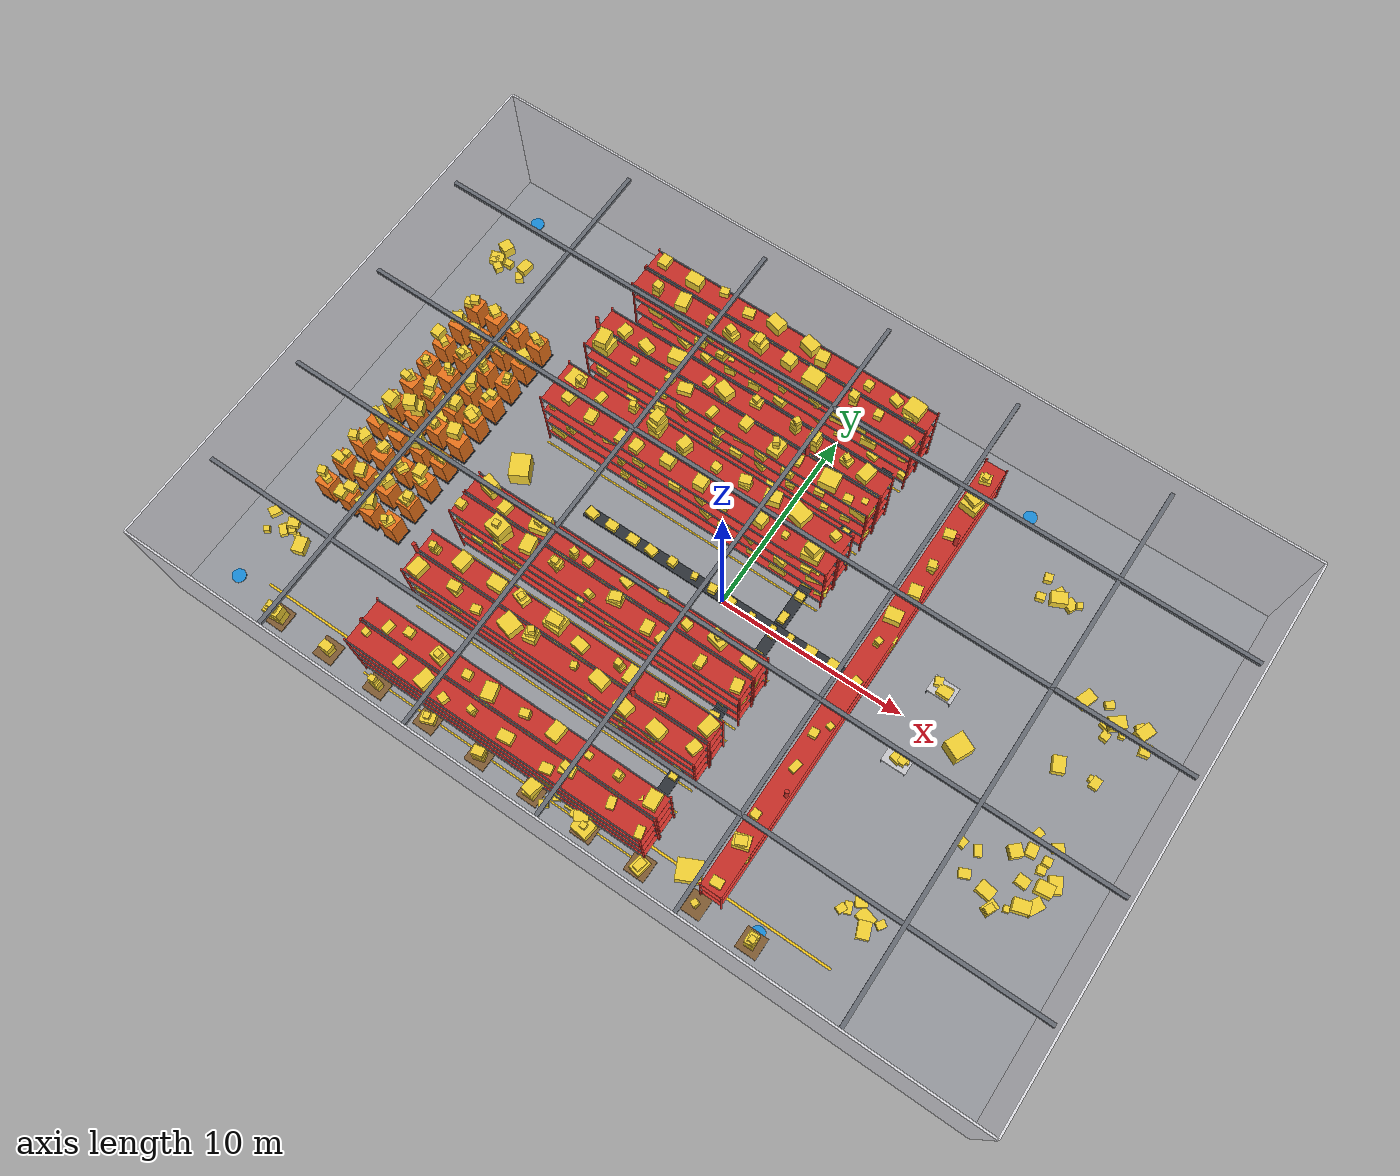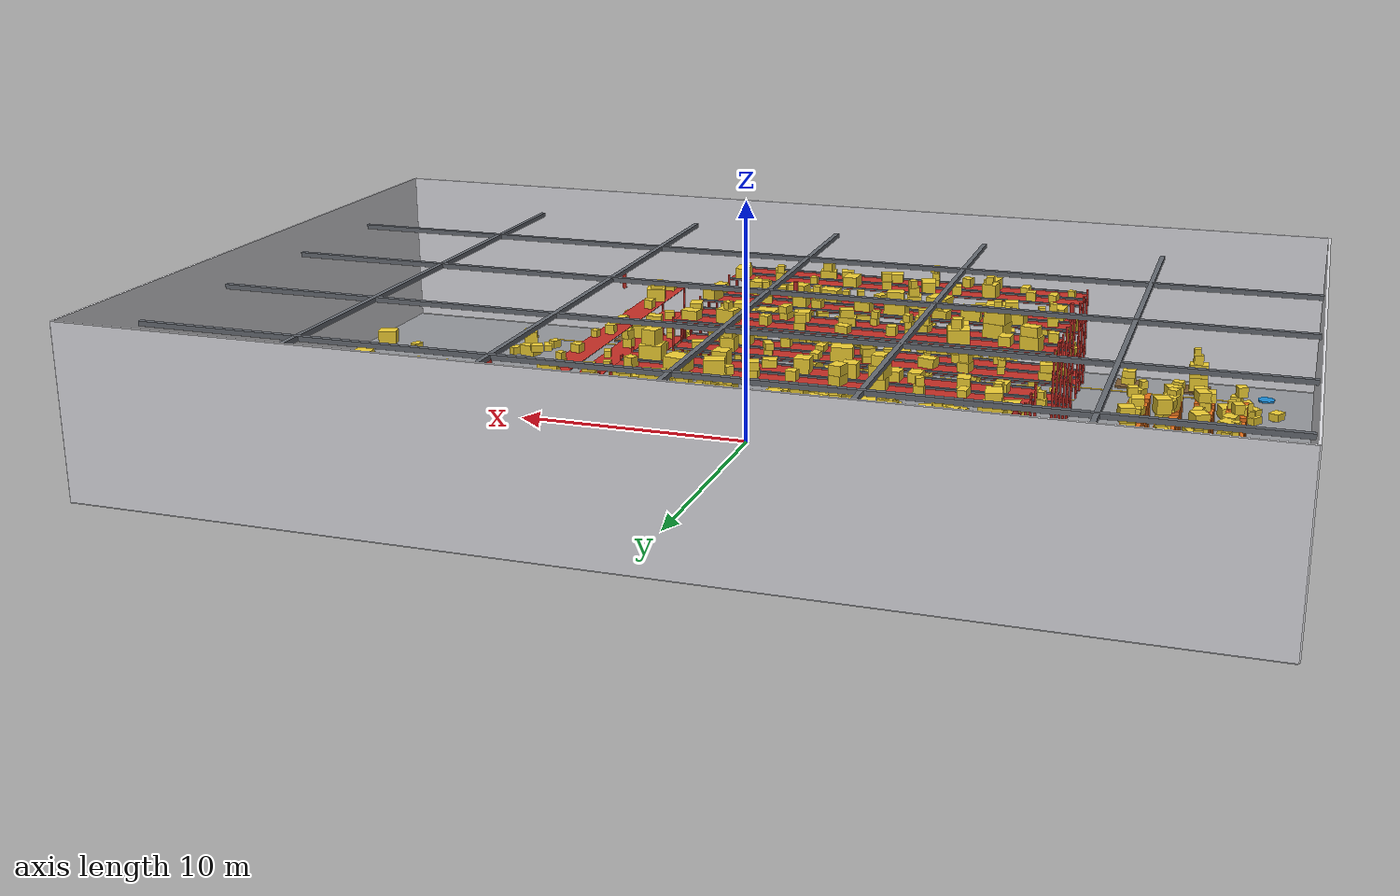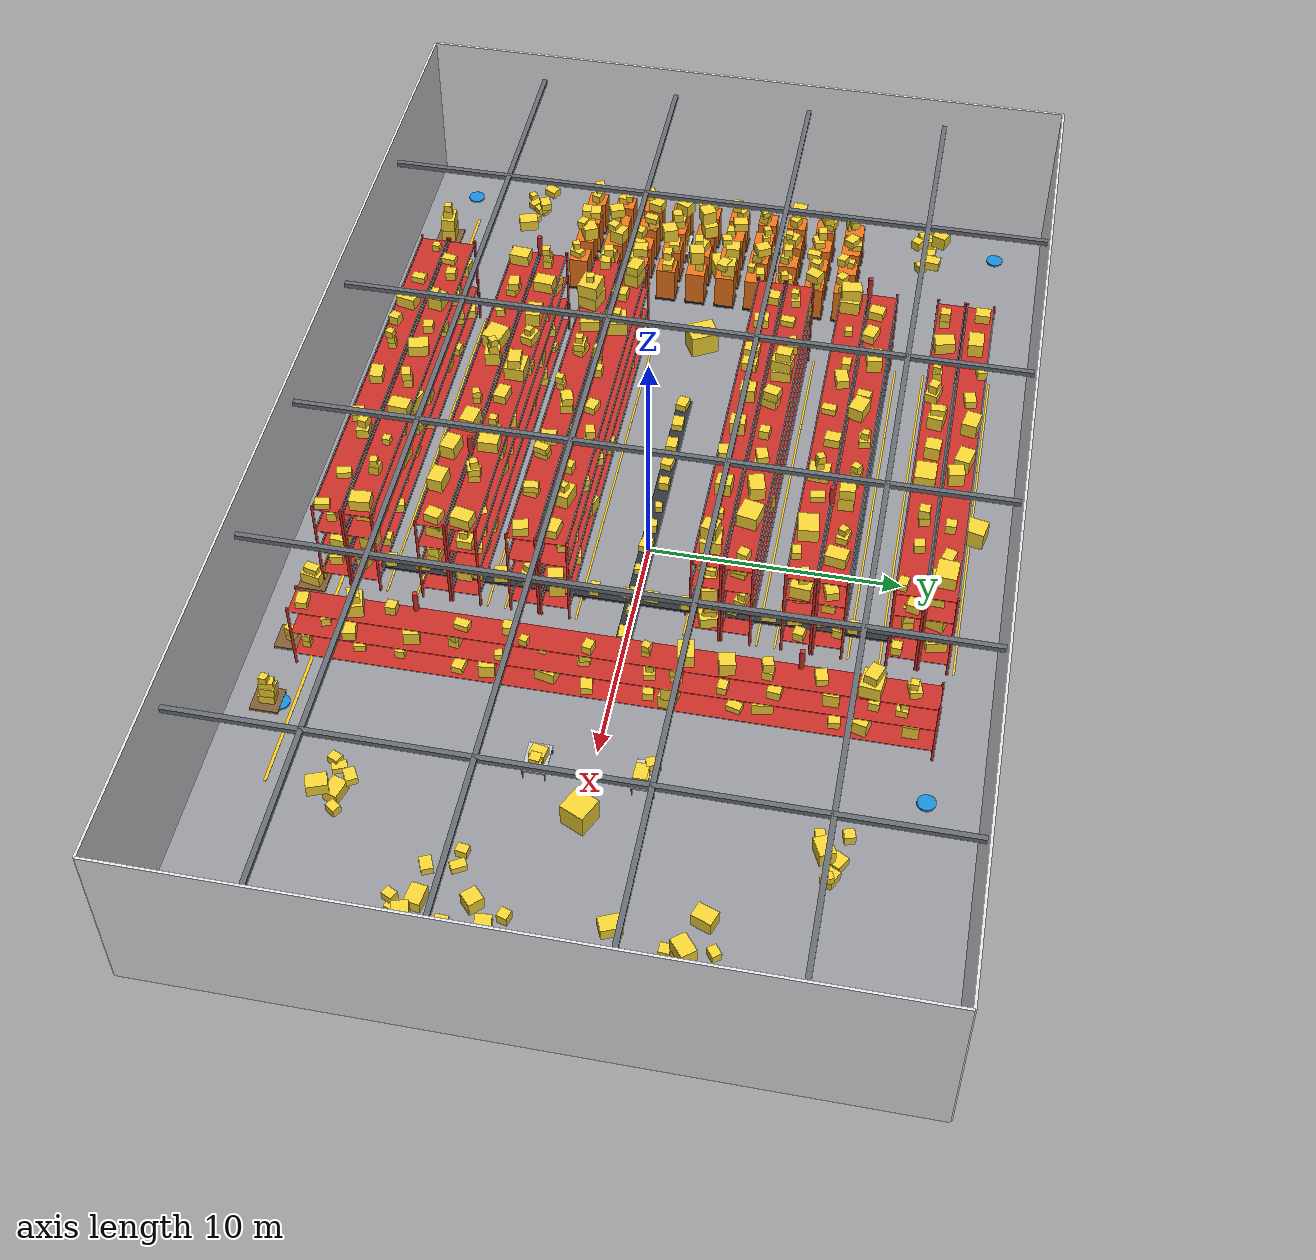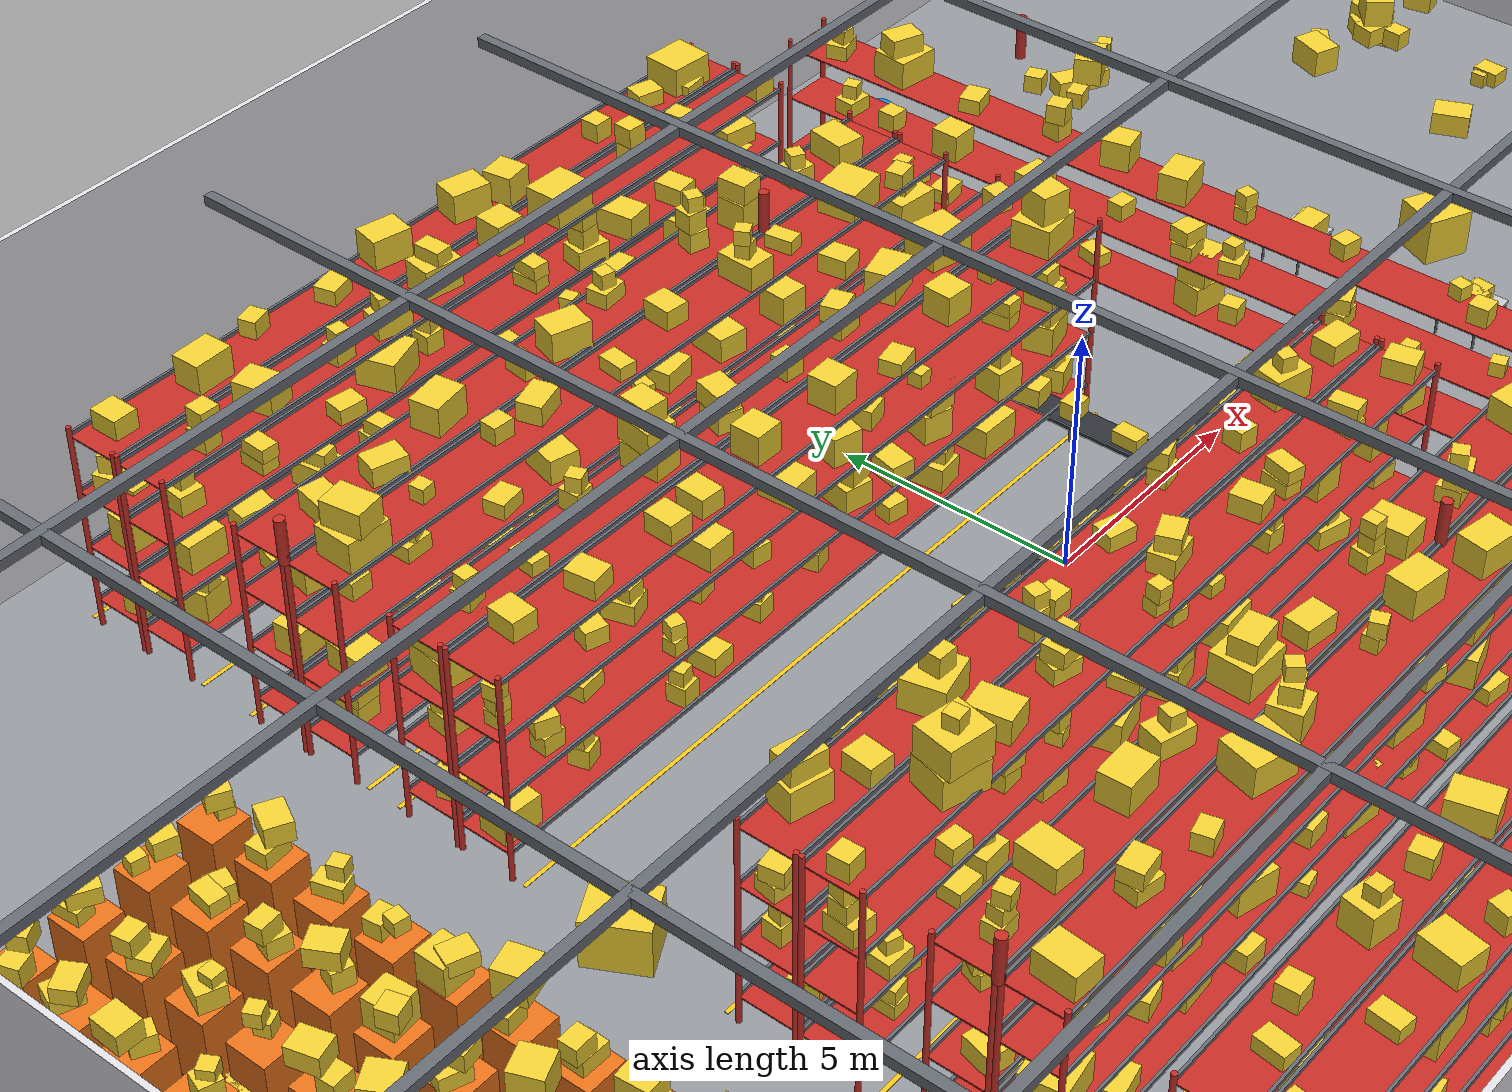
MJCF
<mujoco model="warehouse">
    <compiler angle="degree" coordinate="local" autolimits="true"/>
    <option timestep="0.005" gravity="0 0 -9.81"/>

    <default>
        <default class="env_visual">
            <geom contype="0" conaffinity="0" group="2" density="0"/>
        </default>
        <default class="env_solid">
            <geom contype="1" conaffinity="1" group="3" rgba="0.4 0.4 0.4 0.25" friction="1 0.005 0.0001"/>
        </default>
    </default>

    <asset>
        <texture name="grid" type="2d" builtin="checker" rgb1=".55 .56 .58" rgb2=".62 .63 .65" width="300" height="300"/>
        <material name="mat_floor"      texture="grid" texrepeat="44 28" texuniform="true"/>
        <material name="mat_wall"       rgba="0.88 0.88 0.90 1" specular="0.2"/>
        <material name="mat_shelf_red"  rgba="0.78 0.18 0.15 1" specular="0.4" shininess="0.4"/>
        <material name="mat_box_yellow" rgba="0.95 0.82 0.20 1" specular="0.2"/>
        <material name="mat_beam"       rgba="0.40 0.42 0.45 1" specular="0.5"/>
        <material name="mat_pallet"     rgba="0.50 0.36 0.20 1" specular="0.1"/>
        <material name="mat_pod"        rgba="0.92 0.45 0.10 1" specular="0.3"/>
        <material name="mat_pod_base"   rgba="0.20 0.20 0.22 1" specular="0.4"/>
        <material name="mat_conveyor"   rgba="0.18 0.20 0.22 1" specular="0.6" shininess="0.6"/>
        <material name="mat_charge"     rgba="0.10 0.55 0.85 1" specular="0.5"/>
        <material name="mat_marking"    rgba="0.96 0.78 0.10 1" specular="0.2"/>
        <material name="mat_table"      rgba="0.78 0.78 0.80 1" specular="0.3"/>
    </asset>

    <worldbody>
        <light pos="-15.0 -9.0 6.0" dir="0 0 -1" diffuse="0.35 0.35 0.35"/>
        <light pos="-15.0 0.0 6.0" dir="0 0 -1" diffuse="0.35 0.35 0.35"/>
        <light pos="-15.0 9.0 6.0" dir="0 0 -1" diffuse="0.35 0.35 0.35"/>
        <light pos="-7.0 -9.0 6.0" dir="0 0 -1" diffuse="0.35 0.35 0.35"/>
        <light pos="-7.0 0.0 6.0" dir="0 0 -1" diffuse="0.35 0.35 0.35"/>
        <light pos="-7.0 9.0 6.0" dir="0 0 -1" diffuse="0.35 0.35 0.35"/>
        <light pos="0.0 -9.0 6.0" dir="0 0 -1" diffuse="0.35 0.35 0.35"/>
        <light pos="0.0 0.0 6.0" dir="0 0 -1" diffuse="0.35 0.35 0.35"/>
        <light pos="0.0 9.0 6.0" dir="0 0 -1" diffuse="0.35 0.35 0.35"/>
        <light pos="7.0 -9.0 6.0" dir="0 0 -1" diffuse="0.35 0.35 0.35"/>
        <light pos="7.0 0.0 6.0" dir="0 0 -1" diffuse="0.35 0.35 0.35"/>
        <light pos="7.0 9.0 6.0" dir="0 0 -1" diffuse="0.35 0.35 0.35"/>
        <light pos="15.0 -9.0 6.0" dir="0 0 -1" diffuse="0.35 0.35 0.35"/>
        <light pos="15.0 0.0 6.0" dir="0 0 -1" diffuse="0.35 0.35 0.35"/>
        <light pos="15.0 9.0 6.0" dir="0 0 -1" diffuse="0.35 0.35 0.35"/>
        <light pos="-18 -10 5" dir="0.5 0.3 -1" diffuse="0.3 0.3 0.3"/>
        <light pos="18 10 5"   dir="-0.5 -0.3 -1" diffuse="0.3 0.3 0.3"/>
        <geom name="floor" type="plane" size="22.0 14.0 0.5" material="mat_floor" pos="0 0 0"/>
        <geom class="env_visual" name="wall_north" type="box" pos="0.000 14.000 3.500" size="22.000 0.050 3.500" material="mat_wall"/>
        <geom class="env_solid" name="wall_north_col" type="box" pos="0.000 14.000 3.500" size="22.000 0.050 3.500"/>
        <geom class="env_visual" name="wall_south" type="box" pos="0.000 -14.000 3.500" size="22.000 0.050 3.500" material="mat_wall"/>
        <geom class="env_solid" name="wall_south_col" type="box" pos="0.000 -14.000 3.500" size="22.000 0.050 3.500"/>
        <geom class="env_visual" name="wall_east" type="box" pos="22.000 0.000 3.500" size="0.050 14.000 3.500" material="mat_wall"/>
        <geom class="env_solid" name="wall_east_col" type="box" pos="22.000 0.000 3.500" size="0.050 14.000 3.500"/>
        <geom class="env_visual" name="wall_west" type="box" pos="-22.000 0.000 3.500" size="0.050 14.000 3.500" material="mat_wall"/>
        <geom class="env_solid" name="wall_west_col" type="box" pos="-22.000 0.000 3.500" size="0.050 14.000 3.500"/>
        <geom class="env_visual" name="rack_p0_f_post_0" type="cylinder" pos="-12.000 -12.150 2.175" size="0.050 2.175" material="mat_shelf_red"/>
        <geom class="env_solid" name="rack_p0_f_post_0_col" type="cylinder" pos="-12.000 -12.150 2.175" size="0.050 2.175"/>
        <geom class="env_visual" name="rack_p0_f_post_1" type="cylinder" pos="-12.000 -11.050 2.175" size="0.050 2.175" material="mat_shelf_red"/>
        <geom class="env_solid" name="rack_p0_f_post_1_col" type="cylinder" pos="-12.000 -11.050 2.175" size="0.050 2.175"/>
        <geom class="env_visual" name="rack_p0_f_post_2" type="cylinder" pos="4.000 -12.150 2.175" size="0.050 2.175" material="mat_shelf_red"/>
        <geom class="env_solid" name="rack_p0_f_post_2_col" type="cylinder" pos="4.000 -12.150 2.175" size="0.050 2.175"/>
        <geom class="env_visual" name="rack_p0_f_post_3" type="cylinder" pos="4.000 -11.050 2.175" size="0.050 2.175" material="mat_shelf_red"/>
        <geom class="env_solid" name="rack_p0_f_post_3_col" type="cylinder" pos="4.000 -11.050 2.175" size="0.050 2.175"/>
        <geom class="env_visual" name="rack_p0_f_plank_l0" type="box" pos="-4.000 -11.600 0.550" size="8.000 0.550 0.015" material="mat_shelf_red"/>
        <geom class="env_solid" name="rack_p0_f_plank_l0_col" type="box" pos="-4.000 -11.600 0.550" size="8.000 0.550 0.015"/>
        <geom class="env_visual" name="rack_p0_f_beam_l0_f" type="box" pos="-4.000 -12.150 0.600" size="8.000 0.025 0.040" material="mat_beam"/>
        <geom class="env_solid" name="rack_p0_f_beam_l0_f_col" type="box" pos="-4.000 -12.150 0.600" size="8.000 0.025 0.040"/>
        <geom class="env_visual" name="rack_p0_f_beam_l0_b" type="box" pos="-4.000 -11.050 0.600" size="8.000 0.025 0.040" material="mat_beam"/>
        <geom class="env_solid" name="rack_p0_f_beam_l0_b_col" type="box" pos="-4.000 -11.050 0.600" size="8.000 0.025 0.040"/>
        <geom class="env_visual" name="rack_p0_f_box_l0_b0" type="box" pos="-10.754 -11.329 0.715" size="0.150 0.150 0.150" euler="0.00 0.00 10.12" material="mat_box_yellow"/>
        <geom class="env_solid" name="rack_p0_f_box_l0_b0_col" type="box" pos="-10.754 -11.329 0.715" size="0.150 0.150 0.150" euler="0.00 0.00 10.12"/>
        <geom class="env_visual" name="rack_p0_f_box_l0_b1" type="box" pos="-9.898 -11.412 0.725" size="0.280 0.220 0.160" euler="0.00 0.00 -0.87" material="mat_box_yellow"/>
        <geom class="env_solid" name="rack_p0_f_box_l0_b1_col" type="box" pos="-9.898 -11.412 0.725" size="0.280 0.220 0.160" euler="0.00 0.00 -0.87"/>
        <geom class="env_visual" name="rack_p0_f_box_l0_b2" type="box" pos="-8.292 -11.690 0.865" size="0.400 0.300 0.300" euler="0.00 0.00 -14.74" material="mat_box_yellow"/>
        <geom class="env_solid" name="rack_p0_f_box_l0_b2_col" type="box" pos="-8.292 -11.690 0.865" size="0.400 0.300 0.300" euler="0.00 0.00 -14.74"/>
        <geom class="env_visual" name="rack_p0_f_box_l0_b3" type="box" pos="-6.931 -11.359 0.705" size="0.180 0.280 0.140" euler="0.00 0.00 16.73" material="mat_box_yellow"/>
        <geom class="env_solid" name="rack_p0_f_box_l0_b3_col" type="box" pos="-6.931 -11.359 0.705" size="0.180 0.280 0.140" euler="0.00 0.00 16.73"/>
        <geom class="env_visual" name="rack_p0_f_box_l0_b4" type="box" pos="-4.656 -11.524 0.725" size="0.280 0.220 0.160" euler="0.00 0.00 11.94" material="mat_box_yellow"/>
        <geom class="env_solid" name="rack_p0_f_box_l0_b4_col" type="box" pos="-4.656 -11.524 0.725" size="0.280 0.220 0.160" euler="0.00 0.00 11.94"/>
        <geom class="env_visual" name="rack_p0_f_box_l0_b4_s1" type="box" pos="-4.687 -11.549 1.035" size="0.150 0.150 0.150" euler="0.00 0.00 -6.86" material="mat_box_yellow"/>
        <geom class="env_solid" name="rack_p0_f_box_l0_b4_s1_col" type="box" pos="-4.687 -11.549 1.035" size="0.150 0.150 0.150" euler="0.00 0.00 -6.86"/>
        <geom class="env_visual" name="rack_p0_f_box_l0_b5" type="box" pos="-3.089 -11.832 0.715" size="0.150 0.150 0.150" euler="0.00 0.00 -9.59" material="mat_box_yellow"/>
        <geom class="env_solid" name="rack_p0_f_box_l0_b5_col" type="box" pos="-3.089 -11.832 0.715" size="0.150 0.150 0.150" euler="0.00 0.00 -9.59"/>
        <geom class="env_visual" name="rack_p0_f_box_l0_b5_s1" type="box" pos="-3.073 -11.836 1.015" size="0.150 0.150 0.150" euler="0.00 0.00 -18.46" material="mat_box_yellow"/>
        <geom class="env_solid" name="rack_p0_f_box_l0_b5_s1_col" type="box" pos="-3.073 -11.836 1.015" size="0.150 0.150 0.150" euler="0.00 0.00 -18.46"/>
        <geom class="env_visual" name="rack_p0_f_box_l0_b6" type="box" pos="-1.388 -11.685 0.765" size="0.250 0.300 0.200" euler="0.00 0.00 -9.73" material="mat_box_yellow"/>
        <geom class="env_solid" name="rack_p0_f_box_l0_b6_col" type="box" pos="-1.388 -11.685 0.765" size="0.250 0.300 0.200" euler="0.00 0.00 -9.73"/>
        <geom class="env_visual" name="rack_p0_f_box_l0_b6_s1" type="box" pos="-1.382 -11.724 1.165" size="0.250 0.300 0.200" euler="0.00 0.00 -25.42" material="mat_box_yellow"/>
        <geom class="env_solid" name="rack_p0_f_box_l0_b6_s1_col" type="box" pos="-1.382 -11.724 1.165" size="0.250 0.300 0.200" euler="0.00 0.00 -25.42"/>
        <geom class="env_visual" name="rack_p0_f_box_l0_b7" type="box" pos="0.467 -11.440 0.765" size="0.250 0.300 0.200" euler="0.00 0.00 -17.98" material="mat_box_yellow"/>
        <geom class="env_solid" name="rack_p0_f_box_l0_b7_col" type="box" pos="0.467 -11.440 0.765" size="0.250 0.300 0.200" euler="0.00 0.00 -17.98"/>
        <geom class="env_visual" name="rack_p0_f_box_l0_b7_s1" type="box" pos="0.464 -11.392 1.165" size="0.250 0.300 0.200" euler="0.00 0.00 -22.08" material="mat_box_yellow"/>
        <geom class="env_solid" name="rack_p0_f_box_l0_b7_s1_col" type="box" pos="0.464 -11.392 1.165" size="0.250 0.300 0.200" euler="0.00 0.00 -22.08"/>
        <geom class="env_visual" name="rack_p0_f_box_l0_b7_s2" type="box" pos="0.492 -11.415 1.565" size="0.200 0.200 0.200" euler="0.00 0.00 -38.60" material="mat_box_yellow"/>
        <geom class="env_solid" name="rack_p0_f_box_l0_b7_s2_col" type="box" pos="0.492 -11.415 1.565" size="0.200 0.200 0.200" euler="0.00 0.00 -38.60"/>
        <geom class="env_visual" name="rack_p0_f_box_l0_b8" type="box" pos="1.299 -11.623 0.865" size="0.450 0.400 0.300" euler="0.00 0.00 15.22" material="mat_box_yellow"/>
        <geom class="env_solid" name="rack_p0_f_box_l0_b8_col" type="box" pos="1.299 -11.623 0.865" size="0.450 0.400 0.300" euler="0.00 0.00 15.22"/>
        <geom class="env_visual" name="rack_p0_f_box_l0_b8_s1" type="box" pos="1.250 -11.627 1.365" size="0.250 0.300 0.200" euler="0.00 0.00 14.70" material="mat_box_yellow"/>
        <geom class="env_solid" name="rack_p0_f_box_l0_b8_s1_col" type="box" pos="1.250 -11.627 1.365" size="0.250 0.300 0.200" euler="0.00 0.00 14.70"/>
        <geom class="env_visual" name="rack_p0_f_box_l0_b9" type="box" pos="3.157 -11.773 0.765" size="0.350 0.250 0.200" euler="0.00 0.00 8.35" material="mat_box_yellow"/>
        <geom class="env_solid" name="rack_p0_f_box_l0_b9_col" type="box" pos="3.157 -11.773 0.765" size="0.350 0.250 0.200" euler="0.00 0.00 8.35"/>
        <geom class="env_visual" name="rack_p0_f_box_l0_b9_s1" type="box" pos="3.119 -11.781 1.145" size="0.220 0.180 0.180" euler="0.00 0.00 -3.14" material="mat_box_yellow"/>
        <geom class="env_solid" name="rack_p0_f_box_l0_b9_s1_col" type="box" pos="3.119 -11.781 1.145" size="0.220 0.180 0.180" euler="0.00 0.00 -3.14"/>
        <geom class="env_visual" name="rack_p0_f_plank_l1" type="box" pos="-4.000 -11.600 1.750" size="8.000 0.550 0.015" material="mat_shelf_red"/>
        <geom class="env_solid" name="rack_p0_f_plank_l1_col" type="box" pos="-4.000 -11.600 1.750" size="8.000 0.550 0.015"/>
        <geom class="env_visual" name="rack_p0_f_beam_l1_f" type="box" pos="-4.000 -12.150 1.800" size="8.000 0.025 0.040" material="mat_beam"/>
        <geom class="env_solid" name="rack_p0_f_beam_l1_f_col" type="box" pos="-4.000 -12.150 1.800" size="8.000 0.025 0.040"/>
        <geom class="env_visual" name="rack_p0_f_beam_l1_b" type="box" pos="-4.000 -11.050 1.800" size="8.000 0.025 0.040" material="mat_beam"/>
        <geom class="env_solid" name="rack_p0_f_beam_l1_b_col" type="box" pos="-4.000 -11.050 1.800" size="8.000 0.025 0.040"/>
        <geom class="env_visual" name="rack_p0_f_box_l1_b0" type="box" pos="-11.388 -11.361 1.925" size="0.280 0.220 0.160" euler="0.00 0.00 -10.41" material="mat_box_yellow"/>
        <geom class="env_solid" name="rack_p0_f_box_l1_b0_col" type="box" pos="-11.388 -11.361 1.925" size="0.280 0.220 0.160" euler="0.00 0.00 -10.41"/>
        <geom class="env_visual" name="rack_p0_f_box_l1_b0_s1" type="box" pos="-11.434 -11.397 2.235" size="0.150 0.150 0.150" euler="0.00 0.00 -12.75" material="mat_box_yellow"/>
        <geom class="env_solid" name="rack_p0_f_box_l1_b0_s1_col" type="box" pos="-11.434 -11.397 2.235" size="0.150 0.150 0.150" euler="0.00 0.00 -12.75"/>
        <geom class="env_visual" name="rack_p0_f_box_l1_b0_s2" type="box" pos="-11.401 -11.408 2.535" size="0.150 0.150 0.150" euler="0.00 0.00 -29.78" material="mat_box_yellow"/>
        <geom class="env_solid" name="rack_p0_f_box_l1_b0_s2_col" type="box" pos="-11.401 -11.408 2.535" size="0.150 0.150 0.150" euler="0.00 0.00 -29.78"/>
        <geom class="env_visual" name="rack_p0_f_box_l1_b1" type="box" pos="-9.532 -11.744 1.965" size="0.350 0.250 0.200" euler="0.00 0.00 3.65" material="mat_box_yellow"/>
        <geom class="env_solid" name="rack_p0_f_box_l1_b1_col" type="box" pos="-9.532 -11.744 1.965" size="0.350 0.250 0.200" euler="0.00 0.00 3.65"/>
        <geom class="env_visual" name="rack_p0_f_box_l1_b1_s1" type="box" pos="-9.569 -11.735 2.345" size="0.220 0.180 0.180" euler="0.00 0.00 16.94" material="mat_box_yellow"/>
        <geom class="env_solid" name="rack_p0_f_box_l1_b1_s1_col" type="box" pos="-9.569 -11.735 2.345" size="0.220 0.180 0.180" euler="0.00 0.00 16.94"/>
        <geom class="env_visual" name="rack_p0_f_box_l1_b1_s2" type="box" pos="-9.601 -11.770 2.705" size="0.220 0.180 0.180" euler="0.00 0.00 33.28" material="mat_box_yellow"/>
        <geom class="env_solid" name="rack_p0_f_box_l1_b1_s2_col" type="box" pos="-9.601 -11.770 2.705" size="0.220 0.180 0.180" euler="0.00 0.00 33.28"/>
        <geom class="env_visual" name="rack_p0_f_box_l1_b2" type="box" pos="-8.240 -11.792 1.925" size="0.280 0.220 0.160" euler="0.00 0.00 8.62" material="mat_box_yellow"/>
        <geom class="env_solid" name="rack_p0_f_box_l1_b2_col" type="box" pos="-8.240 -11.792 1.925" size="0.280 0.220 0.160" euler="0.00 0.00 8.62"/>
        <geom class="env_visual" name="rack_p0_f_box_l1_b3" type="box" pos="-6.247 -11.663 1.965" size="0.350 0.250 0.200" euler="0.00 0.00 -0.63" material="mat_box_yellow"/>
        <geom class="env_solid" name="rack_p0_f_box_l1_b3_col" type="box" pos="-6.247 -11.663 1.965" size="0.350 0.250 0.200" euler="0.00 0.00 -0.63"/>
        <geom class="env_visual" name="rack_p0_f_box_l1_b3_s1" type="box" pos="-6.286 -11.709 2.365" size="0.350 0.250 0.200" euler="0.00 0.00 17.88" material="mat_box_yellow"/>
        <geom class="env_solid" name="rack_p0_f_box_l1_b3_s1_col" type="box" pos="-6.286 -11.709 2.365" size="0.350 0.250 0.200" euler="0.00 0.00 17.88"/>
        <geom class="env_visual" name="rack_p0_f_box_l1_b4" type="box" pos="-5.024 -11.451 2.065" size="0.300 0.300 0.300" euler="0.00 0.00 3.47" material="mat_box_yellow"/>
        <geom class="env_solid" name="rack_p0_f_box_l1_b4_col" type="box" pos="-5.024 -11.451 2.065" size="0.300 0.300 0.300" euler="0.00 0.00 3.47"/>
        <geom class="env_visual" name="rack_p0_f_box_l1_b4_s1" type="box" pos="-4.981 -11.403 2.565" size="0.200 0.200 0.200" euler="0.00 0.00 -11.47" material="mat_box_yellow"/>
        <geom class="env_solid" name="rack_p0_f_box_l1_b4_s1_col" type="box" pos="-4.981 -11.403 2.565" size="0.200 0.200 0.200" euler="0.00 0.00 -11.47"/>
        <geom class="env_visual" name="rack_p0_f_box_l1_b5" type="box" pos="-2.791 -11.543 1.905" size="0.180 0.280 0.140" euler="0.00 0.00 -7.91" material="mat_box_yellow"/>
        <geom class="env_solid" name="rack_p0_f_box_l1_b5_col" type="box" pos="-2.791 -11.543 1.905" size="0.180 0.280 0.140" euler="0.00 0.00 -7.91"/>
        <geom class="env_visual" name="rack_p0_f_box_l1_b6" type="box" pos="-1.396 -11.841 1.965" size="0.350 0.250 0.200" euler="0.00 0.00 -3.19" material="mat_box_yellow"/>
        <geom class="env_solid" name="rack_p0_f_box_l1_b6_col" type="box" pos="-1.396 -11.841 1.965" size="0.350 0.250 0.200" euler="0.00 0.00 -3.19"/>
        <geom class="env_visual" name="rack_p0_f_box_l1_b6_s1" type="box" pos="-1.428 -11.854 2.365" size="0.350 0.250 0.200" euler="0.00 0.00 -0.30" material="mat_box_yellow"/>
        <geom class="env_solid" name="rack_p0_f_box_l1_b6_s1_col" type="box" pos="-1.428 -11.854 2.365" size="0.350 0.250 0.200" euler="0.00 0.00 -0.30"/>
        <geom class="env_visual" name="rack_p0_f_box_l1_b6_s2" type="box" pos="-1.464 -11.859 2.715" size="0.150 0.150 0.150" euler="0.00 0.00 -7.06" material="mat_box_yellow"/>
        <geom class="env_solid" name="rack_p0_f_box_l1_b6_s2_col" type="box" pos="-1.464 -11.859 2.715" size="0.150 0.150 0.150" euler="0.00 0.00 -7.06"/>
        <geom class="env_visual" name="rack_p0_f_box_l1_b7" type="box" pos="0.091 -11.852 1.945" size="0.220 0.180 0.180" euler="0.00 0.00 -16.74" material="mat_box_yellow"/>
        <geom class="env_solid" name="rack_p0_f_box_l1_b7_col" type="box" pos="0.091 -11.852 1.945" size="0.220 0.180 0.180" euler="0.00 0.00 -16.74"/>
        <geom class="env_visual" name="rack_p0_f_box_l1_b7_s1" type="box" pos="0.111 -11.805 2.305" size="0.220 0.180 0.180" euler="0.00 0.00 -35.89" material="mat_box_yellow"/>
        <geom class="env_solid" name="rack_p0_f_box_l1_b7_s1_col" type="box" pos="0.111 -11.805 2.305" size="0.220 0.180 0.180" euler="0.00 0.00 -35.89"/>
        <geom class="env_visual" name="rack_p0_f_box_l1_b8" type="box" pos="1.072 -11.744 1.915" size="0.150 0.150 0.150" euler="0.00 0.00 -13.08" material="mat_box_yellow"/>
        <geom class="env_solid" name="rack_p0_f_box_l1_b8_col" type="box" pos="1.072 -11.744 1.915" size="0.150 0.150 0.150" euler="0.00 0.00 -13.08"/>
        <geom class="env_visual" name="rack_p0_f_box_l1_b8_s1" type="box" pos="1.077 -11.720 2.215" size="0.150 0.150 0.150" euler="0.00 0.00 2.93" material="mat_box_yellow"/>
        <geom class="env_solid" name="rack_p0_f_box_l1_b8_s1_col" type="box" pos="1.077 -11.720 2.215" size="0.150 0.150 0.150" euler="0.00 0.00 2.93"/>
        <geom class="env_visual" name="rack_p0_f_box_l1_b9" type="box" pos="3.411 -11.409 2.065" size="0.400 0.300 0.300" euler="0.00 0.00 -5.33" material="mat_box_yellow"/>
        <geom class="env_solid" name="rack_p0_f_box_l1_b9_col" type="box" pos="3.411 -11.409 2.065" size="0.400 0.300 0.300" euler="0.00 0.00 -5.33"/>
        <geom class="env_visual" name="rack_p0_f_plank_l2" type="box" pos="-4.000 -11.600 2.950" size="8.000 0.550 0.015" material="mat_shelf_red"/>
        <geom class="env_solid" name="rack_p0_f_plank_l2_col" type="box" pos="-4.000 -11.600 2.950" size="8.000 0.550 0.015"/>
        <geom class="env_visual" name="rack_p0_f_beam_l2_f" type="box" pos="-4.000 -12.150 3.000" size="8.000 0.025 0.040" material="mat_beam"/>
        <geom class="env_solid" name="rack_p0_f_beam_l2_f_col" type="box" pos="-4.000 -12.150 3.000" size="8.000 0.025 0.040"/>
        <geom class="env_visual" name="rack_p0_f_beam_l2_b" type="box" pos="-4.000 -11.050 3.000" size="8.000 0.025 0.040" material="mat_beam"/>
        <geom class="env_solid" name="rack_p0_f_beam_l2_b_col" type="box" pos="-4.000 -11.050 3.000" size="8.000 0.025 0.040"/>
        <geom class="env_visual" name="rack_p0_f_box_l2_b0" type="box" pos="-10.821 -11.638 3.165" size="0.250 0.300 0.200" euler="0.00 0.00 10.46" material="mat_box_yellow"/>
        <geom class="env_solid" name="rack_p0_f_box_l2_b0_col" type="box" pos="-10.821 -11.638 3.165" size="0.250 0.300 0.200" euler="0.00 0.00 10.46"/>
        <geom class="env_visual" name="rack_p0_f_box_l2_b1" type="box" pos="-10.066 -11.499 3.125" size="0.280 0.220 0.160" euler="0.00 0.00 -4.35" material="mat_box_yellow"/>
        <geom class="env_solid" name="rack_p0_f_box_l2_b1_col" type="box" pos="-10.066 -11.499 3.125" size="0.280 0.220 0.160" euler="0.00 0.00 -4.35"/>
        <geom class="env_visual" name="rack_p0_f_box_l2_b1_s1" type="box" pos="-10.108 -11.485 3.435" size="0.150 0.150 0.150" euler="0.00 0.00 15.38" material="mat_box_yellow"/>
        <geom class="env_solid" name="rack_p0_f_box_l2_b1_s1_col" type="box" pos="-10.108 -11.485 3.435" size="0.150 0.150 0.150" euler="0.00 0.00 15.38"/>
        <geom class="env_visual" name="rack_p0_f_box_l2_b2" type="box" pos="-8.069 -11.539 3.265" size="0.450 0.400 0.300" euler="0.00 0.00 2.91" material="mat_box_yellow"/>
        <geom class="env_solid" name="rack_p0_f_box_l2_b2_col" type="box" pos="-8.069 -11.539 3.265" size="0.450 0.400 0.300" euler="0.00 0.00 2.91"/>
        <geom class="env_visual" name="rack_p0_f_box_l2_b3" type="box" pos="-6.850 -11.425 3.145" size="0.220 0.180 0.180" euler="0.00 0.00 -16.93" material="mat_box_yellow"/>
        <geom class="env_solid" name="rack_p0_f_box_l2_b3_col" type="box" pos="-6.850 -11.425 3.145" size="0.220 0.180 0.180" euler="0.00 0.00 -16.93"/>
        <geom class="env_visual" name="rack_p0_f_box_l2_b4" type="box" pos="-5.383 -11.252 3.115" size="0.150 0.150 0.150" euler="0.00 0.00 -13.94" material="mat_box_yellow"/>
        <geom class="env_solid" name="rack_p0_f_box_l2_b4_col" type="box" pos="-5.383 -11.252 3.115" size="0.150 0.150 0.150" euler="0.00 0.00 -13.94"/>
        <geom class="env_visual" name="rack_p0_f_box_l2_b5" type="box" pos="-2.712 -11.722 3.105" size="0.180 0.280 0.140" euler="0.00 0.00 -17.59" material="mat_box_yellow"/>
        <geom class="env_solid" name="rack_p0_f_box_l2_b5_col" type="box" pos="-2.712 -11.722 3.105" size="0.180 0.280 0.140" euler="0.00 0.00 -17.59"/>
        <geom class="env_visual" name="rack_p0_f_box_l2_b5_s1" type="box" pos="-2.710 -11.697 3.385" size="0.180 0.280 0.140" euler="0.00 0.00 -23.89" material="mat_box_yellow"/>
        <geom class="env_solid" name="rack_p0_f_box_l2_b5_s1_col" type="box" pos="-2.710 -11.697 3.385" size="0.180 0.280 0.140" euler="0.00 0.00 -23.89"/>
        <geom class="env_visual" name="rack_p0_f_box_l2_b6" type="box" pos="-1.122 -11.732 3.115" size="0.150 0.150 0.150" euler="0.00 0.00 5.97" material="mat_box_yellow"/>
        <geom class="env_solid" name="rack_p0_f_box_l2_b6_col" type="box" pos="-1.122 -11.732 3.115" size="0.150 0.150 0.150" euler="0.00 0.00 5.97"/>
        <geom class="env_visual" name="rack_p0_f_box_l2_b6_s1" type="box" pos="-1.092 -11.706 3.415" size="0.150 0.150 0.150" euler="0.00 0.00 -6.02" material="mat_box_yellow"/>
        <geom class="env_solid" name="rack_p0_f_box_l2_b6_s1_col" type="box" pos="-1.092 -11.706 3.415" size="0.150 0.150 0.150" euler="0.00 0.00 -6.02"/>
        <geom class="env_visual" name="rack_p0_f_box_l2_b7" type="box" pos="0.068 -11.703 3.165" size="0.350 0.250 0.200" euler="0.00 0.00 -13.10" material="mat_box_yellow"/>
        <geom class="env_solid" name="rack_p0_f_box_l2_b7_col" type="box" pos="0.068 -11.703 3.165" size="0.350 0.250 0.200" euler="0.00 0.00 -13.10"/>
        <geom class="env_visual" name="rack_p0_f_box_l2_b8" type="box" pos="1.794 -11.483 3.215" size="0.300 0.400 0.250" euler="0.00 0.00 -8.04" material="mat_box_yellow"/>
        <geom class="env_solid" name="rack_p0_f_box_l2_b8_col" type="box" pos="1.794 -11.483 3.215" size="0.300 0.400 0.250" euler="0.00 0.00 -8.04"/>
        <geom class="env_visual" name="rack_p0_f_box_l2_b8_s1" type="box" pos="1.791 -11.440 3.615" size="0.150 0.150 0.150" euler="0.00 0.00 5.20" material="mat_box_yellow"/>
        <geom class="env_solid" name="rack_p0_f_box_l2_b8_s1_col" type="box" pos="1.791 -11.440 3.615" size="0.150 0.150 0.150" euler="0.00 0.00 5.20"/>
        <geom class="env_visual" name="rack_p0_f_box_l2_b9" type="box" pos="3.193 -11.729 3.145" size="0.220 0.180 0.180" euler="0.00 0.00 12.21" material="mat_box_yellow"/>
        <geom class="env_solid" name="rack_p0_f_box_l2_b9_col" type="box" pos="3.193 -11.729 3.145" size="0.220 0.180 0.180" euler="0.00 0.00 12.21"/>
        <geom class="env_visual" name="rack_p0_f_plank_l3" type="box" pos="-4.000 -11.600 4.150" size="8.000 0.550 0.015" material="mat_shelf_red"/>
        <geom class="env_solid" name="rack_p0_f_plank_l3_col" type="box" pos="-4.000 -11.600 4.150" size="8.000 0.550 0.015"/>
        <geom class="env_visual" name="rack_p0_f_beam_l3_f" type="box" pos="-4.000 -12.150 4.200" size="8.000 0.025 0.040" material="mat_beam"/>
        <geom class="env_solid" name="rack_p0_f_beam_l3_f_col" type="box" pos="-4.000 -12.150 4.200" size="8.000 0.025 0.040"/>
        <geom class="env_visual" name="rack_p0_f_beam_l3_b" type="box" pos="-4.000 -11.050 4.200" size="8.000 0.025 0.040" material="mat_beam"/>
        <geom class="env_solid" name="rack_p0_f_beam_l3_b_col" type="box" pos="-4.000 -11.050 4.200" size="8.000 0.025 0.040"/>
        <geom class="env_visual" name="rack_p0_f_box_l3_b0" type="box" pos="-11.419 -11.350 4.315" size="0.150 0.150 0.150" euler="0.00 0.00 -7.99" material="mat_box_yellow"/>
        <geom class="env_solid" name="rack_p0_f_box_l3_b0_col" type="box" pos="-11.419 -11.350 4.315" size="0.150 0.150 0.150" euler="0.00 0.00 -7.99"/>
        <geom class="env_visual" name="rack_p0_f_box_l3_b1" type="box" pos="-9.358 -11.565 4.305" size="0.180 0.280 0.140" euler="0.00 0.00 -6.87" material="mat_box_yellow"/>
        <geom class="env_solid" name="rack_p0_f_box_l3_b1_col" type="box" pos="-9.358 -11.565 4.305" size="0.180 0.280 0.140" euler="0.00 0.00 -6.87"/>
        <geom class="env_visual" name="rack_p0_f_box_l3_b2" type="box" pos="-7.870 -11.625 4.415" size="0.300 0.400 0.250" euler="0.00 0.00 -11.16" material="mat_box_yellow"/>
        <geom class="env_solid" name="rack_p0_f_box_l3_b2_col" type="box" pos="-7.870 -11.625 4.415" size="0.300 0.400 0.250" euler="0.00 0.00 -11.16"/>
        <geom class="env_visual" name="rack_p0_f_box_l3_b3" type="box" pos="-6.694 -11.837 4.365" size="0.200 0.200 0.200" euler="0.00 0.00 -16.31" material="mat_box_yellow"/>
        <geom class="env_solid" name="rack_p0_f_box_l3_b3_col" type="box" pos="-6.694 -11.837 4.365" size="0.200 0.200 0.200" euler="0.00 0.00 -16.31"/>
        <geom class="env_visual" name="rack_p0_f_box_l3_b4" type="box" pos="-5.277 -11.573 4.315" size="0.150 0.150 0.150" euler="0.00 0.00 5.04" material="mat_box_yellow"/>
        <geom class="env_solid" name="rack_p0_f_box_l3_b4_col" type="box" pos="-5.277 -11.573 4.315" size="0.150 0.150 0.150" euler="0.00 0.00 5.04"/>
        <geom class="env_visual" name="rack_p0_f_box_l3_b4_s1" type="box" pos="-5.259 -11.603 4.615" size="0.150 0.150 0.150" euler="0.00 0.00 4.04" material="mat_box_yellow"/>
        <geom class="env_solid" name="rack_p0_f_box_l3_b4_s1_col" type="box" pos="-5.259 -11.603 4.615" size="0.150 0.150 0.150" euler="0.00 0.00 4.04"/>
        <geom class="env_visual" name="rack_p0_f_box_l3_b4_s2" type="box" pos="-5.233 -11.600 4.915" size="0.150 0.150 0.150" euler="0.00 0.00 -14.51" material="mat_box_yellow"/>
        <geom class="env_solid" name="rack_p0_f_box_l3_b4_s2_col" type="box" pos="-5.233 -11.600 4.915" size="0.150 0.150 0.150" euler="0.00 0.00 -14.51"/>
        <geom class="env_visual" name="rack_p0_f_box_l3_b5" type="box" pos="-3.387 -11.686 4.365" size="0.350 0.250 0.200" euler="0.00 0.00 7.10" material="mat_box_yellow"/>
        <geom class="env_solid" name="rack_p0_f_box_l3_b5_col" type="box" pos="-3.387 -11.686 4.365" size="0.350 0.250 0.200" euler="0.00 0.00 7.10"/>
        <geom class="env_visual" name="rack_p0_f_box_l3_b6" type="box" pos="-1.123 -11.811 4.325" size="0.280 0.220 0.160" euler="0.00 0.00 12.56" material="mat_box_yellow"/>
        <geom class="env_solid" name="rack_p0_f_box_l3_b6_col" type="box" pos="-1.123 -11.811 4.325" size="0.280 0.220 0.160" euler="0.00 0.00 12.56"/>
        <geom class="env_visual" name="rack_p0_f_box_l3_b7" type="box" pos="-0.338 -11.358 4.365" size="0.350 0.250 0.200" euler="0.00 0.00 8.01" material="mat_box_yellow"/>
        <geom class="env_solid" name="rack_p0_f_box_l3_b7_col" type="box" pos="-0.338 -11.358 4.365" size="0.350 0.250 0.200" euler="0.00 0.00 8.01"/>
        <geom class="env_visual" name="rack_p0_f_box_l3_b7_s1" type="box" pos="-0.369 -11.319 4.745" size="0.220 0.180 0.180" euler="0.00 0.00 -11.73" material="mat_box_yellow"/>
        <geom class="env_solid" name="rack_p0_f_box_l3_b7_s1_col" type="box" pos="-0.369 -11.319 4.745" size="0.220 0.180 0.180" euler="0.00 0.00 -11.73"/>
        <geom class="env_visual" name="rack_p0_f_box_l3_b8" type="box" pos="2.040 -11.452 4.305" size="0.180 0.280 0.140" euler="0.00 0.00 15.99" material="mat_box_yellow"/>
        <geom class="env_solid" name="rack_p0_f_box_l3_b8_col" type="box" pos="2.040 -11.452 4.305" size="0.180 0.280 0.140" euler="0.00 0.00 15.99"/>
        <geom class="env_visual" name="rack_p0_f_box_l3_b9" type="box" pos="3.760 -11.801 4.305" size="0.180 0.280 0.140" euler="0.00 0.00 13.18" material="mat_box_yellow"/>
        <geom class="env_solid" name="rack_p0_f_box_l3_b9_col" type="box" pos="3.760 -11.801 4.305" size="0.180 0.280 0.140" euler="0.00 0.00 13.18"/>
        <geom class="env_visual" name="rack_p0_b_post_0" type="cylinder" pos="-12.000 -10.950 2.175" size="0.050 2.175" material="mat_shelf_red"/>
        <geom class="env_solid" name="rack_p0_b_post_0_col" type="cylinder" pos="-12.000 -10.950 2.175" size="0.050 2.175"/>
        <geom class="env_visual" name="rack_p0_b_post_1" type="cylinder" pos="-12.000 -9.850 2.175" size="0.050 2.175" material="mat_shelf_red"/>
        <geom class="env_solid" name="rack_p0_b_post_1_col" type="cylinder" pos="-12.000 -9.850 2.175" size="0.050 2.175"/>
        <geom class="env_visual" name="rack_p0_b_post_2" type="cylinder" pos="4.000 -10.950 2.175" size="0.050 2.175" material="mat_shelf_red"/>
        <geom class="env_solid" name="rack_p0_b_post_2_col" type="cylinder" pos="4.000 -10.950 2.175" size="0.050 2.175"/>
        <geom class="env_visual" name="rack_p0_b_post_3" type="cylinder" pos="4.000 -9.850 2.175" size="0.050 2.175" material="mat_shelf_red"/>
        <geom class="env_solid" name="rack_p0_b_post_3_col" type="cylinder" pos="4.000 -9.850 2.175" size="0.050 2.175"/>
        <geom class="env_visual" name="rack_p0_b_plank_l0" type="box" pos="-4.000 -10.400 0.550" size="8.000 0.550 0.015" material="mat_shelf_red"/>
        <geom class="env_solid" name="rack_p0_b_plank_l0_col" type="box" pos="-4.000 -10.400 0.550" size="8.000 0.550 0.015"/>
        <geom class="env_visual" name="rack_p0_b_beam_l0_f" type="box" pos="-4.000 -10.950 0.600" size="8.000 0.025 0.040" material="mat_beam"/>
        <geom class="env_solid" name="rack_p0_b_beam_l0_f_col" type="box" pos="-4.000 -10.950 0.600" size="8.000 0.025 0.040"/>
        <geom class="env_visual" name="rack_p0_b_beam_l0_b" type="box" pos="-4.000 -9.850 0.600" size="8.000 0.025 0.040" material="mat_beam"/>
        <geom class="env_solid" name="rack_p0_b_beam_l0_b_col" type="box" pos="-4.000 -9.850 0.600" size="8.000 0.025 0.040"/>
        <geom class="env_visual" name="rack_p0_b_box_l0_b0" type="box" pos="-11.492 -10.216 0.765" size="0.250 0.300 0.200" euler="0.00 0.00 17.30" material="mat_box_yellow"/>
        <geom class="env_solid" name="rack_p0_b_box_l0_b0_col" type="box" pos="-11.492 -10.216 0.765" size="0.250 0.300 0.200" euler="0.00 0.00 17.30"/>
        <geom class="env_visual" name="rack_p0_b_box_l0_b1" type="box" pos="-9.085 -10.097 0.745" size="0.220 0.180 0.180" euler="0.00 0.00 -8.57" material="mat_box_yellow"/>
        <geom class="env_solid" name="rack_p0_b_box_l0_b1_col" type="box" pos="-9.085 -10.097 0.745" size="0.220 0.180 0.180" euler="0.00 0.00 -8.57"/>
        <geom class="env_visual" name="rack_p0_b_box_l0_b2" type="box" pos="-8.139 -10.508 0.815" size="0.300 0.400 0.250" euler="0.00 0.00 -2.13" material="mat_box_yellow"/>
        <geom class="env_solid" name="rack_p0_b_box_l0_b2_col" type="box" pos="-8.139 -10.508 0.815" size="0.300 0.400 0.250" euler="0.00 0.00 -2.13"/>
        <geom class="env_visual" name="rack_p0_b_box_l0_b3" type="box" pos="-6.414 -10.711 0.765" size="0.200 0.200 0.200" euler="0.00 0.00 11.13" material="mat_box_yellow"/>
        <geom class="env_solid" name="rack_p0_b_box_l0_b3_col" type="box" pos="-6.414 -10.711 0.765" size="0.200 0.200 0.200" euler="0.00 0.00 11.13"/>
        <geom class="env_visual" name="rack_p0_b_box_l0_b3_s1" type="box" pos="-6.447 -10.728 1.165" size="0.200 0.200 0.200" euler="0.00 0.00 22.65" material="mat_box_yellow"/>
        <geom class="env_solid" name="rack_p0_b_box_l0_b3_s1_col" type="box" pos="-6.447 -10.728 1.165" size="0.200 0.200 0.200" euler="0.00 0.00 22.65"/>
        <geom class="env_visual" name="rack_p0_b_box_l0_b3_s2" type="box" pos="-6.397 -10.688 1.565" size="0.200 0.200 0.200" euler="0.00 0.00 23.37" material="mat_box_yellow"/>
        <geom class="env_solid" name="rack_p0_b_box_l0_b3_s2_col" type="box" pos="-6.397 -10.688 1.565" size="0.200 0.200 0.200" euler="0.00 0.00 23.37"/>
        <geom class="env_visual" name="rack_p0_b_box_l0_b4" type="box" pos="-4.580 -10.177 0.705" size="0.180 0.280 0.140" euler="0.00 0.00 -0.27" material="mat_box_yellow"/>
        <geom class="env_solid" name="rack_p0_b_box_l0_b4_col" type="box" pos="-4.580 -10.177 0.705" size="0.180 0.280 0.140" euler="0.00 0.00 -0.27"/>
        <geom class="env_visual" name="rack_p0_b_box_l0_b5" type="box" pos="-2.937 -10.428 0.765" size="0.250 0.300 0.200" euler="0.00 0.00 2.12" material="mat_box_yellow"/>
        <geom class="env_solid" name="rack_p0_b_box_l0_b5_col" type="box" pos="-2.937 -10.428 0.765" size="0.250 0.300 0.200" euler="0.00 0.00 2.12"/>
        <geom class="env_visual" name="rack_p0_b_box_l0_b6" type="box" pos="-1.450 -10.384 0.745" size="0.220 0.180 0.180" euler="0.00 0.00 12.37" material="mat_box_yellow"/>
        <geom class="env_solid" name="rack_p0_b_box_l0_b6_col" type="box" pos="-1.450 -10.384 0.745" size="0.220 0.180 0.180" euler="0.00 0.00 12.37"/>
        <geom class="env_visual" name="rack_p0_b_box_l0_b7" type="box" pos="0.192 -10.100 0.765" size="0.200 0.200 0.200" euler="0.00 0.00 13.32" material="mat_box_yellow"/>
        <geom class="env_solid" name="rack_p0_b_box_l0_b7_col" type="box" pos="0.192 -10.100 0.765" size="0.200 0.200 0.200" euler="0.00 0.00 13.32"/>
        <geom class="env_visual" name="rack_p0_b_box_l0_b8" type="box" pos="1.993 -10.091 0.765" size="0.200 0.200 0.200" euler="0.00 0.00 0.87" material="mat_box_yellow"/>
        <geom class="env_solid" name="rack_p0_b_box_l0_b8_col" type="box" pos="1.993 -10.091 0.765" size="0.200 0.200 0.200" euler="0.00 0.00 0.87"/>
        <geom class="env_visual" name="rack_p0_b_box_l0_b9" type="box" pos="3.127 -10.616 0.765" size="0.350 0.250 0.200" euler="0.00 0.00 -17.82" material="mat_box_yellow"/>
        <geom class="env_solid" name="rack_p0_b_box_l0_b9_col" type="box" pos="3.127 -10.616 0.765" size="0.350 0.250 0.200" euler="0.00 0.00 -17.82"/>
        <geom class="env_visual" name="rack_p0_b_box_l0_b9_s1" type="box" pos="3.174 -10.614 1.125" size="0.280 0.220 0.160" euler="0.00 0.00 -21.80" material="mat_box_yellow"/>
        <geom class="env_solid" name="rack_p0_b_box_l0_b9_s1_col" type="box" pos="3.174 -10.614 1.125" size="0.280 0.220 0.160" euler="0.00 0.00 -21.80"/>
        <geom class="env_visual" name="rack_p0_b_plank_l1" type="box" pos="-4.000 -10.400 1.750" size="8.000 0.550 0.015" material="mat_shelf_red"/>
        <geom class="env_solid" name="rack_p0_b_plank_l1_col" type="box" pos="-4.000 -10.400 1.750" size="8.000 0.550 0.015"/>
        <geom class="env_visual" name="rack_p0_b_beam_l1_f" type="box" pos="-4.000 -10.950 1.800" size="8.000 0.025 0.040" material="mat_beam"/>
        <geom class="env_solid" name="rack_p0_b_beam_l1_f_col" type="box" pos="-4.000 -10.950 1.800" size="8.000 0.025 0.040"/>
        <geom class="env_visual" name="rack_p0_b_beam_l1_b" type="box" pos="-4.000 -9.850 1.800" size="8.000 0.025 0.040" material="mat_beam"/>
        <geom class="env_solid" name="rack_p0_b_beam_l1_b_col" type="box" pos="-4.000 -9.850 1.800" size="8.000 0.025 0.040"/>
        <geom class="env_visual" name="rack_p0_b_box_l1_b0" type="box" pos="-11.563 -10.652 1.925" size="0.280 0.220 0.160" euler="0.00 0.00 -12.00" material="mat_box_yellow"/>
        <geom class="env_solid" name="rack_p0_b_box_l1_b0_col" type="box" pos="-11.563 -10.652 1.925" size="0.280 0.220 0.160" euler="0.00 0.00 -12.00"/>
        <geom class="env_visual" name="rack_p0_b_box_l1_b1" type="box" pos="-9.705 -10.053 1.915" size="0.150 0.150 0.150" euler="0.00 0.00 15.24" material="mat_box_yellow"/>
        <geom class="env_solid" name="rack_p0_b_box_l1_b1_col" type="box" pos="-9.705 -10.053 1.915" size="0.150 0.150 0.150" euler="0.00 0.00 15.24"/>
        <geom class="env_visual" name="rack_p0_b_box_l1_b1_s1" type="box" pos="-9.706 -10.069 2.215" size="0.150 0.150 0.150" euler="0.00 0.00 31.28" material="mat_box_yellow"/>
        <geom class="env_solid" name="rack_p0_b_box_l1_b1_s1_col" type="box" pos="-9.706 -10.069 2.215" size="0.150 0.150 0.150" euler="0.00 0.00 31.28"/>
        <geom class="env_visual" name="rack_p0_b_box_l1_b2" type="box" pos="-7.970 -10.697 1.915" size="0.150 0.150 0.150" euler="0.00 0.00 -2.90" material="mat_box_yellow"/>
        <geom class="env_solid" name="rack_p0_b_box_l1_b2_col" type="box" pos="-7.970 -10.697 1.915" size="0.150 0.150 0.150" euler="0.00 0.00 -2.90"/>
        <geom class="env_visual" name="rack_p0_b_box_l1_b2_s1" type="box" pos="-8.007 -10.670 2.215" size="0.150 0.150 0.150" euler="0.00 0.00 -21.99" material="mat_box_yellow"/>
        <geom class="env_solid" name="rack_p0_b_box_l1_b2_s1_col" type="box" pos="-8.007 -10.670 2.215" size="0.150 0.150 0.150" euler="0.00 0.00 -21.99"/>
        <geom class="env_visual" name="rack_p0_b_box_l1_b2_s2" type="box" pos="-8.055 -10.691 2.515" size="0.150 0.150 0.150" euler="0.00 0.00 -13.04" material="mat_box_yellow"/>
        <geom class="env_solid" name="rack_p0_b_box_l1_b2_s2_col" type="box" pos="-8.055 -10.691 2.515" size="0.150 0.150 0.150" euler="0.00 0.00 -13.04"/>
        <geom class="env_visual" name="rack_p0_b_box_l1_b3" type="box" pos="-6.302 -10.621 1.965" size="0.350 0.250 0.200" euler="0.00 0.00 8.31" material="mat_box_yellow"/>
        <geom class="env_solid" name="rack_p0_b_box_l1_b3_col" type="box" pos="-6.302 -10.621 1.965" size="0.350 0.250 0.200" euler="0.00 0.00 8.31"/>
        <geom class="env_visual" name="rack_p0_b_box_l1_b3_s1" type="box" pos="-6.289 -10.599 2.325" size="0.280 0.220 0.160" euler="0.00 0.00 16.37" material="mat_box_yellow"/>
        <geom class="env_solid" name="rack_p0_b_box_l1_b3_s1_col" type="box" pos="-6.289 -10.599 2.325" size="0.280 0.220 0.160" euler="0.00 0.00 16.37"/>
        <geom class="env_visual" name="rack_p0_b_box_l1_b4" type="box" pos="-4.914 -10.423 2.015" size="0.300 0.400 0.250" euler="0.00 0.00 1.06" material="mat_box_yellow"/>
        <geom class="env_solid" name="rack_p0_b_box_l1_b4_col" type="box" pos="-4.914 -10.423 2.015" size="0.300 0.400 0.250" euler="0.00 0.00 1.06"/>
        <geom class="env_visual" name="rack_p0_b_box_l1_b4_s1" type="box" pos="-4.878 -10.419 2.465" size="0.250 0.300 0.200" euler="0.00 0.00 -10.21" material="mat_box_yellow"/>
        <geom class="env_solid" name="rack_p0_b_box_l1_b4_s1_col" type="box" pos="-4.878 -10.419 2.465" size="0.250 0.300 0.200" euler="0.00 0.00 -10.21"/>
        <geom class="env_visual" name="rack_p0_b_box_l1_b5" type="box" pos="-3.079 -10.150 1.945" size="0.220 0.180 0.180" euler="0.00 0.00 -9.62" material="mat_box_yellow"/>
        <geom class="env_solid" name="rack_p0_b_box_l1_b5_col" type="box" pos="-3.079 -10.150 1.945" size="0.220 0.180 0.180" euler="0.00 0.00 -9.62"/>
        <geom class="env_visual" name="rack_p0_b_box_l1_b6" type="box" pos="-1.350 -10.448 2.065" size="0.450 0.400 0.300" euler="0.00 0.00 -6.66" material="mat_box_yellow"/>
        <geom class="env_solid" name="rack_p0_b_box_l1_b6_col" type="box" pos="-1.350 -10.448 2.065" size="0.450 0.400 0.300" euler="0.00 0.00 -6.66"/>
        <geom class="env_visual" name="rack_p0_b_box_l1_b7" type="box" pos="0.228 -10.571 1.965" size="0.350 0.250 0.200" euler="0.00 0.00 -14.51" material="mat_box_yellow"/>
        <geom class="env_solid" name="rack_p0_b_box_l1_b7_col" type="box" pos="0.228 -10.571 1.965" size="0.350 0.250 0.200" euler="0.00 0.00 -14.51"/>
        <geom class="env_visual" name="rack_p0_b_box_l1_b8" type="box" pos="1.763 -10.511 2.065" size="0.400 0.300 0.300" euler="0.00 0.00 -14.51" material="mat_box_yellow"/>
        <geom class="env_solid" name="rack_p0_b_box_l1_b8_col" type="box" pos="1.763 -10.511 2.065" size="0.400 0.300 0.300" euler="0.00 0.00 -14.51"/>
        <geom class="env_visual" name="rack_p0_b_box_l1_b9" type="box" pos="3.240 -10.306 2.065" size="0.300 0.300 0.300" euler="0.00 0.00 -10.78" material="mat_box_yellow"/>
        <geom class="env_solid" name="rack_p0_b_box_l1_b9_col" type="box" pos="3.240 -10.306 2.065" size="0.300 0.300 0.300" euler="0.00 0.00 -10.78"/>
        <geom class="env_visual" name="rack_p0_b_plank_l2" type="box" pos="-4.000 -10.400 2.950" size="8.000 0.550 0.015" material="mat_shelf_red"/>
        <geom class="env_solid" name="rack_p0_b_plank_l2_col" type="box" pos="-4.000 -10.400 2.950" size="8.000 0.550 0.015"/>
        <geom class="env_visual" name="rack_p0_b_beam_l2_f" type="box" pos="-4.000 -10.950 3.000" size="8.000 0.025 0.040" material="mat_beam"/>
        <geom class="env_solid" name="rack_p0_b_beam_l2_f_col" type="box" pos="-4.000 -10.950 3.000" size="8.000 0.025 0.040"/>
        <geom class="env_visual" name="rack_p0_b_beam_l2_b" type="box" pos="-4.000 -9.850 3.000" size="8.000 0.025 0.040" material="mat_beam"/>
        <geom class="env_solid" name="rack_p0_b_beam_l2_b_col" type="box" pos="-4.000 -9.850 3.000" size="8.000 0.025 0.040"/>
        <geom class="env_visual" name="rack_p0_b_box_l2_b0" type="box" pos="-11.572 -10.382 3.215" size="0.300 0.400 0.250" euler="0.00 0.00 -5.13" material="mat_box_yellow"/>
        <geom class="env_solid" name="rack_p0_b_box_l2_b0_col" type="box" pos="-11.572 -10.382 3.215" size="0.300 0.400 0.250" euler="0.00 0.00 -5.13"/>
        <geom class="env_visual" name="rack_p0_b_box_l2_b1" type="box" pos="-9.838 -10.399 3.265" size="0.450 0.400 0.300" euler="0.00 0.00 9.29" material="mat_box_yellow"/>
        <geom class="env_solid" name="rack_p0_b_box_l2_b1_col" type="box" pos="-9.838 -10.399 3.265" size="0.450 0.400 0.300" euler="0.00 0.00 9.29"/>
        <geom class="env_visual" name="rack_p0_b_box_l2_b2" type="box" pos="-7.614 -10.249 3.105" size="0.180 0.280 0.140" euler="0.00 0.00 -0.65" material="mat_box_yellow"/>
        <geom class="env_solid" name="rack_p0_b_box_l2_b2_col" type="box" pos="-7.614 -10.249 3.105" size="0.180 0.280 0.140" euler="0.00 0.00 -0.65"/>
        <geom class="env_visual" name="rack_p0_b_box_l2_b2_s1" type="box" pos="-7.649 -10.280 3.385" size="0.180 0.280 0.140" euler="0.00 0.00 -12.49" material="mat_box_yellow"/>
        <geom class="env_solid" name="rack_p0_b_box_l2_b2_s1_col" type="box" pos="-7.649 -10.280 3.385" size="0.180 0.280 0.140" euler="0.00 0.00 -12.49"/>
        <geom class="env_visual" name="rack_p0_b_box_l2_b3" type="box" pos="-5.922 -10.667 3.165" size="0.200 0.200 0.200" euler="0.00 0.00 -15.77" material="mat_box_yellow"/>
        <geom class="env_solid" name="rack_p0_b_box_l2_b3_col" type="box" pos="-5.922 -10.667 3.165" size="0.200 0.200 0.200" euler="0.00 0.00 -15.77"/>
        <geom class="env_visual" name="rack_p0_b_box_l2_b4" type="box" pos="-5.315 -10.706 3.115" size="0.150 0.150 0.150" euler="0.00 0.00 -3.93" material="mat_box_yellow"/>
        <geom class="env_solid" name="rack_p0_b_box_l2_b4_col" type="box" pos="-5.315 -10.706 3.115" size="0.150 0.150 0.150" euler="0.00 0.00 -3.93"/>
        <geom class="env_visual" name="rack_p0_b_box_l2_b5" type="box" pos="-3.243 -10.374 3.265" size="0.450 0.400 0.300" euler="0.00 0.00 -17.52" material="mat_box_yellow"/>
        <geom class="env_solid" name="rack_p0_b_box_l2_b5_col" type="box" pos="-3.243 -10.374 3.265" size="0.450 0.400 0.300" euler="0.00 0.00 -17.52"/>
        <geom class="env_visual" name="rack_p0_b_box_l2_b6" type="box" pos="-1.861 -10.426 3.165" size="0.350 0.250 0.200" euler="0.00 0.00 8.62" material="mat_box_yellow"/>
        <geom class="env_solid" name="rack_p0_b_box_l2_b6_col" type="box" pos="-1.861 -10.426 3.165" size="0.350 0.250 0.200" euler="0.00 0.00 8.62"/>
        <geom class="env_visual" name="rack_p0_b_box_l2_b7" type="box" pos="0.086 -10.627 3.165" size="0.350 0.250 0.200" euler="0.00 0.00 10.52" material="mat_box_yellow"/>
        <geom class="env_solid" name="rack_p0_b_box_l2_b7_col" type="box" pos="0.086 -10.627 3.165" size="0.350 0.250 0.200" euler="0.00 0.00 10.52"/>
        <geom class="env_visual" name="rack_p0_b_box_l2_b7_s1" type="box" pos="0.116 -10.606 3.565" size="0.350 0.250 0.200" euler="0.00 0.00 24.95" material="mat_box_yellow"/>
        <geom class="env_solid" name="rack_p0_b_box_l2_b7_s1_col" type="box" pos="0.116 -10.606 3.565" size="0.350 0.250 0.200" euler="0.00 0.00 24.95"/>
        <geom class="env_visual" name="rack_p0_b_box_l2_b8" type="box" pos="1.664 -10.542 3.265" size="0.300 0.300 0.300" euler="0.00 0.00 3.05" material="mat_box_yellow"/>
        <geom class="env_solid" name="rack_p0_b_box_l2_b8_col" type="box" pos="1.664 -10.542 3.265" size="0.300 0.300 0.300" euler="0.00 0.00 3.05"/>
        <geom class="env_visual" name="rack_p0_b_box_l2_b8_s1" type="box" pos="1.640 -10.501 3.705" size="0.180 0.280 0.140" euler="0.00 0.00 12.82" material="mat_box_yellow"/>
        <geom class="env_solid" name="rack_p0_b_box_l2_b8_s1_col" type="box" pos="1.640 -10.501 3.705" size="0.180 0.280 0.140" euler="0.00 0.00 12.82"/>
        <geom class="env_visual" name="rack_p0_b_box_l2_b9" type="box" pos="2.863 -10.478 3.265" size="0.300 0.300 0.300" euler="0.00 0.00 1.40" material="mat_box_yellow"/>
        <geom class="env_solid" name="rack_p0_b_box_l2_b9_col" type="box" pos="2.863 -10.478 3.265" size="0.300 0.300 0.300" euler="0.00 0.00 1.40"/>
        <geom class="env_visual" name="rack_p0_b_box_l2_b9_s1" type="box" pos="2.889 -10.488 3.715" size="0.150 0.150 0.150" euler="0.00 0.00 10.30" material="mat_box_yellow"/>
        <geom class="env_solid" name="rack_p0_b_box_l2_b9_s1_col" type="box" pos="2.889 -10.488 3.715" size="0.150 0.150 0.150" euler="0.00 0.00 10.30"/>
        <geom class="env_visual" name="rack_p0_b_box_l2_b9_s2" type="box" pos="2.869 -10.528 4.015" size="0.150 0.150 0.150" euler="0.00 0.00 25.83" material="mat_box_yellow"/>
        <geom class="env_solid" name="rack_p0_b_box_l2_b9_s2_col" type="box" pos="2.869 -10.528 4.015" size="0.150 0.150 0.150" euler="0.00 0.00 25.83"/>
        <geom class="env_visual" name="rack_p0_b_plank_l3" type="box" pos="-4.000 -10.400 4.150" size="8.000 0.550 0.015" material="mat_shelf_red"/>
        <geom class="env_solid" name="rack_p0_b_plank_l3_col" type="box" pos="-4.000 -10.400 4.150" size="8.000 0.550 0.015"/>
        <geom class="env_visual" name="rack_p0_b_beam_l3_f" type="box" pos="-4.000 -10.950 4.200" size="8.000 0.025 0.040" material="mat_beam"/>
        <geom class="env_solid" name="rack_p0_b_beam_l3_f_col" type="box" pos="-4.000 -10.950 4.200" size="8.000 0.025 0.040"/>
        <geom class="env_visual" name="rack_p0_b_beam_l3_b" type="box" pos="-4.000 -9.850 4.200" size="8.000 0.025 0.040" material="mat_beam"/>
        <geom class="env_solid" name="rack_p0_b_beam_l3_b_col" type="box" pos="-4.000 -9.850 4.200" size="8.000 0.025 0.040"/>
        <geom class="env_visual" name="rack_p0_b_box_l3_b0" type="box" pos="-10.733 -10.625 4.305" size="0.180 0.280 0.140" euler="0.00 0.00 -8.17" material="mat_box_yellow"/>
        <geom class="env_solid" name="rack_p0_b_box_l3_b0_col" type="box" pos="-10.733 -10.625 4.305" size="0.180 0.280 0.140" euler="0.00 0.00 -8.17"/>
        <geom class="env_visual" name="rack_p0_b_box_l3_b1" type="box" pos="-9.782 -10.295 4.365" size="0.200 0.200 0.200" euler="0.00 0.00 2.50" material="mat_box_yellow"/>
        <geom class="env_solid" name="rack_p0_b_box_l3_b1_col" type="box" pos="-9.782 -10.295 4.365" size="0.200 0.200 0.200" euler="0.00 0.00 2.50"/>
        <geom class="env_visual" name="rack_p0_b_box_l3_b2" type="box" pos="-7.986 -10.401 4.465" size="0.300 0.300 0.300" euler="0.00 0.00 -10.32" material="mat_box_yellow"/>
        <geom class="env_solid" name="rack_p0_b_box_l3_b2_col" type="box" pos="-7.986 -10.401 4.465" size="0.300 0.300 0.300" euler="0.00 0.00 -10.32"/>
        <geom class="env_visual" name="rack_p0_b_box_l3_b2_s1" type="box" pos="-7.938 -10.449 4.915" size="0.150 0.150 0.150" euler="0.00 0.00 -5.71" material="mat_box_yellow"/>
        <geom class="env_solid" name="rack_p0_b_box_l3_b2_s1_col" type="box" pos="-7.938 -10.449 4.915" size="0.150 0.150 0.150" euler="0.00 0.00 -5.71"/>
        <geom class="env_visual" name="rack_p0_b_box_l3_b3" type="box" pos="-6.463 -10.397 4.365" size="0.200 0.200 0.200" euler="0.00 0.00 9.41" material="mat_box_yellow"/>
        <geom class="env_solid" name="rack_p0_b_box_l3_b3_col" type="box" pos="-6.463 -10.397 4.365" size="0.200 0.200 0.200" euler="0.00 0.00 9.41"/>
        <geom class="env_visual" name="rack_p0_b_box_l3_b4" type="box" pos="-5.169 -10.465 4.415" size="0.300 0.400 0.250" euler="0.00 0.00 14.60" material="mat_box_yellow"/>
        <geom class="env_solid" name="rack_p0_b_box_l3_b4_col" type="box" pos="-5.169 -10.465 4.415" size="0.300 0.400 0.250" euler="0.00 0.00 14.60"/>
        <geom class="env_visual" name="rack_p0_b_box_l3_b5" type="box" pos="-3.291 -10.386 4.345" size="0.220 0.180 0.180" euler="0.00 0.00 12.47" material="mat_box_yellow"/>
        <geom class="env_solid" name="rack_p0_b_box_l3_b5_col" type="box" pos="-3.291 -10.386 4.345" size="0.220 0.180 0.180" euler="0.00 0.00 12.47"/>
        <geom class="env_visual" name="rack_p0_b_box_l3_b5_s1" type="box" pos="-3.260 -10.428 4.705" size="0.220 0.180 0.180" euler="0.00 0.00 16.37" material="mat_box_yellow"/>
        <geom class="env_solid" name="rack_p0_b_box_l3_b5_s1_col" type="box" pos="-3.260 -10.428 4.705" size="0.220 0.180 0.180" euler="0.00 0.00 16.37"/>
        <geom class="env_visual" name="rack_p0_b_box_l3_b6" type="box" pos="-1.704 -10.286 4.415" size="0.300 0.400 0.250" euler="0.00 0.00 -4.11" material="mat_box_yellow"/>
        <geom class="env_solid" name="rack_p0_b_box_l3_b6_col" type="box" pos="-1.704 -10.286 4.415" size="0.300 0.400 0.250" euler="0.00 0.00 -4.11"/>
        <geom class="env_visual" name="rack_p0_b_box_l3_b7" type="box" pos="0.051 -10.327 4.315" size="0.150 0.150 0.150" euler="0.00 0.00 -2.54" material="mat_box_yellow"/>
        <geom class="env_solid" name="rack_p0_b_box_l3_b7_col" type="box" pos="0.051 -10.327 4.315" size="0.150 0.150 0.150" euler="0.00 0.00 -2.54"/>
        <geom class="env_visual" name="rack_p0_b_box_l3_b8" type="box" pos="1.630 -10.335 4.365" size="0.200 0.200 0.200" euler="0.00 0.00 -4.84" material="mat_box_yellow"/>
        <geom class="env_solid" name="rack_p0_b_box_l3_b8_col" type="box" pos="1.630 -10.335 4.365" size="0.200 0.200 0.200" euler="0.00 0.00 -4.84"/>
        <geom class="env_visual" name="rack_p0_b_box_l3_b8_s1" type="box" pos="1.636 -10.357 4.715" size="0.150 0.150 0.150" euler="0.00 0.00 3.82" material="mat_box_yellow"/>
        <geom class="env_solid" name="rack_p0_b_box_l3_b8_s1_col" type="box" pos="1.636 -10.357 4.715" size="0.150 0.150 0.150" euler="0.00 0.00 3.82"/>
        <geom class="env_visual" name="rack_p0_b_box_l3_b9" type="box" pos="3.451 -10.378 4.415" size="0.300 0.400 0.250" euler="0.00 0.00 4.79" material="mat_box_yellow"/>
        <geom class="env_solid" name="rack_p0_b_box_l3_b9_col" type="box" pos="3.451 -10.378 4.415" size="0.300 0.400 0.250" euler="0.00 0.00 4.79"/>
        <geom class="env_visual" name="aisle_mark_p0_a" type="box" pos="-4.000 -12.400 0.005" size="8.000 0.040 0.005" material="mat_marking"/>
        <geom class="env_visual" name="aisle_mark_p0_b" type="box" pos="-4.000 -9.600 0.005" size="8.000 0.040 0.005" material="mat_marking"/>
        <geom class="env_visual" name="rack_p1_f_post_0" type="cylinder" pos="-12.000 -8.150 2.175" size="0.050 2.175" material="mat_shelf_red"/>
        <geom class="env_solid" name="rack_p1_f_post_0_col" type="cylinder" pos="-12.000 -8.150 2.175" size="0.050 2.175"/>
        <geom class="env_visual" name="rack_p1_f_post_1" type="cylinder" pos="-12.000 -7.050 2.175" size="0.050 2.175" material="mat_shelf_red"/>
        <geom class="env_solid" name="rack_p1_f_post_1_col" type="cylinder" pos="-12.000 -7.050 2.175" size="0.050 2.175"/>
        <geom class="env_visual" name="rack_p1_f_post_2" type="cylinder" pos="4.000 -8.150 2.175" size="0.050 2.175" material="mat_shelf_red"/>
        <geom class="env_solid" name="rack_p1_f_post_2_col" type="cylinder" pos="4.000 -8.150 2.175" size="0.050 2.175"/>
        <geom class="env_visual" name="rack_p1_f_post_3" type="cylinder" pos="4.000 -7.050 2.175" size="0.050 2.175" material="mat_shelf_red"/>
        <geom class="env_solid" name="rack_p1_f_post_3_col" type="cylinder" pos="4.000 -7.050 2.175" size="0.050 2.175"/>
        <geom class="env_visual" name="rack_p1_f_plank_l0" type="box" pos="-4.000 -7.600 0.550" size="8.000 0.550 0.015" material="mat_shelf_red"/>
        <geom class="env_solid" name="rack_p1_f_plank_l0_col" type="box" pos="-4.000 -7.600 0.550" size="8.000 0.550 0.015"/>
        <geom class="env_visual" name="rack_p1_f_beam_l0_f" type="box" pos="-4.000 -8.150 0.600" size="8.000 0.025 0.040" material="mat_beam"/>
        <geom class="env_solid" name="rack_p1_f_beam_l0_f_col" type="box" pos="-4.000 -8.150 0.600" size="8.000 0.025 0.040"/>
        <geom class="env_visual" name="rack_p1_f_beam_l0_b" type="box" pos="-4.000 -7.050 0.600" size="8.000 0.025 0.040" material="mat_beam"/>
        <geom class="env_solid" name="rack_p1_f_beam_l0_b_col" type="box" pos="-4.000 -7.050 0.600" size="8.000 0.025 0.040"/>
        <geom class="env_visual" name="rack_p1_f_box_l0_b0" type="box" pos="-11.328 -7.401 0.705" size="0.180 0.280 0.140" euler="0.00 0.00 8.94" material="mat_box_yellow"/>
        <geom class="env_solid" name="rack_p1_f_box_l0_b0_col" type="box" pos="-11.328 -7.401 0.705" size="0.180 0.280 0.140" euler="0.00 0.00 8.94"/>
        <geom class="env_visual" name="rack_p1_f_box_l0_b0_s1" type="box" pos="-11.370 -7.361 0.985" size="0.180 0.280 0.140" euler="0.00 0.00 6.12" material="mat_box_yellow"/>
        <geom class="env_solid" name="rack_p1_f_box_l0_b0_s1_col" type="box" pos="-11.370 -7.361 0.985" size="0.180 0.280 0.140" euler="0.00 0.00 6.12"/>
        <geom class="env_visual" name="rack_p1_f_box_l0_b1" type="box" pos="-9.973 -7.825 0.765" size="0.350 0.250 0.200" euler="0.00 0.00 11.17" material="mat_box_yellow"/>
        <geom class="env_solid" name="rack_p1_f_box_l0_b1_col" type="box" pos="-9.973 -7.825 0.765" size="0.350 0.250 0.200" euler="0.00 0.00 11.17"/>
        <geom class="env_visual" name="rack_p1_f_box_l0_b2" type="box" pos="-7.655 -7.454 0.865" size="0.400 0.300 0.300" euler="0.00 0.00 3.73" material="mat_box_yellow"/>
        <geom class="env_solid" name="rack_p1_f_box_l0_b2_col" type="box" pos="-7.655 -7.454 0.865" size="0.400 0.300 0.300" euler="0.00 0.00 3.73"/>
        <geom class="env_visual" name="rack_p1_f_box_l0_b2_s1" type="box" pos="-7.660 -7.484 1.345" size="0.220 0.180 0.180" euler="0.00 0.00 -14.19" material="mat_box_yellow"/>
        <geom class="env_solid" name="rack_p1_f_box_l0_b2_s1_col" type="box" pos="-7.660 -7.484 1.345" size="0.220 0.180 0.180" euler="0.00 0.00 -14.19"/>
        <geom class="env_visual" name="rack_p1_f_box_l0_b3" type="box" pos="-6.539 -7.766 0.765" size="0.250 0.300 0.200" euler="0.00 0.00 -2.99" material="mat_box_yellow"/>
        <geom class="env_solid" name="rack_p1_f_box_l0_b3_col" type="box" pos="-6.539 -7.766 0.765" size="0.250 0.300 0.200" euler="0.00 0.00 -2.99"/>
        <geom class="env_visual" name="rack_p1_f_box_l0_b4" type="box" pos="-4.705 -7.640 0.705" size="0.180 0.280 0.140" euler="0.00 0.00 10.01" material="mat_box_yellow"/>
        <geom class="env_solid" name="rack_p1_f_box_l0_b4_col" type="box" pos="-4.705 -7.640 0.705" size="0.180 0.280 0.140" euler="0.00 0.00 10.01"/>
        <geom class="env_visual" name="rack_p1_f_box_l0_b5" type="box" pos="-2.874 -7.492 0.865" size="0.400 0.300 0.300" euler="0.00 0.00 -9.42" material="mat_box_yellow"/>
        <geom class="env_solid" name="rack_p1_f_box_l0_b5_col" type="box" pos="-2.874 -7.492 0.865" size="0.400 0.300 0.300" euler="0.00 0.00 -9.42"/>
        <geom class="env_visual" name="rack_p1_f_box_l0_b5_s1" type="box" pos="-2.846 -7.480 1.465" size="0.300 0.300 0.300" euler="0.00 0.00 -15.05" material="mat_box_yellow"/>
        <geom class="env_solid" name="rack_p1_f_box_l0_b5_s1_col" type="box" pos="-2.846 -7.480 1.465" size="0.300 0.300 0.300" euler="0.00 0.00 -15.05"/>
        <geom class="env_visual" name="rack_p1_f_box_l0_b6" type="box" pos="-1.339 -7.500 0.705" size="0.180 0.280 0.140" euler="0.00 0.00 -11.16" material="mat_box_yellow"/>
        <geom class="env_solid" name="rack_p1_f_box_l0_b6_col" type="box" pos="-1.339 -7.500 0.705" size="0.180 0.280 0.140" euler="0.00 0.00 -11.16"/>
        <geom class="env_visual" name="rack_p1_f_box_l0_b6_s1" type="box" pos="-1.370 -7.526 0.985" size="0.180 0.280 0.140" euler="0.00 0.00 8.03" material="mat_box_yellow"/>
        <geom class="env_solid" name="rack_p1_f_box_l0_b6_s1_col" type="box" pos="-1.370 -7.526 0.985" size="0.180 0.280 0.140" euler="0.00 0.00 8.03"/>
        <geom class="env_visual" name="rack_p1_f_box_l0_b7" type="box" pos="-0.534 -7.820 0.705" size="0.180 0.280 0.140" euler="0.00 0.00 -8.25" material="mat_box_yellow"/>
        <geom class="env_solid" name="rack_p1_f_box_l0_b7_col" type="box" pos="-0.534 -7.820 0.705" size="0.180 0.280 0.140" euler="0.00 0.00 -8.25"/>
        <geom class="env_visual" name="rack_p1_f_box_l0_b8" type="box" pos="1.157 -7.772 0.725" size="0.280 0.220 0.160" euler="0.00 0.00 -7.98" material="mat_box_yellow"/>
        <geom class="env_solid" name="rack_p1_f_box_l0_b8_col" type="box" pos="1.157 -7.772 0.725" size="0.280 0.220 0.160" euler="0.00 0.00 -7.98"/>
        <geom class="env_visual" name="rack_p1_f_box_l0_b9" type="box" pos="2.807 -7.733 0.705" size="0.180 0.280 0.140" euler="0.00 0.00 17.33" material="mat_box_yellow"/>
        <geom class="env_solid" name="rack_p1_f_box_l0_b9_col" type="box" pos="2.807 -7.733 0.705" size="0.180 0.280 0.140" euler="0.00 0.00 17.33"/>
        <geom class="env_visual" name="rack_p1_f_plank_l1" type="box" pos="-4.000 -7.600 1.750" size="8.000 0.550 0.015" material="mat_shelf_red"/>
        <geom class="env_solid" name="rack_p1_f_plank_l1_col" type="box" pos="-4.000 -7.600 1.750" size="8.000 0.550 0.015"/>
        <geom class="env_visual" name="rack_p1_f_beam_l1_f" type="box" pos="-4.000 -8.150 1.800" size="8.000 0.025 0.040" material="mat_beam"/>
        <geom class="env_solid" name="rack_p1_f_beam_l1_f_col" type="box" pos="-4.000 -8.150 1.800" size="8.000 0.025 0.040"/>
        <geom class="env_visual" name="rack_p1_f_beam_l1_b" type="box" pos="-4.000 -7.050 1.800" size="8.000 0.025 0.040" material="mat_beam"/>
        <geom class="env_solid" name="rack_p1_f_beam_l1_b_col" type="box" pos="-4.000 -7.050 1.800" size="8.000 0.025 0.040"/>
        <geom class="env_visual" name="rack_p1_f_box_l1_b0" type="box" pos="-11.379 -7.641 2.065" size="0.450 0.400 0.300" euler="0.00 0.00 8.81" material="mat_box_yellow"/>
        <geom class="env_solid" name="rack_p1_f_box_l1_b0_col" type="box" pos="-11.379 -7.641 2.065" size="0.450 0.400 0.300" euler="0.00 0.00 8.81"/>
        <geom class="env_visual" name="rack_p1_f_box_l1_b1" type="box" pos="-9.292 -7.624 1.965" size="0.250 0.300 0.200" euler="0.00 0.00 11.59" material="mat_box_yellow"/>
        <geom class="env_solid" name="rack_p1_f_box_l1_b1_col" type="box" pos="-9.292 -7.624 1.965" size="0.250 0.300 0.200" euler="0.00 0.00 11.59"/>
        <geom class="env_visual" name="rack_p1_f_box_l1_b2" type="box" pos="-8.046 -7.462 1.965" size="0.350 0.250 0.200" euler="0.00 0.00 -3.96" material="mat_box_yellow"/>
        <geom class="env_solid" name="rack_p1_f_box_l1_b2_col" type="box" pos="-8.046 -7.462 1.965" size="0.350 0.250 0.200" euler="0.00 0.00 -3.96"/>
        <geom class="env_visual" name="rack_p1_f_box_l1_b2_s1" type="box" pos="-8.030 -7.413 2.365" size="0.200 0.200 0.200" euler="0.00 0.00 -10.94" material="mat_box_yellow"/>
        <geom class="env_solid" name="rack_p1_f_box_l1_b2_s1_col" type="box" pos="-8.030 -7.413 2.365" size="0.200 0.200 0.200" euler="0.00 0.00 -10.94"/>
        <geom class="env_visual" name="rack_p1_f_box_l1_b3" type="box" pos="-6.452 -7.660 2.065" size="0.400 0.300 0.300" euler="0.00 0.00 -14.51" material="mat_box_yellow"/>
        <geom class="env_solid" name="rack_p1_f_box_l1_b3_col" type="box" pos="-6.452 -7.660 2.065" size="0.400 0.300 0.300" euler="0.00 0.00 -14.51"/>
        <geom class="env_visual" name="rack_p1_f_box_l1_b4" type="box" pos="-4.755 -7.631 1.965" size="0.250 0.300 0.200" euler="0.00 0.00 2.45" material="mat_box_yellow"/>
        <geom class="env_solid" name="rack_p1_f_box_l1_b4_col" type="box" pos="-4.755 -7.631 1.965" size="0.250 0.300 0.200" euler="0.00 0.00 2.45"/>
        <geom class="env_visual" name="rack_p1_f_box_l1_b5" type="box" pos="-3.445 -7.391 1.915" size="0.150 0.150 0.150" euler="0.00 0.00 -15.26" material="mat_box_yellow"/>
        <geom class="env_solid" name="rack_p1_f_box_l1_b5_col" type="box" pos="-3.445 -7.391 1.915" size="0.150 0.150 0.150" euler="0.00 0.00 -15.26"/>
        <geom class="env_visual" name="rack_p1_f_box_l1_b5_s1" type="box" pos="-3.426 -7.391 2.215" size="0.150 0.150 0.150" euler="0.00 0.00 -4.70" material="mat_box_yellow"/>
        <geom class="env_solid" name="rack_p1_f_box_l1_b5_s1_col" type="box" pos="-3.426 -7.391 2.215" size="0.150 0.150 0.150" euler="0.00 0.00 -4.70"/>
        <geom class="env_visual" name="rack_p1_f_box_l1_b6" type="box" pos="-1.802 -7.528 2.065" size="0.400 0.300 0.300" euler="0.00 0.00 -6.23" material="mat_box_yellow"/>
        <geom class="env_solid" name="rack_p1_f_box_l1_b6_col" type="box" pos="-1.802 -7.528 2.065" size="0.400 0.300 0.300" euler="0.00 0.00 -6.23"/>
        <geom class="env_visual" name="rack_p1_f_box_l1_b7" type="box" pos="0.130 -7.582 2.065" size="0.450 0.400 0.300" euler="0.00 0.00 15.07" material="mat_box_yellow"/>
        <geom class="env_solid" name="rack_p1_f_box_l1_b7_col" type="box" pos="0.130 -7.582 2.065" size="0.450 0.400 0.300" euler="0.00 0.00 15.07"/>
        <geom class="env_visual" name="rack_p1_f_box_l1_b8" type="box" pos="1.531 -7.400 1.965" size="0.200 0.200 0.200" euler="0.00 0.00 -7.03" material="mat_box_yellow"/>
        <geom class="env_solid" name="rack_p1_f_box_l1_b8_col" type="box" pos="1.531 -7.400 1.965" size="0.200 0.200 0.200" euler="0.00 0.00 -7.03"/>
        <geom class="env_visual" name="rack_p1_f_box_l1_b8_s1" type="box" pos="1.577 -7.377 2.315" size="0.150 0.150 0.150" euler="0.00 0.00 -6.38" material="mat_box_yellow"/>
        <geom class="env_solid" name="rack_p1_f_box_l1_b8_s1_col" type="box" pos="1.577 -7.377 2.315" size="0.150 0.150 0.150" euler="0.00 0.00 -6.38"/>
        <geom class="env_visual" name="rack_p1_f_box_l1_b8_s2" type="box" pos="1.530 -7.359 2.615" size="0.150 0.150 0.150" euler="0.00 0.00 -2.99" material="mat_box_yellow"/>
        <geom class="env_solid" name="rack_p1_f_box_l1_b8_s2_col" type="box" pos="1.530 -7.359 2.615" size="0.150 0.150 0.150" euler="0.00 0.00 -2.99"/>
        <geom class="env_visual" name="rack_p1_f_box_l1_b9" type="box" pos="3.396 -7.674 1.965" size="0.350 0.250 0.200" euler="0.00 0.00 -3.95" material="mat_box_yellow"/>
        <geom class="env_solid" name="rack_p1_f_box_l1_b9_col" type="box" pos="3.396 -7.674 1.965" size="0.350 0.250 0.200" euler="0.00 0.00 -3.95"/>
        <geom class="env_visual" name="rack_p1_f_box_l1_b9_s1" type="box" pos="3.402 -7.706 2.325" size="0.280 0.220 0.160" euler="0.00 0.00 6.41" material="mat_box_yellow"/>
        <geom class="env_solid" name="rack_p1_f_box_l1_b9_s1_col" type="box" pos="3.402 -7.706 2.325" size="0.280 0.220 0.160" euler="0.00 0.00 6.41"/>
        <geom class="env_visual" name="rack_p1_f_plank_l2" type="box" pos="-4.000 -7.600 2.950" size="8.000 0.550 0.015" material="mat_shelf_red"/>
        <geom class="env_solid" name="rack_p1_f_plank_l2_col" type="box" pos="-4.000 -7.600 2.950" size="8.000 0.550 0.015"/>
        <geom class="env_visual" name="rack_p1_f_beam_l2_f" type="box" pos="-4.000 -8.150 3.000" size="8.000 0.025 0.040" material="mat_beam"/>
        <geom class="env_solid" name="rack_p1_f_beam_l2_f_col" type="box" pos="-4.000 -8.150 3.000" size="8.000 0.025 0.040"/>
        <geom class="env_visual" name="rack_p1_f_beam_l2_b" type="box" pos="-4.000 -7.050 3.000" size="8.000 0.025 0.040" material="mat_beam"/>
        <geom class="env_solid" name="rack_p1_f_beam_l2_b_col" type="box" pos="-4.000 -7.050 3.000" size="8.000 0.025 0.040"/>
        <geom class="env_visual" name="rack_p1_f_box_l2_b0" type="box" pos="-10.851 -7.784 3.165" size="0.200 0.200 0.200" euler="0.00 0.00 -15.92" material="mat_box_yellow"/>
        <geom class="env_solid" name="rack_p1_f_box_l2_b0_col" type="box" pos="-10.851 -7.784 3.165" size="0.200 0.200 0.200" euler="0.00 0.00 -15.92"/>
        <geom class="env_visual" name="rack_p1_f_box_l2_b0_s1" type="box" pos="-10.804 -7.769 3.515" size="0.150 0.150 0.150" euler="0.00 0.00 -3.75" material="mat_box_yellow"/>
        <geom class="env_solid" name="rack_p1_f_box_l2_b0_s1_col" type="box" pos="-10.804 -7.769 3.515" size="0.150 0.150 0.150" euler="0.00 0.00 -3.75"/>
        <geom class="env_visual" name="rack_p1_f_box_l2_b0_s2" type="box" pos="-10.775 -7.810 3.815" size="0.150 0.150 0.150" euler="0.00 0.00 -20.48" material="mat_box_yellow"/>
        <geom class="env_solid" name="rack_p1_f_box_l2_b0_s2_col" type="box" pos="-10.775 -7.810 3.815" size="0.150 0.150 0.150" euler="0.00 0.00 -20.48"/>
        <geom class="env_visual" name="rack_p1_f_box_l2_b1" type="box" pos="-9.193 -7.791 3.165" size="0.250 0.300 0.200" euler="0.00 0.00 4.83" material="mat_box_yellow"/>
        <geom class="env_solid" name="rack_p1_f_box_l2_b1_col" type="box" pos="-9.193 -7.791 3.165" size="0.250 0.300 0.200" euler="0.00 0.00 4.83"/>
        <geom class="env_visual" name="rack_p1_f_box_l2_b1_s1" type="box" pos="-9.218 -7.819 3.545" size="0.220 0.180 0.180" euler="0.00 0.00 15.44" material="mat_box_yellow"/>
        <geom class="env_solid" name="rack_p1_f_box_l2_b1_s1_col" type="box" pos="-9.218 -7.819 3.545" size="0.220 0.180 0.180" euler="0.00 0.00 15.44"/>
        <geom class="env_visual" name="rack_p1_f_box_l2_b2" type="box" pos="-8.129 -7.723 3.115" size="0.150 0.150 0.150" euler="0.00 0.00 16.86" material="mat_box_yellow"/>
        <geom class="env_solid" name="rack_p1_f_box_l2_b2_col" type="box" pos="-8.129 -7.723 3.115" size="0.150 0.150 0.150" euler="0.00 0.00 16.86"/>
        <geom class="env_visual" name="rack_p1_f_box_l2_b3" type="box" pos="-6.415 -7.368 3.115" size="0.150 0.150 0.150" euler="0.00 0.00 -15.39" material="mat_box_yellow"/>
        <geom class="env_solid" name="rack_p1_f_box_l2_b3_col" type="box" pos="-6.415 -7.368 3.115" size="0.150 0.150 0.150" euler="0.00 0.00 -15.39"/>
        <geom class="env_visual" name="rack_p1_f_box_l2_b4" type="box" pos="-4.882 -7.515 3.215" size="0.300 0.400 0.250" euler="0.00 0.00 6.00" material="mat_box_yellow"/>
        <geom class="env_solid" name="rack_p1_f_box_l2_b4_col" type="box" pos="-4.882 -7.515 3.215" size="0.300 0.400 0.250" euler="0.00 0.00 6.00"/>
        <geom class="env_visual" name="rack_p1_f_box_l2_b5" type="box" pos="-2.893 -7.421 3.265" size="0.300 0.300 0.300" euler="0.00 0.00 16.48" material="mat_box_yellow"/>
        <geom class="env_solid" name="rack_p1_f_box_l2_b5_col" type="box" pos="-2.893 -7.421 3.265" size="0.300 0.300 0.300" euler="0.00 0.00 16.48"/>
        <geom class="env_visual" name="rack_p1_f_box_l2_b6" type="box" pos="-1.749 -7.943 3.145" size="0.220 0.180 0.180" euler="0.00 0.00 -14.04" material="mat_box_yellow"/>
        <geom class="env_solid" name="rack_p1_f_box_l2_b6_col" type="box" pos="-1.749 -7.943 3.145" size="0.220 0.180 0.180" euler="0.00 0.00 -14.04"/>
        <geom class="env_visual" name="rack_p1_f_box_l2_b7" type="box" pos="-0.183 -7.755 3.265" size="0.400 0.300 0.300" euler="0.00 0.00 4.87" material="mat_box_yellow"/>
        <geom class="env_solid" name="rack_p1_f_box_l2_b7_col" type="box" pos="-0.183 -7.755 3.265" size="0.400 0.300 0.300" euler="0.00 0.00 4.87"/>
        <geom class="env_visual" name="rack_p1_f_box_l2_b8" type="box" pos="1.417 -7.620 3.265" size="0.450 0.400 0.300" euler="0.00 0.00 -7.49" material="mat_box_yellow"/>
        <geom class="env_solid" name="rack_p1_f_box_l2_b8_col" type="box" pos="1.417 -7.620 3.265" size="0.450 0.400 0.300" euler="0.00 0.00 -7.49"/>
        <geom class="env_visual" name="rack_p1_f_box_l2_b9" type="box" pos="3.174 -7.540 3.215" size="0.300 0.400 0.250" euler="0.00 0.00 -7.07" material="mat_box_yellow"/>
        <geom class="env_solid" name="rack_p1_f_box_l2_b9_col" type="box" pos="3.174 -7.540 3.215" size="0.300 0.400 0.250" euler="0.00 0.00 -7.07"/>
        <geom class="env_visual" name="rack_p1_f_box_l2_b9_s1" type="box" pos="3.215 -7.515 3.665" size="0.250 0.300 0.200" euler="0.00 0.00 -26.39" material="mat_box_yellow"/>
        <geom class="env_solid" name="rack_p1_f_box_l2_b9_s1_col" type="box" pos="3.215 -7.515 3.665" size="0.250 0.300 0.200" euler="0.00 0.00 -26.39"/>
        <geom class="env_visual" name="rack_p1_f_plank_l3" type="box" pos="-4.000 -7.600 4.150" size="8.000 0.550 0.015" material="mat_shelf_red"/>
        <geom class="env_solid" name="rack_p1_f_plank_l3_col" type="box" pos="-4.000 -7.600 4.150" size="8.000 0.550 0.015"/>
        <geom class="env_visual" name="rack_p1_f_beam_l3_f" type="box" pos="-4.000 -8.150 4.200" size="8.000 0.025 0.040" material="mat_beam"/>
        <geom class="env_solid" name="rack_p1_f_beam_l3_f_col" type="box" pos="-4.000 -8.150 4.200" size="8.000 0.025 0.040"/>
        <geom class="env_visual" name="rack_p1_f_beam_l3_b" type="box" pos="-4.000 -7.050 4.200" size="8.000 0.025 0.040" material="mat_beam"/>
        <geom class="env_solid" name="rack_p1_f_beam_l3_b_col" type="box" pos="-4.000 -7.050 4.200" size="8.000 0.025 0.040"/>
        <geom class="env_visual" name="rack_p1_f_box_l3_b0" type="box" pos="-11.372 -7.679 4.415" size="0.300 0.400 0.250" euler="0.00 0.00 -5.06" material="mat_box_yellow"/>
        <geom class="env_solid" name="rack_p1_f_box_l3_b0_col" type="box" pos="-11.372 -7.679 4.415" size="0.300 0.400 0.250" euler="0.00 0.00 -5.06"/>
        <geom class="env_visual" name="rack_p1_f_box_l3_b1" type="box" pos="-9.391 -7.541 4.325" size="0.280 0.220 0.160" euler="0.00 0.00 -9.94" material="mat_box_yellow"/>
        <geom class="env_solid" name="rack_p1_f_box_l3_b1_col" type="box" pos="-9.391 -7.541 4.325" size="0.280 0.220 0.160" euler="0.00 0.00 -9.94"/>
        <geom class="env_visual" name="rack_p1_f_box_l3_b1_s1" type="box" pos="-9.401 -7.500 4.645" size="0.280 0.220 0.160" euler="0.00 0.00 7.56" material="mat_box_yellow"/>
        <geom class="env_solid" name="rack_p1_f_box_l3_b1_s1_col" type="box" pos="-9.401 -7.500 4.645" size="0.280 0.220 0.160" euler="0.00 0.00 7.56"/>
        <geom class="env_visual" name="rack_p1_f_box_l3_b2" type="box" pos="-8.022 -7.768 4.345" size="0.220 0.180 0.180" euler="0.00 0.00 13.95" material="mat_box_yellow"/>
        <geom class="env_solid" name="rack_p1_f_box_l3_b2_col" type="box" pos="-8.022 -7.768 4.345" size="0.220 0.180 0.180" euler="0.00 0.00 13.95"/>
        <geom class="env_visual" name="rack_p1_f_box_l3_b3" type="box" pos="-6.301 -7.529 4.465" size="0.450 0.400 0.300" euler="0.00 0.00 -14.67" material="mat_box_yellow"/>
        <geom class="env_solid" name="rack_p1_f_box_l3_b3_col" type="box" pos="-6.301 -7.529 4.465" size="0.450 0.400 0.300" euler="0.00 0.00 -14.67"/>
        <geom class="env_visual" name="rack_p1_f_box_l3_b4" type="box" pos="-5.214 -7.394 4.465" size="0.300 0.300 0.300" euler="0.00 0.00 10.85" material="mat_box_yellow"/>
        <geom class="env_solid" name="rack_p1_f_box_l3_b4_col" type="box" pos="-5.214 -7.394 4.465" size="0.300 0.300 0.300" euler="0.00 0.00 10.85"/>
        <geom class="env_visual" name="rack_p1_f_box_l3_b4_s1" type="box" pos="-5.185 -7.367 4.945" size="0.220 0.180 0.180" euler="0.00 0.00 22.36" material="mat_box_yellow"/>
        <geom class="env_solid" name="rack_p1_f_box_l3_b4_s1_col" type="box" pos="-5.185 -7.367 4.945" size="0.220 0.180 0.180" euler="0.00 0.00 22.36"/>
        <geom class="env_visual" name="rack_p1_f_box_l3_b4_s2" type="box" pos="-5.146 -7.329 5.275" size="0.150 0.150 0.150" euler="0.00 0.00 38.57" material="mat_box_yellow"/>
        <geom class="env_solid" name="rack_p1_f_box_l3_b4_s2_col" type="box" pos="-5.146 -7.329 5.275" size="0.150 0.150 0.150" euler="0.00 0.00 38.57"/>
        <geom class="env_visual" name="rack_p1_f_box_l3_b5" type="box" pos="-2.838 -7.438 4.315" size="0.150 0.150 0.150" euler="0.00 0.00 3.82" material="mat_box_yellow"/>
        <geom class="env_solid" name="rack_p1_f_box_l3_b5_col" type="box" pos="-2.838 -7.438 4.315" size="0.150 0.150 0.150" euler="0.00 0.00 3.82"/>
        <geom class="env_visual" name="rack_p1_f_box_l3_b5_s1" type="box" pos="-2.811 -7.473 4.615" size="0.150 0.150 0.150" euler="0.00 0.00 20.14" material="mat_box_yellow"/>
        <geom class="env_solid" name="rack_p1_f_box_l3_b5_s1_col" type="box" pos="-2.811 -7.473 4.615" size="0.150 0.150 0.150" euler="0.00 0.00 20.14"/>
        <geom class="env_visual" name="rack_p1_f_box_l3_b6" type="box" pos="-1.501 -7.373 4.465" size="0.400 0.300 0.300" euler="0.00 0.00 -8.41" material="mat_box_yellow"/>
        <geom class="env_solid" name="rack_p1_f_box_l3_b6_col" type="box" pos="-1.501 -7.373 4.465" size="0.400 0.300 0.300" euler="0.00 0.00 -8.41"/>
        <geom class="env_visual" name="rack_p1_f_box_l3_b7" type="box" pos="0.052 -7.748 4.465" size="0.400 0.300 0.300" euler="0.00 0.00 -10.65" material="mat_box_yellow"/>
        <geom class="env_solid" name="rack_p1_f_box_l3_b7_col" type="box" pos="0.052 -7.748 4.465" size="0.400 0.300 0.300" euler="0.00 0.00 -10.65"/>
        <geom class="env_visual" name="rack_p1_f_box_l3_b8" type="box" pos="1.832 -7.792 4.465" size="0.400 0.300 0.300" euler="0.00 0.00 -8.28" material="mat_box_yellow"/>
        <geom class="env_solid" name="rack_p1_f_box_l3_b8_col" type="box" pos="1.832 -7.792 4.465" size="0.400 0.300 0.300" euler="0.00 0.00 -8.28"/>
        <geom class="env_visual" name="rack_p1_f_box_l3_b9" type="box" pos="3.597 -7.511 4.365" size="0.250 0.300 0.200" euler="0.00 0.00 -15.02" material="mat_box_yellow"/>
        <geom class="env_solid" name="rack_p1_f_box_l3_b9_col" type="box" pos="3.597 -7.511 4.365" size="0.250 0.300 0.200" euler="0.00 0.00 -15.02"/>
        <geom class="env_visual" name="rack_p1_b_post_0" type="cylinder" pos="-12.000 -6.950 2.175" size="0.050 2.175" material="mat_shelf_red"/>
        <geom class="env_solid" name="rack_p1_b_post_0_col" type="cylinder" pos="-12.000 -6.950 2.175" size="0.050 2.175"/>
        <geom class="env_visual" name="rack_p1_b_post_1" type="cylinder" pos="-12.000 -5.850 2.175" size="0.050 2.175" material="mat_shelf_red"/>
        <geom class="env_solid" name="rack_p1_b_post_1_col" type="cylinder" pos="-12.000 -5.850 2.175" size="0.050 2.175"/>
        <geom class="env_visual" name="rack_p1_b_post_2" type="cylinder" pos="4.000 -6.950 2.175" size="0.050 2.175" material="mat_shelf_red"/>
        <geom class="env_solid" name="rack_p1_b_post_2_col" type="cylinder" pos="4.000 -6.950 2.175" size="0.050 2.175"/>
        <geom class="env_visual" name="rack_p1_b_post_3" type="cylinder" pos="4.000 -5.850 2.175" size="0.050 2.175" material="mat_shelf_red"/>
        <geom class="env_solid" name="rack_p1_b_post_3_col" type="cylinder" pos="4.000 -5.850 2.175" size="0.050 2.175"/>
        <geom class="env_visual" name="rack_p1_b_plank_l0" type="box" pos="-4.000 -6.400 0.550" size="8.000 0.550 0.015" material="mat_shelf_red"/>
        <geom class="env_solid" name="rack_p1_b_plank_l0_col" type="box" pos="-4.000 -6.400 0.550" size="8.000 0.550 0.015"/>
        <geom class="env_visual" name="rack_p1_b_beam_l0_f" type="box" pos="-4.000 -6.950 0.600" size="8.000 0.025 0.040" material="mat_beam"/>
        <geom class="env_solid" name="rack_p1_b_beam_l0_f_col" type="box" pos="-4.000 -6.950 0.600" size="8.000 0.025 0.040"/>
        <geom class="env_visual" name="rack_p1_b_beam_l0_b" type="box" pos="-4.000 -5.850 0.600" size="8.000 0.025 0.040" material="mat_beam"/>
        <geom class="env_solid" name="rack_p1_b_beam_l0_b_col" type="box" pos="-4.000 -5.850 0.600" size="8.000 0.025 0.040"/>
        <geom class="env_visual" name="rack_p1_b_box_l0_b0" type="box" pos="-10.814 -6.537 0.745" size="0.220 0.180 0.180" euler="0.00 0.00 10.42" material="mat_box_yellow"/>
        <geom class="env_solid" name="rack_p1_b_box_l0_b0_col" type="box" pos="-10.814 -6.537 0.745" size="0.220 0.180 0.180" euler="0.00 0.00 10.42"/>
        <geom class="env_visual" name="rack_p1_b_box_l0_b1" type="box" pos="-10.075 -6.237 0.705" size="0.180 0.280 0.140" euler="0.00 0.00 -10.50" material="mat_box_yellow"/>
        <geom class="env_solid" name="rack_p1_b_box_l0_b1_col" type="box" pos="-10.075 -6.237 0.705" size="0.180 0.280 0.140" euler="0.00 0.00 -10.50"/>
        <geom class="env_visual" name="rack_p1_b_box_l0_b2" type="box" pos="-8.006 -6.087 0.745" size="0.220 0.180 0.180" euler="0.00 0.00 16.70" material="mat_box_yellow"/>
        <geom class="env_solid" name="rack_p1_b_box_l0_b2_col" type="box" pos="-8.006 -6.087 0.745" size="0.220 0.180 0.180" euler="0.00 0.00 16.70"/>
        <geom class="env_visual" name="rack_p1_b_box_l0_b2_s1" type="box" pos="-8.049 -6.107 1.105" size="0.220 0.180 0.180" euler="0.00 0.00 15.39" material="mat_box_yellow"/>
        <geom class="env_solid" name="rack_p1_b_box_l0_b2_s1_col" type="box" pos="-8.049 -6.107 1.105" size="0.220 0.180 0.180" euler="0.00 0.00 15.39"/>
        <geom class="env_visual" name="rack_p1_b_box_l0_b3" type="box" pos="-6.664 -6.493 0.865" size="0.450 0.400 0.300" euler="0.00 0.00 6.04" material="mat_box_yellow"/>
        <geom class="env_solid" name="rack_p1_b_box_l0_b3_col" type="box" pos="-6.664 -6.493 0.865" size="0.450 0.400 0.300" euler="0.00 0.00 6.04"/>
        <geom class="env_visual" name="rack_p1_b_box_l0_b4" type="box" pos="-4.643 -6.624 0.765" size="0.250 0.300 0.200" euler="0.00 0.00 -4.42" material="mat_box_yellow"/>
        <geom class="env_solid" name="rack_p1_b_box_l0_b4_col" type="box" pos="-4.643 -6.624 0.765" size="0.250 0.300 0.200" euler="0.00 0.00 -4.42"/>
        <geom class="env_visual" name="rack_p1_b_box_l0_b5" type="box" pos="-3.369 -6.617 0.765" size="0.350 0.250 0.200" euler="0.00 0.00 9.79" material="mat_box_yellow"/>
        <geom class="env_solid" name="rack_p1_b_box_l0_b5_col" type="box" pos="-3.369 -6.617 0.765" size="0.350 0.250 0.200" euler="0.00 0.00 9.79"/>
        <geom class="env_visual" name="rack_p1_b_box_l0_b6" type="box" pos="-1.271 -6.595 0.765" size="0.350 0.250 0.200" euler="0.00 0.00 4.60" material="mat_box_yellow"/>
        <geom class="env_solid" name="rack_p1_b_box_l0_b6_col" type="box" pos="-1.271 -6.595 0.765" size="0.350 0.250 0.200" euler="0.00 0.00 4.60"/>
        <geom class="env_visual" name="rack_p1_b_box_l0_b7" type="box" pos="0.509 -6.232 0.765" size="0.200 0.200 0.200" euler="0.00 0.00 2.00" material="mat_box_yellow"/>
        <geom class="env_solid" name="rack_p1_b_box_l0_b7_col" type="box" pos="0.509 -6.232 0.765" size="0.200 0.200 0.200" euler="0.00 0.00 2.00"/>
        <geom class="env_visual" name="rack_p1_b_box_l0_b7_s1" type="box" pos="0.479 -6.209 1.165" size="0.200 0.200 0.200" euler="0.00 0.00 -4.82" material="mat_box_yellow"/>
        <geom class="env_solid" name="rack_p1_b_box_l0_b7_s1_col" type="box" pos="0.479 -6.209 1.165" size="0.200 0.200 0.200" euler="0.00 0.00 -4.82"/>
        <geom class="env_visual" name="rack_p1_b_box_l0_b8" type="box" pos="1.571 -6.313 0.725" size="0.280 0.220 0.160" euler="0.00 0.00 -1.91" material="mat_box_yellow"/>
        <geom class="env_solid" name="rack_p1_b_box_l0_b8_col" type="box" pos="1.571 -6.313 0.725" size="0.280 0.220 0.160" euler="0.00 0.00 -1.91"/>
        <geom class="env_visual" name="rack_p1_b_box_l0_b8_s1" type="box" pos="1.535 -6.354 1.035" size="0.150 0.150 0.150" euler="0.00 0.00 5.19" material="mat_box_yellow"/>
        <geom class="env_solid" name="rack_p1_b_box_l0_b8_s1_col" type="box" pos="1.535 -6.354 1.035" size="0.150 0.150 0.150" euler="0.00 0.00 5.19"/>
        <geom class="env_visual" name="rack_p1_b_box_l0_b9" type="box" pos="2.979 -6.613 0.865" size="0.400 0.300 0.300" euler="0.00 0.00 -1.33" material="mat_box_yellow"/>
        <geom class="env_solid" name="rack_p1_b_box_l0_b9_col" type="box" pos="2.979 -6.613 0.865" size="0.400 0.300 0.300" euler="0.00 0.00 -1.33"/>
        <geom class="env_visual" name="rack_p1_b_plank_l1" type="box" pos="-4.000 -6.400 1.750" size="8.000 0.550 0.015" material="mat_shelf_red"/>
        <geom class="env_solid" name="rack_p1_b_plank_l1_col" type="box" pos="-4.000 -6.400 1.750" size="8.000 0.550 0.015"/>
        <geom class="env_visual" name="rack_p1_b_beam_l1_f" type="box" pos="-4.000 -6.950 1.800" size="8.000 0.025 0.040" material="mat_beam"/>
        <geom class="env_solid" name="rack_p1_b_beam_l1_f_col" type="box" pos="-4.000 -6.950 1.800" size="8.000 0.025 0.040"/>
        <geom class="env_visual" name="rack_p1_b_beam_l1_b" type="box" pos="-4.000 -5.850 1.800" size="8.000 0.025 0.040" material="mat_beam"/>
        <geom class="env_solid" name="rack_p1_b_beam_l1_b_col" type="box" pos="-4.000 -5.850 1.800" size="8.000 0.025 0.040"/>
        <geom class="env_visual" name="rack_p1_b_box_l1_b0" type="box" pos="-11.479 -6.558 1.965" size="0.250 0.300 0.200" euler="0.00 0.00 -13.53" material="mat_box_yellow"/>
        <geom class="env_solid" name="rack_p1_b_box_l1_b0_col" type="box" pos="-11.479 -6.558 1.965" size="0.250 0.300 0.200" euler="0.00 0.00 -13.53"/>
        <geom class="env_visual" name="rack_p1_b_box_l1_b1" type="box" pos="-9.762 -6.251 1.965" size="0.250 0.300 0.200" euler="0.00 0.00 15.37" material="mat_box_yellow"/>
        <geom class="env_solid" name="rack_p1_b_box_l1_b1_col" type="box" pos="-9.762 -6.251 1.965" size="0.250 0.300 0.200" euler="0.00 0.00 15.37"/>
        <geom class="env_visual" name="rack_p1_b_box_l1_b1_s1" type="box" pos="-9.735 -6.219 2.365" size="0.200 0.200 0.200" euler="0.00 0.00 10.81" material="mat_box_yellow"/>
        <geom class="env_solid" name="rack_p1_b_box_l1_b1_s1_col" type="box" pos="-9.735 -6.219 2.365" size="0.200 0.200 0.200" euler="0.00 0.00 10.81"/>
        <geom class="env_visual" name="rack_p1_b_box_l1_b2" type="box" pos="-7.887 -6.296 2.065" size="0.300 0.300 0.300" euler="0.00 0.00 4.07" material="mat_box_yellow"/>
        <geom class="env_solid" name="rack_p1_b_box_l1_b2_col" type="box" pos="-7.887 -6.296 2.065" size="0.300 0.300 0.300" euler="0.00 0.00 4.07"/>
        <geom class="env_visual" name="rack_p1_b_box_l1_b2_s1" type="box" pos="-7.858 -6.280 2.505" size="0.180 0.280 0.140" euler="0.00 0.00 8.42" material="mat_box_yellow"/>
        <geom class="env_solid" name="rack_p1_b_box_l1_b2_s1_col" type="box" pos="-7.858 -6.280 2.505" size="0.180 0.280 0.140" euler="0.00 0.00 8.42"/>
        <geom class="env_visual" name="rack_p1_b_box_l1_b2_s2" type="box" pos="-7.889 -6.299 2.785" size="0.180 0.280 0.140" euler="0.00 0.00 6.06" material="mat_box_yellow"/>
        <geom class="env_solid" name="rack_p1_b_box_l1_b2_s2_col" type="box" pos="-7.889 -6.299 2.785" size="0.180 0.280 0.140" euler="0.00 0.00 6.06"/>
        <geom class="env_visual" name="rack_p1_b_box_l1_b3" type="box" pos="-6.532 -6.393 1.945" size="0.220 0.180 0.180" euler="0.00 0.00 10.39" material="mat_box_yellow"/>
        <geom class="env_solid" name="rack_p1_b_box_l1_b3_col" type="box" pos="-6.532 -6.393 1.945" size="0.220 0.180 0.180" euler="0.00 0.00 10.39"/>
        <geom class="env_visual" name="rack_p1_b_box_l1_b4" type="box" pos="-4.595 -6.553 1.925" size="0.280 0.220 0.160" euler="0.00 0.00 1.40" material="mat_box_yellow"/>
        <geom class="env_solid" name="rack_p1_b_box_l1_b4_col" type="box" pos="-4.595 -6.553 1.925" size="0.280 0.220 0.160" euler="0.00 0.00 1.40"/>
        <geom class="env_visual" name="rack_p1_b_box_l1_b4_s1" type="box" pos="-4.610 -6.553 2.235" size="0.150 0.150 0.150" euler="0.00 0.00 -12.93" material="mat_box_yellow"/>
        <geom class="env_solid" name="rack_p1_b_box_l1_b4_s1_col" type="box" pos="-4.610 -6.553 2.235" size="0.150 0.150 0.150" euler="0.00 0.00 -12.93"/>
        <geom class="env_visual" name="rack_p1_b_box_l1_b5" type="box" pos="-2.662 -6.255 1.945" size="0.220 0.180 0.180" euler="0.00 0.00 15.69" material="mat_box_yellow"/>
        <geom class="env_solid" name="rack_p1_b_box_l1_b5_col" type="box" pos="-2.662 -6.255 1.945" size="0.220 0.180 0.180" euler="0.00 0.00 15.69"/>
        <geom class="env_visual" name="rack_p1_b_box_l1_b6" type="box" pos="-1.483 -6.479 2.015" size="0.300 0.400 0.250" euler="0.00 0.00 -15.00" material="mat_box_yellow"/>
        <geom class="env_solid" name="rack_p1_b_box_l1_b6_col" type="box" pos="-1.483 -6.479 2.015" size="0.300 0.400 0.250" euler="0.00 0.00 -15.00"/>
        <geom class="env_visual" name="rack_p1_b_box_l1_b6_s1" type="box" pos="-1.491 -6.495 2.445" size="0.220 0.180 0.180" euler="0.00 0.00 -31.33" material="mat_box_yellow"/>
        <geom class="env_solid" name="rack_p1_b_box_l1_b6_s1_col" type="box" pos="-1.491 -6.495 2.445" size="0.220 0.180 0.180" euler="0.00 0.00 -31.33"/>
        <geom class="env_visual" name="rack_p1_b_box_l1_b7" type="box" pos="-0.041 -6.648 1.965" size="0.200 0.200 0.200" euler="0.00 0.00 17.05" material="mat_box_yellow"/>
        <geom class="env_solid" name="rack_p1_b_box_l1_b7_col" type="box" pos="-0.041 -6.648 1.965" size="0.200 0.200 0.200" euler="0.00 0.00 17.05"/>
        <geom class="env_visual" name="rack_p1_b_box_l1_b7_s1" type="box" pos="-0.035 -6.672 2.365" size="0.200 0.200 0.200" euler="0.00 0.00 33.42" material="mat_box_yellow"/>
        <geom class="env_solid" name="rack_p1_b_box_l1_b7_s1_col" type="box" pos="-0.035 -6.672 2.365" size="0.200 0.200 0.200" euler="0.00 0.00 33.42"/>
        <geom class="env_visual" name="rack_p1_b_box_l1_b8" type="box" pos="1.663 -6.498 2.065" size="0.450 0.400 0.300" euler="0.00 0.00 11.69" material="mat_box_yellow"/>
        <geom class="env_solid" name="rack_p1_b_box_l1_b8_col" type="box" pos="1.663 -6.498 2.065" size="0.450 0.400 0.300" euler="0.00 0.00 11.69"/>
        <geom class="env_visual" name="rack_p1_b_box_l1_b8_s1" type="box" pos="1.637 -6.491 2.665" size="0.450 0.400 0.300" euler="0.00 0.00 24.92" material="mat_box_yellow"/>
        <geom class="env_solid" name="rack_p1_b_box_l1_b8_s1_col" type="box" pos="1.637 -6.491 2.665" size="0.450 0.400 0.300" euler="0.00 0.00 24.92"/>
        <geom class="env_visual" name="rack_p1_b_box_l1_b8_s2" type="box" pos="1.668 -6.495 3.145" size="0.220 0.180 0.180" euler="0.00 0.00 21.05" material="mat_box_yellow"/>
        <geom class="env_solid" name="rack_p1_b_box_l1_b8_s2_col" type="box" pos="1.668 -6.495 3.145" size="0.220 0.180 0.180" euler="0.00 0.00 21.05"/>
        <geom class="env_visual" name="rack_p1_b_box_l1_b9" type="box" pos="2.780 -6.272 1.905" size="0.180 0.280 0.140" euler="0.00 0.00 12.50" material="mat_box_yellow"/>
        <geom class="env_solid" name="rack_p1_b_box_l1_b9_col" type="box" pos="2.780 -6.272 1.905" size="0.180 0.280 0.140" euler="0.00 0.00 12.50"/>
        <geom class="env_visual" name="rack_p1_b_plank_l2" type="box" pos="-4.000 -6.400 2.950" size="8.000 0.550 0.015" material="mat_shelf_red"/>
        <geom class="env_solid" name="rack_p1_b_plank_l2_col" type="box" pos="-4.000 -6.400 2.950" size="8.000 0.550 0.015"/>
        <geom class="env_visual" name="rack_p1_b_beam_l2_f" type="box" pos="-4.000 -6.950 3.000" size="8.000 0.025 0.040" material="mat_beam"/>
        <geom class="env_solid" name="rack_p1_b_beam_l2_f_col" type="box" pos="-4.000 -6.950 3.000" size="8.000 0.025 0.040"/>
        <geom class="env_visual" name="rack_p1_b_beam_l2_b" type="box" pos="-4.000 -5.850 3.000" size="8.000 0.025 0.040" material="mat_beam"/>
        <geom class="env_solid" name="rack_p1_b_beam_l2_b_col" type="box" pos="-4.000 -5.850 3.000" size="8.000 0.025 0.040"/>
        <geom class="env_visual" name="rack_p1_b_box_l2_b0" type="box" pos="-11.112 -6.212 3.125" size="0.280 0.220 0.160" euler="0.00 0.00 -17.41" material="mat_box_yellow"/>
        <geom class="env_solid" name="rack_p1_b_box_l2_b0_col" type="box" pos="-11.112 -6.212 3.125" size="0.280 0.220 0.160" euler="0.00 0.00 -17.41"/>
        <geom class="env_visual" name="rack_p1_b_box_l2_b0_s1" type="box" pos="-11.158 -6.209 3.445" size="0.280 0.220 0.160" euler="0.00 0.00 -32.68" material="mat_box_yellow"/>
        <geom class="env_solid" name="rack_p1_b_box_l2_b0_s1_col" type="box" pos="-11.158 -6.209 3.445" size="0.280 0.220 0.160" euler="0.00 0.00 -32.68"/>
        <geom class="env_visual" name="rack_p1_b_box_l2_b1" type="box" pos="-9.588 -6.461 3.265" size="0.450 0.400 0.300" euler="0.00 0.00 2.45" material="mat_box_yellow"/>
        <geom class="env_solid" name="rack_p1_b_box_l2_b1_col" type="box" pos="-9.588 -6.461 3.265" size="0.450 0.400 0.300" euler="0.00 0.00 2.45"/>
        <geom class="env_visual" name="rack_p1_b_box_l2_b1_s1" type="box" pos="-9.559 -6.439 3.705" size="0.180 0.280 0.140" euler="0.00 0.00 13.95" material="mat_box_yellow"/>
        <geom class="env_solid" name="rack_p1_b_box_l2_b1_s1_col" type="box" pos="-9.559 -6.439 3.705" size="0.180 0.280 0.140" euler="0.00 0.00 13.95"/>
        <geom class="env_visual" name="rack_p1_b_box_l2_b2" type="box" pos="-7.878 -6.423 3.115" size="0.150 0.150 0.150" euler="0.00 0.00 -3.19" material="mat_box_yellow"/>
        <geom class="env_solid" name="rack_p1_b_box_l2_b2_col" type="box" pos="-7.878 -6.423 3.115" size="0.150 0.150 0.150" euler="0.00 0.00 -3.19"/>
        <geom class="env_visual" name="rack_p1_b_box_l2_b3" type="box" pos="-6.152 -6.244 3.125" size="0.280 0.220 0.160" euler="0.00 0.00 -0.51" material="mat_box_yellow"/>
        <geom class="env_solid" name="rack_p1_b_box_l2_b3_col" type="box" pos="-6.152 -6.244 3.125" size="0.280 0.220 0.160" euler="0.00 0.00 -0.51"/>
        <geom class="env_visual" name="rack_p1_b_box_l2_b4" type="box" pos="-4.501 -6.576 3.265" size="0.300 0.300 0.300" euler="0.00 0.00 -13.87" material="mat_box_yellow"/>
        <geom class="env_solid" name="rack_p1_b_box_l2_b4_col" type="box" pos="-4.501 -6.576 3.265" size="0.300 0.300 0.300" euler="0.00 0.00 -13.87"/>
        <geom class="env_visual" name="rack_p1_b_box_l2_b5" type="box" pos="-3.184 -6.418 3.265" size="0.450 0.400 0.300" euler="0.00 0.00 14.55" material="mat_box_yellow"/>
        <geom class="env_solid" name="rack_p1_b_box_l2_b5_col" type="box" pos="-3.184 -6.418 3.265" size="0.450 0.400 0.300" euler="0.00 0.00 14.55"/>
        <geom class="env_visual" name="rack_p1_b_box_l2_b5_s1" type="box" pos="-3.205 -6.406 3.815" size="0.300 0.400 0.250" euler="0.00 0.00 11.88" material="mat_box_yellow"/>
        <geom class="env_solid" name="rack_p1_b_box_l2_b5_s1_col" type="box" pos="-3.205 -6.406 3.815" size="0.300 0.400 0.250" euler="0.00 0.00 11.88"/>
        <geom class="env_visual" name="rack_p1_b_box_l2_b6" type="box" pos="-1.444 -6.451 3.265" size="0.450 0.400 0.300" euler="0.00 0.00 3.36" material="mat_box_yellow"/>
        <geom class="env_solid" name="rack_p1_b_box_l2_b6_col" type="box" pos="-1.444 -6.451 3.265" size="0.450 0.400 0.300" euler="0.00 0.00 3.36"/>
        <geom class="env_visual" name="rack_p1_b_box_l2_b6_s1" type="box" pos="-1.409 -6.477 3.765" size="0.250 0.300 0.200" euler="0.00 0.00 18.29" material="mat_box_yellow"/>
        <geom class="env_solid" name="rack_p1_b_box_l2_b6_s1_col" type="box" pos="-1.409 -6.477 3.765" size="0.250 0.300 0.200" euler="0.00 0.00 18.29"/>
        <geom class="env_visual" name="rack_p1_b_box_l2_b7" type="box" pos="0.238 -6.380 3.115" size="0.150 0.150 0.150" euler="0.00 0.00 -9.39" material="mat_box_yellow"/>
        <geom class="env_solid" name="rack_p1_b_box_l2_b7_col" type="box" pos="0.238 -6.380 3.115" size="0.150 0.150 0.150" euler="0.00 0.00 -9.39"/>
        <geom class="env_visual" name="rack_p1_b_box_l2_b7_s1" type="box" pos="0.282 -6.342 3.415" size="0.150 0.150 0.150" euler="0.00 0.00 10.58" material="mat_box_yellow"/>
        <geom class="env_solid" name="rack_p1_b_box_l2_b7_s1_col" type="box" pos="0.282 -6.342 3.415" size="0.150 0.150 0.150" euler="0.00 0.00 10.58"/>
        <geom class="env_visual" name="rack_p1_b_box_l2_b8" type="box" pos="1.448 -6.377 3.105" size="0.180 0.280 0.140" euler="0.00 0.00 2.30" material="mat_box_yellow"/>
        <geom class="env_solid" name="rack_p1_b_box_l2_b8_col" type="box" pos="1.448 -6.377 3.105" size="0.180 0.280 0.140" euler="0.00 0.00 2.30"/>
        <geom class="env_visual" name="rack_p1_b_box_l2_b8_s1" type="box" pos="1.454 -6.337 3.385" size="0.180 0.280 0.140" euler="0.00 0.00 -13.75" material="mat_box_yellow"/>
        <geom class="env_solid" name="rack_p1_b_box_l2_b8_s1_col" type="box" pos="1.454 -6.337 3.385" size="0.180 0.280 0.140" euler="0.00 0.00 -13.75"/>
        <geom class="env_visual" name="rack_p1_b_box_l2_b9" type="box" pos="3.590 -6.365 3.165" size="0.250 0.300 0.200" euler="0.00 0.00 -1.69" material="mat_box_yellow"/>
        <geom class="env_solid" name="rack_p1_b_box_l2_b9_col" type="box" pos="3.590 -6.365 3.165" size="0.250 0.300 0.200" euler="0.00 0.00 -1.69"/>
        <geom class="env_visual" name="rack_p1_b_box_l2_b9_s1" type="box" pos="3.542 -6.398 3.515" size="0.150 0.150 0.150" euler="0.00 0.00 -4.05" material="mat_box_yellow"/>
        <geom class="env_solid" name="rack_p1_b_box_l2_b9_s1_col" type="box" pos="3.542 -6.398 3.515" size="0.150 0.150 0.150" euler="0.00 0.00 -4.05"/>
        <geom class="env_visual" name="rack_p1_b_plank_l3" type="box" pos="-4.000 -6.400 4.150" size="8.000 0.550 0.015" material="mat_shelf_red"/>
        <geom class="env_solid" name="rack_p1_b_plank_l3_col" type="box" pos="-4.000 -6.400 4.150" size="8.000 0.550 0.015"/>
        <geom class="env_visual" name="rack_p1_b_beam_l3_f" type="box" pos="-4.000 -6.950 4.200" size="8.000 0.025 0.040" material="mat_beam"/>
        <geom class="env_solid" name="rack_p1_b_beam_l3_f_col" type="box" pos="-4.000 -6.950 4.200" size="8.000 0.025 0.040"/>
        <geom class="env_visual" name="rack_p1_b_beam_l3_b" type="box" pos="-4.000 -5.850 4.200" size="8.000 0.025 0.040" material="mat_beam"/>
        <geom class="env_solid" name="rack_p1_b_beam_l3_b_col" type="box" pos="-4.000 -5.850 4.200" size="8.000 0.025 0.040"/>
        <geom class="env_visual" name="rack_p1_b_box_l3_b0" type="box" pos="-11.311 -6.500 4.345" size="0.220 0.180 0.180" euler="0.00 0.00 3.08" material="mat_box_yellow"/>
        <geom class="env_solid" name="rack_p1_b_box_l3_b0_col" type="box" pos="-11.311 -6.500 4.345" size="0.220 0.180 0.180" euler="0.00 0.00 3.08"/>
        <geom class="env_visual" name="rack_p1_b_box_l3_b0_s1" type="box" pos="-11.315 -6.519 4.675" size="0.150 0.150 0.150" euler="0.00 0.00 -3.95" material="mat_box_yellow"/>
        <geom class="env_solid" name="rack_p1_b_box_l3_b0_s1_col" type="box" pos="-11.315 -6.519 4.675" size="0.150 0.150 0.150" euler="0.00 0.00 -3.95"/>
        <geom class="env_visual" name="rack_p1_b_box_l3_b0_s2" type="box" pos="-11.278 -6.549 4.975" size="0.150 0.150 0.150" euler="0.00 0.00 10.41" material="mat_box_yellow"/>
        <geom class="env_solid" name="rack_p1_b_box_l3_b0_s2_col" type="box" pos="-11.278 -6.549 4.975" size="0.150 0.150 0.150" euler="0.00 0.00 10.41"/>
        <geom class="env_visual" name="rack_p1_b_box_l3_b1" type="box" pos="-9.880 -6.312 4.415" size="0.300 0.400 0.250" euler="0.00 0.00 -5.25" material="mat_box_yellow"/>
        <geom class="env_solid" name="rack_p1_b_box_l3_b1_col" type="box" pos="-9.880 -6.312 4.415" size="0.300 0.400 0.250" euler="0.00 0.00 -5.25"/>
        <geom class="env_visual" name="rack_p1_b_box_l3_b2" type="box" pos="-7.903 -6.309 4.465" size="0.400 0.300 0.300" euler="0.00 0.00 2.15" material="mat_box_yellow"/>
        <geom class="env_solid" name="rack_p1_b_box_l3_b2_col" type="box" pos="-7.903 -6.309 4.465" size="0.400 0.300 0.300" euler="0.00 0.00 2.15"/>
        <geom class="env_visual" name="rack_p1_b_box_l3_b3" type="box" pos="-6.653 -6.187 4.365" size="0.350 0.250 0.200" euler="0.00 0.00 -16.20" material="mat_box_yellow"/>
        <geom class="env_solid" name="rack_p1_b_box_l3_b3_col" type="box" pos="-6.653 -6.187 4.365" size="0.350 0.250 0.200" euler="0.00 0.00 -16.20"/>
        <geom class="env_visual" name="rack_p1_b_box_l3_b3_s1" type="box" pos="-6.607 -6.210 4.715" size="0.150 0.150 0.150" euler="0.00 0.00 -19.39" material="mat_box_yellow"/>
        <geom class="env_solid" name="rack_p1_b_box_l3_b3_s1_col" type="box" pos="-6.607 -6.210 4.715" size="0.150 0.150 0.150" euler="0.00 0.00 -19.39"/>
        <geom class="env_visual" name="rack_p1_b_box_l3_b4" type="box" pos="-4.679 -6.286 4.465" size="0.450 0.400 0.300" euler="0.00 0.00 -1.97" material="mat_box_yellow"/>
        <geom class="env_solid" name="rack_p1_b_box_l3_b4_col" type="box" pos="-4.679 -6.286 4.465" size="0.450 0.400 0.300" euler="0.00 0.00 -1.97"/>
        <geom class="env_visual" name="rack_p1_b_box_l3_b4_s1" type="box" pos="-4.642 -6.324 4.965" size="0.350 0.250 0.200" euler="0.00 0.00 5.67" material="mat_box_yellow"/>
        <geom class="env_solid" name="rack_p1_b_box_l3_b4_s1_col" type="box" pos="-4.642 -6.324 4.965" size="0.350 0.250 0.200" euler="0.00 0.00 5.67"/>
        <geom class="env_visual" name="rack_p1_b_box_l3_b5" type="box" pos="-3.199 -6.515 4.365" size="0.350 0.250 0.200" euler="0.00 0.00 -8.16" material="mat_box_yellow"/>
        <geom class="env_solid" name="rack_p1_b_box_l3_b5_col" type="box" pos="-3.199 -6.515 4.365" size="0.350 0.250 0.200" euler="0.00 0.00 -8.16"/>
        <geom class="env_visual" name="rack_p1_b_box_l3_b6" type="box" pos="-1.185 -6.337 4.345" size="0.220 0.180 0.180" euler="0.00 0.00 -9.76" material="mat_box_yellow"/>
        <geom class="env_solid" name="rack_p1_b_box_l3_b6_col" type="box" pos="-1.185 -6.337 4.345" size="0.220 0.180 0.180" euler="0.00 0.00 -9.76"/>
        <geom class="env_visual" name="rack_p1_b_box_l3_b6_s1" type="box" pos="-1.168 -6.359 4.675" size="0.150 0.150 0.150" euler="0.00 0.00 -4.16" material="mat_box_yellow"/>
        <geom class="env_solid" name="rack_p1_b_box_l3_b6_s1_col" type="box" pos="-1.168 -6.359 4.675" size="0.150 0.150 0.150" euler="0.00 0.00 -4.16"/>
        <geom class="env_visual" name="rack_p1_b_box_l3_b6_s2" type="box" pos="-1.174 -6.357 4.975" size="0.150 0.150 0.150" euler="0.00 0.00 -2.93" material="mat_box_yellow"/>
        <geom class="env_solid" name="rack_p1_b_box_l3_b6_s2_col" type="box" pos="-1.174 -6.357 4.975" size="0.150 0.150 0.150" euler="0.00 0.00 -2.93"/>
        <geom class="env_visual" name="rack_p1_b_box_l3_b7" type="box" pos="-0.454 -6.377 4.415" size="0.300 0.400 0.250" euler="0.00 0.00 1.34" material="mat_box_yellow"/>
        <geom class="env_solid" name="rack_p1_b_box_l3_b7_col" type="box" pos="-0.454 -6.377 4.415" size="0.300 0.400 0.250" euler="0.00 0.00 1.34"/>
        <geom class="env_visual" name="rack_p1_b_box_l3_b8" type="box" pos="1.204 -6.533 4.325" size="0.280 0.220 0.160" euler="0.00 0.00 9.20" material="mat_box_yellow"/>
        <geom class="env_solid" name="rack_p1_b_box_l3_b8_col" type="box" pos="1.204 -6.533 4.325" size="0.280 0.220 0.160" euler="0.00 0.00 9.20"/>
        <geom class="env_visual" name="rack_p1_b_box_l3_b8_s1" type="box" pos="1.227 -6.580 4.645" size="0.280 0.220 0.160" euler="0.00 0.00 20.82" material="mat_box_yellow"/>
        <geom class="env_solid" name="rack_p1_b_box_l3_b8_s1_col" type="box" pos="1.227 -6.580 4.645" size="0.280 0.220 0.160" euler="0.00 0.00 20.82"/>
        <geom class="env_visual" name="rack_p1_b_box_l3_b8_s2" type="box" pos="1.239 -6.539 4.955" size="0.150 0.150 0.150" euler="0.00 0.00 24.21" material="mat_box_yellow"/>
        <geom class="env_solid" name="rack_p1_b_box_l3_b8_s2_col" type="box" pos="1.239 -6.539 4.955" size="0.150 0.150 0.150" euler="0.00 0.00 24.21"/>
        <geom class="env_visual" name="rack_p1_b_box_l3_b9" type="box" pos="3.595 -6.400 4.415" size="0.300 0.400 0.250" euler="0.00 0.00 -11.52" material="mat_box_yellow"/>
        <geom class="env_solid" name="rack_p1_b_box_l3_b9_col" type="box" pos="3.595 -6.400 4.415" size="0.300 0.400 0.250" euler="0.00 0.00 -11.52"/>
        <geom class="env_visual" name="aisle_mark_p1_a" type="box" pos="-4.000 -8.400 0.005" size="8.000 0.040 0.005" material="mat_marking"/>
        <geom class="env_visual" name="aisle_mark_p1_b" type="box" pos="-4.000 -5.600 0.005" size="8.000 0.040 0.005" material="mat_marking"/>
        <geom class="env_visual" name="rack_p2_f_post_0" type="cylinder" pos="-12.000 -4.650 2.175" size="0.050 2.175" material="mat_shelf_red"/>
        <geom class="env_solid" name="rack_p2_f_post_0_col" type="cylinder" pos="-12.000 -4.650 2.175" size="0.050 2.175"/>
        <geom class="env_visual" name="rack_p2_f_post_1" type="cylinder" pos="-12.000 -3.550 2.175" size="0.050 2.175" material="mat_shelf_red"/>
        <geom class="env_solid" name="rack_p2_f_post_1_col" type="cylinder" pos="-12.000 -3.550 2.175" size="0.050 2.175"/>
        <geom class="env_visual" name="rack_p2_f_post_2" type="cylinder" pos="4.000 -4.650 2.175" size="0.050 2.175" material="mat_shelf_red"/>
        <geom class="env_solid" name="rack_p2_f_post_2_col" type="cylinder" pos="4.000 -4.650 2.175" size="0.050 2.175"/>
        <geom class="env_visual" name="rack_p2_f_post_3" type="cylinder" pos="4.000 -3.550 2.175" size="0.050 2.175" material="mat_shelf_red"/>
        <geom class="env_solid" name="rack_p2_f_post_3_col" type="cylinder" pos="4.000 -3.550 2.175" size="0.050 2.175"/>
        <geom class="env_visual" name="rack_p2_f_plank_l0" type="box" pos="-4.000 -4.100 0.550" size="8.000 0.550 0.015" material="mat_shelf_red"/>
        <geom class="env_solid" name="rack_p2_f_plank_l0_col" type="box" pos="-4.000 -4.100 0.550" size="8.000 0.550 0.015"/>
        <geom class="env_visual" name="rack_p2_f_beam_l0_f" type="box" pos="-4.000 -4.650 0.600" size="8.000 0.025 0.040" material="mat_beam"/>
        <geom class="env_solid" name="rack_p2_f_beam_l0_f_col" type="box" pos="-4.000 -4.650 0.600" size="8.000 0.025 0.040"/>
        <geom class="env_visual" name="rack_p2_f_beam_l0_b" type="box" pos="-4.000 -3.550 0.600" size="8.000 0.025 0.040" material="mat_beam"/>
        <geom class="env_solid" name="rack_p2_f_beam_l0_b_col" type="box" pos="-4.000 -3.550 0.600" size="8.000 0.025 0.040"/>
        <geom class="env_visual" name="rack_p2_f_box_l0_b0" type="box" pos="-10.725 -4.190 0.705" size="0.180 0.280 0.140" euler="0.00 0.00 -0.59" material="mat_box_yellow"/>
        <geom class="env_solid" name="rack_p2_f_box_l0_b0_col" type="box" pos="-10.725 -4.190 0.705" size="0.180 0.280 0.140" euler="0.00 0.00 -0.59"/>
        <geom class="env_visual" name="rack_p2_f_box_l0_b0_s1" type="box" pos="-10.724 -4.155 0.985" size="0.180 0.280 0.140" euler="0.00 0.00 6.78" material="mat_box_yellow"/>
        <geom class="env_solid" name="rack_p2_f_box_l0_b0_s1_col" type="box" pos="-10.724 -4.155 0.985" size="0.180 0.280 0.140" euler="0.00 0.00 6.78"/>
        <geom class="env_visual" name="rack_p2_f_box_l0_b1" type="box" pos="-9.952 -3.904 0.745" size="0.220 0.180 0.180" euler="0.00 0.00 -12.05" material="mat_box_yellow"/>
        <geom class="env_solid" name="rack_p2_f_box_l0_b1_col" type="box" pos="-9.952 -3.904 0.745" size="0.220 0.180 0.180" euler="0.00 0.00 -12.05"/>
        <geom class="env_visual" name="rack_p2_f_box_l0_b2" type="box" pos="-7.862 -4.073 0.765" size="0.350 0.250 0.200" euler="0.00 0.00 -8.78" material="mat_box_yellow"/>
        <geom class="env_solid" name="rack_p2_f_box_l0_b2_col" type="box" pos="-7.862 -4.073 0.765" size="0.350 0.250 0.200" euler="0.00 0.00 -8.78"/>
        <geom class="env_visual" name="rack_p2_f_box_l0_b3" type="box" pos="-6.597 -4.075 0.765" size="0.350 0.250 0.200" euler="0.00 0.00 12.69" material="mat_box_yellow"/>
        <geom class="env_solid" name="rack_p2_f_box_l0_b3_col" type="box" pos="-6.597 -4.075 0.765" size="0.350 0.250 0.200" euler="0.00 0.00 12.69"/>
        <geom class="env_visual" name="rack_p2_f_box_l0_b4" type="box" pos="-5.320 -4.036 0.765" size="0.200 0.200 0.200" euler="0.00 0.00 7.73" material="mat_box_yellow"/>
        <geom class="env_solid" name="rack_p2_f_box_l0_b4_col" type="box" pos="-5.320 -4.036 0.765" size="0.200 0.200 0.200" euler="0.00 0.00 7.73"/>
        <geom class="env_visual" name="rack_p2_f_box_l0_b5" type="box" pos="-3.326 -4.050 0.865" size="0.400 0.300 0.300" euler="0.00 0.00 3.91" material="mat_box_yellow"/>
        <geom class="env_solid" name="rack_p2_f_box_l0_b5_col" type="box" pos="-3.326 -4.050 0.865" size="0.400 0.300 0.300" euler="0.00 0.00 3.91"/>
        <geom class="env_visual" name="rack_p2_f_box_l0_b6" type="box" pos="-1.663 -4.266 0.745" size="0.220 0.180 0.180" euler="0.00 0.00 10.75" material="mat_box_yellow"/>
        <geom class="env_solid" name="rack_p2_f_box_l0_b6_col" type="box" pos="-1.663 -4.266 0.745" size="0.220 0.180 0.180" euler="0.00 0.00 10.75"/>
        <geom class="env_visual" name="rack_p2_f_box_l0_b6_s1" type="box" pos="-1.656 -4.262 1.075" size="0.150 0.150 0.150" euler="0.00 0.00 22.41" material="mat_box_yellow"/>
        <geom class="env_solid" name="rack_p2_f_box_l0_b6_s1_col" type="box" pos="-1.656 -4.262 1.075" size="0.150 0.150 0.150" euler="0.00 0.00 22.41"/>
        <geom class="env_visual" name="rack_p2_f_box_l0_b7" type="box" pos="-0.321 -4.134 0.865" size="0.400 0.300 0.300" euler="0.00 0.00 7.04" material="mat_box_yellow"/>
        <geom class="env_solid" name="rack_p2_f_box_l0_b7_col" type="box" pos="-0.321 -4.134 0.865" size="0.400 0.300 0.300" euler="0.00 0.00 7.04"/>
        <geom class="env_visual" name="rack_p2_f_box_l0_b8" type="box" pos="1.903 -3.914 0.745" size="0.220 0.180 0.180" euler="0.00 0.00 -0.06" material="mat_box_yellow"/>
        <geom class="env_solid" name="rack_p2_f_box_l0_b8_col" type="box" pos="1.903 -3.914 0.745" size="0.220 0.180 0.180" euler="0.00 0.00 -0.06"/>
        <geom class="env_visual" name="rack_p2_f_box_l0_b9" type="box" pos="2.845 -4.272 0.745" size="0.220 0.180 0.180" euler="0.00 0.00 -12.25" material="mat_box_yellow"/>
        <geom class="env_solid" name="rack_p2_f_box_l0_b9_col" type="box" pos="2.845 -4.272 0.745" size="0.220 0.180 0.180" euler="0.00 0.00 -12.25"/>
        <geom class="env_visual" name="rack_p2_f_plank_l1" type="box" pos="-4.000 -4.100 1.750" size="8.000 0.550 0.015" material="mat_shelf_red"/>
        <geom class="env_solid" name="rack_p2_f_plank_l1_col" type="box" pos="-4.000 -4.100 1.750" size="8.000 0.550 0.015"/>
        <geom class="env_visual" name="rack_p2_f_beam_l1_f" type="box" pos="-4.000 -4.650 1.800" size="8.000 0.025 0.040" material="mat_beam"/>
        <geom class="env_solid" name="rack_p2_f_beam_l1_f_col" type="box" pos="-4.000 -4.650 1.800" size="8.000 0.025 0.040"/>
        <geom class="env_visual" name="rack_p2_f_beam_l1_b" type="box" pos="-4.000 -3.550 1.800" size="8.000 0.025 0.040" material="mat_beam"/>
        <geom class="env_solid" name="rack_p2_f_beam_l1_b_col" type="box" pos="-4.000 -3.550 1.800" size="8.000 0.025 0.040"/>
        <geom class="env_visual" name="rack_p2_f_box_l1_b0" type="box" pos="-10.925 -4.372 1.925" size="0.280 0.220 0.160" euler="0.00 0.00 -3.22" material="mat_box_yellow"/>
        <geom class="env_solid" name="rack_p2_f_box_l1_b0_col" type="box" pos="-10.925 -4.372 1.925" size="0.280 0.220 0.160" euler="0.00 0.00 -3.22"/>
        <geom class="env_visual" name="rack_p2_f_box_l1_b0_s1" type="box" pos="-10.904 -4.326 2.235" size="0.150 0.150 0.150" euler="0.00 0.00 -18.08" material="mat_box_yellow"/>
        <geom class="env_solid" name="rack_p2_f_box_l1_b0_s1_col" type="box" pos="-10.904 -4.326 2.235" size="0.150 0.150 0.150" euler="0.00 0.00 -18.08"/>
        <geom class="env_visual" name="rack_p2_f_box_l1_b1" type="box" pos="-9.133 -4.320 1.925" size="0.280 0.220 0.160" euler="0.00 0.00 -1.61" material="mat_box_yellow"/>
        <geom class="env_solid" name="rack_p2_f_box_l1_b1_col" type="box" pos="-9.133 -4.320 1.925" size="0.280 0.220 0.160" euler="0.00 0.00 -1.61"/>
        <geom class="env_visual" name="rack_p2_f_box_l1_b2" type="box" pos="-8.457 -4.123 2.015" size="0.300 0.400 0.250" euler="0.00 0.00 0.92" material="mat_box_yellow"/>
        <geom class="env_solid" name="rack_p2_f_box_l1_b2_col" type="box" pos="-8.457 -4.123 2.015" size="0.300 0.400 0.250" euler="0.00 0.00 0.92"/>
        <geom class="env_visual" name="rack_p2_f_box_l1_b2_s1" type="box" pos="-8.477 -4.131 2.445" size="0.220 0.180 0.180" euler="0.00 0.00 -16.02" material="mat_box_yellow"/>
        <geom class="env_solid" name="rack_p2_f_box_l1_b2_s1_col" type="box" pos="-8.477 -4.131 2.445" size="0.220 0.180 0.180" euler="0.00 0.00 -16.02"/>
        <geom class="env_visual" name="rack_p2_f_box_l1_b2_s2" type="box" pos="-8.498 -4.169 2.775" size="0.150 0.150 0.150" euler="0.00 0.00 -1.81" material="mat_box_yellow"/>
        <geom class="env_solid" name="rack_p2_f_box_l1_b2_s2_col" type="box" pos="-8.498 -4.169 2.775" size="0.150 0.150 0.150" euler="0.00 0.00 -1.81"/>
        <geom class="env_visual" name="rack_p2_f_box_l1_b3" type="box" pos="-6.435 -3.901 2.065" size="0.300 0.300 0.300" euler="0.00 0.00 -4.90" material="mat_box_yellow"/>
        <geom class="env_solid" name="rack_p2_f_box_l1_b3_col" type="box" pos="-6.435 -3.901 2.065" size="0.300 0.300 0.300" euler="0.00 0.00 -4.90"/>
        <geom class="env_visual" name="rack_p2_f_box_l1_b3_s1" type="box" pos="-6.464 -3.935 2.545" size="0.220 0.180 0.180" euler="0.00 0.00 -1.49" material="mat_box_yellow"/>
        <geom class="env_solid" name="rack_p2_f_box_l1_b3_s1_col" type="box" pos="-6.464 -3.935 2.545" size="0.220 0.180 0.180" euler="0.00 0.00 -1.49"/>
        <geom class="env_visual" name="rack_p2_f_box_l1_b4" type="box" pos="-4.758 -3.993 2.065" size="0.450 0.400 0.300" euler="0.00 0.00 13.84" material="mat_box_yellow"/>
        <geom class="env_solid" name="rack_p2_f_box_l1_b4_col" type="box" pos="-4.758 -3.993 2.065" size="0.450 0.400 0.300" euler="0.00 0.00 13.84"/>
        <geom class="env_visual" name="rack_p2_f_box_l1_b5" type="box" pos="-3.227 -4.149 2.065" size="0.400 0.300 0.300" euler="0.00 0.00 12.35" material="mat_box_yellow"/>
        <geom class="env_solid" name="rack_p2_f_box_l1_b5_col" type="box" pos="-3.227 -4.149 2.065" size="0.400 0.300 0.300" euler="0.00 0.00 12.35"/>
        <geom class="env_visual" name="rack_p2_f_box_l1_b5_s1" type="box" pos="-3.255 -4.165 2.565" size="0.250 0.300 0.200" euler="0.00 0.00 -0.31" material="mat_box_yellow"/>
        <geom class="env_solid" name="rack_p2_f_box_l1_b5_s1_col" type="box" pos="-3.255 -4.165 2.565" size="0.250 0.300 0.200" euler="0.00 0.00 -0.31"/>
        <geom class="env_visual" name="rack_p2_f_box_l1_b6" type="box" pos="-1.614 -4.146 2.065" size="0.400 0.300 0.300" euler="0.00 0.00 3.38" material="mat_box_yellow"/>
        <geom class="env_solid" name="rack_p2_f_box_l1_b6_col" type="box" pos="-1.614 -4.146 2.065" size="0.400 0.300 0.300" euler="0.00 0.00 3.38"/>
        <geom class="env_visual" name="rack_p2_f_box_l1_b7" type="box" pos="-0.065 -3.725 1.915" size="0.150 0.150 0.150" euler="0.00 0.00 6.45" material="mat_box_yellow"/>
        <geom class="env_solid" name="rack_p2_f_box_l1_b7_col" type="box" pos="-0.065 -3.725 1.915" size="0.150 0.150 0.150" euler="0.00 0.00 6.45"/>
        <geom class="env_visual" name="rack_p2_f_box_l1_b8" type="box" pos="1.633 -4.145 1.965" size="0.350 0.250 0.200" euler="0.00 0.00 -16.30" material="mat_box_yellow"/>
        <geom class="env_solid" name="rack_p2_f_box_l1_b8_col" type="box" pos="1.633 -4.145 1.965" size="0.350 0.250 0.200" euler="0.00 0.00 -16.30"/>
        <geom class="env_visual" name="rack_p2_f_box_l1_b8_s1" type="box" pos="1.645 -4.143 2.315" size="0.150 0.150 0.150" euler="0.00 0.00 -6.64" material="mat_box_yellow"/>
        <geom class="env_solid" name="rack_p2_f_box_l1_b8_s1_col" type="box" pos="1.645 -4.143 2.315" size="0.150 0.150 0.150" euler="0.00 0.00 -6.64"/>
        <geom class="env_visual" name="rack_p2_f_box_l1_b9" type="box" pos="3.607 -3.967 1.925" size="0.280 0.220 0.160" euler="0.00 0.00 -8.33" material="mat_box_yellow"/>
        <geom class="env_solid" name="rack_p2_f_box_l1_b9_col" type="box" pos="3.607 -3.967 1.925" size="0.280 0.220 0.160" euler="0.00 0.00 -8.33"/>
        <geom class="env_visual" name="rack_p2_f_box_l1_b9_s1" type="box" pos="3.629 -3.939 2.235" size="0.150 0.150 0.150" euler="0.00 0.00 -22.85" material="mat_box_yellow"/>
        <geom class="env_solid" name="rack_p2_f_box_l1_b9_s1_col" type="box" pos="3.629 -3.939 2.235" size="0.150 0.150 0.150" euler="0.00 0.00 -22.85"/>
        <geom class="env_visual" name="rack_p2_f_plank_l2" type="box" pos="-4.000 -4.100 2.950" size="8.000 0.550 0.015" material="mat_shelf_red"/>
        <geom class="env_solid" name="rack_p2_f_plank_l2_col" type="box" pos="-4.000 -4.100 2.950" size="8.000 0.550 0.015"/>
        <geom class="env_visual" name="rack_p2_f_beam_l2_f" type="box" pos="-4.000 -4.650 3.000" size="8.000 0.025 0.040" material="mat_beam"/>
        <geom class="env_solid" name="rack_p2_f_beam_l2_f_col" type="box" pos="-4.000 -4.650 3.000" size="8.000 0.025 0.040"/>
        <geom class="env_visual" name="rack_p2_f_beam_l2_b" type="box" pos="-4.000 -3.550 3.000" size="8.000 0.025 0.040" material="mat_beam"/>
        <geom class="env_solid" name="rack_p2_f_beam_l2_b_col" type="box" pos="-4.000 -3.550 3.000" size="8.000 0.025 0.040"/>
        <geom class="env_visual" name="rack_p2_f_box_l2_b0" type="box" pos="-11.689 -4.182 3.165" size="0.250 0.300 0.200" euler="0.00 0.00 -4.16" material="mat_box_yellow"/>
        <geom class="env_solid" name="rack_p2_f_box_l2_b0_col" type="box" pos="-11.689 -4.182 3.165" size="0.250 0.300 0.200" euler="0.00 0.00 -4.16"/>
        <geom class="env_visual" name="rack_p2_f_box_l2_b0_s1" type="box" pos="-11.707 -4.155 3.545" size="0.220 0.180 0.180" euler="0.00 0.00 -3.39" material="mat_box_yellow"/>
        <geom class="env_solid" name="rack_p2_f_box_l2_b0_s1_col" type="box" pos="-11.707 -4.155 3.545" size="0.220 0.180 0.180" euler="0.00 0.00 -3.39"/>
        <geom class="env_visual" name="rack_p2_f_box_l2_b0_s2" type="box" pos="-11.696 -4.156 3.905" size="0.220 0.180 0.180" euler="0.00 0.00 -15.88" material="mat_box_yellow"/>
        <geom class="env_solid" name="rack_p2_f_box_l2_b0_s2_col" type="box" pos="-11.696 -4.156 3.905" size="0.220 0.180 0.180" euler="0.00 0.00 -15.88"/>
        <geom class="env_visual" name="rack_p2_f_box_l2_b1" type="box" pos="-9.497 -4.428 3.145" size="0.220 0.180 0.180" euler="0.00 0.00 -6.76" material="mat_box_yellow"/>
        <geom class="env_solid" name="rack_p2_f_box_l2_b1_col" type="box" pos="-9.497 -4.428 3.145" size="0.220 0.180 0.180" euler="0.00 0.00 -6.76"/>
        <geom class="env_visual" name="rack_p2_f_box_l2_b2" type="box" pos="-7.790 -4.088 3.145" size="0.220 0.180 0.180" euler="0.00 0.00 1.73" material="mat_box_yellow"/>
        <geom class="env_solid" name="rack_p2_f_box_l2_b2_col" type="box" pos="-7.790 -4.088 3.145" size="0.220 0.180 0.180" euler="0.00 0.00 1.73"/>
        <geom class="env_visual" name="rack_p2_f_box_l2_b2_s1" type="box" pos="-7.774 -4.123 3.505" size="0.220 0.180 0.180" euler="0.00 0.00 -10.07" material="mat_box_yellow"/>
        <geom class="env_solid" name="rack_p2_f_box_l2_b2_s1_col" type="box" pos="-7.774 -4.123 3.505" size="0.220 0.180 0.180" euler="0.00 0.00 -10.07"/>
        <geom class="env_visual" name="rack_p2_f_box_l2_b3" type="box" pos="-6.516 -4.186 3.115" size="0.150 0.150 0.150" euler="0.00 0.00 13.17" material="mat_box_yellow"/>
        <geom class="env_solid" name="rack_p2_f_box_l2_b3_col" type="box" pos="-6.516 -4.186 3.115" size="0.150 0.150 0.150" euler="0.00 0.00 13.17"/>
        <geom class="env_visual" name="rack_p2_f_box_l2_b3_s1" type="box" pos="-6.528 -4.175 3.415" size="0.150 0.150 0.150" euler="0.00 0.00 -1.21" material="mat_box_yellow"/>
        <geom class="env_solid" name="rack_p2_f_box_l2_b3_s1_col" type="box" pos="-6.528 -4.175 3.415" size="0.150 0.150 0.150" euler="0.00 0.00 -1.21"/>
        <geom class="env_visual" name="rack_p2_f_box_l2_b4" type="box" pos="-4.820 -4.344 3.105" size="0.180 0.280 0.140" euler="0.00 0.00 9.42" material="mat_box_yellow"/>
        <geom class="env_solid" name="rack_p2_f_box_l2_b4_col" type="box" pos="-4.820 -4.344 3.105" size="0.180 0.280 0.140" euler="0.00 0.00 9.42"/>
        <geom class="env_visual" name="rack_p2_f_box_l2_b5" type="box" pos="-3.002 -3.890 3.105" size="0.180 0.280 0.140" euler="0.00 0.00 -10.22" material="mat_box_yellow"/>
        <geom class="env_solid" name="rack_p2_f_box_l2_b5_col" type="box" pos="-3.002 -3.890 3.105" size="0.180 0.280 0.140" euler="0.00 0.00 -10.22"/>
        <geom class="env_visual" name="rack_p2_f_box_l2_b6" type="box" pos="-2.038 -3.963 3.105" size="0.180 0.280 0.140" euler="0.00 0.00 -4.53" material="mat_box_yellow"/>
        <geom class="env_solid" name="rack_p2_f_box_l2_b6_col" type="box" pos="-2.038 -3.963 3.105" size="0.180 0.280 0.140" euler="0.00 0.00 -4.53"/>
        <geom class="env_visual" name="rack_p2_f_box_l2_b7" type="box" pos="-0.459 -4.148 3.165" size="0.200 0.200 0.200" euler="0.00 0.00 -3.87" material="mat_box_yellow"/>
        <geom class="env_solid" name="rack_p2_f_box_l2_b7_col" type="box" pos="-0.459 -4.148 3.165" size="0.200 0.200 0.200" euler="0.00 0.00 -3.87"/>
        <geom class="env_visual" name="rack_p2_f_box_l2_b7_s1" type="box" pos="-0.416 -4.169 3.515" size="0.150 0.150 0.150" euler="0.00 0.00 4.26" material="mat_box_yellow"/>
        <geom class="env_solid" name="rack_p2_f_box_l2_b7_s1_col" type="box" pos="-0.416 -4.169 3.515" size="0.150 0.150 0.150" euler="0.00 0.00 4.26"/>
        <geom class="env_visual" name="rack_p2_f_box_l2_b8" type="box" pos="1.326 -3.977 3.265" size="0.300 0.300 0.300" euler="0.00 0.00 -5.37" material="mat_box_yellow"/>
        <geom class="env_solid" name="rack_p2_f_box_l2_b8_col" type="box" pos="1.326 -3.977 3.265" size="0.300 0.300 0.300" euler="0.00 0.00 -5.37"/>
        <geom class="env_visual" name="rack_p2_f_box_l2_b9" type="box" pos="2.760 -4.211 3.145" size="0.220 0.180 0.180" euler="0.00 0.00 -2.80" material="mat_box_yellow"/>
        <geom class="env_solid" name="rack_p2_f_box_l2_b9_col" type="box" pos="2.760 -4.211 3.145" size="0.220 0.180 0.180" euler="0.00 0.00 -2.80"/>
        <geom class="env_visual" name="rack_p2_f_box_l2_b9_s1" type="box" pos="2.781 -4.205 3.505" size="0.220 0.180 0.180" euler="0.00 0.00 5.21" material="mat_box_yellow"/>
        <geom class="env_solid" name="rack_p2_f_box_l2_b9_s1_col" type="box" pos="2.781 -4.205 3.505" size="0.220 0.180 0.180" euler="0.00 0.00 5.21"/>
        <geom class="env_visual" name="rack_p2_f_box_l2_b9_s2" type="box" pos="2.743 -4.164 3.865" size="0.220 0.180 0.180" euler="0.00 0.00 21.71" material="mat_box_yellow"/>
        <geom class="env_solid" name="rack_p2_f_box_l2_b9_s2_col" type="box" pos="2.743 -4.164 3.865" size="0.220 0.180 0.180" euler="0.00 0.00 21.71"/>
        <geom class="env_visual" name="rack_p2_f_plank_l3" type="box" pos="-4.000 -4.100 4.150" size="8.000 0.550 0.015" material="mat_shelf_red"/>
        <geom class="env_solid" name="rack_p2_f_plank_l3_col" type="box" pos="-4.000 -4.100 4.150" size="8.000 0.550 0.015"/>
        <geom class="env_visual" name="rack_p2_f_beam_l3_f" type="box" pos="-4.000 -4.650 4.200" size="8.000 0.025 0.040" material="mat_beam"/>
        <geom class="env_solid" name="rack_p2_f_beam_l3_f_col" type="box" pos="-4.000 -4.650 4.200" size="8.000 0.025 0.040"/>
        <geom class="env_visual" name="rack_p2_f_beam_l3_b" type="box" pos="-4.000 -3.550 4.200" size="8.000 0.025 0.040" material="mat_beam"/>
        <geom class="env_solid" name="rack_p2_f_beam_l3_b_col" type="box" pos="-4.000 -3.550 4.200" size="8.000 0.025 0.040"/>
        <geom class="env_visual" name="rack_p2_f_box_l3_b0" type="box" pos="-11.699 -4.103 4.365" size="0.200 0.200 0.200" euler="0.00 0.00 3.09" material="mat_box_yellow"/>
        <geom class="env_solid" name="rack_p2_f_box_l3_b0_col" type="box" pos="-11.699 -4.103 4.365" size="0.200 0.200 0.200" euler="0.00 0.00 3.09"/>
        <geom class="env_visual" name="rack_p2_f_box_l3_b1" type="box" pos="-9.361 -4.211 4.465" size="0.450 0.400 0.300" euler="0.00 0.00 -16.73" material="mat_box_yellow"/>
        <geom class="env_solid" name="rack_p2_f_box_l3_b1_col" type="box" pos="-9.361 -4.211 4.465" size="0.450 0.400 0.300" euler="0.00 0.00 -16.73"/>
        <geom class="env_visual" name="rack_p2_f_box_l3_b1_s1" type="box" pos="-9.354 -4.235 5.065" size="0.450 0.400 0.300" euler="0.00 0.00 -10.01" material="mat_box_yellow"/>
        <geom class="env_solid" name="rack_p2_f_box_l3_b1_s1_col" type="box" pos="-9.354 -4.235 5.065" size="0.450 0.400 0.300" euler="0.00 0.00 -10.01"/>
        <geom class="env_visual" name="rack_p2_f_box_l3_b1_s2" type="box" pos="-9.366 -4.251 5.515" size="0.150 0.150 0.150" euler="0.00 0.00 5.90" material="mat_box_yellow"/>
        <geom class="env_solid" name="rack_p2_f_box_l3_b1_s2_col" type="box" pos="-9.366 -4.251 5.515" size="0.150 0.150 0.150" euler="0.00 0.00 5.90"/>
        <geom class="env_visual" name="rack_p2_f_box_l3_b2" type="box" pos="-7.930 -3.985 4.415" size="0.300 0.400 0.250" euler="0.00 0.00 9.77" material="mat_box_yellow"/>
        <geom class="env_solid" name="rack_p2_f_box_l3_b2_col" type="box" pos="-7.930 -3.985 4.415" size="0.300 0.400 0.250" euler="0.00 0.00 9.77"/>
        <geom class="env_visual" name="rack_p2_f_box_l3_b3" type="box" pos="-6.359 -4.030 4.325" size="0.280 0.220 0.160" euler="0.00 0.00 -15.71" material="mat_box_yellow"/>
        <geom class="env_solid" name="rack_p2_f_box_l3_b3_col" type="box" pos="-6.359 -4.030 4.325" size="0.280 0.220 0.160" euler="0.00 0.00 -15.71"/>
        <geom class="env_visual" name="rack_p2_f_box_l3_b3_s1" type="box" pos="-6.321 -4.042 4.645" size="0.280 0.220 0.160" euler="0.00 0.00 0.68" material="mat_box_yellow"/>
        <geom class="env_solid" name="rack_p2_f_box_l3_b3_s1_col" type="box" pos="-6.321 -4.042 4.645" size="0.280 0.220 0.160" euler="0.00 0.00 0.68"/>
        <geom class="env_visual" name="rack_p2_f_box_l3_b3_s2" type="box" pos="-6.303 -4.065 4.955" size="0.150 0.150 0.150" euler="0.00 0.00 0.48" material="mat_box_yellow"/>
        <geom class="env_solid" name="rack_p2_f_box_l3_b3_s2_col" type="box" pos="-6.303 -4.065 4.955" size="0.150 0.150 0.150" euler="0.00 0.00 0.48"/>
        <geom class="env_visual" name="rack_p2_f_box_l3_b4" type="box" pos="-4.218 -4.366 4.315" size="0.150 0.150 0.150" euler="0.00 0.00 -11.07" material="mat_box_yellow"/>
        <geom class="env_solid" name="rack_p2_f_box_l3_b4_col" type="box" pos="-4.218 -4.366 4.315" size="0.150 0.150 0.150" euler="0.00 0.00 -11.07"/>
        <geom class="env_visual" name="rack_p2_f_box_l3_b4_s1" type="box" pos="-4.245 -4.416 4.615" size="0.150 0.150 0.150" euler="0.00 0.00 -9.32" material="mat_box_yellow"/>
        <geom class="env_solid" name="rack_p2_f_box_l3_b4_s1_col" type="box" pos="-4.245 -4.416 4.615" size="0.150 0.150 0.150" euler="0.00 0.00 -9.32"/>
        <geom class="env_visual" name="rack_p2_f_box_l3_b5" type="box" pos="-3.161 -3.905 4.365" size="0.350 0.250 0.200" euler="0.00 0.00 9.55" material="mat_box_yellow"/>
        <geom class="env_solid" name="rack_p2_f_box_l3_b5_col" type="box" pos="-3.161 -3.905 4.365" size="0.350 0.250 0.200" euler="0.00 0.00 9.55"/>
        <geom class="env_visual" name="rack_p2_f_box_l3_b5_s1" type="box" pos="-3.123 -3.885 4.725" size="0.280 0.220 0.160" euler="0.00 0.00 21.41" material="mat_box_yellow"/>
        <geom class="env_solid" name="rack_p2_f_box_l3_b5_s1_col" type="box" pos="-3.123 -3.885 4.725" size="0.280 0.220 0.160" euler="0.00 0.00 21.41"/>
        <geom class="env_visual" name="rack_p2_f_box_l3_b6" type="box" pos="-1.206 -4.186 4.365" size="0.250 0.300 0.200" euler="0.00 0.00 7.77" material="mat_box_yellow"/>
        <geom class="env_solid" name="rack_p2_f_box_l3_b6_col" type="box" pos="-1.206 -4.186 4.365" size="0.250 0.300 0.200" euler="0.00 0.00 7.77"/>
        <geom class="env_visual" name="rack_p2_f_box_l3_b7" type="box" pos="-0.399 -4.254 4.305" size="0.180 0.280 0.140" euler="0.00 0.00 -12.20" material="mat_box_yellow"/>
        <geom class="env_solid" name="rack_p2_f_box_l3_b7_col" type="box" pos="-0.399 -4.254 4.305" size="0.180 0.280 0.140" euler="0.00 0.00 -12.20"/>
        <geom class="env_visual" name="rack_p2_f_box_l3_b7_s1" type="box" pos="-0.368 -4.275 4.585" size="0.180 0.280 0.140" euler="0.00 0.00 -15.61" material="mat_box_yellow"/>
        <geom class="env_solid" name="rack_p2_f_box_l3_b7_s1_col" type="box" pos="-0.368 -4.275 4.585" size="0.180 0.280 0.140" euler="0.00 0.00 -15.61"/>
        <geom class="env_visual" name="rack_p2_f_box_l3_b8" type="box" pos="1.639 -4.231 4.305" size="0.180 0.280 0.140" euler="0.00 0.00 -9.03" material="mat_box_yellow"/>
        <geom class="env_solid" name="rack_p2_f_box_l3_b8_col" type="box" pos="1.639 -4.231 4.305" size="0.180 0.280 0.140" euler="0.00 0.00 -9.03"/>
        <geom class="env_visual" name="rack_p2_f_box_l3_b8_s1" type="box" pos="1.681 -4.208 4.585" size="0.180 0.280 0.140" euler="0.00 0.00 6.07" material="mat_box_yellow"/>
        <geom class="env_solid" name="rack_p2_f_box_l3_b8_s1_col" type="box" pos="1.681 -4.208 4.585" size="0.180 0.280 0.140" euler="0.00 0.00 6.07"/>
        <geom class="env_visual" name="rack_p2_f_box_l3_b9" type="box" pos="3.593 -4.187 4.365" size="0.250 0.300 0.200" euler="0.00 0.00 12.56" material="mat_box_yellow"/>
        <geom class="env_solid" name="rack_p2_f_box_l3_b9_col" type="box" pos="3.593 -4.187 4.365" size="0.250 0.300 0.200" euler="0.00 0.00 12.56"/>
        <geom class="env_visual" name="rack_p2_b_post_0" type="cylinder" pos="-12.000 -3.450 2.175" size="0.050 2.175" material="mat_shelf_red"/>
        <geom class="env_solid" name="rack_p2_b_post_0_col" type="cylinder" pos="-12.000 -3.450 2.175" size="0.050 2.175"/>
        <geom class="env_visual" name="rack_p2_b_post_1" type="cylinder" pos="-12.000 -2.350 2.175" size="0.050 2.175" material="mat_shelf_red"/>
        <geom class="env_solid" name="rack_p2_b_post_1_col" type="cylinder" pos="-12.000 -2.350 2.175" size="0.050 2.175"/>
        <geom class="env_visual" name="rack_p2_b_post_2" type="cylinder" pos="4.000 -3.450 2.175" size="0.050 2.175" material="mat_shelf_red"/>
        <geom class="env_solid" name="rack_p2_b_post_2_col" type="cylinder" pos="4.000 -3.450 2.175" size="0.050 2.175"/>
        <geom class="env_visual" name="rack_p2_b_post_3" type="cylinder" pos="4.000 -2.350 2.175" size="0.050 2.175" material="mat_shelf_red"/>
        <geom class="env_solid" name="rack_p2_b_post_3_col" type="cylinder" pos="4.000 -2.350 2.175" size="0.050 2.175"/>
        <geom class="env_visual" name="rack_p2_b_plank_l0" type="box" pos="-4.000 -2.900 0.550" size="8.000 0.550 0.015" material="mat_shelf_red"/>
        <geom class="env_solid" name="rack_p2_b_plank_l0_col" type="box" pos="-4.000 -2.900 0.550" size="8.000 0.550 0.015"/>
        <geom class="env_visual" name="rack_p2_b_beam_l0_f" type="box" pos="-4.000 -3.450 0.600" size="8.000 0.025 0.040" material="mat_beam"/>
        <geom class="env_solid" name="rack_p2_b_beam_l0_f_col" type="box" pos="-4.000 -3.450 0.600" size="8.000 0.025 0.040"/>
        <geom class="env_visual" name="rack_p2_b_beam_l0_b" type="box" pos="-4.000 -2.350 0.600" size="8.000 0.025 0.040" material="mat_beam"/>
        <geom class="env_solid" name="rack_p2_b_beam_l0_b_col" type="box" pos="-4.000 -2.350 0.600" size="8.000 0.025 0.040"/>
        <geom class="env_visual" name="rack_p2_b_box_l0_b0" type="box" pos="-11.222 -3.069 0.705" size="0.180 0.280 0.140" euler="0.00 0.00 13.19" material="mat_box_yellow"/>
        <geom class="env_solid" name="rack_p2_b_box_l0_b0_col" type="box" pos="-11.222 -3.069 0.705" size="0.180 0.280 0.140" euler="0.00 0.00 13.19"/>
        <geom class="env_visual" name="rack_p2_b_box_l0_b1" type="box" pos="-9.743 -2.927 0.815" size="0.300 0.400 0.250" euler="0.00 0.00 8.62" material="mat_box_yellow"/>
        <geom class="env_solid" name="rack_p2_b_box_l0_b1_col" type="box" pos="-9.743 -2.927 0.815" size="0.300 0.400 0.250" euler="0.00 0.00 8.62"/>
        <geom class="env_visual" name="rack_p2_b_box_l0_b2" type="box" pos="-7.758 -3.064 0.765" size="0.200 0.200 0.200" euler="0.00 0.00 7.77" material="mat_box_yellow"/>
        <geom class="env_solid" name="rack_p2_b_box_l0_b2_col" type="box" pos="-7.758 -3.064 0.765" size="0.200 0.200 0.200" euler="0.00 0.00 7.77"/>
        <geom class="env_visual" name="rack_p2_b_box_l0_b2_s1" type="box" pos="-7.723 -3.093 1.115" size="0.150 0.150 0.150" euler="0.00 0.00 10.32" material="mat_box_yellow"/>
        <geom class="env_solid" name="rack_p2_b_box_l0_b2_s1_col" type="box" pos="-7.723 -3.093 1.115" size="0.150 0.150 0.150" euler="0.00 0.00 10.32"/>
        <geom class="env_visual" name="rack_p2_b_box_l0_b2_s2" type="box" pos="-7.708 -3.131 1.415" size="0.150 0.150 0.150" euler="0.00 0.00 19.93" material="mat_box_yellow"/>
        <geom class="env_solid" name="rack_p2_b_box_l0_b2_s2_col" type="box" pos="-7.708 -3.131 1.415" size="0.150 0.150 0.150" euler="0.00 0.00 19.93"/>
        <geom class="env_visual" name="rack_p2_b_box_l0_b3" type="box" pos="-6.063 -3.147 0.765" size="0.200 0.200 0.200" euler="0.00 0.00 -4.43" material="mat_box_yellow"/>
        <geom class="env_solid" name="rack_p2_b_box_l0_b3_col" type="box" pos="-6.063 -3.147 0.765" size="0.200 0.200 0.200" euler="0.00 0.00 -4.43"/>
        <geom class="env_visual" name="rack_p2_b_box_l0_b4" type="box" pos="-4.675 -2.635 0.765" size="0.350 0.250 0.200" euler="0.00 0.00 -1.01" material="mat_box_yellow"/>
        <geom class="env_solid" name="rack_p2_b_box_l0_b4_col" type="box" pos="-4.675 -2.635 0.765" size="0.350 0.250 0.200" euler="0.00 0.00 -1.01"/>
        <geom class="env_visual" name="rack_p2_b_box_l0_b5" type="box" pos="-3.367 -3.005 0.865" size="0.400 0.300 0.300" euler="0.00 0.00 -8.93" material="mat_box_yellow"/>
        <geom class="env_solid" name="rack_p2_b_box_l0_b5_col" type="box" pos="-3.367 -3.005 0.865" size="0.400 0.300 0.300" euler="0.00 0.00 -8.93"/>
        <geom class="env_visual" name="rack_p2_b_box_l0_b6" type="box" pos="-1.201 -2.675 0.865" size="0.300 0.300 0.300" euler="0.00 0.00 -16.25" material="mat_box_yellow"/>
        <geom class="env_solid" name="rack_p2_b_box_l0_b6_col" type="box" pos="-1.201 -2.675 0.865" size="0.300 0.300 0.300" euler="0.00 0.00 -16.25"/>
        <geom class="env_visual" name="rack_p2_b_box_l0_b7" type="box" pos="0.378 -3.041 0.765" size="0.250 0.300 0.200" euler="0.00 0.00 -5.17" material="mat_box_yellow"/>
        <geom class="env_solid" name="rack_p2_b_box_l0_b7_col" type="box" pos="0.378 -3.041 0.765" size="0.250 0.300 0.200" euler="0.00 0.00 -5.17"/>
        <geom class="env_visual" name="rack_p2_b_box_l0_b8" type="box" pos="1.503 -2.714 0.765" size="0.250 0.300 0.200" euler="0.00 0.00 11.98" material="mat_box_yellow"/>
        <geom class="env_solid" name="rack_p2_b_box_l0_b8_col" type="box" pos="1.503 -2.714 0.765" size="0.250 0.300 0.200" euler="0.00 0.00 11.98"/>
        <geom class="env_visual" name="rack_p2_b_box_l0_b9" type="box" pos="3.109 -2.988 0.865" size="0.400 0.300 0.300" euler="0.00 0.00 10.82" material="mat_box_yellow"/>
        <geom class="env_solid" name="rack_p2_b_box_l0_b9_col" type="box" pos="3.109 -2.988 0.865" size="0.400 0.300 0.300" euler="0.00 0.00 10.82"/>
        <geom class="env_visual" name="rack_p2_b_plank_l1" type="box" pos="-4.000 -2.900 1.750" size="8.000 0.550 0.015" material="mat_shelf_red"/>
        <geom class="env_solid" name="rack_p2_b_plank_l1_col" type="box" pos="-4.000 -2.900 1.750" size="8.000 0.550 0.015"/>
        <geom class="env_visual" name="rack_p2_b_beam_l1_f" type="box" pos="-4.000 -3.450 1.800" size="8.000 0.025 0.040" material="mat_beam"/>
        <geom class="env_solid" name="rack_p2_b_beam_l1_f_col" type="box" pos="-4.000 -3.450 1.800" size="8.000 0.025 0.040"/>
        <geom class="env_visual" name="rack_p2_b_beam_l1_b" type="box" pos="-4.000 -2.350 1.800" size="8.000 0.025 0.040" material="mat_beam"/>
        <geom class="env_solid" name="rack_p2_b_beam_l1_b_col" type="box" pos="-4.000 -2.350 1.800" size="8.000 0.025 0.040"/>
        <geom class="env_visual" name="rack_p2_b_box_l1_b0" type="box" pos="-11.509 -2.754 1.965" size="0.200 0.200 0.200" euler="0.00 0.00 -3.31" material="mat_box_yellow"/>
        <geom class="env_solid" name="rack_p2_b_box_l1_b0_col" type="box" pos="-11.509 -2.754 1.965" size="0.200 0.200 0.200" euler="0.00 0.00 -3.31"/>
        <geom class="env_visual" name="rack_p2_b_box_l1_b0_s1" type="box" pos="-11.492 -2.782 2.315" size="0.150 0.150 0.150" euler="0.00 0.00 -12.00" material="mat_box_yellow"/>
        <geom class="env_solid" name="rack_p2_b_box_l1_b0_s1_col" type="box" pos="-11.492 -2.782 2.315" size="0.150 0.150 0.150" euler="0.00 0.00 -12.00"/>
        <geom class="env_visual" name="rack_p2_b_box_l1_b1" type="box" pos="-9.996 -3.199 1.915" size="0.150 0.150 0.150" euler="0.00 0.00 15.61" material="mat_box_yellow"/>
        <geom class="env_solid" name="rack_p2_b_box_l1_b1_col" type="box" pos="-9.996 -3.199 1.915" size="0.150 0.150 0.150" euler="0.00 0.00 15.61"/>
        <geom class="env_visual" name="rack_p2_b_box_l1_b1_s1" type="box" pos="-10.003 -3.233 2.215" size="0.150 0.150 0.150" euler="0.00 0.00 30.98" material="mat_box_yellow"/>
        <geom class="env_solid" name="rack_p2_b_box_l1_b1_s1_col" type="box" pos="-10.003 -3.233 2.215" size="0.150 0.150 0.150" euler="0.00 0.00 30.98"/>
        <geom class="env_visual" name="rack_p2_b_box_l1_b2" type="box" pos="-8.342 -2.822 1.925" size="0.280 0.220 0.160" euler="0.00 0.00 -8.14" material="mat_box_yellow"/>
        <geom class="env_solid" name="rack_p2_b_box_l1_b2_col" type="box" pos="-8.342 -2.822 1.925" size="0.280 0.220 0.160" euler="0.00 0.00 -8.14"/>
        <geom class="env_visual" name="rack_p2_b_box_l1_b2_s1" type="box" pos="-8.372 -2.817 2.245" size="0.280 0.220 0.160" euler="0.00 0.00 -5.78" material="mat_box_yellow"/>
        <geom class="env_solid" name="rack_p2_b_box_l1_b2_s1_col" type="box" pos="-8.372 -2.817 2.245" size="0.280 0.220 0.160" euler="0.00 0.00 -5.78"/>
        <geom class="env_visual" name="rack_p2_b_box_l1_b2_s2" type="box" pos="-8.333 -2.836 2.555" size="0.150 0.150 0.150" euler="0.00 0.00 -22.64" material="mat_box_yellow"/>
        <geom class="env_solid" name="rack_p2_b_box_l1_b2_s2_col" type="box" pos="-8.333 -2.836 2.555" size="0.150 0.150 0.150" euler="0.00 0.00 -22.64"/>
        <geom class="env_visual" name="rack_p2_b_box_l1_b3" type="box" pos="-6.518 -3.066 2.065" size="0.400 0.300 0.300" euler="0.00 0.00 10.41" material="mat_box_yellow"/>
        <geom class="env_solid" name="rack_p2_b_box_l1_b3_col" type="box" pos="-6.518 -3.066 2.065" size="0.400 0.300 0.300" euler="0.00 0.00 10.41"/>
        <geom class="env_visual" name="rack_p2_b_box_l1_b4" type="box" pos="-4.814 -2.939 2.065" size="0.300 0.300 0.300" euler="0.00 0.00 11.05" material="mat_box_yellow"/>
        <geom class="env_solid" name="rack_p2_b_box_l1_b4_col" type="box" pos="-4.814 -2.939 2.065" size="0.300 0.300 0.300" euler="0.00 0.00 11.05"/>
        <geom class="env_visual" name="rack_p2_b_box_l1_b4_s1" type="box" pos="-4.843 -2.928 2.565" size="0.250 0.300 0.200" euler="0.00 0.00 24.14" material="mat_box_yellow"/>
        <geom class="env_solid" name="rack_p2_b_box_l1_b4_s1_col" type="box" pos="-4.843 -2.928 2.565" size="0.250 0.300 0.200" euler="0.00 0.00 24.14"/>
        <geom class="env_visual" name="rack_p2_b_box_l1_b5" type="box" pos="-2.840 -2.696 1.965" size="0.350 0.250 0.200" euler="0.00 0.00 17.79" material="mat_box_yellow"/>
        <geom class="env_solid" name="rack_p2_b_box_l1_b5_col" type="box" pos="-2.840 -2.696 1.965" size="0.350 0.250 0.200" euler="0.00 0.00 17.79"/>
        <geom class="env_visual" name="rack_p2_b_box_l1_b6" type="box" pos="-1.898 -3.023 2.015" size="0.300 0.400 0.250" euler="0.00 0.00 -11.92" material="mat_box_yellow"/>
        <geom class="env_solid" name="rack_p2_b_box_l1_b6_col" type="box" pos="-1.898 -3.023 2.015" size="0.300 0.400 0.250" euler="0.00 0.00 -11.92"/>
        <geom class="env_visual" name="rack_p2_b_box_l1_b6_s1" type="box" pos="-1.921 -3.071 2.515" size="0.300 0.400 0.250" euler="0.00 0.00 -9.69" material="mat_box_yellow"/>
        <geom class="env_solid" name="rack_p2_b_box_l1_b6_s1_col" type="box" pos="-1.921 -3.071 2.515" size="0.300 0.400 0.250" euler="0.00 0.00 -9.69"/>
        <geom class="env_visual" name="rack_p2_b_box_l1_b6_s2" type="box" pos="-1.970 -3.100 2.915" size="0.150 0.150 0.150" euler="0.00 0.00 8.68" material="mat_box_yellow"/>
        <geom class="env_solid" name="rack_p2_b_box_l1_b6_s2_col" type="box" pos="-1.970 -3.100 2.915" size="0.150 0.150 0.150" euler="0.00 0.00 8.68"/>
        <geom class="env_visual" name="rack_p2_b_box_l1_b7" type="box" pos="0.246 -2.961 2.015" size="0.300 0.400 0.250" euler="0.00 0.00 -9.18" material="mat_box_yellow"/>
        <geom class="env_solid" name="rack_p2_b_box_l1_b7_col" type="box" pos="0.246 -2.961 2.015" size="0.300 0.400 0.250" euler="0.00 0.00 -9.18"/>
        <geom class="env_visual" name="rack_p2_b_box_l1_b8" type="box" pos="1.477 -2.670 1.915" size="0.150 0.150 0.150" euler="0.00 0.00 11.80" material="mat_box_yellow"/>
        <geom class="env_solid" name="rack_p2_b_box_l1_b8_col" type="box" pos="1.477 -2.670 1.915" size="0.150 0.150 0.150" euler="0.00 0.00 11.80"/>
        <geom class="env_visual" name="rack_p2_b_box_l1_b9" type="box" pos="3.645 -2.908 1.965" size="0.250 0.300 0.200" euler="0.00 0.00 12.24" material="mat_box_yellow"/>
        <geom class="env_solid" name="rack_p2_b_box_l1_b9_col" type="box" pos="3.645 -2.908 1.965" size="0.250 0.300 0.200" euler="0.00 0.00 12.24"/>
        <geom class="env_visual" name="rack_p2_b_plank_l2" type="box" pos="-4.000 -2.900 2.950" size="8.000 0.550 0.015" material="mat_shelf_red"/>
        <geom class="env_solid" name="rack_p2_b_plank_l2_col" type="box" pos="-4.000 -2.900 2.950" size="8.000 0.550 0.015"/>
        <geom class="env_visual" name="rack_p2_b_beam_l2_f" type="box" pos="-4.000 -3.450 3.000" size="8.000 0.025 0.040" material="mat_beam"/>
        <geom class="env_solid" name="rack_p2_b_beam_l2_f_col" type="box" pos="-4.000 -3.450 3.000" size="8.000 0.025 0.040"/>
        <geom class="env_visual" name="rack_p2_b_beam_l2_b" type="box" pos="-4.000 -2.350 3.000" size="8.000 0.025 0.040" material="mat_beam"/>
        <geom class="env_solid" name="rack_p2_b_beam_l2_b_col" type="box" pos="-4.000 -2.350 3.000" size="8.000 0.025 0.040"/>
        <geom class="env_visual" name="rack_p2_b_box_l2_b0" type="box" pos="-11.657 -2.852 3.125" size="0.280 0.220 0.160" euler="0.00 0.00 -9.82" material="mat_box_yellow"/>
        <geom class="env_solid" name="rack_p2_b_box_l2_b0_col" type="box" pos="-11.657 -2.852 3.125" size="0.280 0.220 0.160" euler="0.00 0.00 -9.82"/>
        <geom class="env_visual" name="rack_p2_b_box_l2_b0_s1" type="box" pos="-11.657 -2.875 3.445" size="0.280 0.220 0.160" euler="0.00 0.00 9.87" material="mat_box_yellow"/>
        <geom class="env_solid" name="rack_p2_b_box_l2_b0_s1_col" type="box" pos="-11.657 -2.875 3.445" size="0.280 0.220 0.160" euler="0.00 0.00 9.87"/>
        <geom class="env_visual" name="rack_p2_b_box_l2_b1" type="box" pos="-9.778 -3.068 3.115" size="0.150 0.150 0.150" euler="0.00 0.00 14.59" material="mat_box_yellow"/>
        <geom class="env_solid" name="rack_p2_b_box_l2_b1_col" type="box" pos="-9.778 -3.068 3.115" size="0.150 0.150 0.150" euler="0.00 0.00 14.59"/>
        <geom class="env_visual" name="rack_p2_b_box_l2_b1_s1" type="box" pos="-9.802 -3.096 3.415" size="0.150 0.150 0.150" euler="0.00 0.00 1.79" material="mat_box_yellow"/>
        <geom class="env_solid" name="rack_p2_b_box_l2_b1_s1_col" type="box" pos="-9.802 -3.096 3.415" size="0.150 0.150 0.150" euler="0.00 0.00 1.79"/>
        <geom class="env_visual" name="rack_p2_b_box_l2_b1_s2" type="box" pos="-9.797 -3.078 3.715" size="0.150 0.150 0.150" euler="0.00 0.00 -11.12" material="mat_box_yellow"/>
        <geom class="env_solid" name="rack_p2_b_box_l2_b1_s2_col" type="box" pos="-9.797 -3.078 3.715" size="0.150 0.150 0.150" euler="0.00 0.00 -11.12"/>
        <geom class="env_visual" name="rack_p2_b_box_l2_b2" type="box" pos="-8.351 -2.959 3.165" size="0.250 0.300 0.200" euler="0.00 0.00 -11.44" material="mat_box_yellow"/>
        <geom class="env_solid" name="rack_p2_b_box_l2_b2_col" type="box" pos="-8.351 -2.959 3.165" size="0.250 0.300 0.200" euler="0.00 0.00 -11.44"/>
        <geom class="env_visual" name="rack_p2_b_box_l2_b2_s1" type="box" pos="-8.351 -2.968 3.545" size="0.220 0.180 0.180" euler="0.00 0.00 -18.58" material="mat_box_yellow"/>
        <geom class="env_solid" name="rack_p2_b_box_l2_b2_s1_col" type="box" pos="-8.351 -2.968 3.545" size="0.220 0.180 0.180" euler="0.00 0.00 -18.58"/>
        <geom class="env_visual" name="rack_p2_b_box_l2_b3" type="box" pos="-6.793 -3.082 3.165" size="0.350 0.250 0.200" euler="0.00 0.00 -15.61" material="mat_box_yellow"/>
        <geom class="env_solid" name="rack_p2_b_box_l2_b3_col" type="box" pos="-6.793 -3.082 3.165" size="0.350 0.250 0.200" euler="0.00 0.00 -15.61"/>
        <geom class="env_visual" name="rack_p2_b_box_l2_b4" type="box" pos="-4.332 -2.943 3.125" size="0.280 0.220 0.160" euler="0.00 0.00 16.66" material="mat_box_yellow"/>
        <geom class="env_solid" name="rack_p2_b_box_l2_b4_col" type="box" pos="-4.332 -2.943 3.125" size="0.280 0.220 0.160" euler="0.00 0.00 16.66"/>
        <geom class="env_visual" name="rack_p2_b_box_l2_b4_s1" type="box" pos="-4.304 -2.905 3.445" size="0.280 0.220 0.160" euler="0.00 0.00 29.16" material="mat_box_yellow"/>
        <geom class="env_solid" name="rack_p2_b_box_l2_b4_s1_col" type="box" pos="-4.304 -2.905 3.445" size="0.280 0.220 0.160" euler="0.00 0.00 29.16"/>
        <geom class="env_visual" name="rack_p2_b_box_l2_b4_s2" type="box" pos="-4.259 -2.922 3.765" size="0.280 0.220 0.160" euler="0.00 0.00 16.50" material="mat_box_yellow"/>
        <geom class="env_solid" name="rack_p2_b_box_l2_b4_s2_col" type="box" pos="-4.259 -2.922 3.765" size="0.280 0.220 0.160" euler="0.00 0.00 16.50"/>
        <geom class="env_visual" name="rack_p2_b_box_l2_b5" type="box" pos="-3.184 -3.027 3.265" size="0.450 0.400 0.300" euler="0.00 0.00 8.29" material="mat_box_yellow"/>
        <geom class="env_solid" name="rack_p2_b_box_l2_b5_col" type="box" pos="-3.184 -3.027 3.265" size="0.450 0.400 0.300" euler="0.00 0.00 8.29"/>
        <geom class="env_visual" name="rack_p2_b_box_l2_b6" type="box" pos="-2.116 -2.842 3.105" size="0.180 0.280 0.140" euler="0.00 0.00 -5.59" material="mat_box_yellow"/>
        <geom class="env_solid" name="rack_p2_b_box_l2_b6_col" type="box" pos="-2.116 -2.842 3.105" size="0.180 0.280 0.140" euler="0.00 0.00 -5.59"/>
        <geom class="env_visual" name="rack_p2_b_box_l2_b7" type="box" pos="-0.088 -2.665 3.105" size="0.180 0.280 0.140" euler="0.00 0.00 15.29" material="mat_box_yellow"/>
        <geom class="env_solid" name="rack_p2_b_box_l2_b7_col" type="box" pos="-0.088 -2.665 3.105" size="0.180 0.280 0.140" euler="0.00 0.00 15.29"/>
        <geom class="env_visual" name="rack_p2_b_box_l2_b7_s1" type="box" pos="-0.095 -2.669 3.385" size="0.180 0.280 0.140" euler="0.00 0.00 28.76" material="mat_box_yellow"/>
        <geom class="env_solid" name="rack_p2_b_box_l2_b7_s1_col" type="box" pos="-0.095 -2.669 3.385" size="0.180 0.280 0.140" euler="0.00 0.00 28.76"/>
        <geom class="env_visual" name="rack_p2_b_box_l2_b8" type="box" pos="1.693 -2.867 3.265" size="0.300 0.300 0.300" euler="0.00 0.00 0.55" material="mat_box_yellow"/>
        <geom class="env_solid" name="rack_p2_b_box_l2_b8_col" type="box" pos="1.693 -2.867 3.265" size="0.300 0.300 0.300" euler="0.00 0.00 0.55"/>
        <geom class="env_visual" name="rack_p2_b_box_l2_b8_s1" type="box" pos="1.688 -2.888 3.725" size="0.280 0.220 0.160" euler="0.00 0.00 -17.61" material="mat_box_yellow"/>
        <geom class="env_solid" name="rack_p2_b_box_l2_b8_s1_col" type="box" pos="1.688 -2.888 3.725" size="0.280 0.220 0.160" euler="0.00 0.00 -17.61"/>
        <geom class="env_visual" name="rack_p2_b_box_l2_b8_s2" type="box" pos="1.653 -2.891 4.045" size="0.280 0.220 0.160" euler="0.00 0.00 2.11" material="mat_box_yellow"/>
        <geom class="env_solid" name="rack_p2_b_box_l2_b8_s2_col" type="box" pos="1.653 -2.891 4.045" size="0.280 0.220 0.160" euler="0.00 0.00 2.11"/>
        <geom class="env_visual" name="rack_p2_b_box_l2_b9" type="box" pos="3.020 -2.753 3.125" size="0.280 0.220 0.160" euler="0.00 0.00 17.62" material="mat_box_yellow"/>
        <geom class="env_solid" name="rack_p2_b_box_l2_b9_col" type="box" pos="3.020 -2.753 3.125" size="0.280 0.220 0.160" euler="0.00 0.00 17.62"/>
        <geom class="env_visual" name="rack_p2_b_plank_l3" type="box" pos="-4.000 -2.900 4.150" size="8.000 0.550 0.015" material="mat_shelf_red"/>
        <geom class="env_solid" name="rack_p2_b_plank_l3_col" type="box" pos="-4.000 -2.900 4.150" size="8.000 0.550 0.015"/>
        <geom class="env_visual" name="rack_p2_b_beam_l3_f" type="box" pos="-4.000 -3.450 4.200" size="8.000 0.025 0.040" material="mat_beam"/>
        <geom class="env_solid" name="rack_p2_b_beam_l3_f_col" type="box" pos="-4.000 -3.450 4.200" size="8.000 0.025 0.040"/>
        <geom class="env_visual" name="rack_p2_b_beam_l3_b" type="box" pos="-4.000 -2.350 4.200" size="8.000 0.025 0.040" material="mat_beam"/>
        <geom class="env_solid" name="rack_p2_b_beam_l3_b_col" type="box" pos="-4.000 -2.350 4.200" size="8.000 0.025 0.040"/>
        <geom class="env_visual" name="rack_p2_b_box_l3_b0" type="box" pos="-11.018 -2.717 4.465" size="0.400 0.300 0.300" euler="0.00 0.00 -14.00" material="mat_box_yellow"/>
        <geom class="env_solid" name="rack_p2_b_box_l3_b0_col" type="box" pos="-11.018 -2.717 4.465" size="0.400 0.300 0.300" euler="0.00 0.00 -14.00"/>
        <geom class="env_visual" name="rack_p2_b_box_l3_b0_s1" type="box" pos="-10.985 -2.687 4.965" size="0.350 0.250 0.200" euler="0.00 0.00 -13.54" material="mat_box_yellow"/>
        <geom class="env_solid" name="rack_p2_b_box_l3_b0_s1_col" type="box" pos="-10.985 -2.687 4.965" size="0.350 0.250 0.200" euler="0.00 0.00 -13.54"/>
        <geom class="env_visual" name="rack_p2_b_box_l3_b1" type="box" pos="-9.921 -3.112 4.365" size="0.250 0.300 0.200" euler="0.00 0.00 -5.67" material="mat_box_yellow"/>
        <geom class="env_solid" name="rack_p2_b_box_l3_b1_col" type="box" pos="-9.921 -3.112 4.365" size="0.250 0.300 0.200" euler="0.00 0.00 -5.67"/>
        <geom class="env_visual" name="rack_p2_b_box_l3_b2" type="box" pos="-8.028 -2.891 4.465" size="0.450 0.400 0.300" euler="0.00 0.00 13.16" material="mat_box_yellow"/>
        <geom class="env_solid" name="rack_p2_b_box_l3_b2_col" type="box" pos="-8.028 -2.891 4.465" size="0.450 0.400 0.300" euler="0.00 0.00 13.16"/>
        <geom class="env_visual" name="rack_p2_b_box_l3_b2_s1" type="box" pos="-7.982 -2.917 4.965" size="0.200 0.200 0.200" euler="0.00 0.00 -2.55" material="mat_box_yellow"/>
        <geom class="env_solid" name="rack_p2_b_box_l3_b2_s1_col" type="box" pos="-7.982 -2.917 4.965" size="0.200 0.200 0.200" euler="0.00 0.00 -2.55"/>
        <geom class="env_visual" name="rack_p2_b_box_l3_b3" type="box" pos="-5.940 -3.225 4.315" size="0.150 0.150 0.150" euler="0.00 0.00 -0.12" material="mat_box_yellow"/>
        <geom class="env_solid" name="rack_p2_b_box_l3_b3_col" type="box" pos="-5.940 -3.225 4.315" size="0.150 0.150 0.150" euler="0.00 0.00 -0.12"/>
        <geom class="env_visual" name="rack_p2_b_box_l3_b3_s1" type="box" pos="-5.911 -3.260 4.615" size="0.150 0.150 0.150" euler="0.00 0.00 -5.49" material="mat_box_yellow"/>
        <geom class="env_solid" name="rack_p2_b_box_l3_b3_s1_col" type="box" pos="-5.911 -3.260 4.615" size="0.150 0.150 0.150" euler="0.00 0.00 -5.49"/>
        <geom class="env_visual" name="rack_p2_b_box_l3_b3_s2" type="box" pos="-5.868 -3.214 4.915" size="0.150 0.150 0.150" euler="0.00 0.00 -16.70" material="mat_box_yellow"/>
        <geom class="env_solid" name="rack_p2_b_box_l3_b3_s2_col" type="box" pos="-5.868 -3.214 4.915" size="0.150 0.150 0.150" euler="0.00 0.00 -16.70"/>
        <geom class="env_visual" name="rack_p2_b_box_l3_b4" type="box" pos="-5.229 -3.110 4.365" size="0.200 0.200 0.200" euler="0.00 0.00 -4.01" material="mat_box_yellow"/>
        <geom class="env_solid" name="rack_p2_b_box_l3_b4_col" type="box" pos="-5.229 -3.110 4.365" size="0.200 0.200 0.200" euler="0.00 0.00 -4.01"/>
        <geom class="env_visual" name="rack_p2_b_box_l3_b5" type="box" pos="-3.233 -2.907 4.325" size="0.280 0.220 0.160" euler="0.00 0.00 -14.82" material="mat_box_yellow"/>
        <geom class="env_solid" name="rack_p2_b_box_l3_b5_col" type="box" pos="-3.233 -2.907 4.325" size="0.280 0.220 0.160" euler="0.00 0.00 -14.82"/>
        <geom class="env_visual" name="rack_p2_b_box_l3_b6" type="box" pos="-1.460 -2.636 4.345" size="0.220 0.180 0.180" euler="0.00 0.00 8.20" material="mat_box_yellow"/>
        <geom class="env_solid" name="rack_p2_b_box_l3_b6_col" type="box" pos="-1.460 -2.636 4.345" size="0.220 0.180 0.180" euler="0.00 0.00 8.20"/>
        <geom class="env_visual" name="rack_p2_b_box_l3_b6_s1" type="box" pos="-1.473 -2.605 4.705" size="0.220 0.180 0.180" euler="0.00 0.00 16.19" material="mat_box_yellow"/>
        <geom class="env_solid" name="rack_p2_b_box_l3_b6_s1_col" type="box" pos="-1.473 -2.605 4.705" size="0.220 0.180 0.180" euler="0.00 0.00 16.19"/>
        <geom class="env_visual" name="rack_p2_b_box_l3_b7" type="box" pos="0.177 -3.092 4.365" size="0.200 0.200 0.200" euler="0.00 0.00 -10.45" material="mat_box_yellow"/>
        <geom class="env_solid" name="rack_p2_b_box_l3_b7_col" type="box" pos="0.177 -3.092 4.365" size="0.200 0.200 0.200" euler="0.00 0.00 -10.45"/>
        <geom class="env_visual" name="rack_p2_b_box_l3_b8" type="box" pos="1.740 -2.915 4.465" size="0.400 0.300 0.300" euler="0.00 0.00 -13.35" material="mat_box_yellow"/>
        <geom class="env_solid" name="rack_p2_b_box_l3_b8_col" type="box" pos="1.740 -2.915 4.465" size="0.400 0.300 0.300" euler="0.00 0.00 -13.35"/>
        <geom class="env_visual" name="rack_p2_b_box_l3_b8_s1" type="box" pos="1.751 -2.930 4.915" size="0.150 0.150 0.150" euler="0.00 0.00 -25.51" material="mat_box_yellow"/>
        <geom class="env_solid" name="rack_p2_b_box_l3_b8_s1_col" type="box" pos="1.751 -2.930 4.915" size="0.150 0.150 0.150" euler="0.00 0.00 -25.51"/>
        <geom class="env_visual" name="rack_p2_b_box_l3_b9" type="box" pos="3.394 -2.978 4.365" size="0.350 0.250 0.200" euler="0.00 0.00 -6.83" material="mat_box_yellow"/>
        <geom class="env_solid" name="rack_p2_b_box_l3_b9_col" type="box" pos="3.394 -2.978 4.365" size="0.350 0.250 0.200" euler="0.00 0.00 -6.83"/>
        <geom class="env_visual" name="aisle_mark_p2_a" type="box" pos="-4.000 -4.900 0.005" size="8.000 0.040 0.005" material="mat_marking"/>
        <geom class="env_visual" name="aisle_mark_p2_b" type="box" pos="-4.000 -2.100 0.005" size="8.000 0.040 0.005" material="mat_marking"/>
        <geom class="env_visual" name="rack_p3_f_post_0" type="cylinder" pos="-12.000 2.350 2.175" size="0.050 2.175" material="mat_shelf_red"/>
        <geom class="env_solid" name="rack_p3_f_post_0_col" type="cylinder" pos="-12.000 2.350 2.175" size="0.050 2.175"/>
        <geom class="env_visual" name="rack_p3_f_post_1" type="cylinder" pos="-12.000 3.450 2.175" size="0.050 2.175" material="mat_shelf_red"/>
        <geom class="env_solid" name="rack_p3_f_post_1_col" type="cylinder" pos="-12.000 3.450 2.175" size="0.050 2.175"/>
        <geom class="env_visual" name="rack_p3_f_post_2" type="cylinder" pos="4.000 2.350 2.175" size="0.050 2.175" material="mat_shelf_red"/>
        <geom class="env_solid" name="rack_p3_f_post_2_col" type="cylinder" pos="4.000 2.350 2.175" size="0.050 2.175"/>
        <geom class="env_visual" name="rack_p3_f_post_3" type="cylinder" pos="4.000 3.450 2.175" size="0.050 2.175" material="mat_shelf_red"/>
        <geom class="env_solid" name="rack_p3_f_post_3_col" type="cylinder" pos="4.000 3.450 2.175" size="0.050 2.175"/>
        <geom class="env_visual" name="rack_p3_f_plank_l0" type="box" pos="-4.000 2.900 0.550" size="8.000 0.550 0.015" material="mat_shelf_red"/>
        <geom class="env_solid" name="rack_p3_f_plank_l0_col" type="box" pos="-4.000 2.900 0.550" size="8.000 0.550 0.015"/>
        <geom class="env_visual" name="rack_p3_f_beam_l0_f" type="box" pos="-4.000 2.350 0.600" size="8.000 0.025 0.040" material="mat_beam"/>
        <geom class="env_solid" name="rack_p3_f_beam_l0_f_col" type="box" pos="-4.000 2.350 0.600" size="8.000 0.025 0.040"/>
        <geom class="env_visual" name="rack_p3_f_beam_l0_b" type="box" pos="-4.000 3.450 0.600" size="8.000 0.025 0.040" material="mat_beam"/>
        <geom class="env_solid" name="rack_p3_f_beam_l0_b_col" type="box" pos="-4.000 3.450 0.600" size="8.000 0.025 0.040"/>
        <geom class="env_visual" name="rack_p3_f_box_l0_b0" type="box" pos="-11.509 2.792 0.865" size="0.400 0.300 0.300" euler="0.00 0.00 -4.51" material="mat_box_yellow"/>
        <geom class="env_solid" name="rack_p3_f_box_l0_b0_col" type="box" pos="-11.509 2.792 0.865" size="0.400 0.300 0.300" euler="0.00 0.00 -4.51"/>
        <geom class="env_visual" name="rack_p3_f_box_l0_b1" type="box" pos="-9.648 2.904 0.765" size="0.200 0.200 0.200" euler="0.00 0.00 15.90" material="mat_box_yellow"/>
        <geom class="env_solid" name="rack_p3_f_box_l0_b1_col" type="box" pos="-9.648 2.904 0.765" size="0.200 0.200 0.200" euler="0.00 0.00 15.90"/>
        <geom class="env_visual" name="rack_p3_f_box_l0_b1_s1" type="box" pos="-9.675 2.912 1.115" size="0.150 0.150 0.150" euler="0.00 0.00 7.29" material="mat_box_yellow"/>
        <geom class="env_solid" name="rack_p3_f_box_l0_b1_s1_col" type="box" pos="-9.675 2.912 1.115" size="0.150 0.150 0.150" euler="0.00 0.00 7.29"/>
        <geom class="env_visual" name="rack_p3_f_box_l0_b2" type="box" pos="-7.494 2.622 0.765" size="0.200 0.200 0.200" euler="0.00 0.00 5.34" material="mat_box_yellow"/>
        <geom class="env_solid" name="rack_p3_f_box_l0_b2_col" type="box" pos="-7.494 2.622 0.765" size="0.200 0.200 0.200" euler="0.00 0.00 5.34"/>
        <geom class="env_visual" name="rack_p3_f_box_l0_b2_s1" type="box" pos="-7.505 2.646 1.115" size="0.150 0.150 0.150" euler="0.00 0.00 9.39" material="mat_box_yellow"/>
        <geom class="env_solid" name="rack_p3_f_box_l0_b2_s1_col" type="box" pos="-7.505 2.646 1.115" size="0.150 0.150 0.150" euler="0.00 0.00 9.39"/>
        <geom class="env_visual" name="rack_p3_f_box_l0_b3" type="box" pos="-6.536 2.823 0.765" size="0.250 0.300 0.200" euler="0.00 0.00 3.03" material="mat_box_yellow"/>
        <geom class="env_solid" name="rack_p3_f_box_l0_b3_col" type="box" pos="-6.536 2.823 0.765" size="0.250 0.300 0.200" euler="0.00 0.00 3.03"/>
        <geom class="env_visual" name="rack_p3_f_box_l0_b4" type="box" pos="-5.032 3.029 0.765" size="0.200 0.200 0.200" euler="0.00 0.00 6.19" material="mat_box_yellow"/>
        <geom class="env_solid" name="rack_p3_f_box_l0_b4_col" type="box" pos="-5.032 3.029 0.765" size="0.200 0.200 0.200" euler="0.00 0.00 6.19"/>
        <geom class="env_visual" name="rack_p3_f_box_l0_b4_s1" type="box" pos="-5.044 3.038 1.115" size="0.150 0.150 0.150" euler="0.00 0.00 20.84" material="mat_box_yellow"/>
        <geom class="env_solid" name="rack_p3_f_box_l0_b4_s1_col" type="box" pos="-5.044 3.038 1.115" size="0.150 0.150 0.150" euler="0.00 0.00 20.84"/>
        <geom class="env_visual" name="rack_p3_f_box_l0_b5" type="box" pos="-3.377 3.112 0.765" size="0.200 0.200 0.200" euler="0.00 0.00 12.61" material="mat_box_yellow"/>
        <geom class="env_solid" name="rack_p3_f_box_l0_b5_col" type="box" pos="-3.377 3.112 0.765" size="0.200 0.200 0.200" euler="0.00 0.00 12.61"/>
        <geom class="env_visual" name="rack_p3_f_box_l0_b6" type="box" pos="-1.430 2.867 0.745" size="0.220 0.180 0.180" euler="0.00 0.00 -10.47" material="mat_box_yellow"/>
        <geom class="env_solid" name="rack_p3_f_box_l0_b6_col" type="box" pos="-1.430 2.867 0.745" size="0.220 0.180 0.180" euler="0.00 0.00 -10.47"/>
        <geom class="env_visual" name="rack_p3_f_box_l0_b7" type="box" pos="-0.115 2.958 0.815" size="0.300 0.400 0.250" euler="0.00 0.00 6.09" material="mat_box_yellow"/>
        <geom class="env_solid" name="rack_p3_f_box_l0_b7_col" type="box" pos="-0.115 2.958 0.815" size="0.300 0.400 0.250" euler="0.00 0.00 6.09"/>
        <geom class="env_visual" name="rack_p3_f_box_l0_b7_s1" type="box" pos="-0.071 2.910 1.205" size="0.180 0.280 0.140" euler="0.00 0.00 11.41" material="mat_box_yellow"/>
        <geom class="env_solid" name="rack_p3_f_box_l0_b7_s1_col" type="box" pos="-0.071 2.910 1.205" size="0.180 0.280 0.140" euler="0.00 0.00 11.41"/>
        <geom class="env_visual" name="rack_p3_f_box_l0_b8" type="box" pos="1.396 2.901 0.865" size="0.450 0.400 0.300" euler="0.00 0.00 -0.73" material="mat_box_yellow"/>
        <geom class="env_solid" name="rack_p3_f_box_l0_b8_col" type="box" pos="1.396 2.901 0.865" size="0.450 0.400 0.300" euler="0.00 0.00 -0.73"/>
        <geom class="env_visual" name="rack_p3_f_box_l0_b9" type="box" pos="3.633 3.024 0.815" size="0.300 0.400 0.250" euler="0.00 0.00 17.73" material="mat_box_yellow"/>
        <geom class="env_solid" name="rack_p3_f_box_l0_b9_col" type="box" pos="3.633 3.024 0.815" size="0.300 0.400 0.250" euler="0.00 0.00 17.73"/>
        <geom class="env_visual" name="rack_p3_f_box_l0_b9_s1" type="box" pos="3.606 3.028 1.205" size="0.180 0.280 0.140" euler="0.00 0.00 2.13" material="mat_box_yellow"/>
        <geom class="env_solid" name="rack_p3_f_box_l0_b9_s1_col" type="box" pos="3.606 3.028 1.205" size="0.180 0.280 0.140" euler="0.00 0.00 2.13"/>
        <geom class="env_visual" name="rack_p3_f_box_l0_b9_s2" type="box" pos="3.621 3.057 1.485" size="0.180 0.280 0.140" euler="0.00 0.00 19.42" material="mat_box_yellow"/>
        <geom class="env_solid" name="rack_p3_f_box_l0_b9_s2_col" type="box" pos="3.621 3.057 1.485" size="0.180 0.280 0.140" euler="0.00 0.00 19.42"/>
        <geom class="env_visual" name="rack_p3_f_plank_l1" type="box" pos="-4.000 2.900 1.750" size="8.000 0.550 0.015" material="mat_shelf_red"/>
        <geom class="env_solid" name="rack_p3_f_plank_l1_col" type="box" pos="-4.000 2.900 1.750" size="8.000 0.550 0.015"/>
        <geom class="env_visual" name="rack_p3_f_beam_l1_f" type="box" pos="-4.000 2.350 1.800" size="8.000 0.025 0.040" material="mat_beam"/>
        <geom class="env_solid" name="rack_p3_f_beam_l1_f_col" type="box" pos="-4.000 2.350 1.800" size="8.000 0.025 0.040"/>
        <geom class="env_visual" name="rack_p3_f_beam_l1_b" type="box" pos="-4.000 3.450 1.800" size="8.000 0.025 0.040" material="mat_beam"/>
        <geom class="env_solid" name="rack_p3_f_beam_l1_b_col" type="box" pos="-4.000 3.450 1.800" size="8.000 0.025 0.040"/>
        <geom class="env_visual" name="rack_p3_f_box_l1_b0" type="box" pos="-10.671 2.697 1.945" size="0.220 0.180 0.180" euler="0.00 0.00 -4.68" material="mat_box_yellow"/>
        <geom class="env_solid" name="rack_p3_f_box_l1_b0_col" type="box" pos="-10.671 2.697 1.945" size="0.220 0.180 0.180" euler="0.00 0.00 -4.68"/>
        <geom class="env_visual" name="rack_p3_f_box_l1_b0_s1" type="box" pos="-10.711 2.726 2.305" size="0.220 0.180 0.180" euler="0.00 0.00 -24.54" material="mat_box_yellow"/>
        <geom class="env_solid" name="rack_p3_f_box_l1_b0_s1_col" type="box" pos="-10.711 2.726 2.305" size="0.220 0.180 0.180" euler="0.00 0.00 -24.54"/>
        <geom class="env_visual" name="rack_p3_f_box_l1_b1" type="box" pos="-9.325 3.152 1.925" size="0.280 0.220 0.160" euler="0.00 0.00 5.88" material="mat_box_yellow"/>
        <geom class="env_solid" name="rack_p3_f_box_l1_b1_col" type="box" pos="-9.325 3.152 1.925" size="0.280 0.220 0.160" euler="0.00 0.00 5.88"/>
        <geom class="env_visual" name="rack_p3_f_box_l1_b2" type="box" pos="-7.663 2.611 1.915" size="0.150 0.150 0.150" euler="0.00 0.00 -1.13" material="mat_box_yellow"/>
        <geom class="env_solid" name="rack_p3_f_box_l1_b2_col" type="box" pos="-7.663 2.611 1.915" size="0.150 0.150 0.150" euler="0.00 0.00 -1.13"/>
        <geom class="env_visual" name="rack_p3_f_box_l1_b2_s1" type="box" pos="-7.619 2.651 2.215" size="0.150 0.150 0.150" euler="0.00 0.00 -20.16" material="mat_box_yellow"/>
        <geom class="env_solid" name="rack_p3_f_box_l1_b2_s1_col" type="box" pos="-7.619 2.651 2.215" size="0.150 0.150 0.150" euler="0.00 0.00 -20.16"/>
        <geom class="env_visual" name="rack_p3_f_box_l1_b3" type="box" pos="-6.334 3.232 1.945" size="0.220 0.180 0.180" euler="0.00 0.00 9.94" material="mat_box_yellow"/>
        <geom class="env_solid" name="rack_p3_f_box_l1_b3_col" type="box" pos="-6.334 3.232 1.945" size="0.220 0.180 0.180" euler="0.00 0.00 9.94"/>
        <geom class="env_visual" name="rack_p3_f_box_l1_b3_s1" type="box" pos="-6.377 3.206 2.275" size="0.150 0.150 0.150" euler="0.00 0.00 16.45" material="mat_box_yellow"/>
        <geom class="env_solid" name="rack_p3_f_box_l1_b3_s1_col" type="box" pos="-6.377 3.206 2.275" size="0.150 0.150 0.150" euler="0.00 0.00 16.45"/>
        <geom class="env_visual" name="rack_p3_f_box_l1_b4" type="box" pos="-5.031 3.083 1.965" size="0.200 0.200 0.200" euler="0.00 0.00 -9.12" material="mat_box_yellow"/>
        <geom class="env_solid" name="rack_p3_f_box_l1_b4_col" type="box" pos="-5.031 3.083 1.965" size="0.200 0.200 0.200" euler="0.00 0.00 -9.12"/>
        <geom class="env_visual" name="rack_p3_f_box_l1_b5" type="box" pos="-2.749 2.923 2.015" size="0.300 0.400 0.250" euler="0.00 0.00 -11.87" material="mat_box_yellow"/>
        <geom class="env_solid" name="rack_p3_f_box_l1_b5_col" type="box" pos="-2.749 2.923 2.015" size="0.300 0.400 0.250" euler="0.00 0.00 -11.87"/>
        <geom class="env_visual" name="rack_p3_f_box_l1_b5_s1" type="box" pos="-2.714 2.884 2.465" size="0.250 0.300 0.200" euler="0.00 0.00 2.13" material="mat_box_yellow"/>
        <geom class="env_solid" name="rack_p3_f_box_l1_b5_s1_col" type="box" pos="-2.714 2.884 2.465" size="0.250 0.300 0.200" euler="0.00 0.00 2.13"/>
        <geom class="env_visual" name="rack_p3_f_box_l1_b5_s2" type="box" pos="-2.712 2.874 2.805" size="0.180 0.280 0.140" euler="0.00 0.00 6.62" material="mat_box_yellow"/>
        <geom class="env_solid" name="rack_p3_f_box_l1_b5_s2_col" type="box" pos="-2.712 2.874 2.805" size="0.180 0.280 0.140" euler="0.00 0.00 6.62"/>
        <geom class="env_visual" name="rack_p3_f_box_l1_b6" type="box" pos="-1.688 2.675 1.965" size="0.250 0.300 0.200" euler="0.00 0.00 -12.47" material="mat_box_yellow"/>
        <geom class="env_solid" name="rack_p3_f_box_l1_b6_col" type="box" pos="-1.688 2.675 1.965" size="0.250 0.300 0.200" euler="0.00 0.00 -12.47"/>
        <geom class="env_visual" name="rack_p3_f_box_l1_b7" type="box" pos="-0.316 2.914 2.065" size="0.300 0.300 0.300" euler="0.00 0.00 -16.97" material="mat_box_yellow"/>
        <geom class="env_solid" name="rack_p3_f_box_l1_b7_col" type="box" pos="-0.316 2.914 2.065" size="0.300 0.300 0.300" euler="0.00 0.00 -16.97"/>
        <geom class="env_visual" name="rack_p3_f_box_l1_b7_s1" type="box" pos="-0.275 2.919 2.665" size="0.300 0.300 0.300" euler="0.00 0.00 -6.47" material="mat_box_yellow"/>
        <geom class="env_solid" name="rack_p3_f_box_l1_b7_s1_col" type="box" pos="-0.275 2.919 2.665" size="0.300 0.300 0.300" euler="0.00 0.00 -6.47"/>
        <geom class="env_visual" name="rack_p3_f_box_l1_b8" type="box" pos="1.523 2.706 2.065" size="0.300 0.300 0.300" euler="0.00 0.00 -8.61" material="mat_box_yellow"/>
        <geom class="env_solid" name="rack_p3_f_box_l1_b8_col" type="box" pos="1.523 2.706 2.065" size="0.300 0.300 0.300" euler="0.00 0.00 -8.61"/>
        <geom class="env_visual" name="rack_p3_f_box_l1_b8_s1" type="box" pos="1.506 2.705 2.515" size="0.150 0.150 0.150" euler="0.00 0.00 -2.45" material="mat_box_yellow"/>
        <geom class="env_solid" name="rack_p3_f_box_l1_b8_s1_col" type="box" pos="1.506 2.705 2.515" size="0.150 0.150 0.150" euler="0.00 0.00 -2.45"/>
        <geom class="env_visual" name="rack_p3_f_box_l1_b9" type="box" pos="3.249 2.900 2.065" size="0.400 0.300 0.300" euler="0.00 0.00 14.54" material="mat_box_yellow"/>
        <geom class="env_solid" name="rack_p3_f_box_l1_b9_col" type="box" pos="3.249 2.900 2.065" size="0.400 0.300 0.300" euler="0.00 0.00 14.54"/>
        <geom class="env_visual" name="rack_p3_f_box_l1_b9_s1" type="box" pos="3.226 2.910 2.665" size="0.300 0.300 0.300" euler="0.00 0.00 3.34" material="mat_box_yellow"/>
        <geom class="env_solid" name="rack_p3_f_box_l1_b9_s1_col" type="box" pos="3.226 2.910 2.665" size="0.300 0.300 0.300" euler="0.00 0.00 3.34"/>
        <geom class="env_visual" name="rack_p3_f_box_l1_b9_s2" type="box" pos="3.223 2.896 3.105" size="0.180 0.280 0.140" euler="0.00 0.00 0.56" material="mat_box_yellow"/>
        <geom class="env_solid" name="rack_p3_f_box_l1_b9_s2_col" type="box" pos="3.223 2.896 3.105" size="0.180 0.280 0.140" euler="0.00 0.00 0.56"/>
        <geom class="env_visual" name="rack_p3_f_plank_l2" type="box" pos="-4.000 2.900 2.950" size="8.000 0.550 0.015" material="mat_shelf_red"/>
        <geom class="env_solid" name="rack_p3_f_plank_l2_col" type="box" pos="-4.000 2.900 2.950" size="8.000 0.550 0.015"/>
        <geom class="env_visual" name="rack_p3_f_beam_l2_f" type="box" pos="-4.000 2.350 3.000" size="8.000 0.025 0.040" material="mat_beam"/>
        <geom class="env_solid" name="rack_p3_f_beam_l2_f_col" type="box" pos="-4.000 2.350 3.000" size="8.000 0.025 0.040"/>
        <geom class="env_visual" name="rack_p3_f_beam_l2_b" type="box" pos="-4.000 3.450 3.000" size="8.000 0.025 0.040" material="mat_beam"/>
        <geom class="env_solid" name="rack_p3_f_beam_l2_b_col" type="box" pos="-4.000 3.450 3.000" size="8.000 0.025 0.040"/>
        <geom class="env_visual" name="rack_p3_f_box_l2_b0" type="box" pos="-11.668 2.756 3.115" size="0.150 0.150 0.150" euler="0.00 0.00 1.12" material="mat_box_yellow"/>
        <geom class="env_solid" name="rack_p3_f_box_l2_b0_col" type="box" pos="-11.668 2.756 3.115" size="0.150 0.150 0.150" euler="0.00 0.00 1.12"/>
        <geom class="env_visual" name="rack_p3_f_box_l2_b0_s1" type="box" pos="-11.663 2.746 3.415" size="0.150 0.150 0.150" euler="0.00 0.00 -9.97" material="mat_box_yellow"/>
        <geom class="env_solid" name="rack_p3_f_box_l2_b0_s1_col" type="box" pos="-11.663 2.746 3.415" size="0.150 0.150 0.150" euler="0.00 0.00 -9.97"/>
        <geom class="env_visual" name="rack_p3_f_box_l2_b0_s2" type="box" pos="-11.710 2.732 3.715" size="0.150 0.150 0.150" euler="0.00 0.00 8.07" material="mat_box_yellow"/>
        <geom class="env_solid" name="rack_p3_f_box_l2_b0_s2_col" type="box" pos="-11.710 2.732 3.715" size="0.150 0.150 0.150" euler="0.00 0.00 8.07"/>
        <geom class="env_visual" name="rack_p3_f_box_l2_b1" type="box" pos="-9.331 2.891 3.145" size="0.220 0.180 0.180" euler="0.00 0.00 -17.68" material="mat_box_yellow"/>
        <geom class="env_solid" name="rack_p3_f_box_l2_b1_col" type="box" pos="-9.331 2.891 3.145" size="0.220 0.180 0.180" euler="0.00 0.00 -17.68"/>
        <geom class="env_visual" name="rack_p3_f_box_l2_b2" type="box" pos="-8.503 2.943 3.165" size="0.250 0.300 0.200" euler="0.00 0.00 16.59" material="mat_box_yellow"/>
        <geom class="env_solid" name="rack_p3_f_box_l2_b2_col" type="box" pos="-8.503 2.943 3.165" size="0.250 0.300 0.200" euler="0.00 0.00 16.59"/>
        <geom class="env_visual" name="rack_p3_f_box_l2_b2_s1" type="box" pos="-8.483 2.977 3.505" size="0.180 0.280 0.140" euler="0.00 0.00 4.98" material="mat_box_yellow"/>
        <geom class="env_solid" name="rack_p3_f_box_l2_b2_s1_col" type="box" pos="-8.483 2.977 3.505" size="0.180 0.280 0.140" euler="0.00 0.00 4.98"/>
        <geom class="env_visual" name="rack_p3_f_box_l2_b3" type="box" pos="-6.570 2.899 3.215" size="0.300 0.400 0.250" euler="0.00 0.00 0.58" material="mat_box_yellow"/>
        <geom class="env_solid" name="rack_p3_f_box_l2_b3_col" type="box" pos="-6.570 2.899 3.215" size="0.300 0.400 0.250" euler="0.00 0.00 0.58"/>
        <geom class="env_visual" name="rack_p3_f_box_l2_b4" type="box" pos="-4.473 2.825 3.215" size="0.300 0.400 0.250" euler="0.00 0.00 3.22" material="mat_box_yellow"/>
        <geom class="env_solid" name="rack_p3_f_box_l2_b4_col" type="box" pos="-4.473 2.825 3.215" size="0.300 0.400 0.250" euler="0.00 0.00 3.22"/>
        <geom class="env_visual" name="rack_p3_f_box_l2_b5" type="box" pos="-3.065 2.842 3.265" size="0.300 0.300 0.300" euler="0.00 0.00 -14.77" material="mat_box_yellow"/>
        <geom class="env_solid" name="rack_p3_f_box_l2_b5_col" type="box" pos="-3.065 2.842 3.265" size="0.300 0.300 0.300" euler="0.00 0.00 -14.77"/>
        <geom class="env_visual" name="rack_p3_f_box_l2_b6" type="box" pos="-2.023 3.123 3.165" size="0.250 0.300 0.200" euler="0.00 0.00 11.94" material="mat_box_yellow"/>
        <geom class="env_solid" name="rack_p3_f_box_l2_b6_col" type="box" pos="-2.023 3.123 3.165" size="0.250 0.300 0.200" euler="0.00 0.00 11.94"/>
        <geom class="env_visual" name="rack_p3_f_box_l2_b6_s1" type="box" pos="-2.058 3.088 3.515" size="0.150 0.150 0.150" euler="0.00 0.00 3.35" material="mat_box_yellow"/>
        <geom class="env_solid" name="rack_p3_f_box_l2_b6_s1_col" type="box" pos="-2.058 3.088 3.515" size="0.150 0.150 0.150" euler="0.00 0.00 3.35"/>
        <geom class="env_visual" name="rack_p3_f_box_l2_b7" type="box" pos="-0.552 2.995 3.115" size="0.150 0.150 0.150" euler="0.00 0.00 1.88" material="mat_box_yellow"/>
        <geom class="env_solid" name="rack_p3_f_box_l2_b7_col" type="box" pos="-0.552 2.995 3.115" size="0.150 0.150 0.150" euler="0.00 0.00 1.88"/>
        <geom class="env_visual" name="rack_p3_f_box_l2_b8" type="box" pos="1.853 2.958 3.105" size="0.180 0.280 0.140" euler="0.00 0.00 6.58" material="mat_box_yellow"/>
        <geom class="env_solid" name="rack_p3_f_box_l2_b8_col" type="box" pos="1.853 2.958 3.105" size="0.180 0.280 0.140" euler="0.00 0.00 6.58"/>
        <geom class="env_visual" name="rack_p3_f_box_l2_b8_s1" type="box" pos="1.885 2.956 3.385" size="0.180 0.280 0.140" euler="0.00 0.00 0.00" material="mat_box_yellow"/>
        <geom class="env_solid" name="rack_p3_f_box_l2_b8_s1_col" type="box" pos="1.885 2.956 3.385" size="0.180 0.280 0.140" euler="0.00 0.00 0.00"/>
        <geom class="env_visual" name="rack_p3_f_box_l2_b9" type="box" pos="2.866 2.708 3.165" size="0.250 0.300 0.200" euler="0.00 0.00 6.67" material="mat_box_yellow"/>
        <geom class="env_solid" name="rack_p3_f_box_l2_b9_col" type="box" pos="2.866 2.708 3.165" size="0.250 0.300 0.200" euler="0.00 0.00 6.67"/>
        <geom class="env_visual" name="rack_p3_f_box_l2_b9_s1" type="box" pos="2.884 2.739 3.545" size="0.220 0.180 0.180" euler="0.00 0.00 4.47" material="mat_box_yellow"/>
        <geom class="env_solid" name="rack_p3_f_box_l2_b9_s1_col" type="box" pos="2.884 2.739 3.545" size="0.220 0.180 0.180" euler="0.00 0.00 4.47"/>
        <geom class="env_visual" name="rack_p3_f_plank_l3" type="box" pos="-4.000 2.900 4.150" size="8.000 0.550 0.015" material="mat_shelf_red"/>
        <geom class="env_solid" name="rack_p3_f_plank_l3_col" type="box" pos="-4.000 2.900 4.150" size="8.000 0.550 0.015"/>
        <geom class="env_visual" name="rack_p3_f_beam_l3_f" type="box" pos="-4.000 2.350 4.200" size="8.000 0.025 0.040" material="mat_beam"/>
        <geom class="env_solid" name="rack_p3_f_beam_l3_f_col" type="box" pos="-4.000 2.350 4.200" size="8.000 0.025 0.040"/>
        <geom class="env_visual" name="rack_p3_f_beam_l3_b" type="box" pos="-4.000 3.450 4.200" size="8.000 0.025 0.040" material="mat_beam"/>
        <geom class="env_solid" name="rack_p3_f_beam_l3_b_col" type="box" pos="-4.000 3.450 4.200" size="8.000 0.025 0.040"/>
        <geom class="env_visual" name="rack_p3_f_box_l3_b0" type="box" pos="-10.858 3.110 4.365" size="0.250 0.300 0.200" euler="0.00 0.00 -5.19" material="mat_box_yellow"/>
        <geom class="env_solid" name="rack_p3_f_box_l3_b0_col" type="box" pos="-10.858 3.110 4.365" size="0.250 0.300 0.200" euler="0.00 0.00 -5.19"/>
        <geom class="env_visual" name="rack_p3_f_box_l3_b1" type="box" pos="-9.393 2.853 4.365" size="0.250 0.300 0.200" euler="0.00 0.00 6.87" material="mat_box_yellow"/>
        <geom class="env_solid" name="rack_p3_f_box_l3_b1_col" type="box" pos="-9.393 2.853 4.365" size="0.250 0.300 0.200" euler="0.00 0.00 6.87"/>
        <geom class="env_visual" name="rack_p3_f_box_l3_b2" type="box" pos="-7.569 2.767 4.365" size="0.250 0.300 0.200" euler="0.00 0.00 -3.07" material="mat_box_yellow"/>
        <geom class="env_solid" name="rack_p3_f_box_l3_b2_col" type="box" pos="-7.569 2.767 4.365" size="0.250 0.300 0.200" euler="0.00 0.00 -3.07"/>
        <geom class="env_visual" name="rack_p3_f_box_l3_b3" type="box" pos="-6.752 2.796 4.365" size="0.250 0.300 0.200" euler="0.00 0.00 -3.33" material="mat_box_yellow"/>
        <geom class="env_solid" name="rack_p3_f_box_l3_b3_col" type="box" pos="-6.752 2.796 4.365" size="0.250 0.300 0.200" euler="0.00 0.00 -3.33"/>
        <geom class="env_visual" name="rack_p3_f_box_l3_b4" type="box" pos="-5.076 2.993 4.465" size="0.300 0.300 0.300" euler="0.00 0.00 -0.20" material="mat_box_yellow"/>
        <geom class="env_solid" name="rack_p3_f_box_l3_b4_col" type="box" pos="-5.076 2.993 4.465" size="0.300 0.300 0.300" euler="0.00 0.00 -0.20"/>
        <geom class="env_visual" name="rack_p3_f_box_l3_b5" type="box" pos="-3.189 2.892 4.465" size="0.300 0.300 0.300" euler="0.00 0.00 1.78" material="mat_box_yellow"/>
        <geom class="env_solid" name="rack_p3_f_box_l3_b5_col" type="box" pos="-3.189 2.892 4.465" size="0.300 0.300 0.300" euler="0.00 0.00 1.78"/>
        <geom class="env_visual" name="rack_p3_f_box_l3_b6" type="box" pos="-1.769 2.599 4.325" size="0.280 0.220 0.160" euler="0.00 0.00 11.64" material="mat_box_yellow"/>
        <geom class="env_solid" name="rack_p3_f_box_l3_b6_col" type="box" pos="-1.769 2.599 4.325" size="0.280 0.220 0.160" euler="0.00 0.00 11.64"/>
        <geom class="env_visual" name="rack_p3_f_box_l3_b7" type="box" pos="0.084 2.909 4.465" size="0.300 0.300 0.300" euler="0.00 0.00 -4.01" material="mat_box_yellow"/>
        <geom class="env_solid" name="rack_p3_f_box_l3_b7_col" type="box" pos="0.084 2.909 4.465" size="0.300 0.300 0.300" euler="0.00 0.00 -4.01"/>
        <geom class="env_visual" name="rack_p3_f_box_l3_b8" type="box" pos="1.427 2.964 4.315" size="0.150 0.150 0.150" euler="0.00 0.00 -0.70" material="mat_box_yellow"/>
        <geom class="env_solid" name="rack_p3_f_box_l3_b8_col" type="box" pos="1.427 2.964 4.315" size="0.150 0.150 0.150" euler="0.00 0.00 -0.70"/>
        <geom class="env_visual" name="rack_p3_f_box_l3_b9" type="box" pos="2.946 2.897 4.465" size="0.450 0.400 0.300" euler="0.00 0.00 4.77" material="mat_box_yellow"/>
        <geom class="env_solid" name="rack_p3_f_box_l3_b9_col" type="box" pos="2.946 2.897 4.465" size="0.450 0.400 0.300" euler="0.00 0.00 4.77"/>
        <geom class="env_visual" name="rack_p3_f_box_l3_b9_s1" type="box" pos="2.954 2.873 5.065" size="0.300 0.300 0.300" euler="0.00 0.00 -12.67" material="mat_box_yellow"/>
        <geom class="env_solid" name="rack_p3_f_box_l3_b9_s1_col" type="box" pos="2.954 2.873 5.065" size="0.300 0.300 0.300" euler="0.00 0.00 -12.67"/>
        <geom class="env_visual" name="rack_p3_b_post_0" type="cylinder" pos="-12.000 3.550 2.175" size="0.050 2.175" material="mat_shelf_red"/>
        <geom class="env_solid" name="rack_p3_b_post_0_col" type="cylinder" pos="-12.000 3.550 2.175" size="0.050 2.175"/>
        <geom class="env_visual" name="rack_p3_b_post_1" type="cylinder" pos="-12.000 4.650 2.175" size="0.050 2.175" material="mat_shelf_red"/>
        <geom class="env_solid" name="rack_p3_b_post_1_col" type="cylinder" pos="-12.000 4.650 2.175" size="0.050 2.175"/>
        <geom class="env_visual" name="rack_p3_b_post_2" type="cylinder" pos="4.000 3.550 2.175" size="0.050 2.175" material="mat_shelf_red"/>
        <geom class="env_solid" name="rack_p3_b_post_2_col" type="cylinder" pos="4.000 3.550 2.175" size="0.050 2.175"/>
        <geom class="env_visual" name="rack_p3_b_post_3" type="cylinder" pos="4.000 4.650 2.175" size="0.050 2.175" material="mat_shelf_red"/>
        <geom class="env_solid" name="rack_p3_b_post_3_col" type="cylinder" pos="4.000 4.650 2.175" size="0.050 2.175"/>
        <geom class="env_visual" name="rack_p3_b_plank_l0" type="box" pos="-4.000 4.100 0.550" size="8.000 0.550 0.015" material="mat_shelf_red"/>
        <geom class="env_solid" name="rack_p3_b_plank_l0_col" type="box" pos="-4.000 4.100 0.550" size="8.000 0.550 0.015"/>
        <geom class="env_visual" name="rack_p3_b_beam_l0_f" type="box" pos="-4.000 3.550 0.600" size="8.000 0.025 0.040" material="mat_beam"/>
        <geom class="env_solid" name="rack_p3_b_beam_l0_f_col" type="box" pos="-4.000 3.550 0.600" size="8.000 0.025 0.040"/>
        <geom class="env_visual" name="rack_p3_b_beam_l0_b" type="box" pos="-4.000 4.650 0.600" size="8.000 0.025 0.040" material="mat_beam"/>
        <geom class="env_solid" name="rack_p3_b_beam_l0_b_col" type="box" pos="-4.000 4.650 0.600" size="8.000 0.025 0.040"/>
        <geom class="env_visual" name="rack_p3_b_box_l0_b0" type="box" pos="-11.436 3.968 0.865" size="0.300 0.300 0.300" euler="0.00 0.00 14.69" material="mat_box_yellow"/>
        <geom class="env_solid" name="rack_p3_b_box_l0_b0_col" type="box" pos="-11.436 3.968 0.865" size="0.300 0.300 0.300" euler="0.00 0.00 14.69"/>
        <geom class="env_visual" name="rack_p3_b_box_l0_b0_s1" type="box" pos="-11.389 4.009 1.365" size="0.200 0.200 0.200" euler="0.00 0.00 12.92" material="mat_box_yellow"/>
        <geom class="env_solid" name="rack_p3_b_box_l0_b0_s1_col" type="box" pos="-11.389 4.009 1.365" size="0.200 0.200 0.200" euler="0.00 0.00 12.92"/>
        <geom class="env_visual" name="rack_p3_b_box_l0_b1" type="box" pos="-9.857 4.167 0.765" size="0.350 0.250 0.200" euler="0.00 0.00 6.46" material="mat_box_yellow"/>
        <geom class="env_solid" name="rack_p3_b_box_l0_b1_col" type="box" pos="-9.857 4.167 0.765" size="0.350 0.250 0.200" euler="0.00 0.00 6.46"/>
        <geom class="env_visual" name="rack_p3_b_box_l0_b2" type="box" pos="-8.335 4.191 0.865" size="0.400 0.300 0.300" euler="0.00 0.00 2.45" material="mat_box_yellow"/>
        <geom class="env_solid" name="rack_p3_b_box_l0_b2_col" type="box" pos="-8.335 4.191 0.865" size="0.400 0.300 0.300" euler="0.00 0.00 2.45"/>
        <geom class="env_visual" name="rack_p3_b_box_l0_b3" type="box" pos="-6.406 4.086 0.865" size="0.450 0.400 0.300" euler="0.00 0.00 16.95" material="mat_box_yellow"/>
        <geom class="env_solid" name="rack_p3_b_box_l0_b3_col" type="box" pos="-6.406 4.086 0.865" size="0.450 0.400 0.300" euler="0.00 0.00 16.95"/>
        <geom class="env_visual" name="rack_p3_b_box_l0_b3_s1" type="box" pos="-6.447 4.115 1.365" size="0.200 0.200 0.200" euler="0.00 0.00 5.69" material="mat_box_yellow"/>
        <geom class="env_solid" name="rack_p3_b_box_l0_b3_s1_col" type="box" pos="-6.447 4.115 1.365" size="0.200 0.200 0.200" euler="0.00 0.00 5.69"/>
        <geom class="env_visual" name="rack_p3_b_box_l0_b3_s2" type="box" pos="-6.485 4.141 1.715" size="0.150 0.150 0.150" euler="0.00 0.00 8.99" material="mat_box_yellow"/>
        <geom class="env_solid" name="rack_p3_b_box_l0_b3_s2_col" type="box" pos="-6.485 4.141 1.715" size="0.150 0.150 0.150" euler="0.00 0.00 8.99"/>
        <geom class="env_visual" name="rack_p3_b_box_l0_b4" type="box" pos="-4.683 4.065 0.865" size="0.450 0.400 0.300" euler="0.00 0.00 16.24" material="mat_box_yellow"/>
        <geom class="env_solid" name="rack_p3_b_box_l0_b4_col" type="box" pos="-4.683 4.065 0.865" size="0.450 0.400 0.300" euler="0.00 0.00 16.24"/>
        <geom class="env_visual" name="rack_p3_b_box_l0_b5" type="box" pos="-3.079 4.318 0.765" size="0.200 0.200 0.200" euler="0.00 0.00 17.35" material="mat_box_yellow"/>
        <geom class="env_solid" name="rack_p3_b_box_l0_b5_col" type="box" pos="-3.079 4.318 0.765" size="0.200 0.200 0.200" euler="0.00 0.00 17.35"/>
        <geom class="env_visual" name="rack_p3_b_box_l0_b5_s1" type="box" pos="-3.127 4.322 1.115" size="0.150 0.150 0.150" euler="0.00 0.00 7.49" material="mat_box_yellow"/>
        <geom class="env_solid" name="rack_p3_b_box_l0_b5_s1_col" type="box" pos="-3.127 4.322 1.115" size="0.150 0.150 0.150" euler="0.00 0.00 7.49"/>
        <geom class="env_visual" name="rack_p3_b_box_l0_b6" type="box" pos="-1.532 3.943 0.765" size="0.200 0.200 0.200" euler="0.00 0.00 -15.27" material="mat_box_yellow"/>
        <geom class="env_solid" name="rack_p3_b_box_l0_b6_col" type="box" pos="-1.532 3.943 0.765" size="0.200 0.200 0.200" euler="0.00 0.00 -15.27"/>
        <geom class="env_visual" name="rack_p3_b_box_l0_b6_s1" type="box" pos="-1.488 3.909 1.115" size="0.150 0.150 0.150" euler="0.00 0.00 -19.69" material="mat_box_yellow"/>
        <geom class="env_solid" name="rack_p3_b_box_l0_b6_s1_col" type="box" pos="-1.488 3.909 1.115" size="0.150 0.150 0.150" euler="0.00 0.00 -19.69"/>
        <geom class="env_visual" name="rack_p3_b_box_l0_b7" type="box" pos="0.383 4.177 0.745" size="0.220 0.180 0.180" euler="0.00 0.00 1.58" material="mat_box_yellow"/>
        <geom class="env_solid" name="rack_p3_b_box_l0_b7_col" type="box" pos="0.383 4.177 0.745" size="0.220 0.180 0.180" euler="0.00 0.00 1.58"/>
        <geom class="env_visual" name="rack_p3_b_box_l0_b8" type="box" pos="1.870 4.242 0.745" size="0.220 0.180 0.180" euler="0.00 0.00 3.21" material="mat_box_yellow"/>
        <geom class="env_solid" name="rack_p3_b_box_l0_b8_col" type="box" pos="1.870 4.242 0.745" size="0.220 0.180 0.180" euler="0.00 0.00 3.21"/>
        <geom class="env_visual" name="rack_p3_b_box_l0_b9" type="box" pos="2.701 4.388 0.765" size="0.200 0.200 0.200" euler="0.00 0.00 -4.94" material="mat_box_yellow"/>
        <geom class="env_solid" name="rack_p3_b_box_l0_b9_col" type="box" pos="2.701 4.388 0.765" size="0.200 0.200 0.200" euler="0.00 0.00 -4.94"/>
        <geom class="env_visual" name="rack_p3_b_plank_l1" type="box" pos="-4.000 4.100 1.750" size="8.000 0.550 0.015" material="mat_shelf_red"/>
        <geom class="env_solid" name="rack_p3_b_plank_l1_col" type="box" pos="-4.000 4.100 1.750" size="8.000 0.550 0.015"/>
        <geom class="env_visual" name="rack_p3_b_beam_l1_f" type="box" pos="-4.000 3.550 1.800" size="8.000 0.025 0.040" material="mat_beam"/>
        <geom class="env_solid" name="rack_p3_b_beam_l1_f_col" type="box" pos="-4.000 3.550 1.800" size="8.000 0.025 0.040"/>
        <geom class="env_visual" name="rack_p3_b_beam_l1_b" type="box" pos="-4.000 4.650 1.800" size="8.000 0.025 0.040" material="mat_beam"/>
        <geom class="env_solid" name="rack_p3_b_beam_l1_b_col" type="box" pos="-4.000 4.650 1.800" size="8.000 0.025 0.040"/>
        <geom class="env_visual" name="rack_p3_b_box_l1_b0" type="box" pos="-11.216 4.204 1.965" size="0.350 0.250 0.200" euler="0.00 0.00 -5.56" material="mat_box_yellow"/>
        <geom class="env_solid" name="rack_p3_b_box_l1_b0_col" type="box" pos="-11.216 4.204 1.965" size="0.350 0.250 0.200" euler="0.00 0.00 -5.56"/>
        <geom class="env_visual" name="rack_p3_b_box_l1_b0_s1" type="box" pos="-11.238 4.227 2.325" size="0.280 0.220 0.160" euler="0.00 0.00 9.86" material="mat_box_yellow"/>
        <geom class="env_solid" name="rack_p3_b_box_l1_b0_s1_col" type="box" pos="-11.238 4.227 2.325" size="0.280 0.220 0.160" euler="0.00 0.00 9.86"/>
        <geom class="env_visual" name="rack_p3_b_box_l1_b0_s2" type="box" pos="-11.231 4.270 2.635" size="0.150 0.150 0.150" euler="0.00 0.00 19.58" material="mat_box_yellow"/>
        <geom class="env_solid" name="rack_p3_b_box_l1_b0_s2_col" type="box" pos="-11.231 4.270 2.635" size="0.150 0.150 0.150" euler="0.00 0.00 19.58"/>
        <geom class="env_visual" name="rack_p3_b_box_l1_b1" type="box" pos="-9.150 3.837 1.965" size="0.200 0.200 0.200" euler="0.00 0.00 2.36" material="mat_box_yellow"/>
        <geom class="env_solid" name="rack_p3_b_box_l1_b1_col" type="box" pos="-9.150 3.837 1.965" size="0.200 0.200 0.200" euler="0.00 0.00 2.36"/>
        <geom class="env_visual" name="rack_p3_b_box_l1_b1_s1" type="box" pos="-9.169 3.875 2.315" size="0.150 0.150 0.150" euler="0.00 0.00 -15.19" material="mat_box_yellow"/>
        <geom class="env_solid" name="rack_p3_b_box_l1_b1_s1_col" type="box" pos="-9.169 3.875 2.315" size="0.150 0.150 0.150" euler="0.00 0.00 -15.19"/>
        <geom class="env_visual" name="rack_p3_b_box_l1_b2" type="box" pos="-8.366 4.060 1.965" size="0.250 0.300 0.200" euler="0.00 0.00 -12.85" material="mat_box_yellow"/>
        <geom class="env_solid" name="rack_p3_b_box_l1_b2_col" type="box" pos="-8.366 4.060 1.965" size="0.250 0.300 0.200" euler="0.00 0.00 -12.85"/>
        <geom class="env_visual" name="rack_p3_b_box_l1_b3" type="box" pos="-6.354 4.056 1.945" size="0.220 0.180 0.180" euler="0.00 0.00 6.46" material="mat_box_yellow"/>
        <geom class="env_solid" name="rack_p3_b_box_l1_b3_col" type="box" pos="-6.354 4.056 1.945" size="0.220 0.180 0.180" euler="0.00 0.00 6.46"/>
        <geom class="env_visual" name="rack_p3_b_box_l1_b3_s1" type="box" pos="-6.343 4.098 2.305" size="0.220 0.180 0.180" euler="0.00 0.00 21.65" material="mat_box_yellow"/>
        <geom class="env_solid" name="rack_p3_b_box_l1_b3_s1_col" type="box" pos="-6.343 4.098 2.305" size="0.220 0.180 0.180" euler="0.00 0.00 21.65"/>
        <geom class="env_visual" name="rack_p3_b_box_l1_b3_s2" type="box" pos="-6.344 4.056 2.635" size="0.150 0.150 0.150" euler="0.00 0.00 21.12" material="mat_box_yellow"/>
        <geom class="env_solid" name="rack_p3_b_box_l1_b3_s2_col" type="box" pos="-6.344 4.056 2.635" size="0.150 0.150 0.150" euler="0.00 0.00 21.12"/>
        <geom class="env_visual" name="rack_p3_b_box_l1_b4" type="box" pos="-4.325 4.379 1.945" size="0.220 0.180 0.180" euler="0.00 0.00 -14.79" material="mat_box_yellow"/>
        <geom class="env_solid" name="rack_p3_b_box_l1_b4_col" type="box" pos="-4.325 4.379 1.945" size="0.220 0.180 0.180" euler="0.00 0.00 -14.79"/>
        <geom class="env_visual" name="rack_p3_b_box_l1_b5" type="box" pos="-3.384 4.233 1.965" size="0.200 0.200 0.200" euler="0.00 0.00 15.80" material="mat_box_yellow"/>
        <geom class="env_solid" name="rack_p3_b_box_l1_b5_col" type="box" pos="-3.384 4.233 1.965" size="0.200 0.200 0.200" euler="0.00 0.00 15.80"/>
        <geom class="env_visual" name="rack_p3_b_box_l1_b6" type="box" pos="-1.342 4.300 2.065" size="0.400 0.300 0.300" euler="0.00 0.00 -17.27" material="mat_box_yellow"/>
        <geom class="env_solid" name="rack_p3_b_box_l1_b6_col" type="box" pos="-1.342 4.300 2.065" size="0.400 0.300 0.300" euler="0.00 0.00 -17.27"/>
        <geom class="env_visual" name="rack_p3_b_box_l1_b7" type="box" pos="0.477 4.144 1.925" size="0.280 0.220 0.160" euler="0.00 0.00 14.34" material="mat_box_yellow"/>
        <geom class="env_solid" name="rack_p3_b_box_l1_b7_col" type="box" pos="0.477 4.144 1.925" size="0.280 0.220 0.160" euler="0.00 0.00 14.34"/>
        <geom class="env_visual" name="rack_p3_b_box_l1_b7_s1" type="box" pos="0.435 4.146 2.235" size="0.150 0.150 0.150" euler="0.00 0.00 32.72" material="mat_box_yellow"/>
        <geom class="env_solid" name="rack_p3_b_box_l1_b7_s1_col" type="box" pos="0.435 4.146 2.235" size="0.150 0.150 0.150" euler="0.00 0.00 32.72"/>
        <geom class="env_visual" name="rack_p3_b_box_l1_b7_s2" type="box" pos="0.415 4.126 2.535" size="0.150 0.150 0.150" euler="0.00 0.00 52.21" material="mat_box_yellow"/>
        <geom class="env_solid" name="rack_p3_b_box_l1_b7_s2_col" type="box" pos="0.415 4.126 2.535" size="0.150 0.150 0.150" euler="0.00 0.00 52.21"/>
        <geom class="env_visual" name="rack_p3_b_box_l1_b8" type="box" pos="1.169 4.252 2.065" size="0.300 0.300 0.300" euler="0.00 0.00 6.79" material="mat_box_yellow"/>
        <geom class="env_solid" name="rack_p3_b_box_l1_b8_col" type="box" pos="1.169 4.252 2.065" size="0.300 0.300 0.300" euler="0.00 0.00 6.79"/>
        <geom class="env_visual" name="rack_p3_b_box_l1_b9" type="box" pos="3.456 4.206 1.925" size="0.280 0.220 0.160" euler="0.00 0.00 -15.01" material="mat_box_yellow"/>
        <geom class="env_solid" name="rack_p3_b_box_l1_b9_col" type="box" pos="3.456 4.206 1.925" size="0.280 0.220 0.160" euler="0.00 0.00 -15.01"/>
        <geom class="env_visual" name="rack_p3_b_box_l1_b9_s1" type="box" pos="3.504 4.239 2.235" size="0.150 0.150 0.150" euler="0.00 0.00 -18.71" material="mat_box_yellow"/>
        <geom class="env_solid" name="rack_p3_b_box_l1_b9_s1_col" type="box" pos="3.504 4.239 2.235" size="0.150 0.150 0.150" euler="0.00 0.00 -18.71"/>
        <geom class="env_visual" name="rack_p3_b_plank_l2" type="box" pos="-4.000 4.100 2.950" size="8.000 0.550 0.015" material="mat_shelf_red"/>
        <geom class="env_solid" name="rack_p3_b_plank_l2_col" type="box" pos="-4.000 4.100 2.950" size="8.000 0.550 0.015"/>
        <geom class="env_visual" name="rack_p3_b_beam_l2_f" type="box" pos="-4.000 3.550 3.000" size="8.000 0.025 0.040" material="mat_beam"/>
        <geom class="env_solid" name="rack_p3_b_beam_l2_f_col" type="box" pos="-4.000 3.550 3.000" size="8.000 0.025 0.040"/>
        <geom class="env_visual" name="rack_p3_b_beam_l2_b" type="box" pos="-4.000 4.650 3.000" size="8.000 0.025 0.040" material="mat_beam"/>
        <geom class="env_solid" name="rack_p3_b_beam_l2_b_col" type="box" pos="-4.000 4.650 3.000" size="8.000 0.025 0.040"/>
        <geom class="env_visual" name="rack_p3_b_box_l2_b0" type="box" pos="-11.267 4.204 3.265" size="0.450 0.400 0.300" euler="0.00 0.00 -9.29" material="mat_box_yellow"/>
        <geom class="env_solid" name="rack_p3_b_box_l2_b0_col" type="box" pos="-11.267 4.204 3.265" size="0.450 0.400 0.300" euler="0.00 0.00 -9.29"/>
        <geom class="env_visual" name="rack_p3_b_box_l2_b0_s1" type="box" pos="-11.264 4.187 3.865" size="0.450 0.400 0.300" euler="0.00 0.00 -2.30" material="mat_box_yellow"/>
        <geom class="env_solid" name="rack_p3_b_box_l2_b0_s1_col" type="box" pos="-11.264 4.187 3.865" size="0.450 0.400 0.300" euler="0.00 0.00 -2.30"/>
        <geom class="env_visual" name="rack_p3_b_box_l2_b1" type="box" pos="-9.247 4.052 3.165" size="0.350 0.250 0.200" euler="0.00 0.00 -10.77" material="mat_box_yellow"/>
        <geom class="env_solid" name="rack_p3_b_box_l2_b1_col" type="box" pos="-9.247 4.052 3.165" size="0.350 0.250 0.200" euler="0.00 0.00 -10.77"/>
        <geom class="env_visual" name="rack_p3_b_box_l2_b1_s1" type="box" pos="-9.249 4.080 3.545" size="0.220 0.180 0.180" euler="0.00 0.00 -17.46" material="mat_box_yellow"/>
        <geom class="env_solid" name="rack_p3_b_box_l2_b1_s1_col" type="box" pos="-9.249 4.080 3.545" size="0.220 0.180 0.180" euler="0.00 0.00 -17.46"/>
        <geom class="env_visual" name="rack_p3_b_box_l2_b2" type="box" pos="-7.872 4.148 3.105" size="0.180 0.280 0.140" euler="0.00 0.00 2.67" material="mat_box_yellow"/>
        <geom class="env_solid" name="rack_p3_b_box_l2_b2_col" type="box" pos="-7.872 4.148 3.105" size="0.180 0.280 0.140" euler="0.00 0.00 2.67"/>
        <geom class="env_visual" name="rack_p3_b_box_l2_b3" type="box" pos="-6.690 4.030 3.215" size="0.300 0.400 0.250" euler="0.00 0.00 -7.15" material="mat_box_yellow"/>
        <geom class="env_solid" name="rack_p3_b_box_l2_b3_col" type="box" pos="-6.690 4.030 3.215" size="0.300 0.400 0.250" euler="0.00 0.00 -7.15"/>
        <geom class="env_visual" name="rack_p3_b_box_l2_b3_s1" type="box" pos="-6.720 3.984 3.625" size="0.280 0.220 0.160" euler="0.00 0.00 -17.23" material="mat_box_yellow"/>
        <geom class="env_solid" name="rack_p3_b_box_l2_b3_s1_col" type="box" pos="-6.720 3.984 3.625" size="0.280 0.220 0.160" euler="0.00 0.00 -17.23"/>
        <geom class="env_visual" name="rack_p3_b_box_l2_b3_s2" type="box" pos="-6.726 3.938 3.935" size="0.150 0.150 0.150" euler="0.00 0.00 -14.95" material="mat_box_yellow"/>
        <geom class="env_solid" name="rack_p3_b_box_l2_b3_s2_col" type="box" pos="-6.726 3.938 3.935" size="0.150 0.150 0.150" euler="0.00 0.00 -14.95"/>
        <geom class="env_visual" name="rack_p3_b_box_l2_b4" type="box" pos="-4.893 4.034 3.265" size="0.400 0.300 0.300" euler="0.00 0.00 14.80" material="mat_box_yellow"/>
        <geom class="env_solid" name="rack_p3_b_box_l2_b4_col" type="box" pos="-4.893 4.034 3.265" size="0.400 0.300 0.300" euler="0.00 0.00 14.80"/>
        <geom class="env_visual" name="rack_p3_b_box_l2_b5" type="box" pos="-2.740 4.063 3.265" size="0.300 0.300 0.300" euler="0.00 0.00 6.14" material="mat_box_yellow"/>
        <geom class="env_solid" name="rack_p3_b_box_l2_b5_col" type="box" pos="-2.740 4.063 3.265" size="0.300 0.300 0.300" euler="0.00 0.00 6.14"/>
        <geom class="env_visual" name="rack_p3_b_box_l2_b5_s1" type="box" pos="-2.769 4.103 3.705" size="0.180 0.280 0.140" euler="0.00 0.00 8.63" material="mat_box_yellow"/>
        <geom class="env_solid" name="rack_p3_b_box_l2_b5_s1_col" type="box" pos="-2.769 4.103 3.705" size="0.180 0.280 0.140" euler="0.00 0.00 8.63"/>
        <geom class="env_visual" name="rack_p3_b_box_l2_b6" type="box" pos="-1.625 4.246 3.165" size="0.250 0.300 0.200" euler="0.00 0.00 -17.50" material="mat_box_yellow"/>
        <geom class="env_solid" name="rack_p3_b_box_l2_b6_col" type="box" pos="-1.625 4.246 3.165" size="0.250 0.300 0.200" euler="0.00 0.00 -17.50"/>
        <geom class="env_visual" name="rack_p3_b_box_l2_b7" type="box" pos="0.418 4.065 3.265" size="0.300 0.300 0.300" euler="0.00 0.00 -12.29" material="mat_box_yellow"/>
        <geom class="env_solid" name="rack_p3_b_box_l2_b7_col" type="box" pos="0.418 4.065 3.265" size="0.300 0.300 0.300" euler="0.00 0.00 -12.29"/>
        <geom class="env_visual" name="rack_p3_b_box_l2_b7_s1" type="box" pos="0.456 4.111 3.765" size="0.200 0.200 0.200" euler="0.00 0.00 4.97" material="mat_box_yellow"/>
        <geom class="env_solid" name="rack_p3_b_box_l2_b7_s1_col" type="box" pos="0.456 4.111 3.765" size="0.200 0.200 0.200" euler="0.00 0.00 4.97"/>
        <geom class="env_visual" name="rack_p3_b_box_l2_b8" type="box" pos="1.342 4.199 3.265" size="0.400 0.300 0.300" euler="0.00 0.00 16.04" material="mat_box_yellow"/>
        <geom class="env_solid" name="rack_p3_b_box_l2_b8_col" type="box" pos="1.342 4.199 3.265" size="0.400 0.300 0.300" euler="0.00 0.00 16.04"/>
        <geom class="env_visual" name="rack_p3_b_box_l2_b8_s1" type="box" pos="1.362 4.172 3.765" size="0.350 0.250 0.200" euler="0.00 0.00 30.01" material="mat_box_yellow"/>
        <geom class="env_solid" name="rack_p3_b_box_l2_b8_s1_col" type="box" pos="1.362 4.172 3.765" size="0.350 0.250 0.200" euler="0.00 0.00 30.01"/>
        <geom class="env_visual" name="rack_p3_b_box_l2_b9" type="box" pos="3.146 4.036 3.105" size="0.180 0.280 0.140" euler="0.00 0.00 -13.67" material="mat_box_yellow"/>
        <geom class="env_solid" name="rack_p3_b_box_l2_b9_col" type="box" pos="3.146 4.036 3.105" size="0.180 0.280 0.140" euler="0.00 0.00 -13.67"/>
        <geom class="env_visual" name="rack_p3_b_box_l2_b9_s1" type="box" pos="3.195 4.059 3.385" size="0.180 0.280 0.140" euler="0.00 0.00 -6.62" material="mat_box_yellow"/>
        <geom class="env_solid" name="rack_p3_b_box_l2_b9_s1_col" type="box" pos="3.195 4.059 3.385" size="0.180 0.280 0.140" euler="0.00 0.00 -6.62"/>
        <geom class="env_visual" name="rack_p3_b_box_l2_b9_s2" type="box" pos="3.163 4.021 3.665" size="0.180 0.280 0.140" euler="0.00 0.00 -5.54" material="mat_box_yellow"/>
        <geom class="env_solid" name="rack_p3_b_box_l2_b9_s2_col" type="box" pos="3.163 4.021 3.665" size="0.180 0.280 0.140" euler="0.00 0.00 -5.54"/>
        <geom class="env_visual" name="rack_p3_b_plank_l3" type="box" pos="-4.000 4.100 4.150" size="8.000 0.550 0.015" material="mat_shelf_red"/>
        <geom class="env_solid" name="rack_p3_b_plank_l3_col" type="box" pos="-4.000 4.100 4.150" size="8.000 0.550 0.015"/>
        <geom class="env_visual" name="rack_p3_b_beam_l3_f" type="box" pos="-4.000 3.550 4.200" size="8.000 0.025 0.040" material="mat_beam"/>
        <geom class="env_solid" name="rack_p3_b_beam_l3_f_col" type="box" pos="-4.000 3.550 4.200" size="8.000 0.025 0.040"/>
        <geom class="env_visual" name="rack_p3_b_beam_l3_b" type="box" pos="-4.000 4.650 4.200" size="8.000 0.025 0.040" material="mat_beam"/>
        <geom class="env_solid" name="rack_p3_b_beam_l3_b_col" type="box" pos="-4.000 4.650 4.200" size="8.000 0.025 0.040"/>
        <geom class="env_visual" name="rack_p3_b_box_l3_b0" type="box" pos="-10.859 4.060 4.345" size="0.220 0.180 0.180" euler="0.00 0.00 10.93" material="mat_box_yellow"/>
        <geom class="env_solid" name="rack_p3_b_box_l3_b0_col" type="box" pos="-10.859 4.060 4.345" size="0.220 0.180 0.180" euler="0.00 0.00 10.93"/>
        <geom class="env_visual" name="rack_p3_b_box_l3_b0_s1" type="box" pos="-10.900 4.032 4.675" size="0.150 0.150 0.150" euler="0.00 0.00 -6.01" material="mat_box_yellow"/>
        <geom class="env_solid" name="rack_p3_b_box_l3_b0_s1_col" type="box" pos="-10.900 4.032 4.675" size="0.150 0.150 0.150" euler="0.00 0.00 -6.01"/>
        <geom class="env_visual" name="rack_p3_b_box_l3_b1" type="box" pos="-9.596 3.930 4.305" size="0.180 0.280 0.140" euler="0.00 0.00 -6.10" material="mat_box_yellow"/>
        <geom class="env_solid" name="rack_p3_b_box_l3_b1_col" type="box" pos="-9.596 3.930 4.305" size="0.180 0.280 0.140" euler="0.00 0.00 -6.10"/>
        <geom class="env_visual" name="rack_p3_b_box_l3_b2" type="box" pos="-8.018 4.359 4.365" size="0.200 0.200 0.200" euler="0.00 0.00 3.52" material="mat_box_yellow"/>
        <geom class="env_solid" name="rack_p3_b_box_l3_b2_col" type="box" pos="-8.018 4.359 4.365" size="0.200 0.200 0.200" euler="0.00 0.00 3.52"/>
        <geom class="env_visual" name="rack_p3_b_box_l3_b2_s1" type="box" pos="-8.022 4.329 4.715" size="0.150 0.150 0.150" euler="0.00 0.00 21.28" material="mat_box_yellow"/>
        <geom class="env_solid" name="rack_p3_b_box_l3_b2_s1_col" type="box" pos="-8.022 4.329 4.715" size="0.150 0.150 0.150" euler="0.00 0.00 21.28"/>
        <geom class="env_visual" name="rack_p3_b_box_l3_b3" type="box" pos="-6.456 4.122 4.415" size="0.300 0.400 0.250" euler="0.00 0.00 1.56" material="mat_box_yellow"/>
        <geom class="env_solid" name="rack_p3_b_box_l3_b3_col" type="box" pos="-6.456 4.122 4.415" size="0.300 0.400 0.250" euler="0.00 0.00 1.56"/>
        <geom class="env_visual" name="rack_p3_b_box_l3_b3_s1" type="box" pos="-6.489 4.146 4.915" size="0.300 0.400 0.250" euler="0.00 0.00 -9.98" material="mat_box_yellow"/>
        <geom class="env_solid" name="rack_p3_b_box_l3_b3_s1_col" type="box" pos="-6.489 4.146 4.915" size="0.300 0.400 0.250" euler="0.00 0.00 -9.98"/>
        <geom class="env_visual" name="rack_p3_b_box_l3_b3_s2" type="box" pos="-6.496 4.192 5.365" size="0.250 0.300 0.200" euler="0.00 0.00 -5.49" material="mat_box_yellow"/>
        <geom class="env_solid" name="rack_p3_b_box_l3_b3_s2_col" type="box" pos="-6.496 4.192 5.365" size="0.250 0.300 0.200" euler="0.00 0.00 -5.49"/>
        <geom class="env_visual" name="rack_p3_b_box_l3_b4" type="box" pos="-4.836 3.954 4.365" size="0.250 0.300 0.200" euler="0.00 0.00 -17.45" material="mat_box_yellow"/>
        <geom class="env_solid" name="rack_p3_b_box_l3_b4_col" type="box" pos="-4.836 3.954 4.365" size="0.250 0.300 0.200" euler="0.00 0.00 -17.45"/>
        <geom class="env_visual" name="rack_p3_b_box_l3_b4_s1" type="box" pos="-4.852 3.989 4.765" size="0.250 0.300 0.200" euler="0.00 0.00 -14.98" material="mat_box_yellow"/>
        <geom class="env_solid" name="rack_p3_b_box_l3_b4_s1_col" type="box" pos="-4.852 3.989 4.765" size="0.250 0.300 0.200" euler="0.00 0.00 -14.98"/>
        <geom class="env_visual" name="rack_p3_b_box_l3_b5" type="box" pos="-3.061 3.979 4.365" size="0.200 0.200 0.200" euler="0.00 0.00 -5.16" material="mat_box_yellow"/>
        <geom class="env_solid" name="rack_p3_b_box_l3_b5_col" type="box" pos="-3.061 3.979 4.365" size="0.200 0.200 0.200" euler="0.00 0.00 -5.16"/>
        <geom class="env_visual" name="rack_p3_b_box_l3_b6" type="box" pos="-1.492 4.056 4.325" size="0.280 0.220 0.160" euler="0.00 0.00 3.13" material="mat_box_yellow"/>
        <geom class="env_solid" name="rack_p3_b_box_l3_b6_col" type="box" pos="-1.492 4.056 4.325" size="0.280 0.220 0.160" euler="0.00 0.00 3.13"/>
        <geom class="env_visual" name="rack_p3_b_box_l3_b6_s1" type="box" pos="-1.519 4.100 4.645" size="0.280 0.220 0.160" euler="0.00 0.00 17.25" material="mat_box_yellow"/>
        <geom class="env_solid" name="rack_p3_b_box_l3_b6_s1_col" type="box" pos="-1.519 4.100 4.645" size="0.280 0.220 0.160" euler="0.00 0.00 17.25"/>
        <geom class="env_visual" name="rack_p3_b_box_l3_b7" type="box" pos="-0.023 4.128 4.465" size="0.400 0.300 0.300" euler="0.00 0.00 15.10" material="mat_box_yellow"/>
        <geom class="env_solid" name="rack_p3_b_box_l3_b7_col" type="box" pos="-0.023 4.128 4.465" size="0.400 0.300 0.300" euler="0.00 0.00 15.10"/>
        <geom class="env_visual" name="rack_p3_b_box_l3_b8" type="box" pos="1.436 4.122 4.465" size="0.450 0.400 0.300" euler="0.00 0.00 -12.33" material="mat_box_yellow"/>
        <geom class="env_solid" name="rack_p3_b_box_l3_b8_col" type="box" pos="1.436 4.122 4.465" size="0.450 0.400 0.300" euler="0.00 0.00 -12.33"/>
        <geom class="env_visual" name="rack_p3_b_box_l3_b9" type="box" pos="3.356 4.188 4.365" size="0.200 0.200 0.200" euler="0.00 0.00 -17.88" material="mat_box_yellow"/>
        <geom class="env_solid" name="rack_p3_b_box_l3_b9_col" type="box" pos="3.356 4.188 4.365" size="0.200 0.200 0.200" euler="0.00 0.00 -17.88"/>
        <geom class="env_visual" name="aisle_mark_p3_a" type="box" pos="-4.000 2.100 0.005" size="8.000 0.040 0.005" material="mat_marking"/>
        <geom class="env_visual" name="aisle_mark_p3_b" type="box" pos="-4.000 4.900 0.005" size="8.000 0.040 0.005" material="mat_marking"/>
        <geom class="env_visual" name="rack_p4_f_post_0" type="cylinder" pos="-12.000 5.850 2.175" size="0.050 2.175" material="mat_shelf_red"/>
        <geom class="env_solid" name="rack_p4_f_post_0_col" type="cylinder" pos="-12.000 5.850 2.175" size="0.050 2.175"/>
        <geom class="env_visual" name="rack_p4_f_post_1" type="cylinder" pos="-12.000 6.950 2.175" size="0.050 2.175" material="mat_shelf_red"/>
        <geom class="env_solid" name="rack_p4_f_post_1_col" type="cylinder" pos="-12.000 6.950 2.175" size="0.050 2.175"/>
        <geom class="env_visual" name="rack_p4_f_post_2" type="cylinder" pos="4.000 5.850 2.175" size="0.050 2.175" material="mat_shelf_red"/>
        <geom class="env_solid" name="rack_p4_f_post_2_col" type="cylinder" pos="4.000 5.850 2.175" size="0.050 2.175"/>
        <geom class="env_visual" name="rack_p4_f_post_3" type="cylinder" pos="4.000 6.950 2.175" size="0.050 2.175" material="mat_shelf_red"/>
        <geom class="env_solid" name="rack_p4_f_post_3_col" type="cylinder" pos="4.000 6.950 2.175" size="0.050 2.175"/>
        <geom class="env_visual" name="rack_p4_f_plank_l0" type="box" pos="-4.000 6.400 0.550" size="8.000 0.550 0.015" material="mat_shelf_red"/>
        <geom class="env_solid" name="rack_p4_f_plank_l0_col" type="box" pos="-4.000 6.400 0.550" size="8.000 0.550 0.015"/>
        <geom class="env_visual" name="rack_p4_f_beam_l0_f" type="box" pos="-4.000 5.850 0.600" size="8.000 0.025 0.040" material="mat_beam"/>
        <geom class="env_solid" name="rack_p4_f_beam_l0_f_col" type="box" pos="-4.000 5.850 0.600" size="8.000 0.025 0.040"/>
        <geom class="env_visual" name="rack_p4_f_beam_l0_b" type="box" pos="-4.000 6.950 0.600" size="8.000 0.025 0.040" material="mat_beam"/>
        <geom class="env_solid" name="rack_p4_f_beam_l0_b_col" type="box" pos="-4.000 6.950 0.600" size="8.000 0.025 0.040"/>
        <geom class="env_visual" name="rack_p4_f_box_l0_b0" type="box" pos="-11.203 6.594 0.765" size="0.250 0.300 0.200" euler="0.00 0.00 0.51" material="mat_box_yellow"/>
        <geom class="env_solid" name="rack_p4_f_box_l0_b0_col" type="box" pos="-11.203 6.594 0.765" size="0.250 0.300 0.200" euler="0.00 0.00 0.51"/>
        <geom class="env_visual" name="rack_p4_f_box_l0_b0_s1" type="box" pos="-11.187 6.584 1.165" size="0.250 0.300 0.200" euler="0.00 0.00 0.42" material="mat_box_yellow"/>
        <geom class="env_solid" name="rack_p4_f_box_l0_b0_s1_col" type="box" pos="-11.187 6.584 1.165" size="0.250 0.300 0.200" euler="0.00 0.00 0.42"/>
        <geom class="env_visual" name="rack_p4_f_box_l0_b1" type="box" pos="-9.636 6.146 0.725" size="0.280 0.220 0.160" euler="0.00 0.00 -0.09" material="mat_box_yellow"/>
        <geom class="env_solid" name="rack_p4_f_box_l0_b1_col" type="box" pos="-9.636 6.146 0.725" size="0.280 0.220 0.160" euler="0.00 0.00 -0.09"/>
        <geom class="env_visual" name="rack_p4_f_box_l0_b2" type="box" pos="-8.414 6.164 0.705" size="0.180 0.280 0.140" euler="0.00 0.00 1.39" material="mat_box_yellow"/>
        <geom class="env_solid" name="rack_p4_f_box_l0_b2_col" type="box" pos="-8.414 6.164 0.705" size="0.180 0.280 0.140" euler="0.00 0.00 1.39"/>
        <geom class="env_visual" name="rack_p4_f_box_l0_b2_s1" type="box" pos="-8.384 6.137 0.985" size="0.180 0.280 0.140" euler="0.00 0.00 14.55" material="mat_box_yellow"/>
        <geom class="env_solid" name="rack_p4_f_box_l0_b2_s1_col" type="box" pos="-8.384 6.137 0.985" size="0.180 0.280 0.140" euler="0.00 0.00 14.55"/>
        <geom class="env_visual" name="rack_p4_f_box_l0_b3" type="box" pos="-6.742 6.488 0.765" size="0.200 0.200 0.200" euler="0.00 0.00 -14.32" material="mat_box_yellow"/>
        <geom class="env_solid" name="rack_p4_f_box_l0_b3_col" type="box" pos="-6.742 6.488 0.765" size="0.200 0.200 0.200" euler="0.00 0.00 -14.32"/>
        <geom class="env_visual" name="rack_p4_f_box_l0_b3_s1" type="box" pos="-6.697 6.487 1.165" size="0.200 0.200 0.200" euler="0.00 0.00 -15.03" material="mat_box_yellow"/>
        <geom class="env_solid" name="rack_p4_f_box_l0_b3_s1_col" type="box" pos="-6.697 6.487 1.165" size="0.200 0.200 0.200" euler="0.00 0.00 -15.03"/>
        <geom class="env_visual" name="rack_p4_f_box_l0_b4" type="box" pos="-4.796 6.321 0.705" size="0.180 0.280 0.140" euler="0.00 0.00 -10.93" material="mat_box_yellow"/>
        <geom class="env_solid" name="rack_p4_f_box_l0_b4_col" type="box" pos="-4.796 6.321 0.705" size="0.180 0.280 0.140" euler="0.00 0.00 -10.93"/>
        <geom class="env_visual" name="rack_p4_f_box_l0_b4_s1" type="box" pos="-4.766 6.369 0.985" size="0.180 0.280 0.140" euler="0.00 0.00 5.76" material="mat_box_yellow"/>
        <geom class="env_solid" name="rack_p4_f_box_l0_b4_s1_col" type="box" pos="-4.766 6.369 0.985" size="0.180 0.280 0.140" euler="0.00 0.00 5.76"/>
        <geom class="env_visual" name="rack_p4_f_box_l0_b5" type="box" pos="-2.853 6.599 0.765" size="0.200 0.200 0.200" euler="0.00 0.00 -11.66" material="mat_box_yellow"/>
        <geom class="env_solid" name="rack_p4_f_box_l0_b5_col" type="box" pos="-2.853 6.599 0.765" size="0.200 0.200 0.200" euler="0.00 0.00 -11.66"/>
        <geom class="env_visual" name="rack_p4_f_box_l0_b6" type="box" pos="-1.360 6.099 0.765" size="0.200 0.200 0.200" euler="0.00 0.00 11.11" material="mat_box_yellow"/>
        <geom class="env_solid" name="rack_p4_f_box_l0_b6_col" type="box" pos="-1.360 6.099 0.765" size="0.200 0.200 0.200" euler="0.00 0.00 11.11"/>
        <geom class="env_visual" name="rack_p4_f_box_l0_b7" type="box" pos="-0.182 6.546 0.705" size="0.180 0.280 0.140" euler="0.00 0.00 3.98" material="mat_box_yellow"/>
        <geom class="env_solid" name="rack_p4_f_box_l0_b7_col" type="box" pos="-0.182 6.546 0.705" size="0.180 0.280 0.140" euler="0.00 0.00 3.98"/>
        <geom class="env_visual" name="rack_p4_f_box_l0_b8" type="box" pos="2.024 6.638 0.705" size="0.180 0.280 0.140" euler="0.00 0.00 -12.25" material="mat_box_yellow"/>
        <geom class="env_solid" name="rack_p4_f_box_l0_b8_col" type="box" pos="2.024 6.638 0.705" size="0.180 0.280 0.140" euler="0.00 0.00 -12.25"/>
        <geom class="env_visual" name="rack_p4_f_box_l0_b8_s1" type="box" pos="2.061 6.619 0.985" size="0.180 0.280 0.140" euler="0.00 0.00 -24.81" material="mat_box_yellow"/>
        <geom class="env_solid" name="rack_p4_f_box_l0_b8_s1_col" type="box" pos="2.061 6.619 0.985" size="0.180 0.280 0.140" euler="0.00 0.00 -24.81"/>
        <geom class="env_visual" name="rack_p4_f_box_l0_b9" type="box" pos="3.743 6.481 0.765" size="0.200 0.200 0.200" euler="0.00 0.00 -13.49" material="mat_box_yellow"/>
        <geom class="env_solid" name="rack_p4_f_box_l0_b9_col" type="box" pos="3.743 6.481 0.765" size="0.200 0.200 0.200" euler="0.00 0.00 -13.49"/>
        <geom class="env_visual" name="rack_p4_f_plank_l1" type="box" pos="-4.000 6.400 1.750" size="8.000 0.550 0.015" material="mat_shelf_red"/>
        <geom class="env_solid" name="rack_p4_f_plank_l1_col" type="box" pos="-4.000 6.400 1.750" size="8.000 0.550 0.015"/>
        <geom class="env_visual" name="rack_p4_f_beam_l1_f" type="box" pos="-4.000 5.850 1.800" size="8.000 0.025 0.040" material="mat_beam"/>
        <geom class="env_solid" name="rack_p4_f_beam_l1_f_col" type="box" pos="-4.000 5.850 1.800" size="8.000 0.025 0.040"/>
        <geom class="env_visual" name="rack_p4_f_beam_l1_b" type="box" pos="-4.000 6.950 1.800" size="8.000 0.025 0.040" material="mat_beam"/>
        <geom class="env_solid" name="rack_p4_f_beam_l1_b_col" type="box" pos="-4.000 6.950 1.800" size="8.000 0.025 0.040"/>
        <geom class="env_visual" name="rack_p4_f_box_l1_b0" type="box" pos="-11.259 6.376 2.015" size="0.300 0.400 0.250" euler="0.00 0.00 -3.80" material="mat_box_yellow"/>
        <geom class="env_solid" name="rack_p4_f_box_l1_b0_col" type="box" pos="-11.259 6.376 2.015" size="0.300 0.400 0.250" euler="0.00 0.00 -3.80"/>
        <geom class="env_visual" name="rack_p4_f_box_l1_b1" type="box" pos="-9.536 6.515 2.015" size="0.300 0.400 0.250" euler="0.00 0.00 5.01" material="mat_box_yellow"/>
        <geom class="env_solid" name="rack_p4_f_box_l1_b1_col" type="box" pos="-9.536 6.515 2.015" size="0.300 0.400 0.250" euler="0.00 0.00 5.01"/>
        <geom class="env_visual" name="rack_p4_f_box_l1_b2" type="box" pos="-7.806 6.188 2.065" size="0.300 0.300 0.300" euler="0.00 0.00 13.81" material="mat_box_yellow"/>
        <geom class="env_solid" name="rack_p4_f_box_l1_b2_col" type="box" pos="-7.806 6.188 2.065" size="0.300 0.300 0.300" euler="0.00 0.00 13.81"/>
        <geom class="env_visual" name="rack_p4_f_box_l1_b3" type="box" pos="-6.621 6.466 1.965" size="0.350 0.250 0.200" euler="0.00 0.00 -13.76" material="mat_box_yellow"/>
        <geom class="env_solid" name="rack_p4_f_box_l1_b3_col" type="box" pos="-6.621 6.466 1.965" size="0.350 0.250 0.200" euler="0.00 0.00 -13.76"/>
        <geom class="env_visual" name="rack_p4_f_box_l1_b3_s1" type="box" pos="-6.639 6.444 2.345" size="0.220 0.180 0.180" euler="0.00 0.00 -26.27" material="mat_box_yellow"/>
        <geom class="env_solid" name="rack_p4_f_box_l1_b3_s1_col" type="box" pos="-6.639 6.444 2.345" size="0.220 0.180 0.180" euler="0.00 0.00 -26.27"/>
        <geom class="env_visual" name="rack_p4_f_box_l1_b4" type="box" pos="-4.485 6.202 1.905" size="0.180 0.280 0.140" euler="0.00 0.00 -6.18" material="mat_box_yellow"/>
        <geom class="env_solid" name="rack_p4_f_box_l1_b4_col" type="box" pos="-4.485 6.202 1.905" size="0.180 0.280 0.140" euler="0.00 0.00 -6.18"/>
        <geom class="env_visual" name="rack_p4_f_box_l1_b4_s1" type="box" pos="-4.506 6.247 2.185" size="0.180 0.280 0.140" euler="0.00 0.00 -1.40" material="mat_box_yellow"/>
        <geom class="env_solid" name="rack_p4_f_box_l1_b4_s1_col" type="box" pos="-4.506 6.247 2.185" size="0.180 0.280 0.140" euler="0.00 0.00 -1.40"/>
        <geom class="env_visual" name="rack_p4_f_box_l1_b5" type="box" pos="-3.353 6.343 2.015" size="0.300 0.400 0.250" euler="0.00 0.00 0.81" material="mat_box_yellow"/>
        <geom class="env_solid" name="rack_p4_f_box_l1_b5_col" type="box" pos="-3.353 6.343 2.015" size="0.300 0.400 0.250" euler="0.00 0.00 0.81"/>
        <geom class="env_visual" name="rack_p4_f_box_l1_b6" type="box" pos="-1.971 6.453 2.015" size="0.300 0.400 0.250" euler="0.00 0.00 -16.19" material="mat_box_yellow"/>
        <geom class="env_solid" name="rack_p4_f_box_l1_b6_col" type="box" pos="-1.971 6.453 2.015" size="0.300 0.400 0.250" euler="0.00 0.00 -16.19"/>
        <geom class="env_visual" name="rack_p4_f_box_l1_b7" type="box" pos="-0.270 6.189 1.945" size="0.220 0.180 0.180" euler="0.00 0.00 2.91" material="mat_box_yellow"/>
        <geom class="env_solid" name="rack_p4_f_box_l1_b7_col" type="box" pos="-0.270 6.189 1.945" size="0.220 0.180 0.180" euler="0.00 0.00 2.91"/>
        <geom class="env_visual" name="rack_p4_f_box_l1_b7_s1" type="box" pos="-0.280 6.173 2.305" size="0.220 0.180 0.180" euler="0.00 0.00 21.26" material="mat_box_yellow"/>
        <geom class="env_solid" name="rack_p4_f_box_l1_b7_s1_col" type="box" pos="-0.280 6.173 2.305" size="0.220 0.180 0.180" euler="0.00 0.00 21.26"/>
        <geom class="env_visual" name="rack_p4_f_box_l1_b8" type="box" pos="1.637 6.258 1.905" size="0.180 0.280 0.140" euler="0.00 0.00 15.12" material="mat_box_yellow"/>
        <geom class="env_solid" name="rack_p4_f_box_l1_b8_col" type="box" pos="1.637 6.258 1.905" size="0.180 0.280 0.140" euler="0.00 0.00 15.12"/>
        <geom class="env_visual" name="rack_p4_f_box_l1_b9" type="box" pos="2.814 6.369 1.965" size="0.250 0.300 0.200" euler="0.00 0.00 6.68" material="mat_box_yellow"/>
        <geom class="env_solid" name="rack_p4_f_box_l1_b9_col" type="box" pos="2.814 6.369 1.965" size="0.250 0.300 0.200" euler="0.00 0.00 6.68"/>
        <geom class="env_visual" name="rack_p4_f_plank_l2" type="box" pos="-4.000 6.400 2.950" size="8.000 0.550 0.015" material="mat_shelf_red"/>
        <geom class="env_solid" name="rack_p4_f_plank_l2_col" type="box" pos="-4.000 6.400 2.950" size="8.000 0.550 0.015"/>
        <geom class="env_visual" name="rack_p4_f_beam_l2_f" type="box" pos="-4.000 5.850 3.000" size="8.000 0.025 0.040" material="mat_beam"/>
        <geom class="env_solid" name="rack_p4_f_beam_l2_f_col" type="box" pos="-4.000 5.850 3.000" size="8.000 0.025 0.040"/>
        <geom class="env_visual" name="rack_p4_f_beam_l2_b" type="box" pos="-4.000 6.950 3.000" size="8.000 0.025 0.040" material="mat_beam"/>
        <geom class="env_solid" name="rack_p4_f_beam_l2_b_col" type="box" pos="-4.000 6.950 3.000" size="8.000 0.025 0.040"/>
        <geom class="env_visual" name="rack_p4_f_box_l2_b0" type="box" pos="-10.867 6.697 3.145" size="0.220 0.180 0.180" euler="0.00 0.00 0.00" material="mat_box_yellow"/>
        <geom class="env_solid" name="rack_p4_f_box_l2_b0_col" type="box" pos="-10.867 6.697 3.145" size="0.220 0.180 0.180" euler="0.00 0.00 0.00"/>
        <geom class="env_visual" name="rack_p4_f_box_l2_b1" type="box" pos="-9.560 6.708 3.125" size="0.280 0.220 0.160" euler="0.00 0.00 1.00" material="mat_box_yellow"/>
        <geom class="env_solid" name="rack_p4_f_box_l2_b1_col" type="box" pos="-9.560 6.708 3.125" size="0.280 0.220 0.160" euler="0.00 0.00 1.00"/>
        <geom class="env_visual" name="rack_p4_f_box_l2_b1_s1" type="box" pos="-9.549 6.677 3.435" size="0.150 0.150 0.150" euler="0.00 0.00 19.76" material="mat_box_yellow"/>
        <geom class="env_solid" name="rack_p4_f_box_l2_b1_s1_col" type="box" pos="-9.549 6.677 3.435" size="0.150 0.150 0.150" euler="0.00 0.00 19.76"/>
        <geom class="env_visual" name="rack_p4_f_box_l2_b2" type="box" pos="-7.782 6.288 3.125" size="0.280 0.220 0.160" euler="0.00 0.00 9.61" material="mat_box_yellow"/>
        <geom class="env_solid" name="rack_p4_f_box_l2_b2_col" type="box" pos="-7.782 6.288 3.125" size="0.280 0.220 0.160" euler="0.00 0.00 9.61"/>
        <geom class="env_visual" name="rack_p4_f_box_l2_b3" type="box" pos="-6.440 6.382 3.215" size="0.300 0.400 0.250" euler="0.00 0.00 -14.16" material="mat_box_yellow"/>
        <geom class="env_solid" name="rack_p4_f_box_l2_b3_col" type="box" pos="-6.440 6.382 3.215" size="0.300 0.400 0.250" euler="0.00 0.00 -14.16"/>
        <geom class="env_visual" name="rack_p4_f_box_l2_b4" type="box" pos="-4.365 6.107 3.165" size="0.200 0.200 0.200" euler="0.00 0.00 -15.44" material="mat_box_yellow"/>
        <geom class="env_solid" name="rack_p4_f_box_l2_b4_col" type="box" pos="-4.365 6.107 3.165" size="0.200 0.200 0.200" euler="0.00 0.00 -15.44"/>
        <geom class="env_visual" name="rack_p4_f_box_l2_b4_s1" type="box" pos="-4.328 6.157 3.515" size="0.150 0.150 0.150" euler="0.00 0.00 -15.51" material="mat_box_yellow"/>
        <geom class="env_solid" name="rack_p4_f_box_l2_b4_s1_col" type="box" pos="-4.328 6.157 3.515" size="0.150 0.150 0.150" euler="0.00 0.00 -15.51"/>
        <geom class="env_visual" name="rack_p4_f_box_l2_b5" type="box" pos="-3.280 6.484 3.165" size="0.350 0.250 0.200" euler="0.00 0.00 6.53" material="mat_box_yellow"/>
        <geom class="env_solid" name="rack_p4_f_box_l2_b5_col" type="box" pos="-3.280 6.484 3.165" size="0.350 0.250 0.200" euler="0.00 0.00 6.53"/>
        <geom class="env_visual" name="rack_p4_f_box_l2_b6" type="box" pos="-1.980 6.417 3.215" size="0.300 0.400 0.250" euler="0.00 0.00 -9.17" material="mat_box_yellow"/>
        <geom class="env_solid" name="rack_p4_f_box_l2_b6_col" type="box" pos="-1.980 6.417 3.215" size="0.300 0.400 0.250" euler="0.00 0.00 -9.17"/>
        <geom class="env_visual" name="rack_p4_f_box_l2_b7" type="box" pos="-0.445 6.204 3.265" size="0.300 0.300 0.300" euler="0.00 0.00 -3.92" material="mat_box_yellow"/>
        <geom class="env_solid" name="rack_p4_f_box_l2_b7_col" type="box" pos="-0.445 6.204 3.265" size="0.300 0.300 0.300" euler="0.00 0.00 -3.92"/>
        <geom class="env_visual" name="rack_p4_f_box_l2_b8" type="box" pos="1.302 6.283 3.165" size="0.250 0.300 0.200" euler="0.00 0.00 8.69" material="mat_box_yellow"/>
        <geom class="env_solid" name="rack_p4_f_box_l2_b8_col" type="box" pos="1.302 6.283 3.165" size="0.250 0.300 0.200" euler="0.00 0.00 8.69"/>
        <geom class="env_visual" name="rack_p4_f_box_l2_b9" type="box" pos="3.464 6.436 3.265" size="0.450 0.400 0.300" euler="0.00 0.00 -5.92" material="mat_box_yellow"/>
        <geom class="env_solid" name="rack_p4_f_box_l2_b9_col" type="box" pos="3.464 6.436 3.265" size="0.450 0.400 0.300" euler="0.00 0.00 -5.92"/>
        <geom class="env_visual" name="rack_p4_f_box_l2_b9_s1" type="box" pos="3.472 6.460 3.745" size="0.220 0.180 0.180" euler="0.00 0.00 8.87" material="mat_box_yellow"/>
        <geom class="env_solid" name="rack_p4_f_box_l2_b9_s1_col" type="box" pos="3.472 6.460 3.745" size="0.220 0.180 0.180" euler="0.00 0.00 8.87"/>
        <geom class="env_visual" name="rack_p4_f_box_l2_b9_s2" type="box" pos="3.501 6.481 4.075" size="0.150 0.150 0.150" euler="0.00 0.00 6.81" material="mat_box_yellow"/>
        <geom class="env_solid" name="rack_p4_f_box_l2_b9_s2_col" type="box" pos="3.501 6.481 4.075" size="0.150 0.150 0.150" euler="0.00 0.00 6.81"/>
        <geom class="env_visual" name="rack_p4_f_plank_l3" type="box" pos="-4.000 6.400 4.150" size="8.000 0.550 0.015" material="mat_shelf_red"/>
        <geom class="env_solid" name="rack_p4_f_plank_l3_col" type="box" pos="-4.000 6.400 4.150" size="8.000 0.550 0.015"/>
        <geom class="env_visual" name="rack_p4_f_beam_l3_f" type="box" pos="-4.000 5.850 4.200" size="8.000 0.025 0.040" material="mat_beam"/>
        <geom class="env_solid" name="rack_p4_f_beam_l3_f_col" type="box" pos="-4.000 5.850 4.200" size="8.000 0.025 0.040"/>
        <geom class="env_visual" name="rack_p4_f_beam_l3_b" type="box" pos="-4.000 6.950 4.200" size="8.000 0.025 0.040" material="mat_beam"/>
        <geom class="env_solid" name="rack_p4_f_beam_l3_b_col" type="box" pos="-4.000 6.950 4.200" size="8.000 0.025 0.040"/>
        <geom class="env_visual" name="rack_p4_f_box_l3_b0" type="box" pos="-11.099 6.323 4.465" size="0.450 0.400 0.300" euler="0.00 0.00 -2.33" material="mat_box_yellow"/>
        <geom class="env_solid" name="rack_p4_f_box_l3_b0_col" type="box" pos="-11.099 6.323 4.465" size="0.450 0.400 0.300" euler="0.00 0.00 -2.33"/>
        <geom class="env_visual" name="rack_p4_f_box_l3_b0_s1" type="box" pos="-11.108 6.304 5.015" size="0.300 0.400 0.250" euler="0.00 0.00 8.58" material="mat_box_yellow"/>
        <geom class="env_solid" name="rack_p4_f_box_l3_b0_s1_col" type="box" pos="-11.108 6.304 5.015" size="0.300 0.400 0.250" euler="0.00 0.00 8.58"/>
        <geom class="env_visual" name="rack_p4_f_box_l3_b1" type="box" pos="-9.447 6.438 4.315" size="0.150 0.150 0.150" euler="0.00 0.00 5.73" material="mat_box_yellow"/>
        <geom class="env_solid" name="rack_p4_f_box_l3_b1_col" type="box" pos="-9.447 6.438 4.315" size="0.150 0.150 0.150" euler="0.00 0.00 5.73"/>
        <geom class="env_visual" name="rack_p4_f_box_l3_b2" type="box" pos="-7.486 6.600 4.345" size="0.220 0.180 0.180" euler="0.00 0.00 -3.55" material="mat_box_yellow"/>
        <geom class="env_solid" name="rack_p4_f_box_l3_b2_col" type="box" pos="-7.486 6.600 4.345" size="0.220 0.180 0.180" euler="0.00 0.00 -3.55"/>
        <geom class="env_visual" name="rack_p4_f_box_l3_b3" type="box" pos="-6.567 6.525 4.365" size="0.350 0.250 0.200" euler="0.00 0.00 16.19" material="mat_box_yellow"/>
        <geom class="env_solid" name="rack_p4_f_box_l3_b3_col" type="box" pos="-6.567 6.525 4.365" size="0.350 0.250 0.200" euler="0.00 0.00 16.19"/>
        <geom class="env_visual" name="rack_p4_f_box_l3_b4" type="box" pos="-4.852 6.256 4.305" size="0.180 0.280 0.140" euler="0.00 0.00 -7.26" material="mat_box_yellow"/>
        <geom class="env_solid" name="rack_p4_f_box_l3_b4_col" type="box" pos="-4.852 6.256 4.305" size="0.180 0.280 0.140" euler="0.00 0.00 -7.26"/>
        <geom class="env_visual" name="rack_p4_f_box_l3_b5" type="box" pos="-3.160 6.621 4.365" size="0.250 0.300 0.200" euler="0.00 0.00 -5.70" material="mat_box_yellow"/>
        <geom class="env_solid" name="rack_p4_f_box_l3_b5_col" type="box" pos="-3.160 6.621 4.365" size="0.250 0.300 0.200" euler="0.00 0.00 -5.70"/>
        <geom class="env_visual" name="rack_p4_f_box_l3_b6" type="box" pos="-1.287 6.360 4.415" size="0.300 0.400 0.250" euler="0.00 0.00 -2.64" material="mat_box_yellow"/>
        <geom class="env_solid" name="rack_p4_f_box_l3_b6_col" type="box" pos="-1.287 6.360 4.415" size="0.300 0.400 0.250" euler="0.00 0.00 -2.64"/>
        <geom class="env_visual" name="rack_p4_f_box_l3_b6_s1" type="box" pos="-1.315 6.349 4.815" size="0.150 0.150 0.150" euler="0.00 0.00 17.11" material="mat_box_yellow"/>
        <geom class="env_solid" name="rack_p4_f_box_l3_b6_s1_col" type="box" pos="-1.315 6.349 4.815" size="0.150 0.150 0.150" euler="0.00 0.00 17.11"/>
        <geom class="env_visual" name="rack_p4_f_box_l3_b6_s2" type="box" pos="-1.359 6.358 5.115" size="0.150 0.150 0.150" euler="0.00 0.00 29.96" material="mat_box_yellow"/>
        <geom class="env_solid" name="rack_p4_f_box_l3_b6_s2_col" type="box" pos="-1.359 6.358 5.115" size="0.150 0.150 0.150" euler="0.00 0.00 29.96"/>
        <geom class="env_visual" name="rack_p4_f_box_l3_b7" type="box" pos="-0.126 6.445 4.305" size="0.180 0.280 0.140" euler="0.00 0.00 7.64" material="mat_box_yellow"/>
        <geom class="env_solid" name="rack_p4_f_box_l3_b7_col" type="box" pos="-0.126 6.445 4.305" size="0.180 0.280 0.140" euler="0.00 0.00 7.64"/>
        <geom class="env_visual" name="rack_p4_f_box_l3_b8" type="box" pos="1.649 6.335 4.465" size="0.450 0.400 0.300" euler="0.00 0.00 7.39" material="mat_box_yellow"/>
        <geom class="env_solid" name="rack_p4_f_box_l3_b8_col" type="box" pos="1.649 6.335 4.465" size="0.450 0.400 0.300" euler="0.00 0.00 7.39"/>
        <geom class="env_visual" name="rack_p4_f_box_l3_b9" type="box" pos="2.830 6.068 4.345" size="0.220 0.180 0.180" euler="0.00 0.00 9.10" material="mat_box_yellow"/>
        <geom class="env_solid" name="rack_p4_f_box_l3_b9_col" type="box" pos="2.830 6.068 4.345" size="0.220 0.180 0.180" euler="0.00 0.00 9.10"/>
        <geom class="env_visual" name="rack_p4_b_post_0" type="cylinder" pos="-12.000 7.050 2.175" size="0.050 2.175" material="mat_shelf_red"/>
        <geom class="env_solid" name="rack_p4_b_post_0_col" type="cylinder" pos="-12.000 7.050 2.175" size="0.050 2.175"/>
        <geom class="env_visual" name="rack_p4_b_post_1" type="cylinder" pos="-12.000 8.150 2.175" size="0.050 2.175" material="mat_shelf_red"/>
        <geom class="env_solid" name="rack_p4_b_post_1_col" type="cylinder" pos="-12.000 8.150 2.175" size="0.050 2.175"/>
        <geom class="env_visual" name="rack_p4_b_post_2" type="cylinder" pos="4.000 7.050 2.175" size="0.050 2.175" material="mat_shelf_red"/>
        <geom class="env_solid" name="rack_p4_b_post_2_col" type="cylinder" pos="4.000 7.050 2.175" size="0.050 2.175"/>
        <geom class="env_visual" name="rack_p4_b_post_3" type="cylinder" pos="4.000 8.150 2.175" size="0.050 2.175" material="mat_shelf_red"/>
        <geom class="env_solid" name="rack_p4_b_post_3_col" type="cylinder" pos="4.000 8.150 2.175" size="0.050 2.175"/>
        <geom class="env_visual" name="rack_p4_b_plank_l0" type="box" pos="-4.000 7.600 0.550" size="8.000 0.550 0.015" material="mat_shelf_red"/>
        <geom class="env_solid" name="rack_p4_b_plank_l0_col" type="box" pos="-4.000 7.600 0.550" size="8.000 0.550 0.015"/>
        <geom class="env_visual" name="rack_p4_b_beam_l0_f" type="box" pos="-4.000 7.050 0.600" size="8.000 0.025 0.040" material="mat_beam"/>
        <geom class="env_solid" name="rack_p4_b_beam_l0_f_col" type="box" pos="-4.000 7.050 0.600" size="8.000 0.025 0.040"/>
        <geom class="env_visual" name="rack_p4_b_beam_l0_b" type="box" pos="-4.000 8.150 0.600" size="8.000 0.025 0.040" material="mat_beam"/>
        <geom class="env_solid" name="rack_p4_b_beam_l0_b_col" type="box" pos="-4.000 8.150 0.600" size="8.000 0.025 0.040"/>
        <geom class="env_visual" name="rack_p4_b_box_l0_b0" type="box" pos="-10.714 7.442 0.745" size="0.220 0.180 0.180" euler="0.00 0.00 2.42" material="mat_box_yellow"/>
        <geom class="env_solid" name="rack_p4_b_box_l0_b0_col" type="box" pos="-10.714 7.442 0.745" size="0.220 0.180 0.180" euler="0.00 0.00 2.42"/>
        <geom class="env_visual" name="rack_p4_b_box_l0_b1" type="box" pos="-9.811 7.921 0.715" size="0.150 0.150 0.150" euler="0.00 0.00 10.56" material="mat_box_yellow"/>
        <geom class="env_solid" name="rack_p4_b_box_l0_b1_col" type="box" pos="-9.811 7.921 0.715" size="0.150 0.150 0.150" euler="0.00 0.00 10.56"/>
        <geom class="env_visual" name="rack_p4_b_box_l0_b2" type="box" pos="-8.257 7.833 0.715" size="0.150 0.150 0.150" euler="0.00 0.00 -2.88" material="mat_box_yellow"/>
        <geom class="env_solid" name="rack_p4_b_box_l0_b2_col" type="box" pos="-8.257 7.833 0.715" size="0.150 0.150 0.150" euler="0.00 0.00 -2.88"/>
        <geom class="env_visual" name="rack_p4_b_box_l0_b2_s1" type="box" pos="-8.261 7.836 1.015" size="0.150 0.150 0.150" euler="0.00 0.00 16.77" material="mat_box_yellow"/>
        <geom class="env_solid" name="rack_p4_b_box_l0_b2_s1_col" type="box" pos="-8.261 7.836 1.015" size="0.150 0.150 0.150" euler="0.00 0.00 16.77"/>
        <geom class="env_visual" name="rack_p4_b_box_l0_b3" type="box" pos="-6.565 7.771 0.765" size="0.200 0.200 0.200" euler="0.00 0.00 -15.29" material="mat_box_yellow"/>
        <geom class="env_solid" name="rack_p4_b_box_l0_b3_col" type="box" pos="-6.565 7.771 0.765" size="0.200 0.200 0.200" euler="0.00 0.00 -15.29"/>
        <geom class="env_visual" name="rack_p4_b_box_l0_b3_s1" type="box" pos="-6.546 7.804 1.165" size="0.200 0.200 0.200" euler="0.00 0.00 -20.08" material="mat_box_yellow"/>
        <geom class="env_solid" name="rack_p4_b_box_l0_b3_s1_col" type="box" pos="-6.546 7.804 1.165" size="0.200 0.200 0.200" euler="0.00 0.00 -20.08"/>
        <geom class="env_visual" name="rack_p4_b_box_l0_b4" type="box" pos="-4.751 7.604 0.865" size="0.450 0.400 0.300" euler="0.00 0.00 1.42" material="mat_box_yellow"/>
        <geom class="env_solid" name="rack_p4_b_box_l0_b4_col" type="box" pos="-4.751 7.604 0.865" size="0.450 0.400 0.300" euler="0.00 0.00 1.42"/>
        <geom class="env_visual" name="rack_p4_b_box_l0_b4_s1" type="box" pos="-4.787 7.585 1.465" size="0.300 0.300 0.300" euler="0.00 0.00 16.33" material="mat_box_yellow"/>
        <geom class="env_solid" name="rack_p4_b_box_l0_b4_s1_col" type="box" pos="-4.787 7.585 1.465" size="0.300 0.300 0.300" euler="0.00 0.00 16.33"/>
        <geom class="env_visual" name="rack_p4_b_box_l0_b5" type="box" pos="-3.441 7.334 0.765" size="0.350 0.250 0.200" euler="0.00 0.00 14.78" material="mat_box_yellow"/>
        <geom class="env_solid" name="rack_p4_b_box_l0_b5_col" type="box" pos="-3.441 7.334 0.765" size="0.350 0.250 0.200" euler="0.00 0.00 14.78"/>
        <geom class="env_visual" name="rack_p4_b_box_l0_b6" type="box" pos="-1.380 7.539 0.815" size="0.300 0.400 0.250" euler="0.00 0.00 -0.39" material="mat_box_yellow"/>
        <geom class="env_solid" name="rack_p4_b_box_l0_b6_col" type="box" pos="-1.380 7.539 0.815" size="0.300 0.400 0.250" euler="0.00 0.00 -0.39"/>
        <geom class="env_visual" name="rack_p4_b_box_l0_b7" type="box" pos="0.152 7.546 0.815" size="0.300 0.400 0.250" euler="0.00 0.00 -6.10" material="mat_box_yellow"/>
        <geom class="env_solid" name="rack_p4_b_box_l0_b7_col" type="box" pos="0.152 7.546 0.815" size="0.300 0.400 0.250" euler="0.00 0.00 -6.10"/>
        <geom class="env_visual" name="rack_p4_b_box_l0_b8" type="box" pos="1.724 7.558 0.865" size="0.450 0.400 0.300" euler="0.00 0.00 13.62" material="mat_box_yellow"/>
        <geom class="env_solid" name="rack_p4_b_box_l0_b8_col" type="box" pos="1.724 7.558 0.865" size="0.450 0.400 0.300" euler="0.00 0.00 13.62"/>
        <geom class="env_visual" name="rack_p4_b_box_l0_b8_s1" type="box" pos="1.744 7.510 1.315" size="0.150 0.150 0.150" euler="0.00 0.00 30.32" material="mat_box_yellow"/>
        <geom class="env_solid" name="rack_p4_b_box_l0_b8_s1_col" type="box" pos="1.744 7.510 1.315" size="0.150 0.150 0.150" euler="0.00 0.00 30.32"/>
        <geom class="env_visual" name="rack_p4_b_box_l0_b9" type="box" pos="3.322 7.921 0.765" size="0.200 0.200 0.200" euler="0.00 0.00 -9.96" material="mat_box_yellow"/>
        <geom class="env_solid" name="rack_p4_b_box_l0_b9_col" type="box" pos="3.322 7.921 0.765" size="0.200 0.200 0.200" euler="0.00 0.00 -9.96"/>
        <geom class="env_visual" name="rack_p4_b_box_l0_b9_s1" type="box" pos="3.287 7.968 1.115" size="0.150 0.150 0.150" euler="0.00 0.00 -16.31" material="mat_box_yellow"/>
        <geom class="env_solid" name="rack_p4_b_box_l0_b9_s1_col" type="box" pos="3.287 7.968 1.115" size="0.150 0.150 0.150" euler="0.00 0.00 -16.31"/>
        <geom class="env_visual" name="rack_p4_b_plank_l1" type="box" pos="-4.000 7.600 1.750" size="8.000 0.550 0.015" material="mat_shelf_red"/>
        <geom class="env_solid" name="rack_p4_b_plank_l1_col" type="box" pos="-4.000 7.600 1.750" size="8.000 0.550 0.015"/>
        <geom class="env_visual" name="rack_p4_b_beam_l1_f" type="box" pos="-4.000 7.050 1.800" size="8.000 0.025 0.040" material="mat_beam"/>
        <geom class="env_solid" name="rack_p4_b_beam_l1_f_col" type="box" pos="-4.000 7.050 1.800" size="8.000 0.025 0.040"/>
        <geom class="env_visual" name="rack_p4_b_beam_l1_b" type="box" pos="-4.000 8.150 1.800" size="8.000 0.025 0.040" material="mat_beam"/>
        <geom class="env_solid" name="rack_p4_b_beam_l1_b_col" type="box" pos="-4.000 8.150 1.800" size="8.000 0.025 0.040"/>
        <geom class="env_visual" name="rack_p4_b_box_l1_b0" type="box" pos="-11.498 7.454 2.065" size="0.300 0.300 0.300" euler="0.00 0.00 3.34" material="mat_box_yellow"/>
        <geom class="env_solid" name="rack_p4_b_box_l1_b0_col" type="box" pos="-11.498 7.454 2.065" size="0.300 0.300 0.300" euler="0.00 0.00 3.34"/>
        <geom class="env_visual" name="rack_p4_b_box_l1_b1" type="box" pos="-9.777 7.757 1.915" size="0.150 0.150 0.150" euler="0.00 0.00 -10.22" material="mat_box_yellow"/>
        <geom class="env_solid" name="rack_p4_b_box_l1_b1_col" type="box" pos="-9.777 7.757 1.915" size="0.150 0.150 0.150" euler="0.00 0.00 -10.22"/>
        <geom class="env_visual" name="rack_p4_b_box_l1_b2" type="box" pos="-8.017 7.353 1.965" size="0.350 0.250 0.200" euler="0.00 0.00 -0.25" material="mat_box_yellow"/>
        <geom class="env_solid" name="rack_p4_b_box_l1_b2_col" type="box" pos="-8.017 7.353 1.965" size="0.350 0.250 0.200" euler="0.00 0.00 -0.25"/>
        <geom class="env_visual" name="rack_p4_b_box_l1_b3" type="box" pos="-6.128 7.683 1.965" size="0.250 0.300 0.200" euler="0.00 0.00 15.88" material="mat_box_yellow"/>
        <geom class="env_solid" name="rack_p4_b_box_l1_b3_col" type="box" pos="-6.128 7.683 1.965" size="0.250 0.300 0.200" euler="0.00 0.00 15.88"/>
        <geom class="env_visual" name="rack_p4_b_box_l1_b3_s1" type="box" pos="-6.174 7.668 2.315" size="0.150 0.150 0.150" euler="0.00 0.00 35.27" material="mat_box_yellow"/>
        <geom class="env_solid" name="rack_p4_b_box_l1_b3_s1_col" type="box" pos="-6.174 7.668 2.315" size="0.150 0.150 0.150" euler="0.00 0.00 35.27"/>
        <geom class="env_visual" name="rack_p4_b_box_l1_b4" type="box" pos="-5.202 7.417 2.065" size="0.300 0.300 0.300" euler="0.00 0.00 -17.25" material="mat_box_yellow"/>
        <geom class="env_solid" name="rack_p4_b_box_l1_b4_col" type="box" pos="-5.202 7.417 2.065" size="0.300 0.300 0.300" euler="0.00 0.00 -17.25"/>
        <geom class="env_visual" name="rack_p4_b_box_l1_b5" type="box" pos="-3.161 7.390 2.065" size="0.400 0.300 0.300" euler="0.00 0.00 -12.50" material="mat_box_yellow"/>
        <geom class="env_solid" name="rack_p4_b_box_l1_b5_col" type="box" pos="-3.161 7.390 2.065" size="0.400 0.300 0.300" euler="0.00 0.00 -12.50"/>
        <geom class="env_visual" name="rack_p4_b_box_l1_b6" type="box" pos="-1.630 7.545 2.015" size="0.300 0.400 0.250" euler="0.00 0.00 2.21" material="mat_box_yellow"/>
        <geom class="env_solid" name="rack_p4_b_box_l1_b6_col" type="box" pos="-1.630 7.545 2.015" size="0.300 0.400 0.250" euler="0.00 0.00 2.21"/>
        <geom class="env_visual" name="rack_p4_b_box_l1_b6_s1" type="box" pos="-1.680 7.588 2.465" size="0.200 0.200 0.200" euler="0.00 0.00 -5.80" material="mat_box_yellow"/>
        <geom class="env_solid" name="rack_p4_b_box_l1_b6_s1_col" type="box" pos="-1.680 7.588 2.465" size="0.200 0.200 0.200" euler="0.00 0.00 -5.80"/>
        <geom class="env_visual" name="rack_p4_b_box_l1_b6_s2" type="box" pos="-1.699 7.597 2.815" size="0.150 0.150 0.150" euler="0.00 0.00 -15.06" material="mat_box_yellow"/>
        <geom class="env_solid" name="rack_p4_b_box_l1_b6_s2_col" type="box" pos="-1.699 7.597 2.815" size="0.150 0.150 0.150" euler="0.00 0.00 -15.06"/>
        <geom class="env_visual" name="rack_p4_b_box_l1_b7" type="box" pos="-0.344 7.414 1.965" size="0.250 0.300 0.200" euler="0.00 0.00 6.39" material="mat_box_yellow"/>
        <geom class="env_solid" name="rack_p4_b_box_l1_b7_col" type="box" pos="-0.344 7.414 1.965" size="0.250 0.300 0.200" euler="0.00 0.00 6.39"/>
        <geom class="env_visual" name="rack_p4_b_box_l1_b7_s1" type="box" pos="-0.306 7.440 2.305" size="0.180 0.280 0.140" euler="0.00 0.00 11.29" material="mat_box_yellow"/>
        <geom class="env_solid" name="rack_p4_b_box_l1_b7_s1_col" type="box" pos="-0.306 7.440 2.305" size="0.180 0.280 0.140" euler="0.00 0.00 11.29"/>
        <geom class="env_visual" name="rack_p4_b_box_l1_b8" type="box" pos="1.324 7.822 1.945" size="0.220 0.180 0.180" euler="0.00 0.00 -4.96" material="mat_box_yellow"/>
        <geom class="env_solid" name="rack_p4_b_box_l1_b8_col" type="box" pos="1.324 7.822 1.945" size="0.220 0.180 0.180" euler="0.00 0.00 -4.96"/>
        <geom class="env_visual" name="rack_p4_b_box_l1_b8_s1" type="box" pos="1.327 7.825 2.305" size="0.220 0.180 0.180" euler="0.00 0.00 6.58" material="mat_box_yellow"/>
        <geom class="env_solid" name="rack_p4_b_box_l1_b8_s1_col" type="box" pos="1.327 7.825 2.305" size="0.220 0.180 0.180" euler="0.00 0.00 6.58"/>
        <geom class="env_visual" name="rack_p4_b_box_l1_b9" type="box" pos="3.024 7.486 1.965" size="0.350 0.250 0.200" euler="0.00 0.00 -3.90" material="mat_box_yellow"/>
        <geom class="env_solid" name="rack_p4_b_box_l1_b9_col" type="box" pos="3.024 7.486 1.965" size="0.350 0.250 0.200" euler="0.00 0.00 -3.90"/>
        <geom class="env_visual" name="rack_p4_b_plank_l2" type="box" pos="-4.000 7.600 2.950" size="8.000 0.550 0.015" material="mat_shelf_red"/>
        <geom class="env_solid" name="rack_p4_b_plank_l2_col" type="box" pos="-4.000 7.600 2.950" size="8.000 0.550 0.015"/>
        <geom class="env_visual" name="rack_p4_b_beam_l2_f" type="box" pos="-4.000 7.050 3.000" size="8.000 0.025 0.040" material="mat_beam"/>
        <geom class="env_solid" name="rack_p4_b_beam_l2_f_col" type="box" pos="-4.000 7.050 3.000" size="8.000 0.025 0.040"/>
        <geom class="env_visual" name="rack_p4_b_beam_l2_b" type="box" pos="-4.000 8.150 3.000" size="8.000 0.025 0.040" material="mat_beam"/>
        <geom class="env_solid" name="rack_p4_b_beam_l2_b_col" type="box" pos="-4.000 8.150 3.000" size="8.000 0.025 0.040"/>
        <geom class="env_visual" name="rack_p4_b_box_l2_b0" type="box" pos="-11.089 7.544 3.215" size="0.300 0.400 0.250" euler="0.00 0.00 -11.11" material="mat_box_yellow"/>
        <geom class="env_solid" name="rack_p4_b_box_l2_b0_col" type="box" pos="-11.089 7.544 3.215" size="0.300 0.400 0.250" euler="0.00 0.00 -11.11"/>
        <geom class="env_visual" name="rack_p4_b_box_l2_b1" type="box" pos="-9.402 7.734 3.145" size="0.220 0.180 0.180" euler="0.00 0.00 8.80" material="mat_box_yellow"/>
        <geom class="env_solid" name="rack_p4_b_box_l2_b1_col" type="box" pos="-9.402 7.734 3.145" size="0.220 0.180 0.180" euler="0.00 0.00 8.80"/>
        <geom class="env_visual" name="rack_p4_b_box_l2_b2" type="box" pos="-7.999 7.474 3.265" size="0.300 0.300 0.300" euler="0.00 0.00 2.89" material="mat_box_yellow"/>
        <geom class="env_solid" name="rack_p4_b_box_l2_b2_col" type="box" pos="-7.999 7.474 3.265" size="0.300 0.300 0.300" euler="0.00 0.00 2.89"/>
        <geom class="env_visual" name="rack_p4_b_box_l2_b3" type="box" pos="-6.749 7.458 3.165" size="0.350 0.250 0.200" euler="0.00 0.00 16.96" material="mat_box_yellow"/>
        <geom class="env_solid" name="rack_p4_b_box_l2_b3_col" type="box" pos="-6.749 7.458 3.165" size="0.350 0.250 0.200" euler="0.00 0.00 16.96"/>
        <geom class="env_visual" name="rack_p4_b_box_l2_b4" type="box" pos="-4.739 7.277 3.145" size="0.220 0.180 0.180" euler="0.00 0.00 -7.58" material="mat_box_yellow"/>
        <geom class="env_solid" name="rack_p4_b_box_l2_b4_col" type="box" pos="-4.739 7.277 3.145" size="0.220 0.180 0.180" euler="0.00 0.00 -7.58"/>
        <geom class="env_visual" name="rack_p4_b_box_l2_b4_s1" type="box" pos="-4.736 7.238 3.475" size="0.150 0.150 0.150" euler="0.00 0.00 7.08" material="mat_box_yellow"/>
        <geom class="env_solid" name="rack_p4_b_box_l2_b4_s1_col" type="box" pos="-4.736 7.238 3.475" size="0.150 0.150 0.150" euler="0.00 0.00 7.08"/>
        <geom class="env_visual" name="rack_p4_b_box_l2_b5" type="box" pos="-2.909 7.574 3.105" size="0.180 0.280 0.140" euler="0.00 0.00 17.63" material="mat_box_yellow"/>
        <geom class="env_solid" name="rack_p4_b_box_l2_b5_col" type="box" pos="-2.909 7.574 3.105" size="0.180 0.280 0.140" euler="0.00 0.00 17.63"/>
        <geom class="env_visual" name="rack_p4_b_box_l2_b6" type="box" pos="-1.348 7.657 3.125" size="0.280 0.220 0.160" euler="0.00 0.00 2.97" material="mat_box_yellow"/>
        <geom class="env_solid" name="rack_p4_b_box_l2_b6_col" type="box" pos="-1.348 7.657 3.125" size="0.280 0.220 0.160" euler="0.00 0.00 2.97"/>
        <geom class="env_visual" name="rack_p4_b_box_l2_b6_s1" type="box" pos="-1.324 7.631 3.445" size="0.280 0.220 0.160" euler="0.00 0.00 2.94" material="mat_box_yellow"/>
        <geom class="env_solid" name="rack_p4_b_box_l2_b6_s1_col" type="box" pos="-1.324 7.631 3.445" size="0.280 0.220 0.160" euler="0.00 0.00 2.94"/>
        <geom class="env_visual" name="rack_p4_b_box_l2_b7" type="box" pos="0.051 7.518 3.105" size="0.180 0.280 0.140" euler="0.00 0.00 2.80" material="mat_box_yellow"/>
        <geom class="env_solid" name="rack_p4_b_box_l2_b7_col" type="box" pos="0.051 7.518 3.105" size="0.180 0.280 0.140" euler="0.00 0.00 2.80"/>
        <geom class="env_visual" name="rack_p4_b_box_l2_b8" type="box" pos="1.151 7.658 3.215" size="0.300 0.400 0.250" euler="0.00 0.00 15.28" material="mat_box_yellow"/>
        <geom class="env_solid" name="rack_p4_b_box_l2_b8_col" type="box" pos="1.151 7.658 3.215" size="0.300 0.400 0.250" euler="0.00 0.00 15.28"/>
        <geom class="env_visual" name="rack_p4_b_box_l2_b9" type="box" pos="3.415 7.507 3.165" size="0.350 0.250 0.200" euler="0.00 0.00 16.48" material="mat_box_yellow"/>
        <geom class="env_solid" name="rack_p4_b_box_l2_b9_col" type="box" pos="3.415 7.507 3.165" size="0.350 0.250 0.200" euler="0.00 0.00 16.48"/>
        <geom class="env_visual" name="rack_p4_b_plank_l3" type="box" pos="-4.000 7.600 4.150" size="8.000 0.550 0.015" material="mat_shelf_red"/>
        <geom class="env_solid" name="rack_p4_b_plank_l3_col" type="box" pos="-4.000 7.600 4.150" size="8.000 0.550 0.015"/>
        <geom class="env_visual" name="rack_p4_b_beam_l3_f" type="box" pos="-4.000 7.050 4.200" size="8.000 0.025 0.040" material="mat_beam"/>
        <geom class="env_solid" name="rack_p4_b_beam_l3_f_col" type="box" pos="-4.000 7.050 4.200" size="8.000 0.025 0.040"/>
        <geom class="env_visual" name="rack_p4_b_beam_l3_b" type="box" pos="-4.000 8.150 4.200" size="8.000 0.025 0.040" material="mat_beam"/>
        <geom class="env_solid" name="rack_p4_b_beam_l3_b_col" type="box" pos="-4.000 8.150 4.200" size="8.000 0.025 0.040"/>
        <geom class="env_visual" name="rack_p4_b_box_l3_b0" type="box" pos="-10.714 7.455 4.365" size="0.250 0.300 0.200" euler="0.00 0.00 -11.22" material="mat_box_yellow"/>
        <geom class="env_solid" name="rack_p4_b_box_l3_b0_col" type="box" pos="-10.714 7.455 4.365" size="0.250 0.300 0.200" euler="0.00 0.00 -11.22"/>
        <geom class="env_visual" name="rack_p4_b_box_l3_b1" type="box" pos="-9.388 7.352 4.365" size="0.350 0.250 0.200" euler="0.00 0.00 -16.77" material="mat_box_yellow"/>
        <geom class="env_solid" name="rack_p4_b_box_l3_b1_col" type="box" pos="-9.388 7.352 4.365" size="0.350 0.250 0.200" euler="0.00 0.00 -16.77"/>
        <geom class="env_visual" name="rack_p4_b_box_l3_b2" type="box" pos="-7.790 7.662 4.465" size="0.400 0.300 0.300" euler="0.00 0.00 8.65" material="mat_box_yellow"/>
        <geom class="env_solid" name="rack_p4_b_box_l3_b2_col" type="box" pos="-7.790 7.662 4.465" size="0.400 0.300 0.300" euler="0.00 0.00 8.65"/>
        <geom class="env_visual" name="rack_p4_b_box_l3_b3" type="box" pos="-5.869 7.511 4.305" size="0.180 0.280 0.140" euler="0.00 0.00 -8.66" material="mat_box_yellow"/>
        <geom class="env_solid" name="rack_p4_b_box_l3_b3_col" type="box" pos="-5.869 7.511 4.305" size="0.180 0.280 0.140" euler="0.00 0.00 -8.66"/>
        <geom class="env_visual" name="rack_p4_b_box_l3_b4" type="box" pos="-4.930 7.423 4.465" size="0.400 0.300 0.300" euler="0.00 0.00 -17.76" material="mat_box_yellow"/>
        <geom class="env_solid" name="rack_p4_b_box_l3_b4_col" type="box" pos="-4.930 7.423 4.465" size="0.400 0.300 0.300" euler="0.00 0.00 -17.76"/>
        <geom class="env_visual" name="rack_p4_b_box_l3_b5" type="box" pos="-3.388 7.835 4.325" size="0.280 0.220 0.160" euler="0.00 0.00 5.63" material="mat_box_yellow"/>
        <geom class="env_solid" name="rack_p4_b_box_l3_b5_col" type="box" pos="-3.388 7.835 4.325" size="0.280 0.220 0.160" euler="0.00 0.00 5.63"/>
        <geom class="env_visual" name="rack_p4_b_box_l3_b5_s1" type="box" pos="-3.397 7.850 4.635" size="0.150 0.150 0.150" euler="0.00 0.00 -12.96" material="mat_box_yellow"/>
        <geom class="env_solid" name="rack_p4_b_box_l3_b5_s1_col" type="box" pos="-3.397 7.850 4.635" size="0.150 0.150 0.150" euler="0.00 0.00 -12.96"/>
        <geom class="env_visual" name="rack_p4_b_box_l3_b6" type="box" pos="-1.132 7.715 4.365" size="0.200 0.200 0.200" euler="0.00 0.00 -15.63" material="mat_box_yellow"/>
        <geom class="env_solid" name="rack_p4_b_box_l3_b6_col" type="box" pos="-1.132 7.715 4.365" size="0.200 0.200 0.200" euler="0.00 0.00 -15.63"/>
        <geom class="env_visual" name="rack_p4_b_box_l3_b6_s1" type="box" pos="-1.144 7.759 4.765" size="0.200 0.200 0.200" euler="0.00 0.00 -9.01" material="mat_box_yellow"/>
        <geom class="env_solid" name="rack_p4_b_box_l3_b6_s1_col" type="box" pos="-1.144 7.759 4.765" size="0.200 0.200 0.200" euler="0.00 0.00 -9.01"/>
        <geom class="env_visual" name="rack_p4_b_box_l3_b6_s2" type="box" pos="-1.101 7.741 5.115" size="0.150 0.150 0.150" euler="0.00 0.00 -28.73" material="mat_box_yellow"/>
        <geom class="env_solid" name="rack_p4_b_box_l3_b6_s2_col" type="box" pos="-1.101 7.741 5.115" size="0.150 0.150 0.150" euler="0.00 0.00 -28.73"/>
        <geom class="env_visual" name="rack_p4_b_box_l3_b7" type="box" pos="-0.007 7.547 4.465" size="0.300 0.300 0.300" euler="0.00 0.00 1.11" material="mat_box_yellow"/>
        <geom class="env_solid" name="rack_p4_b_box_l3_b7_col" type="box" pos="-0.007 7.547 4.465" size="0.300 0.300 0.300" euler="0.00 0.00 1.11"/>
        <geom class="env_visual" name="rack_p4_b_box_l3_b7_s1" type="box" pos="-0.021 7.558 4.965" size="0.250 0.300 0.200" euler="0.00 0.00 3.42" material="mat_box_yellow"/>
        <geom class="env_solid" name="rack_p4_b_box_l3_b7_s1_col" type="box" pos="-0.021 7.558 4.965" size="0.250 0.300 0.200" euler="0.00 0.00 3.42"/>
        <geom class="env_visual" name="rack_p4_b_box_l3_b8" type="box" pos="1.738 7.667 4.325" size="0.280 0.220 0.160" euler="0.00 0.00 -10.66" material="mat_box_yellow"/>
        <geom class="env_solid" name="rack_p4_b_box_l3_b8_col" type="box" pos="1.738 7.667 4.325" size="0.280 0.220 0.160" euler="0.00 0.00 -10.66"/>
        <geom class="env_visual" name="rack_p4_b_box_l3_b8_s1" type="box" pos="1.732 7.665 4.635" size="0.150 0.150 0.150" euler="0.00 0.00 -28.94" material="mat_box_yellow"/>
        <geom class="env_solid" name="rack_p4_b_box_l3_b8_s1_col" type="box" pos="1.732 7.665 4.635" size="0.150 0.150 0.150" euler="0.00 0.00 -28.94"/>
        <geom class="env_visual" name="rack_p4_b_box_l3_b9" type="box" pos="2.860 7.570 4.415" size="0.300 0.400 0.250" euler="0.00 0.00 -9.89" material="mat_box_yellow"/>
        <geom class="env_solid" name="rack_p4_b_box_l3_b9_col" type="box" pos="2.860 7.570 4.415" size="0.300 0.400 0.250" euler="0.00 0.00 -9.89"/>
        <geom class="env_visual" name="aisle_mark_p4_a" type="box" pos="-4.000 5.600 0.005" size="8.000 0.040 0.005" material="mat_marking"/>
        <geom class="env_visual" name="aisle_mark_p4_b" type="box" pos="-4.000 8.400 0.005" size="8.000 0.040 0.005" material="mat_marking"/>
        <geom class="env_visual" name="rack_p5_f_post_0" type="cylinder" pos="-12.000 9.850 2.175" size="0.050 2.175" material="mat_shelf_red"/>
        <geom class="env_solid" name="rack_p5_f_post_0_col" type="cylinder" pos="-12.000 9.850 2.175" size="0.050 2.175"/>
        <geom class="env_visual" name="rack_p5_f_post_1" type="cylinder" pos="-12.000 10.950 2.175" size="0.050 2.175" material="mat_shelf_red"/>
        <geom class="env_solid" name="rack_p5_f_post_1_col" type="cylinder" pos="-12.000 10.950 2.175" size="0.050 2.175"/>
        <geom class="env_visual" name="rack_p5_f_post_2" type="cylinder" pos="4.000 9.850 2.175" size="0.050 2.175" material="mat_shelf_red"/>
        <geom class="env_solid" name="rack_p5_f_post_2_col" type="cylinder" pos="4.000 9.850 2.175" size="0.050 2.175"/>
        <geom class="env_visual" name="rack_p5_f_post_3" type="cylinder" pos="4.000 10.950 2.175" size="0.050 2.175" material="mat_shelf_red"/>
        <geom class="env_solid" name="rack_p5_f_post_3_col" type="cylinder" pos="4.000 10.950 2.175" size="0.050 2.175"/>
        <geom class="env_visual" name="rack_p5_f_plank_l0" type="box" pos="-4.000 10.400 0.550" size="8.000 0.550 0.015" material="mat_shelf_red"/>
        <geom class="env_solid" name="rack_p5_f_plank_l0_col" type="box" pos="-4.000 10.400 0.550" size="8.000 0.550 0.015"/>
        <geom class="env_visual" name="rack_p5_f_beam_l0_f" type="box" pos="-4.000 9.850 0.600" size="8.000 0.025 0.040" material="mat_beam"/>
        <geom class="env_solid" name="rack_p5_f_beam_l0_f_col" type="box" pos="-4.000 9.850 0.600" size="8.000 0.025 0.040"/>
        <geom class="env_visual" name="rack_p5_f_beam_l0_b" type="box" pos="-4.000 10.950 0.600" size="8.000 0.025 0.040" material="mat_beam"/>
        <geom class="env_solid" name="rack_p5_f_beam_l0_b_col" type="box" pos="-4.000 10.950 0.600" size="8.000 0.025 0.040"/>
        <geom class="env_visual" name="rack_p5_f_box_l0_b0" type="box" pos="-10.974 10.520 0.865" size="0.300 0.300 0.300" euler="0.00 0.00 8.01" material="mat_box_yellow"/>
        <geom class="env_solid" name="rack_p5_f_box_l0_b0_col" type="box" pos="-10.974 10.520 0.865" size="0.300 0.300 0.300" euler="0.00 0.00 8.01"/>
        <geom class="env_visual" name="rack_p5_f_box_l0_b0_s1" type="box" pos="-11.017 10.498 1.305" size="0.180 0.280 0.140" euler="0.00 0.00 12.61" material="mat_box_yellow"/>
        <geom class="env_solid" name="rack_p5_f_box_l0_b0_s1_col" type="box" pos="-11.017 10.498 1.305" size="0.180 0.280 0.140" euler="0.00 0.00 12.61"/>
        <geom class="env_visual" name="rack_p5_f_box_l0_b1" type="box" pos="-9.291 10.333 0.765" size="0.350 0.250 0.200" euler="0.00 0.00 -14.89" material="mat_box_yellow"/>
        <geom class="env_solid" name="rack_p5_f_box_l0_b1_col" type="box" pos="-9.291 10.333 0.765" size="0.350 0.250 0.200" euler="0.00 0.00 -14.89"/>
        <geom class="env_visual" name="rack_p5_f_box_l0_b1_s1" type="box" pos="-9.281 10.375 1.115" size="0.150 0.150 0.150" euler="0.00 0.00 -33.39" material="mat_box_yellow"/>
        <geom class="env_solid" name="rack_p5_f_box_l0_b1_s1_col" type="box" pos="-9.281 10.375 1.115" size="0.150 0.150 0.150" euler="0.00 0.00 -33.39"/>
        <geom class="env_visual" name="rack_p5_f_box_l0_b1_s2" type="box" pos="-9.313 10.370 1.415" size="0.150 0.150 0.150" euler="0.00 0.00 -35.91" material="mat_box_yellow"/>
        <geom class="env_solid" name="rack_p5_f_box_l0_b1_s2_col" type="box" pos="-9.313 10.370 1.415" size="0.150 0.150 0.150" euler="0.00 0.00 -35.91"/>
        <geom class="env_visual" name="rack_p5_f_box_l0_b2" type="box" pos="-7.857 10.247 0.765" size="0.250 0.300 0.200" euler="0.00 0.00 -11.93" material="mat_box_yellow"/>
        <geom class="env_solid" name="rack_p5_f_box_l0_b2_col" type="box" pos="-7.857 10.247 0.765" size="0.250 0.300 0.200" euler="0.00 0.00 -11.93"/>
        <geom class="env_visual" name="rack_p5_f_box_l0_b3" type="box" pos="-6.483 10.344 0.865" size="0.300 0.300 0.300" euler="0.00 0.00 8.89" material="mat_box_yellow"/>
        <geom class="env_solid" name="rack_p5_f_box_l0_b3_col" type="box" pos="-6.483 10.344 0.865" size="0.300 0.300 0.300" euler="0.00 0.00 8.89"/>
        <geom class="env_visual" name="rack_p5_f_box_l0_b3_s1" type="box" pos="-6.486 10.298 1.365" size="0.250 0.300 0.200" euler="0.00 0.00 13.50" material="mat_box_yellow"/>
        <geom class="env_solid" name="rack_p5_f_box_l0_b3_s1_col" type="box" pos="-6.486 10.298 1.365" size="0.250 0.300 0.200" euler="0.00 0.00 13.50"/>
        <geom class="env_visual" name="rack_p5_f_box_l0_b3_s2" type="box" pos="-6.442 10.290 1.715" size="0.150 0.150 0.150" euler="0.00 0.00 25.05" material="mat_box_yellow"/>
        <geom class="env_solid" name="rack_p5_f_box_l0_b3_s2_col" type="box" pos="-6.442 10.290 1.715" size="0.150 0.150 0.150" euler="0.00 0.00 25.05"/>
        <geom class="env_visual" name="rack_p5_f_box_l0_b4" type="box" pos="-4.993 10.302 0.865" size="0.300 0.300 0.300" euler="0.00 0.00 5.93" material="mat_box_yellow"/>
        <geom class="env_solid" name="rack_p5_f_box_l0_b4_col" type="box" pos="-4.993 10.302 0.865" size="0.300 0.300 0.300" euler="0.00 0.00 5.93"/>
        <geom class="env_visual" name="rack_p5_f_box_l0_b4_s1" type="box" pos="-4.973 10.289 1.305" size="0.180 0.280 0.140" euler="0.00 0.00 14.20" material="mat_box_yellow"/>
        <geom class="env_solid" name="rack_p5_f_box_l0_b4_s1_col" type="box" pos="-4.973 10.289 1.305" size="0.180 0.280 0.140" euler="0.00 0.00 14.20"/>
        <geom class="env_visual" name="rack_p5_f_box_l0_b5" type="box" pos="-3.417 10.347 0.815" size="0.300 0.400 0.250" euler="0.00 0.00 -9.20" material="mat_box_yellow"/>
        <geom class="env_solid" name="rack_p5_f_box_l0_b5_col" type="box" pos="-3.417 10.347 0.815" size="0.300 0.400 0.250" euler="0.00 0.00 -9.20"/>
        <geom class="env_visual" name="rack_p5_f_box_l0_b6" type="box" pos="-1.397 10.595 0.765" size="0.250 0.300 0.200" euler="0.00 0.00 -11.31" material="mat_box_yellow"/>
        <geom class="env_solid" name="rack_p5_f_box_l0_b6_col" type="box" pos="-1.397 10.595 0.765" size="0.250 0.300 0.200" euler="0.00 0.00 -11.31"/>
        <geom class="env_visual" name="rack_p5_f_box_l0_b6_s1" type="box" pos="-1.370 10.557 1.115" size="0.150 0.150 0.150" euler="0.00 0.00 7.88" material="mat_box_yellow"/>
        <geom class="env_solid" name="rack_p5_f_box_l0_b6_s1_col" type="box" pos="-1.370 10.557 1.115" size="0.150 0.150 0.150" euler="0.00 0.00 7.88"/>
        <geom class="env_visual" name="rack_p5_f_box_l0_b7" type="box" pos="-0.160 10.453 0.705" size="0.180 0.280 0.140" euler="0.00 0.00 16.51" material="mat_box_yellow"/>
        <geom class="env_solid" name="rack_p5_f_box_l0_b7_col" type="box" pos="-0.160 10.453 0.705" size="0.180 0.280 0.140" euler="0.00 0.00 16.51"/>
        <geom class="env_visual" name="rack_p5_f_box_l0_b8" type="box" pos="1.974 10.262 0.725" size="0.280 0.220 0.160" euler="0.00 0.00 -9.57" material="mat_box_yellow"/>
        <geom class="env_solid" name="rack_p5_f_box_l0_b8_col" type="box" pos="1.974 10.262 0.725" size="0.280 0.220 0.160" euler="0.00 0.00 -9.57"/>
        <geom class="env_visual" name="rack_p5_f_box_l0_b9" type="box" pos="3.716 10.165 0.765" size="0.200 0.200 0.200" euler="0.00 0.00 -3.47" material="mat_box_yellow"/>
        <geom class="env_solid" name="rack_p5_f_box_l0_b9_col" type="box" pos="3.716 10.165 0.765" size="0.200 0.200 0.200" euler="0.00 0.00 -3.47"/>
        <geom class="env_visual" name="rack_p5_f_plank_l1" type="box" pos="-4.000 10.400 1.750" size="8.000 0.550 0.015" material="mat_shelf_red"/>
        <geom class="env_solid" name="rack_p5_f_plank_l1_col" type="box" pos="-4.000 10.400 1.750" size="8.000 0.550 0.015"/>
        <geom class="env_visual" name="rack_p5_f_beam_l1_f" type="box" pos="-4.000 9.850 1.800" size="8.000 0.025 0.040" material="mat_beam"/>
        <geom class="env_solid" name="rack_p5_f_beam_l1_f_col" type="box" pos="-4.000 9.850 1.800" size="8.000 0.025 0.040"/>
        <geom class="env_visual" name="rack_p5_f_beam_l1_b" type="box" pos="-4.000 10.950 1.800" size="8.000 0.025 0.040" material="mat_beam"/>
        <geom class="env_solid" name="rack_p5_f_beam_l1_b_col" type="box" pos="-4.000 10.950 1.800" size="8.000 0.025 0.040"/>
        <geom class="env_visual" name="rack_p5_f_box_l1_b0" type="box" pos="-11.001 10.472 2.065" size="0.400 0.300 0.300" euler="0.00 0.00 -2.36" material="mat_box_yellow"/>
        <geom class="env_solid" name="rack_p5_f_box_l1_b0_col" type="box" pos="-11.001 10.472 2.065" size="0.400 0.300 0.300" euler="0.00 0.00 -2.36"/>
        <geom class="env_visual" name="rack_p5_f_box_l1_b1" type="box" pos="-9.745 10.460 1.965" size="0.350 0.250 0.200" euler="0.00 0.00 -11.11" material="mat_box_yellow"/>
        <geom class="env_solid" name="rack_p5_f_box_l1_b1_col" type="box" pos="-9.745 10.460 1.965" size="0.350 0.250 0.200" euler="0.00 0.00 -11.11"/>
        <geom class="env_visual" name="rack_p5_f_box_l1_b2" type="box" pos="-8.218 10.365 2.015" size="0.300 0.400 0.250" euler="0.00 0.00 6.98" material="mat_box_yellow"/>
        <geom class="env_solid" name="rack_p5_f_box_l1_b2_col" type="box" pos="-8.218 10.365 2.015" size="0.300 0.400 0.250" euler="0.00 0.00 6.98"/>
        <geom class="env_visual" name="rack_p5_f_box_l1_b2_s1" type="box" pos="-8.242 10.353 2.405" size="0.180 0.280 0.140" euler="0.00 0.00 11.28" material="mat_box_yellow"/>
        <geom class="env_solid" name="rack_p5_f_box_l1_b2_s1_col" type="box" pos="-8.242 10.353 2.405" size="0.180 0.280 0.140" euler="0.00 0.00 11.28"/>
        <geom class="env_visual" name="rack_p5_f_box_l1_b3" type="box" pos="-6.909 10.171 1.965" size="0.250 0.300 0.200" euler="0.00 0.00 -6.18" material="mat_box_yellow"/>
        <geom class="env_solid" name="rack_p5_f_box_l1_b3_col" type="box" pos="-6.909 10.171 1.965" size="0.250 0.300 0.200" euler="0.00 0.00 -6.18"/>
        <geom class="env_visual" name="rack_p5_f_box_l1_b3_s1" type="box" pos="-6.895 10.127 2.305" size="0.180 0.280 0.140" euler="0.00 0.00 2.46" material="mat_box_yellow"/>
        <geom class="env_solid" name="rack_p5_f_box_l1_b3_s1_col" type="box" pos="-6.895 10.127 2.305" size="0.180 0.280 0.140" euler="0.00 0.00 2.46"/>
        <geom class="env_visual" name="rack_p5_f_box_l1_b4" type="box" pos="-5.193 10.372 1.915" size="0.150 0.150 0.150" euler="0.00 0.00 -0.93" material="mat_box_yellow"/>
        <geom class="env_solid" name="rack_p5_f_box_l1_b4_col" type="box" pos="-5.193 10.372 1.915" size="0.150 0.150 0.150" euler="0.00 0.00 -0.93"/>
        <geom class="env_visual" name="rack_p5_f_box_l1_b5" type="box" pos="-3.404 10.332 1.965" size="0.200 0.200 0.200" euler="0.00 0.00 -6.74" material="mat_box_yellow"/>
        <geom class="env_solid" name="rack_p5_f_box_l1_b5_col" type="box" pos="-3.404 10.332 1.965" size="0.200 0.200 0.200" euler="0.00 0.00 -6.74"/>
        <geom class="env_visual" name="rack_p5_f_box_l1_b6" type="box" pos="-1.553 10.490 1.915" size="0.150 0.150 0.150" euler="0.00 0.00 14.94" material="mat_box_yellow"/>
        <geom class="env_solid" name="rack_p5_f_box_l1_b6_col" type="box" pos="-1.553 10.490 1.915" size="0.150 0.150 0.150" euler="0.00 0.00 14.94"/>
        <geom class="env_visual" name="rack_p5_f_box_l1_b7" type="box" pos="-0.307 10.455 1.965" size="0.350 0.250 0.200" euler="0.00 0.00 6.67" material="mat_box_yellow"/>
        <geom class="env_solid" name="rack_p5_f_box_l1_b7_col" type="box" pos="-0.307 10.455 1.965" size="0.350 0.250 0.200" euler="0.00 0.00 6.67"/>
        <geom class="env_visual" name="rack_p5_f_box_l1_b8" type="box" pos="1.633 10.260 2.065" size="0.400 0.300 0.300" euler="0.00 0.00 6.24" material="mat_box_yellow"/>
        <geom class="env_solid" name="rack_p5_f_box_l1_b8_col" type="box" pos="1.633 10.260 2.065" size="0.400 0.300 0.300" euler="0.00 0.00 6.24"/>
        <geom class="env_visual" name="rack_p5_f_box_l1_b8_s1" type="box" pos="1.620 10.303 2.565" size="0.250 0.300 0.200" euler="0.00 0.00 -8.20" material="mat_box_yellow"/>
        <geom class="env_solid" name="rack_p5_f_box_l1_b8_s1_col" type="box" pos="1.620 10.303 2.565" size="0.250 0.300 0.200" euler="0.00 0.00 -8.20"/>
        <geom class="env_visual" name="rack_p5_f_box_l1_b9" type="box" pos="3.406 10.432 1.965" size="0.200 0.200 0.200" euler="0.00 0.00 12.82" material="mat_box_yellow"/>
        <geom class="env_solid" name="rack_p5_f_box_l1_b9_col" type="box" pos="3.406 10.432 1.965" size="0.200 0.200 0.200" euler="0.00 0.00 12.82"/>
        <geom class="env_visual" name="rack_p5_f_box_l1_b9_s1" type="box" pos="3.362 10.446 2.365" size="0.200 0.200 0.200" euler="0.00 0.00 11.86" material="mat_box_yellow"/>
        <geom class="env_solid" name="rack_p5_f_box_l1_b9_s1_col" type="box" pos="3.362 10.446 2.365" size="0.200 0.200 0.200" euler="0.00 0.00 11.86"/>
        <geom class="env_visual" name="rack_p5_f_box_l1_b9_s2" type="box" pos="3.397 10.412 2.765" size="0.200 0.200 0.200" euler="0.00 0.00 5.79" material="mat_box_yellow"/>
        <geom class="env_solid" name="rack_p5_f_box_l1_b9_s2_col" type="box" pos="3.397 10.412 2.765" size="0.200 0.200 0.200" euler="0.00 0.00 5.79"/>
        <geom class="env_visual" name="rack_p5_f_plank_l2" type="box" pos="-4.000 10.400 2.950" size="8.000 0.550 0.015" material="mat_shelf_red"/>
        <geom class="env_solid" name="rack_p5_f_plank_l2_col" type="box" pos="-4.000 10.400 2.950" size="8.000 0.550 0.015"/>
        <geom class="env_visual" name="rack_p5_f_beam_l2_f" type="box" pos="-4.000 9.850 3.000" size="8.000 0.025 0.040" material="mat_beam"/>
        <geom class="env_solid" name="rack_p5_f_beam_l2_f_col" type="box" pos="-4.000 9.850 3.000" size="8.000 0.025 0.040"/>
        <geom class="env_visual" name="rack_p5_f_beam_l2_b" type="box" pos="-4.000 10.950 3.000" size="8.000 0.025 0.040" material="mat_beam"/>
        <geom class="env_solid" name="rack_p5_f_beam_l2_b_col" type="box" pos="-4.000 10.950 3.000" size="8.000 0.025 0.040"/>
        <geom class="env_visual" name="rack_p5_f_box_l2_b0" type="box" pos="-11.095 10.549 3.165" size="0.250 0.300 0.200" euler="0.00 0.00 -5.60" material="mat_box_yellow"/>
        <geom class="env_solid" name="rack_p5_f_box_l2_b0_col" type="box" pos="-11.095 10.549 3.165" size="0.250 0.300 0.200" euler="0.00 0.00 -5.60"/>
        <geom class="env_visual" name="rack_p5_f_box_l2_b0_s1" type="box" pos="-11.056 10.555 3.515" size="0.150 0.150 0.150" euler="0.00 0.00 -2.32" material="mat_box_yellow"/>
        <geom class="env_solid" name="rack_p5_f_box_l2_b0_s1_col" type="box" pos="-11.056 10.555 3.515" size="0.150 0.150 0.150" euler="0.00 0.00 -2.32"/>
        <geom class="env_visual" name="rack_p5_f_box_l2_b1" type="box" pos="-9.554 10.313 3.105" size="0.180 0.280 0.140" euler="0.00 0.00 -2.01" material="mat_box_yellow"/>
        <geom class="env_solid" name="rack_p5_f_box_l2_b1_col" type="box" pos="-9.554 10.313 3.105" size="0.180 0.280 0.140" euler="0.00 0.00 -2.01"/>
        <geom class="env_visual" name="rack_p5_f_box_l2_b1_s1" type="box" pos="-9.557 10.264 3.385" size="0.180 0.280 0.140" euler="0.00 0.00 -2.96" material="mat_box_yellow"/>
        <geom class="env_solid" name="rack_p5_f_box_l2_b1_s1_col" type="box" pos="-9.557 10.264 3.385" size="0.180 0.280 0.140" euler="0.00 0.00 -2.96"/>
        <geom class="env_visual" name="rack_p5_f_box_l2_b2" type="box" pos="-7.606 10.187 3.125" size="0.280 0.220 0.160" euler="0.00 0.00 -8.42" material="mat_box_yellow"/>
        <geom class="env_solid" name="rack_p5_f_box_l2_b2_col" type="box" pos="-7.606 10.187 3.125" size="0.280 0.220 0.160" euler="0.00 0.00 -8.42"/>
        <geom class="env_visual" name="rack_p5_f_box_l2_b3" type="box" pos="-6.334 10.447 3.265" size="0.450 0.400 0.300" euler="0.00 0.00 17.66" material="mat_box_yellow"/>
        <geom class="env_solid" name="rack_p5_f_box_l2_b3_col" type="box" pos="-6.334 10.447 3.265" size="0.450 0.400 0.300" euler="0.00 0.00 17.66"/>
        <geom class="env_visual" name="rack_p5_f_box_l2_b4" type="box" pos="-5.277 10.472 3.165" size="0.200 0.200 0.200" euler="0.00 0.00 -2.88" material="mat_box_yellow"/>
        <geom class="env_solid" name="rack_p5_f_box_l2_b4_col" type="box" pos="-5.277 10.472 3.165" size="0.200 0.200 0.200" euler="0.00 0.00 -2.88"/>
        <geom class="env_visual" name="rack_p5_f_box_l2_b4_s1" type="box" pos="-5.234 10.490 3.515" size="0.150 0.150 0.150" euler="0.00 0.00 11.31" material="mat_box_yellow"/>
        <geom class="env_solid" name="rack_p5_f_box_l2_b4_s1_col" type="box" pos="-5.234 10.490 3.515" size="0.150 0.150 0.150" euler="0.00 0.00 11.31"/>
        <geom class="env_visual" name="rack_p5_f_box_l2_b4_s2" type="box" pos="-5.280 10.480 3.815" size="0.150 0.150 0.150" euler="0.00 0.00 -5.51" material="mat_box_yellow"/>
        <geom class="env_solid" name="rack_p5_f_box_l2_b4_s2_col" type="box" pos="-5.280 10.480 3.815" size="0.150 0.150 0.150" euler="0.00 0.00 -5.51"/>
        <geom class="env_visual" name="rack_p5_f_box_l2_b5" type="box" pos="-2.674 10.372 3.105" size="0.180 0.280 0.140" euler="0.00 0.00 2.48" material="mat_box_yellow"/>
        <geom class="env_solid" name="rack_p5_f_box_l2_b5_col" type="box" pos="-2.674 10.372 3.105" size="0.180 0.280 0.140" euler="0.00 0.00 2.48"/>
        <geom class="env_visual" name="rack_p5_f_box_l2_b5_s1" type="box" pos="-2.648 10.366 3.385" size="0.180 0.280 0.140" euler="0.00 0.00 -5.72" material="mat_box_yellow"/>
        <geom class="env_solid" name="rack_p5_f_box_l2_b5_s1_col" type="box" pos="-2.648 10.366 3.385" size="0.180 0.280 0.140" euler="0.00 0.00 -5.72"/>
        <geom class="env_visual" name="rack_p5_f_box_l2_b6" type="box" pos="-1.413 10.122 3.165" size="0.350 0.250 0.200" euler="0.00 0.00 -11.92" material="mat_box_yellow"/>
        <geom class="env_solid" name="rack_p5_f_box_l2_b6_col" type="box" pos="-1.413 10.122 3.165" size="0.350 0.250 0.200" euler="0.00 0.00 -11.92"/>
        <geom class="env_visual" name="rack_p5_f_box_l2_b6_s1" type="box" pos="-1.449 10.161 3.565" size="0.200 0.200 0.200" euler="0.00 0.00 -1.96" material="mat_box_yellow"/>
        <geom class="env_solid" name="rack_p5_f_box_l2_b6_s1_col" type="box" pos="-1.449 10.161 3.565" size="0.200 0.200 0.200" euler="0.00 0.00 -1.96"/>
        <geom class="env_visual" name="rack_p5_f_box_l2_b6_s2" type="box" pos="-1.478 10.155 3.965" size="0.200 0.200 0.200" euler="0.00 0.00 2.24" material="mat_box_yellow"/>
        <geom class="env_solid" name="rack_p5_f_box_l2_b6_s2_col" type="box" pos="-1.478 10.155 3.965" size="0.200 0.200 0.200" euler="0.00 0.00 2.24"/>
        <geom class="env_visual" name="rack_p5_f_box_l2_b7" type="box" pos="-0.201 10.283 3.215" size="0.300 0.400 0.250" euler="0.00 0.00 7.38" material="mat_box_yellow"/>
        <geom class="env_solid" name="rack_p5_f_box_l2_b7_col" type="box" pos="-0.201 10.283 3.215" size="0.300 0.400 0.250" euler="0.00 0.00 7.38"/>
        <geom class="env_visual" name="rack_p5_f_box_l2_b8" type="box" pos="1.201 10.187 3.165" size="0.250 0.300 0.200" euler="0.00 0.00 5.47" material="mat_box_yellow"/>
        <geom class="env_solid" name="rack_p5_f_box_l2_b8_col" type="box" pos="1.201 10.187 3.165" size="0.250 0.300 0.200" euler="0.00 0.00 5.47"/>
        <geom class="env_visual" name="rack_p5_f_box_l2_b9" type="box" pos="3.469 10.630 3.165" size="0.350 0.250 0.200" euler="0.00 0.00 -11.57" material="mat_box_yellow"/>
        <geom class="env_solid" name="rack_p5_f_box_l2_b9_col" type="box" pos="3.469 10.630 3.165" size="0.350 0.250 0.200" euler="0.00 0.00 -11.57"/>
        <geom class="env_visual" name="rack_p5_f_plank_l3" type="box" pos="-4.000 10.400 4.150" size="8.000 0.550 0.015" material="mat_shelf_red"/>
        <geom class="env_solid" name="rack_p5_f_plank_l3_col" type="box" pos="-4.000 10.400 4.150" size="8.000 0.550 0.015"/>
        <geom class="env_visual" name="rack_p5_f_beam_l3_f" type="box" pos="-4.000 9.850 4.200" size="8.000 0.025 0.040" material="mat_beam"/>
        <geom class="env_solid" name="rack_p5_f_beam_l3_f_col" type="box" pos="-4.000 9.850 4.200" size="8.000 0.025 0.040"/>
        <geom class="env_visual" name="rack_p5_f_beam_l3_b" type="box" pos="-4.000 10.950 4.200" size="8.000 0.025 0.040" material="mat_beam"/>
        <geom class="env_solid" name="rack_p5_f_beam_l3_b_col" type="box" pos="-4.000 10.950 4.200" size="8.000 0.025 0.040"/>
        <geom class="env_visual" name="rack_p5_f_box_l3_b0" type="box" pos="-10.733 10.208 4.365" size="0.200 0.200 0.200" euler="0.00 0.00 5.16" material="mat_box_yellow"/>
        <geom class="env_solid" name="rack_p5_f_box_l3_b0_col" type="box" pos="-10.733 10.208 4.365" size="0.200 0.200 0.200" euler="0.00 0.00 5.16"/>
        <geom class="env_visual" name="rack_p5_f_box_l3_b0_s1" type="box" pos="-10.688 10.219 4.765" size="0.200 0.200 0.200" euler="0.00 0.00 -2.03" material="mat_box_yellow"/>
        <geom class="env_solid" name="rack_p5_f_box_l3_b0_s1_col" type="box" pos="-10.688 10.219 4.765" size="0.200 0.200 0.200" euler="0.00 0.00 -2.03"/>
        <geom class="env_visual" name="rack_p5_f_box_l3_b1" type="box" pos="-9.309 10.332 4.415" size="0.300 0.400 0.250" euler="0.00 0.00 12.39" material="mat_box_yellow"/>
        <geom class="env_solid" name="rack_p5_f_box_l3_b1_col" type="box" pos="-9.309 10.332 4.415" size="0.300 0.400 0.250" euler="0.00 0.00 12.39"/>
        <geom class="env_visual" name="rack_p5_f_box_l3_b2" type="box" pos="-7.606 10.224 4.345" size="0.220 0.180 0.180" euler="0.00 0.00 1.87" material="mat_box_yellow"/>
        <geom class="env_solid" name="rack_p5_f_box_l3_b2_col" type="box" pos="-7.606 10.224 4.345" size="0.220 0.180 0.180" euler="0.00 0.00 1.87"/>
        <geom class="env_visual" name="rack_p5_f_box_l3_b2_s1" type="box" pos="-7.596 10.200 4.675" size="0.150 0.150 0.150" euler="0.00 0.00 -8.43" material="mat_box_yellow"/>
        <geom class="env_solid" name="rack_p5_f_box_l3_b2_s1_col" type="box" pos="-7.596 10.200 4.675" size="0.150 0.150 0.150" euler="0.00 0.00 -8.43"/>
        <geom class="env_visual" name="rack_p5_f_box_l3_b3" type="box" pos="-6.430 10.186 4.365" size="0.350 0.250 0.200" euler="0.00 0.00 -14.56" material="mat_box_yellow"/>
        <geom class="env_solid" name="rack_p5_f_box_l3_b3_col" type="box" pos="-6.430 10.186 4.365" size="0.350 0.250 0.200" euler="0.00 0.00 -14.56"/>
        <geom class="env_visual" name="rack_p5_f_box_l3_b3_s1" type="box" pos="-6.430 10.201 4.745" size="0.220 0.180 0.180" euler="0.00 0.00 -19.97" material="mat_box_yellow"/>
        <geom class="env_solid" name="rack_p5_f_box_l3_b3_s1_col" type="box" pos="-6.430 10.201 4.745" size="0.220 0.180 0.180" euler="0.00 0.00 -19.97"/>
        <geom class="env_visual" name="rack_p5_f_box_l3_b4" type="box" pos="-4.998 10.449 4.465" size="0.400 0.300 0.300" euler="0.00 0.00 -9.08" material="mat_box_yellow"/>
        <geom class="env_solid" name="rack_p5_f_box_l3_b4_col" type="box" pos="-4.998 10.449 4.465" size="0.400 0.300 0.300" euler="0.00 0.00 -9.08"/>
        <geom class="env_visual" name="rack_p5_f_box_l3_b4_s1" type="box" pos="-4.988 10.460 4.905" size="0.180 0.280 0.140" euler="0.00 0.00 1.72" material="mat_box_yellow"/>
        <geom class="env_solid" name="rack_p5_f_box_l3_b4_s1_col" type="box" pos="-4.988 10.460 4.905" size="0.180 0.280 0.140" euler="0.00 0.00 1.72"/>
        <geom class="env_visual" name="rack_p5_f_box_l3_b5" type="box" pos="-3.286 10.468 4.465" size="0.300 0.300 0.300" euler="0.00 0.00 -4.52" material="mat_box_yellow"/>
        <geom class="env_solid" name="rack_p5_f_box_l3_b5_col" type="box" pos="-3.286 10.468 4.465" size="0.300 0.300 0.300" euler="0.00 0.00 -4.52"/>
        <geom class="env_visual" name="rack_p5_f_box_l3_b6" type="box" pos="-1.834 10.335 4.465" size="0.450 0.400 0.300" euler="0.00 0.00 -1.24" material="mat_box_yellow"/>
        <geom class="env_solid" name="rack_p5_f_box_l3_b6_col" type="box" pos="-1.834 10.335 4.465" size="0.450 0.400 0.300" euler="0.00 0.00 -1.24"/>
        <geom class="env_visual" name="rack_p5_f_box_l3_b7" type="box" pos="0.336 10.516 4.365" size="0.200 0.200 0.200" euler="0.00 0.00 12.37" material="mat_box_yellow"/>
        <geom class="env_solid" name="rack_p5_f_box_l3_b7_col" type="box" pos="0.336 10.516 4.365" size="0.200 0.200 0.200" euler="0.00 0.00 12.37"/>
        <geom class="env_visual" name="rack_p5_f_box_l3_b7_s1" type="box" pos="0.311 10.498 4.765" size="0.200 0.200 0.200" euler="0.00 0.00 -3.60" material="mat_box_yellow"/>
        <geom class="env_solid" name="rack_p5_f_box_l3_b7_s1_col" type="box" pos="0.311 10.498 4.765" size="0.200 0.200 0.200" euler="0.00 0.00 -3.60"/>
        <geom class="env_visual" name="rack_p5_f_box_l3_b8" type="box" pos="1.703 10.490 4.365" size="0.200 0.200 0.200" euler="0.00 0.00 7.19" material="mat_box_yellow"/>
        <geom class="env_solid" name="rack_p5_f_box_l3_b8_col" type="box" pos="1.703 10.490 4.365" size="0.200 0.200 0.200" euler="0.00 0.00 7.19"/>
        <geom class="env_visual" name="rack_p5_f_box_l3_b9" type="box" pos="3.623 10.109 4.345" size="0.220 0.180 0.180" euler="0.00 0.00 -8.83" material="mat_box_yellow"/>
        <geom class="env_solid" name="rack_p5_f_box_l3_b9_col" type="box" pos="3.623 10.109 4.345" size="0.220 0.180 0.180" euler="0.00 0.00 -8.83"/>
        <geom class="env_visual" name="rack_p5_b_post_0" type="cylinder" pos="-12.000 11.050 2.175" size="0.050 2.175" material="mat_shelf_red"/>
        <geom class="env_solid" name="rack_p5_b_post_0_col" type="cylinder" pos="-12.000 11.050 2.175" size="0.050 2.175"/>
        <geom class="env_visual" name="rack_p5_b_post_1" type="cylinder" pos="-12.000 12.150 2.175" size="0.050 2.175" material="mat_shelf_red"/>
        <geom class="env_solid" name="rack_p5_b_post_1_col" type="cylinder" pos="-12.000 12.150 2.175" size="0.050 2.175"/>
        <geom class="env_visual" name="rack_p5_b_post_2" type="cylinder" pos="4.000 11.050 2.175" size="0.050 2.175" material="mat_shelf_red"/>
        <geom class="env_solid" name="rack_p5_b_post_2_col" type="cylinder" pos="4.000 11.050 2.175" size="0.050 2.175"/>
        <geom class="env_visual" name="rack_p5_b_post_3" type="cylinder" pos="4.000 12.150 2.175" size="0.050 2.175" material="mat_shelf_red"/>
        <geom class="env_solid" name="rack_p5_b_post_3_col" type="cylinder" pos="4.000 12.150 2.175" size="0.050 2.175"/>
        <geom class="env_visual" name="rack_p5_b_plank_l0" type="box" pos="-4.000 11.600 0.550" size="8.000 0.550 0.015" material="mat_shelf_red"/>
        <geom class="env_solid" name="rack_p5_b_plank_l0_col" type="box" pos="-4.000 11.600 0.550" size="8.000 0.550 0.015"/>
        <geom class="env_visual" name="rack_p5_b_beam_l0_f" type="box" pos="-4.000 11.050 0.600" size="8.000 0.025 0.040" material="mat_beam"/>
        <geom class="env_solid" name="rack_p5_b_beam_l0_f_col" type="box" pos="-4.000 11.050 0.600" size="8.000 0.025 0.040"/>
        <geom class="env_visual" name="rack_p5_b_beam_l0_b" type="box" pos="-4.000 12.150 0.600" size="8.000 0.025 0.040" material="mat_beam"/>
        <geom class="env_solid" name="rack_p5_b_beam_l0_b_col" type="box" pos="-4.000 12.150 0.600" size="8.000 0.025 0.040"/>
        <geom class="env_visual" name="rack_p5_b_box_l0_b0" type="box" pos="-11.533 11.358 0.765" size="0.350 0.250 0.200" euler="0.00 0.00 7.18" material="mat_box_yellow"/>
        <geom class="env_solid" name="rack_p5_b_box_l0_b0_col" type="box" pos="-11.533 11.358 0.765" size="0.350 0.250 0.200" euler="0.00 0.00 7.18"/>
        <geom class="env_visual" name="rack_p5_b_box_l0_b1" type="box" pos="-9.115 11.802 0.765" size="0.200 0.200 0.200" euler="0.00 0.00 -7.00" material="mat_box_yellow"/>
        <geom class="env_solid" name="rack_p5_b_box_l0_b1_col" type="box" pos="-9.115 11.802 0.765" size="0.200 0.200 0.200" euler="0.00 0.00 -7.00"/>
        <geom class="env_visual" name="rack_p5_b_box_l0_b2" type="box" pos="-7.886 11.769 0.765" size="0.350 0.250 0.200" euler="0.00 0.00 -6.26" material="mat_box_yellow"/>
        <geom class="env_solid" name="rack_p5_b_box_l0_b2_col" type="box" pos="-7.886 11.769 0.765" size="0.350 0.250 0.200" euler="0.00 0.00 -6.26"/>
        <geom class="env_visual" name="rack_p5_b_box_l0_b2_s1" type="box" pos="-7.894 11.728 1.165" size="0.350 0.250 0.200" euler="0.00 0.00 3.69" material="mat_box_yellow"/>
        <geom class="env_solid" name="rack_p5_b_box_l0_b2_s1_col" type="box" pos="-7.894 11.728 1.165" size="0.350 0.250 0.200" euler="0.00 0.00 3.69"/>
        <geom class="env_visual" name="rack_p5_b_box_l0_b3" type="box" pos="-6.438 11.655 0.765" size="0.350 0.250 0.200" euler="0.00 0.00 -6.50" material="mat_box_yellow"/>
        <geom class="env_solid" name="rack_p5_b_box_l0_b3_col" type="box" pos="-6.438 11.655 0.765" size="0.350 0.250 0.200" euler="0.00 0.00 -6.50"/>
        <geom class="env_visual" name="rack_p5_b_box_l0_b3_s1" type="box" pos="-6.444 11.631 1.145" size="0.220 0.180 0.180" euler="0.00 0.00 -21.17" material="mat_box_yellow"/>
        <geom class="env_solid" name="rack_p5_b_box_l0_b3_s1_col" type="box" pos="-6.444 11.631 1.145" size="0.220 0.180 0.180" euler="0.00 0.00 -21.17"/>
        <geom class="env_visual" name="rack_p5_b_box_l0_b4" type="box" pos="-4.714 11.413 0.705" size="0.180 0.280 0.140" euler="0.00 0.00 11.08" material="mat_box_yellow"/>
        <geom class="env_solid" name="rack_p5_b_box_l0_b4_col" type="box" pos="-4.714 11.413 0.705" size="0.180 0.280 0.140" euler="0.00 0.00 11.08"/>
        <geom class="env_visual" name="rack_p5_b_box_l0_b4_s1" type="box" pos="-4.713 11.381 0.985" size="0.180 0.280 0.140" euler="0.00 0.00 15.76" material="mat_box_yellow"/>
        <geom class="env_solid" name="rack_p5_b_box_l0_b4_s1_col" type="box" pos="-4.713 11.381 0.985" size="0.180 0.280 0.140" euler="0.00 0.00 15.76"/>
        <geom class="env_visual" name="rack_p5_b_box_l0_b5" type="box" pos="-3.152 11.703 0.865" size="0.450 0.400 0.300" euler="0.00 0.00 16.43" material="mat_box_yellow"/>
        <geom class="env_solid" name="rack_p5_b_box_l0_b5_col" type="box" pos="-3.152 11.703 0.865" size="0.450 0.400 0.300" euler="0.00 0.00 16.43"/>
        <geom class="env_visual" name="rack_p5_b_box_l0_b6" type="box" pos="-2.138 11.416 0.705" size="0.180 0.280 0.140" euler="0.00 0.00 -6.74" material="mat_box_yellow"/>
        <geom class="env_solid" name="rack_p5_b_box_l0_b6_col" type="box" pos="-2.138 11.416 0.705" size="0.180 0.280 0.140" euler="0.00 0.00 -6.74"/>
        <geom class="env_visual" name="rack_p5_b_box_l0_b6_s1" type="box" pos="-2.108 11.441 0.985" size="0.180 0.280 0.140" euler="0.00 0.00 9.08" material="mat_box_yellow"/>
        <geom class="env_solid" name="rack_p5_b_box_l0_b6_s1_col" type="box" pos="-2.108 11.441 0.985" size="0.180 0.280 0.140" euler="0.00 0.00 9.08"/>
        <geom class="env_visual" name="rack_p5_b_box_l0_b7" type="box" pos="-0.497 11.330 0.715" size="0.150 0.150 0.150" euler="0.00 0.00 -16.30" material="mat_box_yellow"/>
        <geom class="env_solid" name="rack_p5_b_box_l0_b7_col" type="box" pos="-0.497 11.330 0.715" size="0.150 0.150 0.150" euler="0.00 0.00 -16.30"/>
        <geom class="env_visual" name="rack_p5_b_box_l0_b7_s1" type="box" pos="-0.536 11.294 1.015" size="0.150 0.150 0.150" euler="0.00 0.00 -29.54" material="mat_box_yellow"/>
        <geom class="env_solid" name="rack_p5_b_box_l0_b7_s1_col" type="box" pos="-0.536 11.294 1.015" size="0.150 0.150 0.150" euler="0.00 0.00 -29.54"/>
        <geom class="env_visual" name="rack_p5_b_box_l0_b8" type="box" pos="1.923 11.516 0.705" size="0.180 0.280 0.140" euler="0.00 0.00 12.44" material="mat_box_yellow"/>
        <geom class="env_solid" name="rack_p5_b_box_l0_b8_col" type="box" pos="1.923 11.516 0.705" size="0.180 0.280 0.140" euler="0.00 0.00 12.44"/>
        <geom class="env_visual" name="rack_p5_b_box_l0_b9" type="box" pos="3.193 11.568 0.815" size="0.300 0.400 0.250" euler="0.00 0.00 14.57" material="mat_box_yellow"/>
        <geom class="env_solid" name="rack_p5_b_box_l0_b9_col" type="box" pos="3.193 11.568 0.815" size="0.300 0.400 0.250" euler="0.00 0.00 14.57"/>
        <geom class="env_visual" name="rack_p5_b_box_l0_b9_s1" type="box" pos="3.170 11.595 1.265" size="0.200 0.200 0.200" euler="0.00 0.00 18.21" material="mat_box_yellow"/>
        <geom class="env_solid" name="rack_p5_b_box_l0_b9_s1_col" type="box" pos="3.170 11.595 1.265" size="0.200 0.200 0.200" euler="0.00 0.00 18.21"/>
        <geom class="env_visual" name="rack_p5_b_plank_l1" type="box" pos="-4.000 11.600 1.750" size="8.000 0.550 0.015" material="mat_shelf_red"/>
        <geom class="env_solid" name="rack_p5_b_plank_l1_col" type="box" pos="-4.000 11.600 1.750" size="8.000 0.550 0.015"/>
        <geom class="env_visual" name="rack_p5_b_beam_l1_f" type="box" pos="-4.000 11.050 1.800" size="8.000 0.025 0.040" material="mat_beam"/>
        <geom class="env_solid" name="rack_p5_b_beam_l1_f_col" type="box" pos="-4.000 11.050 1.800" size="8.000 0.025 0.040"/>
        <geom class="env_visual" name="rack_p5_b_beam_l1_b" type="box" pos="-4.000 12.150 1.800" size="8.000 0.025 0.040" material="mat_beam"/>
        <geom class="env_solid" name="rack_p5_b_beam_l1_b_col" type="box" pos="-4.000 12.150 1.800" size="8.000 0.025 0.040"/>
        <geom class="env_visual" name="rack_p5_b_box_l1_b0" type="box" pos="-11.358 11.671 2.065" size="0.300 0.300 0.300" euler="0.00 0.00 -2.59" material="mat_box_yellow"/>
        <geom class="env_solid" name="rack_p5_b_box_l1_b0_col" type="box" pos="-11.358 11.671 2.065" size="0.300 0.300 0.300" euler="0.00 0.00 -2.59"/>
        <geom class="env_visual" name="rack_p5_b_box_l1_b0_s1" type="box" pos="-11.340 11.632 2.565" size="0.250 0.300 0.200" euler="0.00 0.00 -17.09" material="mat_box_yellow"/>
        <geom class="env_solid" name="rack_p5_b_box_l1_b0_s1_col" type="box" pos="-11.340 11.632 2.565" size="0.250 0.300 0.200" euler="0.00 0.00 -17.09"/>
        <geom class="env_visual" name="rack_p5_b_box_l1_b0_s2" type="box" pos="-11.336 11.631 2.905" size="0.180 0.280 0.140" euler="0.00 0.00 1.36" material="mat_box_yellow"/>
        <geom class="env_solid" name="rack_p5_b_box_l1_b0_s2_col" type="box" pos="-11.336 11.631 2.905" size="0.180 0.280 0.140" euler="0.00 0.00 1.36"/>
        <geom class="env_visual" name="rack_p5_b_box_l1_b1" type="box" pos="-9.325 11.533 1.965" size="0.350 0.250 0.200" euler="0.00 0.00 -12.28" material="mat_box_yellow"/>
        <geom class="env_solid" name="rack_p5_b_box_l1_b1_col" type="box" pos="-9.325 11.533 1.965" size="0.350 0.250 0.200" euler="0.00 0.00 -12.28"/>
        <geom class="env_visual" name="rack_p5_b_box_l1_b2" type="box" pos="-8.393 11.795 1.915" size="0.150 0.150 0.150" euler="0.00 0.00 11.45" material="mat_box_yellow"/>
        <geom class="env_solid" name="rack_p5_b_box_l1_b2_col" type="box" pos="-8.393 11.795 1.915" size="0.150 0.150 0.150" euler="0.00 0.00 11.45"/>
        <geom class="env_visual" name="rack_p5_b_box_l1_b3" type="box" pos="-6.280 11.525 1.965" size="0.350 0.250 0.200" euler="0.00 0.00 -2.61" material="mat_box_yellow"/>
        <geom class="env_solid" name="rack_p5_b_box_l1_b3_col" type="box" pos="-6.280 11.525 1.965" size="0.350 0.250 0.200" euler="0.00 0.00 -2.61"/>
        <geom class="env_visual" name="rack_p5_b_box_l1_b4" type="box" pos="-4.382 11.588 1.965" size="0.250 0.300 0.200" euler="0.00 0.00 -13.41" material="mat_box_yellow"/>
        <geom class="env_solid" name="rack_p5_b_box_l1_b4_col" type="box" pos="-4.382 11.588 1.965" size="0.250 0.300 0.200" euler="0.00 0.00 -13.41"/>
        <geom class="env_visual" name="rack_p5_b_box_l1_b4_s1" type="box" pos="-4.403 11.623 2.365" size="0.200 0.200 0.200" euler="0.00 0.00 -11.91" material="mat_box_yellow"/>
        <geom class="env_solid" name="rack_p5_b_box_l1_b4_s1_col" type="box" pos="-4.403 11.623 2.365" size="0.200 0.200 0.200" euler="0.00 0.00 -11.91"/>
        <geom class="env_visual" name="rack_p5_b_box_l1_b5" type="box" pos="-3.777 11.811 1.915" size="0.150 0.150 0.150" euler="0.00 0.00 10.58" material="mat_box_yellow"/>
        <geom class="env_solid" name="rack_p5_b_box_l1_b5_col" type="box" pos="-3.777 11.811 1.915" size="0.150 0.150 0.150" euler="0.00 0.00 10.58"/>
        <geom class="env_visual" name="rack_p5_b_box_l1_b6" type="box" pos="-1.308 11.651 2.065" size="0.450 0.400 0.300" euler="0.00 0.00 -12.45" material="mat_box_yellow"/>
        <geom class="env_solid" name="rack_p5_b_box_l1_b6_col" type="box" pos="-1.308 11.651 2.065" size="0.450 0.400 0.300" euler="0.00 0.00 -12.45"/>
        <geom class="env_visual" name="rack_p5_b_box_l1_b7" type="box" pos="-0.135 11.310 1.925" size="0.280 0.220 0.160" euler="0.00 0.00 -15.14" material="mat_box_yellow"/>
        <geom class="env_solid" name="rack_p5_b_box_l1_b7_col" type="box" pos="-0.135 11.310 1.925" size="0.280 0.220 0.160" euler="0.00 0.00 -15.14"/>
        <geom class="env_visual" name="rack_p5_b_box_l1_b8" type="box" pos="1.877 11.337 1.965" size="0.350 0.250 0.200" euler="0.00 0.00 -6.60" material="mat_box_yellow"/>
        <geom class="env_solid" name="rack_p5_b_box_l1_b8_col" type="box" pos="1.877 11.337 1.965" size="0.350 0.250 0.200" euler="0.00 0.00 -6.60"/>
        <geom class="env_visual" name="rack_p5_b_box_l1_b8_s1" type="box" pos="1.905 11.293 2.315" size="0.150 0.150 0.150" euler="0.00 0.00 0.86" material="mat_box_yellow"/>
        <geom class="env_solid" name="rack_p5_b_box_l1_b8_s1_col" type="box" pos="1.905 11.293 2.315" size="0.150 0.150 0.150" euler="0.00 0.00 0.86"/>
        <geom class="env_visual" name="rack_p5_b_box_l1_b9" type="box" pos="2.999 11.497 2.065" size="0.450 0.400 0.300" euler="0.00 0.00 -17.45" material="mat_box_yellow"/>
        <geom class="env_solid" name="rack_p5_b_box_l1_b9_col" type="box" pos="2.999 11.497 2.065" size="0.450 0.400 0.300" euler="0.00 0.00 -17.45"/>
        <geom class="env_visual" name="rack_p5_b_plank_l2" type="box" pos="-4.000 11.600 2.950" size="8.000 0.550 0.015" material="mat_shelf_red"/>
        <geom class="env_solid" name="rack_p5_b_plank_l2_col" type="box" pos="-4.000 11.600 2.950" size="8.000 0.550 0.015"/>
        <geom class="env_visual" name="rack_p5_b_beam_l2_f" type="box" pos="-4.000 11.050 3.000" size="8.000 0.025 0.040" material="mat_beam"/>
        <geom class="env_solid" name="rack_p5_b_beam_l2_f_col" type="box" pos="-4.000 11.050 3.000" size="8.000 0.025 0.040"/>
        <geom class="env_visual" name="rack_p5_b_beam_l2_b" type="box" pos="-4.000 12.150 3.000" size="8.000 0.025 0.040" material="mat_beam"/>
        <geom class="env_solid" name="rack_p5_b_beam_l2_b_col" type="box" pos="-4.000 12.150 3.000" size="8.000 0.025 0.040"/>
        <geom class="env_visual" name="rack_p5_b_box_l2_b0" type="box" pos="-11.457 11.778 3.165" size="0.350 0.250 0.200" euler="0.00 0.00 15.93" material="mat_box_yellow"/>
        <geom class="env_solid" name="rack_p5_b_box_l2_b0_col" type="box" pos="-11.457 11.778 3.165" size="0.350 0.250 0.200" euler="0.00 0.00 15.93"/>
        <geom class="env_visual" name="rack_p5_b_box_l2_b0_s1" type="box" pos="-11.476 11.805 3.545" size="0.220 0.180 0.180" euler="0.00 0.00 25.41" material="mat_box_yellow"/>
        <geom class="env_solid" name="rack_p5_b_box_l2_b0_s1_col" type="box" pos="-11.476 11.805 3.545" size="0.220 0.180 0.180" euler="0.00 0.00 25.41"/>
        <geom class="env_visual" name="rack_p5_b_box_l2_b1" type="box" pos="-9.613 11.288 3.115" size="0.150 0.150 0.150" euler="0.00 0.00 -14.39" material="mat_box_yellow"/>
        <geom class="env_solid" name="rack_p5_b_box_l2_b1_col" type="box" pos="-9.613 11.288 3.115" size="0.150 0.150 0.150" euler="0.00 0.00 -14.39"/>
        <geom class="env_visual" name="rack_p5_b_box_l2_b2" type="box" pos="-7.572 11.646 3.165" size="0.250 0.300 0.200" euler="0.00 0.00 16.53" material="mat_box_yellow"/>
        <geom class="env_solid" name="rack_p5_b_box_l2_b2_col" type="box" pos="-7.572 11.646 3.165" size="0.250 0.300 0.200" euler="0.00 0.00 16.53"/>
        <geom class="env_visual" name="rack_p5_b_box_l2_b3" type="box" pos="-6.146 11.521 3.265" size="0.400 0.300 0.300" euler="0.00 0.00 15.48" material="mat_box_yellow"/>
        <geom class="env_solid" name="rack_p5_b_box_l2_b3_col" type="box" pos="-6.146 11.521 3.265" size="0.400 0.300 0.300" euler="0.00 0.00 15.48"/>
        <geom class="env_visual" name="rack_p5_b_box_l2_b3_s1" type="box" pos="-6.166 11.516 3.725" size="0.280 0.220 0.160" euler="0.00 0.00 29.04" material="mat_box_yellow"/>
        <geom class="env_solid" name="rack_p5_b_box_l2_b3_s1_col" type="box" pos="-6.166 11.516 3.725" size="0.280 0.220 0.160" euler="0.00 0.00 29.04"/>
        <geom class="env_visual" name="rack_p5_b_box_l2_b4" type="box" pos="-5.138 11.553 3.165" size="0.350 0.250 0.200" euler="0.00 0.00 11.15" material="mat_box_yellow"/>
        <geom class="env_solid" name="rack_p5_b_box_l2_b4_col" type="box" pos="-5.138 11.553 3.165" size="0.350 0.250 0.200" euler="0.00 0.00 11.15"/>
        <geom class="env_visual" name="rack_p5_b_box_l2_b4_s1" type="box" pos="-5.160 11.532 3.515" size="0.150 0.150 0.150" euler="0.00 0.00 7.90" material="mat_box_yellow"/>
        <geom class="env_solid" name="rack_p5_b_box_l2_b4_s1_col" type="box" pos="-5.160 11.532 3.515" size="0.150 0.150 0.150" euler="0.00 0.00 7.90"/>
        <geom class="env_visual" name="rack_p5_b_box_l2_b5" type="box" pos="-2.858 11.548 3.125" size="0.280 0.220 0.160" euler="0.00 0.00 -3.17" material="mat_box_yellow"/>
        <geom class="env_solid" name="rack_p5_b_box_l2_b5_col" type="box" pos="-2.858 11.548 3.125" size="0.280 0.220 0.160" euler="0.00 0.00 -3.17"/>
        <geom class="env_visual" name="rack_p5_b_box_l2_b6" type="box" pos="-1.753 11.431 3.125" size="0.280 0.220 0.160" euler="0.00 0.00 -15.73" material="mat_box_yellow"/>
        <geom class="env_solid" name="rack_p5_b_box_l2_b6_col" type="box" pos="-1.753 11.431 3.125" size="0.280 0.220 0.160" euler="0.00 0.00 -15.73"/>
        <geom class="env_visual" name="rack_p5_b_box_l2_b6_s1" type="box" pos="-1.776 11.410 3.445" size="0.280 0.220 0.160" euler="0.00 0.00 1.27" material="mat_box_yellow"/>
        <geom class="env_solid" name="rack_p5_b_box_l2_b6_s1_col" type="box" pos="-1.776 11.410 3.445" size="0.280 0.220 0.160" euler="0.00 0.00 1.27"/>
        <geom class="env_visual" name="rack_p5_b_box_l2_b7" type="box" pos="-0.300 11.645 3.265" size="0.450 0.400 0.300" euler="0.00 0.00 -5.91" material="mat_box_yellow"/>
        <geom class="env_solid" name="rack_p5_b_box_l2_b7_col" type="box" pos="-0.300 11.645 3.265" size="0.450 0.400 0.300" euler="0.00 0.00 -5.91"/>
        <geom class="env_visual" name="rack_p5_b_box_l2_b8" type="box" pos="1.225 11.656 3.265" size="0.300 0.300 0.300" euler="0.00 0.00 -17.73" material="mat_box_yellow"/>
        <geom class="env_solid" name="rack_p5_b_box_l2_b8_col" type="box" pos="1.225 11.656 3.265" size="0.300 0.300 0.300" euler="0.00 0.00 -17.73"/>
        <geom class="env_visual" name="rack_p5_b_box_l2_b9" type="box" pos="2.923 11.384 3.265" size="0.400 0.300 0.300" euler="0.00 0.00 -0.70" material="mat_box_yellow"/>
        <geom class="env_solid" name="rack_p5_b_box_l2_b9_col" type="box" pos="2.923 11.384 3.265" size="0.400 0.300 0.300" euler="0.00 0.00 -0.70"/>
        <geom class="env_visual" name="rack_p5_b_box_l2_b9_s1" type="box" pos="2.909 11.378 3.765" size="0.250 0.300 0.200" euler="0.00 0.00 0.33" material="mat_box_yellow"/>
        <geom class="env_solid" name="rack_p5_b_box_l2_b9_s1_col" type="box" pos="2.909 11.378 3.765" size="0.250 0.300 0.200" euler="0.00 0.00 0.33"/>
        <geom class="env_visual" name="rack_p5_b_box_l2_b9_s2" type="box" pos="2.899 11.411 4.165" size="0.250 0.300 0.200" euler="0.00 0.00 6.47" material="mat_box_yellow"/>
        <geom class="env_solid" name="rack_p5_b_box_l2_b9_s2_col" type="box" pos="2.899 11.411 4.165" size="0.250 0.300 0.200" euler="0.00 0.00 6.47"/>
        <geom class="env_visual" name="rack_p5_b_plank_l3" type="box" pos="-4.000 11.600 4.150" size="8.000 0.550 0.015" material="mat_shelf_red"/>
        <geom class="env_solid" name="rack_p5_b_plank_l3_col" type="box" pos="-4.000 11.600 4.150" size="8.000 0.550 0.015"/>
        <geom class="env_visual" name="rack_p5_b_beam_l3_f" type="box" pos="-4.000 11.050 4.200" size="8.000 0.025 0.040" material="mat_beam"/>
        <geom class="env_solid" name="rack_p5_b_beam_l3_f_col" type="box" pos="-4.000 11.050 4.200" size="8.000 0.025 0.040"/>
        <geom class="env_visual" name="rack_p5_b_beam_l3_b" type="box" pos="-4.000 12.150 4.200" size="8.000 0.025 0.040" material="mat_beam"/>
        <geom class="env_solid" name="rack_p5_b_beam_l3_b_col" type="box" pos="-4.000 12.150 4.200" size="8.000 0.025 0.040"/>
        <geom class="env_visual" name="rack_p5_b_box_l3_b0" type="box" pos="-11.359 11.716 4.365" size="0.250 0.300 0.200" euler="0.00 0.00 0.11" material="mat_box_yellow"/>
        <geom class="env_solid" name="rack_p5_b_box_l3_b0_col" type="box" pos="-11.359 11.716 4.365" size="0.250 0.300 0.200" euler="0.00 0.00 0.11"/>
        <geom class="env_visual" name="rack_p5_b_box_l3_b1" type="box" pos="-9.475 11.582 4.465" size="0.400 0.300 0.300" euler="0.00 0.00 1.20" material="mat_box_yellow"/>
        <geom class="env_solid" name="rack_p5_b_box_l3_b1_col" type="box" pos="-9.475 11.582 4.465" size="0.400 0.300 0.300" euler="0.00 0.00 1.20"/>
        <geom class="env_visual" name="rack_p5_b_box_l3_b2" type="box" pos="-7.983 11.942 4.345" size="0.220 0.180 0.180" euler="0.00 0.00 15.17" material="mat_box_yellow"/>
        <geom class="env_solid" name="rack_p5_b_box_l3_b2_col" type="box" pos="-7.983 11.942 4.345" size="0.220 0.180 0.180" euler="0.00 0.00 15.17"/>
        <geom class="env_visual" name="rack_p5_b_box_l3_b3" type="box" pos="-6.364 11.636 4.325" size="0.280 0.220 0.160" euler="0.00 0.00 13.98" material="mat_box_yellow"/>
        <geom class="env_solid" name="rack_p5_b_box_l3_b3_col" type="box" pos="-6.364 11.636 4.325" size="0.280 0.220 0.160" euler="0.00 0.00 13.98"/>
        <geom class="env_visual" name="rack_p5_b_box_l3_b4" type="box" pos="-4.890 11.806 4.465" size="0.400 0.300 0.300" euler="0.00 0.00 -12.07" material="mat_box_yellow"/>
        <geom class="env_solid" name="rack_p5_b_box_l3_b4_col" type="box" pos="-4.890 11.806 4.465" size="0.400 0.300 0.300" euler="0.00 0.00 -12.07"/>
        <geom class="env_visual" name="rack_p5_b_box_l3_b5" type="box" pos="-2.914 11.720 4.465" size="0.400 0.300 0.300" euler="0.00 0.00 -13.95" material="mat_box_yellow"/>
        <geom class="env_solid" name="rack_p5_b_box_l3_b5_col" type="box" pos="-2.914 11.720 4.465" size="0.400 0.300 0.300" euler="0.00 0.00 -13.95"/>
        <geom class="env_visual" name="rack_p5_b_box_l3_b6" type="box" pos="-2.054 11.473 4.465" size="0.300 0.300 0.300" euler="0.00 0.00 8.40" material="mat_box_yellow"/>
        <geom class="env_solid" name="rack_p5_b_box_l3_b6_col" type="box" pos="-2.054 11.473 4.465" size="0.300 0.300 0.300" euler="0.00 0.00 8.40"/>
        <geom class="env_visual" name="rack_p5_b_box_l3_b7" type="box" pos="0.516 11.540 4.365" size="0.200 0.200 0.200" euler="0.00 0.00 -1.38" material="mat_box_yellow"/>
        <geom class="env_solid" name="rack_p5_b_box_l3_b7_col" type="box" pos="0.516 11.540 4.365" size="0.200 0.200 0.200" euler="0.00 0.00 -1.38"/>
        <geom class="env_visual" name="rack_p5_b_box_l3_b8" type="box" pos="2.017 11.617 4.325" size="0.280 0.220 0.160" euler="0.00 0.00 -16.79" material="mat_box_yellow"/>
        <geom class="env_solid" name="rack_p5_b_box_l3_b8_col" type="box" pos="2.017 11.617 4.325" size="0.280 0.220 0.160" euler="0.00 0.00 -16.79"/>
        <geom class="env_visual" name="rack_p5_b_box_l3_b9" type="box" pos="2.996 11.621 4.465" size="0.450 0.400 0.300" euler="0.00 0.00 -4.27" material="mat_box_yellow"/>
        <geom class="env_solid" name="rack_p5_b_box_l3_b9_col" type="box" pos="2.996 11.621 4.465" size="0.450 0.400 0.300" euler="0.00 0.00 -4.27"/>
        <geom class="env_visual" name="aisle_mark_p5_a" type="box" pos="-4.000 9.600 0.005" size="8.000 0.040 0.005" material="mat_marking"/>
        <geom class="env_visual" name="aisle_mark_p5_b" type="box" pos="-4.000 12.400 0.005" size="8.000 0.040 0.005" material="mat_marking"/>
        <geom class="env_visual" name="cross_post_0" type="cylinder" pos="6.950 -12.000 1.575" size="0.050 1.575" material="mat_shelf_red"/>
        <geom class="env_solid" name="cross_post_0_col" type="cylinder" pos="6.950 -12.000 1.575" size="0.050 1.575"/>
        <geom class="env_visual" name="cross_post_1" type="cylinder" pos="6.950 12.000 1.575" size="0.050 1.575" material="mat_shelf_red"/>
        <geom class="env_solid" name="cross_post_1_col" type="cylinder" pos="6.950 12.000 1.575" size="0.050 1.575"/>
        <geom class="env_visual" name="cross_post_2" type="cylinder" pos="8.050 -12.000 1.575" size="0.050 1.575" material="mat_shelf_red"/>
        <geom class="env_solid" name="cross_post_2_col" type="cylinder" pos="8.050 -12.000 1.575" size="0.050 1.575"/>
        <geom class="env_visual" name="cross_post_3" type="cylinder" pos="8.050 12.000 1.575" size="0.050 1.575" material="mat_shelf_red"/>
        <geom class="env_solid" name="cross_post_3_col" type="cylinder" pos="8.050 12.000 1.575" size="0.050 1.575"/>
        <geom class="env_visual" name="cross_plank_l0" type="box" pos="7.500 0.000 0.550" size="0.550 12.000 0.015" material="mat_shelf_red"/>
        <geom class="env_solid" name="cross_plank_l0_col" type="box" pos="7.500 0.000 0.550" size="0.550 12.000 0.015"/>
        <geom class="env_visual" name="cross_box_l0_b0" type="box" pos="7.540 -11.642 0.715" size="0.150 0.150 0.150" euler="0.00 0.00 0.05" material="mat_box_yellow"/>
        <geom class="env_solid" name="cross_box_l0_b0_col" type="box" pos="7.540 -11.642 0.715" size="0.150 0.150 0.150" euler="0.00 0.00 0.05"/>
        <geom class="env_visual" name="cross_box_l0_b0_s1" type="box" pos="7.531 -11.645 1.015" size="0.150 0.150 0.150" euler="0.00 0.00 -2.55" material="mat_box_yellow"/>
        <geom class="env_solid" name="cross_box_l0_b0_s1_col" type="box" pos="7.531 -11.645 1.015" size="0.150 0.150 0.150" euler="0.00 0.00 -2.55"/>
        <geom class="env_visual" name="cross_box_l0_b1" type="box" pos="7.260 -9.654 0.725" size="0.280 0.220 0.160" euler="0.00 0.00 8.49" material="mat_box_yellow"/>
        <geom class="env_solid" name="cross_box_l0_b1_col" type="box" pos="7.260 -9.654 0.725" size="0.280 0.220 0.160" euler="0.00 0.00 8.49"/>
        <geom class="env_visual" name="cross_box_l0_b2" type="box" pos="7.342 -8.060 0.745" size="0.220 0.180 0.180" euler="0.00 0.00 -1.45" material="mat_box_yellow"/>
        <geom class="env_solid" name="cross_box_l0_b2_col" type="box" pos="7.342 -8.060 0.745" size="0.220 0.180 0.180" euler="0.00 0.00 -1.45"/>
        <geom class="env_visual" name="cross_box_l0_b3" type="box" pos="7.578 -5.757 0.725" size="0.280 0.220 0.160" euler="0.00 0.00 -7.40" material="mat_box_yellow"/>
        <geom class="env_solid" name="cross_box_l0_b3_col" type="box" pos="7.578 -5.757 0.725" size="0.280 0.220 0.160" euler="0.00 0.00 -7.40"/>
        <geom class="env_visual" name="cross_box_l0_b4" type="box" pos="7.424 -4.709 0.865" size="0.400 0.300 0.300" euler="0.00 0.00 8.31" material="mat_box_yellow"/>
        <geom class="env_solid" name="cross_box_l0_b4_col" type="box" pos="7.424 -4.709 0.865" size="0.400 0.300 0.300" euler="0.00 0.00 8.31"/>
        <geom class="env_visual" name="cross_box_l0_b5" type="box" pos="7.316 -2.439 0.815" size="0.300 0.400 0.250" euler="0.00 0.00 -13.74" material="mat_box_yellow"/>
        <geom class="env_solid" name="cross_box_l0_b5_col" type="box" pos="7.316 -2.439 0.815" size="0.300 0.400 0.250" euler="0.00 0.00 -13.74"/>
        <geom class="env_visual" name="cross_box_l0_b5_s1" type="box" pos="7.292 -2.479 1.205" size="0.180 0.280 0.140" euler="0.00 0.00 4.94" material="mat_box_yellow"/>
        <geom class="env_solid" name="cross_box_l0_b5_s1_col" type="box" pos="7.292 -2.479 1.205" size="0.180 0.280 0.140" euler="0.00 0.00 4.94"/>
        <geom class="env_visual" name="cross_box_l0_b6" type="box" pos="7.623 -0.890 0.725" size="0.280 0.220 0.160" euler="0.00 0.00 9.63" material="mat_box_yellow"/>
        <geom class="env_solid" name="cross_box_l0_b6_col" type="box" pos="7.623 -0.890 0.725" size="0.280 0.220 0.160" euler="0.00 0.00 9.63"/>
        <geom class="env_visual" name="cross_box_l0_b7" type="box" pos="7.568 1.420 0.765" size="0.200 0.200 0.200" euler="0.00 0.00 7.21" material="mat_box_yellow"/>
        <geom class="env_solid" name="cross_box_l0_b7_col" type="box" pos="7.568 1.420 0.765" size="0.200 0.200 0.200" euler="0.00 0.00 7.21"/>
        <geom class="env_visual" name="cross_box_l0_b8" type="box" pos="7.622 2.206 0.865" size="0.400 0.300 0.300" euler="0.00 0.00 -10.39" material="mat_box_yellow"/>
        <geom class="env_solid" name="cross_box_l0_b8_col" type="box" pos="7.622 2.206 0.865" size="0.400 0.300 0.300" euler="0.00 0.00 -10.39"/>
        <geom class="env_visual" name="cross_box_l0_b8_s1" type="box" pos="7.667 2.249 1.465" size="0.400 0.300 0.300" euler="0.00 0.00 3.26" material="mat_box_yellow"/>
        <geom class="env_solid" name="cross_box_l0_b8_s1_col" type="box" pos="7.667 2.249 1.465" size="0.400 0.300 0.300" euler="0.00 0.00 3.26"/>
        <geom class="env_visual" name="cross_box_l0_b9" type="box" pos="7.547 4.631 0.705" size="0.180 0.280 0.140" euler="0.00 0.00 -15.33" material="mat_box_yellow"/>
        <geom class="env_solid" name="cross_box_l0_b9_col" type="box" pos="7.547 4.631 0.705" size="0.180 0.280 0.140" euler="0.00 0.00 -15.33"/>
        <geom class="env_visual" name="cross_box_l0_b10" type="box" pos="7.298 5.619 0.815" size="0.300 0.400 0.250" euler="0.00 0.00 8.30" material="mat_box_yellow"/>
        <geom class="env_solid" name="cross_box_l0_b10_col" type="box" pos="7.298 5.619 0.815" size="0.300 0.400 0.250" euler="0.00 0.00 8.30"/>
        <geom class="env_visual" name="cross_box_l0_b11" type="box" pos="7.473 8.300 0.725" size="0.280 0.220 0.160" euler="0.00 0.00 6.32" material="mat_box_yellow"/>
        <geom class="env_solid" name="cross_box_l0_b11_col" type="box" pos="7.473 8.300 0.725" size="0.280 0.220 0.160" euler="0.00 0.00 6.32"/>
        <geom class="env_visual" name="cross_box_l0_b12" type="box" pos="7.564 9.292 0.865" size="0.300 0.300 0.300" euler="0.00 0.00 -15.56" material="mat_box_yellow"/>
        <geom class="env_solid" name="cross_box_l0_b12_col" type="box" pos="7.564 9.292 0.865" size="0.300 0.300 0.300" euler="0.00 0.00 -15.56"/>
        <geom class="env_visual" name="cross_box_l0_b13" type="box" pos="7.364 11.104 0.865" size="0.300 0.300 0.300" euler="0.00 0.00 -1.76" material="mat_box_yellow"/>
        <geom class="env_solid" name="cross_box_l0_b13_col" type="box" pos="7.364 11.104 0.865" size="0.300 0.300 0.300" euler="0.00 0.00 -1.76"/>
        <geom class="env_visual" name="cross_plank_l1" type="box" pos="7.500 0.000 1.750" size="0.550 12.000 0.015" material="mat_shelf_red"/>
        <geom class="env_solid" name="cross_plank_l1_col" type="box" pos="7.500 0.000 1.750" size="0.550 12.000 0.015"/>
        <geom class="env_visual" name="cross_box_l1_b0" type="box" pos="7.287 -10.868 1.945" size="0.220 0.180 0.180" euler="0.00 0.00 17.53" material="mat_box_yellow"/>
        <geom class="env_solid" name="cross_box_l1_b0_col" type="box" pos="7.287 -10.868 1.945" size="0.220 0.180 0.180" euler="0.00 0.00 17.53"/>
        <geom class="env_visual" name="cross_box_l1_b1" type="box" pos="7.669 -9.840 1.965" size="0.350 0.250 0.200" euler="0.00 0.00 11.53" material="mat_box_yellow"/>
        <geom class="env_solid" name="cross_box_l1_b1_col" type="box" pos="7.669 -9.840 1.965" size="0.350 0.250 0.200" euler="0.00 0.00 11.53"/>
        <geom class="env_visual" name="cross_box_l1_b2" type="box" pos="7.375 -7.532 2.065" size="0.400 0.300 0.300" euler="0.00 0.00 13.23" material="mat_box_yellow"/>
        <geom class="env_solid" name="cross_box_l1_b2_col" type="box" pos="7.375 -7.532 2.065" size="0.400 0.300 0.300" euler="0.00 0.00 13.23"/>
        <geom class="env_visual" name="cross_box_l1_b3" type="box" pos="7.404 -5.860 1.965" size="0.200 0.200 0.200" euler="0.00 0.00 -5.79" material="mat_box_yellow"/>
        <geom class="env_solid" name="cross_box_l1_b3_col" type="box" pos="7.404 -5.860 1.965" size="0.200 0.200 0.200" euler="0.00 0.00 -5.79"/>
        <geom class="env_visual" name="cross_box_l1_b3_s1" type="box" pos="7.439 -5.855 2.365" size="0.200 0.200 0.200" euler="0.00 0.00 -23.68" material="mat_box_yellow"/>
        <geom class="env_solid" name="cross_box_l1_b3_s1_col" type="box" pos="7.439 -5.855 2.365" size="0.200 0.200 0.200" euler="0.00 0.00 -23.68"/>
        <geom class="env_visual" name="cross_box_l1_b4" type="box" pos="7.734 -4.144 1.915" size="0.150 0.150 0.150" euler="0.00 0.00 16.55" material="mat_box_yellow"/>
        <geom class="env_solid" name="cross_box_l1_b4_col" type="box" pos="7.734 -4.144 1.915" size="0.150 0.150 0.150" euler="0.00 0.00 16.55"/>
        <geom class="env_visual" name="cross_box_l1_b5" type="box" pos="7.131 -2.625 1.915" size="0.150 0.150 0.150" euler="0.00 0.00 4.12" material="mat_box_yellow"/>
        <geom class="env_solid" name="cross_box_l1_b5_col" type="box" pos="7.131 -2.625 1.915" size="0.150 0.150 0.150" euler="0.00 0.00 4.12"/>
        <geom class="env_visual" name="cross_box_l1_b6" type="box" pos="7.281 -1.017 1.925" size="0.280 0.220 0.160" euler="0.00 0.00 5.22" material="mat_box_yellow"/>
        <geom class="env_solid" name="cross_box_l1_b6_col" type="box" pos="7.281 -1.017 1.925" size="0.280 0.220 0.160" euler="0.00 0.00 5.22"/>
        <geom class="env_visual" name="cross_box_l1_b6_s1" type="box" pos="7.330 -1.008 2.245" size="0.280 0.220 0.160" euler="0.00 0.00 19.33" material="mat_box_yellow"/>
        <geom class="env_solid" name="cross_box_l1_b6_s1_col" type="box" pos="7.330 -1.008 2.245" size="0.280 0.220 0.160" euler="0.00 0.00 19.33"/>
        <geom class="env_visual" name="cross_box_l1_b7" type="box" pos="7.481 1.443 1.925" size="0.280 0.220 0.160" euler="0.00 0.00 14.30" material="mat_box_yellow"/>
        <geom class="env_solid" name="cross_box_l1_b7_col" type="box" pos="7.481 1.443 1.925" size="0.280 0.220 0.160" euler="0.00 0.00 14.30"/>
        <geom class="env_visual" name="cross_box_l1_b7_s1" type="box" pos="7.487 1.485 2.235" size="0.150 0.150 0.150" euler="0.00 0.00 -3.28" material="mat_box_yellow"/>
        <geom class="env_solid" name="cross_box_l1_b7_s1_col" type="box" pos="7.487 1.485 2.235" size="0.150 0.150 0.150" euler="0.00 0.00 -3.28"/>
        <geom class="env_visual" name="cross_box_l1_b8" type="box" pos="7.387 2.446 1.925" size="0.280 0.220 0.160" euler="0.00 0.00 6.87" material="mat_box_yellow"/>
        <geom class="env_solid" name="cross_box_l1_b8_col" type="box" pos="7.387 2.446 1.925" size="0.280 0.220 0.160" euler="0.00 0.00 6.87"/>
        <geom class="env_visual" name="cross_box_l1_b8_s1" type="box" pos="7.412 2.470 2.245" size="0.280 0.220 0.160" euler="0.00 0.00 -9.47" material="mat_box_yellow"/>
        <geom class="env_solid" name="cross_box_l1_b8_s1_col" type="box" pos="7.412 2.470 2.245" size="0.280 0.220 0.160" euler="0.00 0.00 -9.47"/>
        <geom class="env_visual" name="cross_box_l1_b9" type="box" pos="7.687 4.188 1.945" size="0.220 0.180 0.180" euler="0.00 0.00 -5.78" material="mat_box_yellow"/>
        <geom class="env_solid" name="cross_box_l1_b9_col" type="box" pos="7.687 4.188 1.945" size="0.220 0.180 0.180" euler="0.00 0.00 -5.78"/>
        <geom class="env_visual" name="cross_box_l1_b10" type="box" pos="7.428 6.087 1.965" size="0.350 0.250 0.200" euler="0.00 0.00 -6.32" material="mat_box_yellow"/>
        <geom class="env_solid" name="cross_box_l1_b10_col" type="box" pos="7.428 6.087 1.965" size="0.350 0.250 0.200" euler="0.00 0.00 -6.32"/>
        <geom class="env_visual" name="cross_box_l1_b11" type="box" pos="7.404 8.123 2.065" size="0.300 0.300 0.300" euler="0.00 0.00 -0.42" material="mat_box_yellow"/>
        <geom class="env_solid" name="cross_box_l1_b11_col" type="box" pos="7.404 8.123 2.065" size="0.300 0.300 0.300" euler="0.00 0.00 -0.42"/>
        <geom class="env_visual" name="cross_box_l1_b12" type="box" pos="7.406 9.673 1.965" size="0.200 0.200 0.200" euler="0.00 0.00 -3.31" material="mat_box_yellow"/>
        <geom class="env_solid" name="cross_box_l1_b12_col" type="box" pos="7.406 9.673 1.965" size="0.200 0.200 0.200" euler="0.00 0.00 -3.31"/>
        <geom class="env_visual" name="cross_box_l1_b13" type="box" pos="7.405 10.705 1.925" size="0.280 0.220 0.160" euler="0.00 0.00 -4.41" material="mat_box_yellow"/>
        <geom class="env_solid" name="cross_box_l1_b13_col" type="box" pos="7.405 10.705 1.925" size="0.280 0.220 0.160" euler="0.00 0.00 -4.41"/>
        <geom class="env_visual" name="cross_box_l1_b13_s1" type="box" pos="7.430 10.739 2.235" size="0.150 0.150 0.150" euler="0.00 0.00 15.16" material="mat_box_yellow"/>
        <geom class="env_solid" name="cross_box_l1_b13_s1_col" type="box" pos="7.430 10.739 2.235" size="0.150 0.150 0.150" euler="0.00 0.00 15.16"/>
        <geom class="env_visual" name="cross_plank_l2" type="box" pos="7.500 0.000 2.950" size="0.550 12.000 0.015" material="mat_shelf_red"/>
        <geom class="env_solid" name="cross_plank_l2_col" type="box" pos="7.500 0.000 2.950" size="0.550 12.000 0.015"/>
        <geom class="env_visual" name="cross_box_l2_b0" type="box" pos="7.534 -11.552 3.125" size="0.280 0.220 0.160" euler="0.00 0.00 4.47" material="mat_box_yellow"/>
        <geom class="env_solid" name="cross_box_l2_b0_col" type="box" pos="7.534 -11.552 3.125" size="0.280 0.220 0.160" euler="0.00 0.00 4.47"/>
        <geom class="env_visual" name="cross_box_l2_b1" type="box" pos="7.451 -9.549 3.265" size="0.400 0.300 0.300" euler="0.00 0.00 16.72" material="mat_box_yellow"/>
        <geom class="env_solid" name="cross_box_l2_b1_col" type="box" pos="7.451 -9.549 3.265" size="0.400 0.300 0.300" euler="0.00 0.00 16.72"/>
        <geom class="env_visual" name="cross_box_l2_b1_s1" type="box" pos="7.440 -9.592 3.725" size="0.280 0.220 0.160" euler="0.00 0.00 23.49" material="mat_box_yellow"/>
        <geom class="env_solid" name="cross_box_l2_b1_s1_col" type="box" pos="7.440 -9.592 3.725" size="0.280 0.220 0.160" euler="0.00 0.00 23.49"/>
        <geom class="env_visual" name="cross_box_l2_b2" type="box" pos="7.283 -8.214 3.165" size="0.200 0.200 0.200" euler="0.00 0.00 -1.66" material="mat_box_yellow"/>
        <geom class="env_solid" name="cross_box_l2_b2_col" type="box" pos="7.283 -8.214 3.165" size="0.200 0.200 0.200" euler="0.00 0.00 -1.66"/>
        <geom class="env_visual" name="cross_box_l2_b3" type="box" pos="7.543 -5.488 3.105" size="0.180 0.280 0.140" euler="0.00 0.00 -10.47" material="mat_box_yellow"/>
        <geom class="env_solid" name="cross_box_l2_b3_col" type="box" pos="7.543 -5.488 3.105" size="0.180 0.280 0.140" euler="0.00 0.00 -10.47"/>
        <geom class="env_visual" name="cross_box_l2_b4" type="box" pos="7.406 -3.789 3.165" size="0.200 0.200 0.200" euler="0.00 0.00 3.61" material="mat_box_yellow"/>
        <geom class="env_solid" name="cross_box_l2_b4_col" type="box" pos="7.406 -3.789 3.165" size="0.200 0.200 0.200" euler="0.00 0.00 3.61"/>
        <geom class="env_visual" name="cross_box_l2_b5" type="box" pos="7.841 -3.106 3.115" size="0.150 0.150 0.150" euler="0.00 0.00 -13.43" material="mat_box_yellow"/>
        <geom class="env_solid" name="cross_box_l2_b5_col" type="box" pos="7.841 -3.106 3.115" size="0.150 0.150 0.150" euler="0.00 0.00 -13.43"/>
        <geom class="env_visual" name="cross_box_l2_b6" type="box" pos="7.702 -0.749 3.145" size="0.220 0.180 0.180" euler="0.00 0.00 -13.27" material="mat_box_yellow"/>
        <geom class="env_solid" name="cross_box_l2_b6_col" type="box" pos="7.702 -0.749 3.145" size="0.220 0.180 0.180" euler="0.00 0.00 -13.27"/>
        <geom class="env_visual" name="cross_box_l2_b7" type="box" pos="7.496 1.334 3.115" size="0.150 0.150 0.150" euler="0.00 0.00 -1.85" material="mat_box_yellow"/>
        <geom class="env_solid" name="cross_box_l2_b7_col" type="box" pos="7.496 1.334 3.115" size="0.150 0.150 0.150" euler="0.00 0.00 -1.85"/>
        <geom class="env_visual" name="cross_box_l2_b7_s1" type="box" pos="7.539 1.352 3.415" size="0.150 0.150 0.150" euler="0.00 0.00 -17.19" material="mat_box_yellow"/>
        <geom class="env_solid" name="cross_box_l2_b7_s1_col" type="box" pos="7.539 1.352 3.415" size="0.150 0.150 0.150" euler="0.00 0.00 -17.19"/>
        <geom class="env_visual" name="cross_box_l2_b8" type="box" pos="7.456 2.780 3.265" size="0.400 0.300 0.300" euler="0.00 0.00 9.78" material="mat_box_yellow"/>
        <geom class="env_solid" name="cross_box_l2_b8_col" type="box" pos="7.456 2.780 3.265" size="0.400 0.300 0.300" euler="0.00 0.00 9.78"/>
        <geom class="env_visual" name="cross_box_l2_b9" type="box" pos="7.654 4.302 3.265" size="0.300 0.300 0.300" euler="0.00 0.00 13.09" material="mat_box_yellow"/>
        <geom class="env_solid" name="cross_box_l2_b9_col" type="box" pos="7.654 4.302 3.265" size="0.300 0.300 0.300" euler="0.00 0.00 13.09"/>
        <geom class="env_visual" name="cross_box_l2_b10" type="box" pos="7.679 5.814 3.165" size="0.200 0.200 0.200" euler="0.00 0.00 -4.79" material="mat_box_yellow"/>
        <geom class="env_solid" name="cross_box_l2_b10_col" type="box" pos="7.679 5.814 3.165" size="0.200 0.200 0.200" euler="0.00 0.00 -4.79"/>
        <geom class="env_visual" name="cross_box_l2_b10_s1" type="box" pos="7.639 5.773 3.565" size="0.200 0.200 0.200" euler="0.00 0.00 14.89" material="mat_box_yellow"/>
        <geom class="env_solid" name="cross_box_l2_b10_s1_col" type="box" pos="7.639 5.773 3.565" size="0.200 0.200 0.200" euler="0.00 0.00 14.89"/>
        <geom class="env_visual" name="cross_box_l2_b11" type="box" pos="7.486 7.700 3.125" size="0.280 0.220 0.160" euler="0.00 0.00 14.63" material="mat_box_yellow"/>
        <geom class="env_solid" name="cross_box_l2_b11_col" type="box" pos="7.486 7.700 3.125" size="0.280 0.220 0.160" euler="0.00 0.00 14.63"/>
        <geom class="env_visual" name="cross_box_l2_b12" type="box" pos="7.573 9.530 3.265" size="0.450 0.400 0.300" euler="0.00 0.00 -7.34" material="mat_box_yellow"/>
        <geom class="env_solid" name="cross_box_l2_b12_col" type="box" pos="7.573 9.530 3.265" size="0.450 0.400 0.300" euler="0.00 0.00 -7.34"/>
        <geom class="env_visual" name="cross_box_l2_b12_s1" type="box" pos="7.525 9.565 3.765" size="0.350 0.250 0.200" euler="0.00 0.00 -20.95" material="mat_box_yellow"/>
        <geom class="env_solid" name="cross_box_l2_b12_s1_col" type="box" pos="7.525 9.565 3.765" size="0.350 0.250 0.200" euler="0.00 0.00 -20.95"/>
        <geom class="env_visual" name="cross_box_l2_b13" type="box" pos="7.434 11.047 3.125" size="0.280 0.220 0.160" euler="0.00 0.00 16.24" material="mat_box_yellow"/>
        <geom class="env_solid" name="cross_box_l2_b13_col" type="box" pos="7.434 11.047 3.125" size="0.280 0.220 0.160" euler="0.00 0.00 16.24"/>
        <geom class="env_visual" name="cross_box_l2_b13_s1" type="box" pos="7.437 11.008 3.435" size="0.150 0.150 0.150" euler="0.00 0.00 -2.57" material="mat_box_yellow"/>
        <geom class="env_solid" name="cross_box_l2_b13_s1_col" type="box" pos="7.437 11.008 3.435" size="0.150 0.150 0.150" euler="0.00 0.00 -2.57"/>
        <geom class="env_visual" name="pod_0_base" type="box" pos="-19.000 -6.000 0.040" size="0.450 0.450 0.040" material="mat_pod_base"/>
        <geom class="env_solid" name="pod_0_base_col" type="box" pos="-19.000 -6.000 0.040" size="0.450 0.450 0.040"/>
        <geom class="env_visual" name="pod_0_body" type="box" pos="-19.000 -6.000 0.840" size="0.405 0.405 0.800" material="mat_pod"/>
        <geom class="env_solid" name="pod_0_body_col" type="box" pos="-19.000 -6.000 0.840" size="0.405 0.405 0.800"/>
        <geom class="env_visual" name="pod_0_box_0" type="box" pos="-18.946 -5.993 1.820" size="0.220 0.180 0.180" euler="0.00 0.00 -15.37" material="mat_box_yellow"/>
        <geom class="env_solid" name="pod_0_box_0_col" type="box" pos="-18.946 -5.993 1.820" size="0.220 0.180 0.180" euler="0.00 0.00 -15.37"/>
        <geom class="env_visual" name="pod_0_box_1" type="box" pos="-19.120 -5.916 2.245" size="0.200 0.200 0.200" euler="0.00 0.00 19.98" material="mat_box_yellow"/>
        <geom class="env_solid" name="pod_0_box_1_col" type="box" pos="-19.120 -5.916 2.245" size="0.200 0.200 0.200" euler="0.00 0.00 19.98"/>
        <geom class="env_visual" name="pod_1_base" type="box" pos="-19.000 -4.700 0.040" size="0.450 0.450 0.040" material="mat_pod_base"/>
        <geom class="env_solid" name="pod_1_base_col" type="box" pos="-19.000 -4.700 0.040" size="0.450 0.450 0.040"/>
        <geom class="env_visual" name="pod_1_body" type="box" pos="-19.000 -4.700 0.840" size="0.405 0.405 0.800" material="mat_pod"/>
        <geom class="env_solid" name="pod_1_body_col" type="box" pos="-19.000 -4.700 0.840" size="0.405 0.405 0.800"/>
        <geom class="env_visual" name="pod_1_box_0" type="box" pos="-19.134 -4.792 1.800" size="0.280 0.220 0.160" euler="0.00 0.00 0.19" material="mat_box_yellow"/>
        <geom class="env_solid" name="pod_1_box_0_col" type="box" pos="-19.134 -4.792 1.800" size="0.280 0.220 0.160" euler="0.00 0.00 0.19"/>
        <geom class="env_visual" name="pod_1_box_1" type="box" pos="-18.813 -4.509 2.095" size="0.150 0.150 0.150" euler="0.00 0.00 2.46" material="mat_box_yellow"/>
        <geom class="env_solid" name="pod_1_box_1_col" type="box" pos="-18.813 -4.509 2.095" size="0.150 0.150 0.150" euler="0.00 0.00 2.46"/>
        <geom class="env_visual" name="pod_2_base" type="box" pos="-19.000 -3.400 0.040" size="0.450 0.450 0.040" material="mat_pod_base"/>
        <geom class="env_solid" name="pod_2_base_col" type="box" pos="-19.000 -3.400 0.040" size="0.450 0.450 0.040"/>
        <geom class="env_visual" name="pod_2_body" type="box" pos="-19.000 -3.400 0.840" size="0.405 0.405 0.800" material="mat_pod"/>
        <geom class="env_solid" name="pod_2_body_col" type="box" pos="-19.000 -3.400 0.840" size="0.405 0.405 0.800"/>
        <geom class="env_visual" name="pod_2_box_0" type="box" pos="-18.856 -3.242 1.840" size="0.250 0.300 0.200" euler="0.00 0.00 -17.03" material="mat_box_yellow"/>
        <geom class="env_solid" name="pod_2_box_0_col" type="box" pos="-18.856 -3.242 1.840" size="0.250 0.300 0.200" euler="0.00 0.00 -17.03"/>
        <geom class="env_visual" name="pod_2_box_1" type="box" pos="-19.092 -3.606 2.245" size="0.200 0.200 0.200" euler="0.00 0.00 22.82" material="mat_box_yellow"/>
        <geom class="env_solid" name="pod_2_box_1_col" type="box" pos="-19.092 -3.606 2.245" size="0.200 0.200 0.200" euler="0.00 0.00 22.82"/>
        <geom class="env_visual" name="pod_3_base" type="box" pos="-19.000 -2.100 0.040" size="0.450 0.450 0.040" material="mat_pod_base"/>
        <geom class="env_solid" name="pod_3_base_col" type="box" pos="-19.000 -2.100 0.040" size="0.450 0.450 0.040"/>
        <geom class="env_visual" name="pod_3_body" type="box" pos="-19.000 -2.100 0.840" size="0.405 0.405 0.800" material="mat_pod"/>
        <geom class="env_solid" name="pod_3_body_col" type="box" pos="-19.000 -2.100 0.840" size="0.405 0.405 0.800"/>
        <geom class="env_visual" name="pod_3_box_0" type="box" pos="-18.834 -1.935 1.940" size="0.300 0.300 0.300" euler="0.00 0.00 -27.22" material="mat_box_yellow"/>
        <geom class="env_solid" name="pod_3_box_0_col" type="box" pos="-18.834 -1.935 1.940" size="0.300 0.300 0.300" euler="0.00 0.00 -27.22"/>
        <geom class="env_visual" name="pod_3_box_1" type="box" pos="-19.118 -1.941 2.095" size="0.150 0.150 0.150" euler="0.00 0.00 -16.47" material="mat_box_yellow"/>
        <geom class="env_solid" name="pod_3_box_1_col" type="box" pos="-19.118 -1.941 2.095" size="0.150 0.150 0.150" euler="0.00 0.00 -16.47"/>
        <geom class="env_visual" name="pod_4_base" type="box" pos="-19.000 -0.800 0.040" size="0.450 0.450 0.040" material="mat_pod_base"/>
        <geom class="env_solid" name="pod_4_base_col" type="box" pos="-19.000 -0.800 0.040" size="0.450 0.450 0.040"/>
        <geom class="env_visual" name="pod_4_body" type="box" pos="-19.000 -0.800 0.840" size="0.405 0.405 0.800" material="mat_pod"/>
        <geom class="env_solid" name="pod_4_body_col" type="box" pos="-19.000 -0.800 0.840" size="0.405 0.405 0.800"/>
        <geom class="env_visual" name="pod_4_box_0" type="box" pos="-18.985 -1.000 1.940" size="0.300 0.300 0.300" euler="0.00 0.00 -3.51" material="mat_box_yellow"/>
        <geom class="env_solid" name="pod_4_box_0_col" type="box" pos="-18.985 -1.000 1.940" size="0.300 0.300 0.300" euler="0.00 0.00 -3.51"/>
        <geom class="env_visual" name="pod_4_box_1" type="box" pos="-18.892 -0.827 2.065" size="0.180 0.280 0.140" euler="0.00 0.00 -22.51" material="mat_box_yellow"/>
        <geom class="env_solid" name="pod_4_box_1_col" type="box" pos="-18.892 -0.827 2.065" size="0.180 0.280 0.140" euler="0.00 0.00 -22.51"/>
        <geom class="env_visual" name="pod_5_base" type="box" pos="-19.000 0.500 0.040" size="0.450 0.450 0.040" material="mat_pod_base"/>
        <geom class="env_solid" name="pod_5_base_col" type="box" pos="-19.000 0.500 0.040" size="0.450 0.450 0.040"/>
        <geom class="env_visual" name="pod_5_body" type="box" pos="-19.000 0.500 0.840" size="0.405 0.405 0.800" material="mat_pod"/>
        <geom class="env_solid" name="pod_5_body_col" type="box" pos="-19.000 0.500 0.840" size="0.405 0.405 0.800"/>
        <geom class="env_visual" name="pod_5_box_0" type="box" pos="-19.048 0.632 1.820" size="0.220 0.180 0.180" euler="0.00 0.00 -29.78" material="mat_box_yellow"/>
        <geom class="env_solid" name="pod_5_box_0_col" type="box" pos="-19.048 0.632 1.820" size="0.220 0.180 0.180" euler="0.00 0.00 -29.78"/>
        <geom class="env_visual" name="pod_5_box_1" type="box" pos="-19.056 0.383 2.185" size="0.220 0.180 0.180" euler="0.00 0.00 -3.06" material="mat_box_yellow"/>
        <geom class="env_solid" name="pod_5_box_1_col" type="box" pos="-19.056 0.383 2.185" size="0.220 0.180 0.180" euler="0.00 0.00 -3.06"/>
        <geom class="env_visual" name="pod_6_base" type="box" pos="-19.000 1.800 0.040" size="0.450 0.450 0.040" material="mat_pod_base"/>
        <geom class="env_solid" name="pod_6_base_col" type="box" pos="-19.000 1.800 0.040" size="0.450 0.450 0.040"/>
        <geom class="env_visual" name="pod_6_body" type="box" pos="-19.000 1.800 0.840" size="0.405 0.405 0.800" material="mat_pod"/>
        <geom class="env_solid" name="pod_6_body_col" type="box" pos="-19.000 1.800 0.840" size="0.405 0.405 0.800"/>
        <geom class="env_visual" name="pod_6_box_0" type="box" pos="-18.912 1.676 1.840" size="0.200 0.200 0.200" euler="0.00 0.00 -18.06" material="mat_box_yellow"/>
        <geom class="env_solid" name="pod_6_box_0_col" type="box" pos="-18.912 1.676 1.840" size="0.200 0.200 0.200" euler="0.00 0.00 -18.06"/>
        <geom class="env_visual" name="pod_6_box_1" type="box" pos="-18.842 1.676 2.095" size="0.150 0.150 0.150" euler="0.00 0.00 29.30" material="mat_box_yellow"/>
        <geom class="env_solid" name="pod_6_box_1_col" type="box" pos="-18.842 1.676 2.095" size="0.150 0.150 0.150" euler="0.00 0.00 29.30"/>
        <geom class="env_visual" name="pod_7_base" type="box" pos="-19.000 3.100 0.040" size="0.450 0.450 0.040" material="mat_pod_base"/>
        <geom class="env_solid" name="pod_7_base_col" type="box" pos="-19.000 3.100 0.040" size="0.450 0.450 0.040"/>
        <geom class="env_visual" name="pod_7_body" type="box" pos="-19.000 3.100 0.840" size="0.405 0.405 0.800" material="mat_pod"/>
        <geom class="env_solid" name="pod_7_body_col" type="box" pos="-19.000 3.100 0.840" size="0.405 0.405 0.800"/>
        <geom class="env_visual" name="pod_7_box_0" type="box" pos="-18.913 3.062 1.820" size="0.220 0.180 0.180" euler="0.00 0.00 -27.00" material="mat_box_yellow"/>
        <geom class="env_solid" name="pod_7_box_0_col" type="box" pos="-18.913 3.062 1.820" size="0.220 0.180 0.180" euler="0.00 0.00 -27.00"/>
        <geom class="env_visual" name="pod_7_box_1" type="box" pos="-19.202 3.159 2.245" size="0.250 0.300 0.200" euler="0.00 0.00 -2.24" material="mat_box_yellow"/>
        <geom class="env_solid" name="pod_7_box_1_col" type="box" pos="-19.202 3.159 2.245" size="0.250 0.300 0.200" euler="0.00 0.00 -2.24"/>
        <geom class="env_visual" name="pod_8_base" type="box" pos="-19.000 4.400 0.040" size="0.450 0.450 0.040" material="mat_pod_base"/>
        <geom class="env_solid" name="pod_8_base_col" type="box" pos="-19.000 4.400 0.040" size="0.450 0.450 0.040"/>
        <geom class="env_visual" name="pod_8_body" type="box" pos="-19.000 4.400 0.840" size="0.405 0.405 0.800" material="mat_pod"/>
        <geom class="env_solid" name="pod_8_body_col" type="box" pos="-19.000 4.400 0.840" size="0.405 0.405 0.800"/>
        <geom class="env_visual" name="pod_8_box_0" type="box" pos="-19.050 4.618 1.800" size="0.280 0.220 0.160" euler="0.00 0.00 -19.80" material="mat_box_yellow"/>
        <geom class="env_solid" name="pod_8_box_0_col" type="box" pos="-19.050 4.618 1.800" size="0.280 0.220 0.160" euler="0.00 0.00 -19.80"/>
        <geom class="env_visual" name="pod_8_box_1" type="box" pos="-19.022 4.428 2.125" size="0.280 0.220 0.160" euler="0.00 0.00 29.73" material="mat_box_yellow"/>
        <geom class="env_solid" name="pod_8_box_1_col" type="box" pos="-19.022 4.428 2.125" size="0.280 0.220 0.160" euler="0.00 0.00 29.73"/>
        <geom class="env_visual" name="pod_9_base" type="box" pos="-19.000 5.700 0.040" size="0.450 0.450 0.040" material="mat_pod_base"/>
        <geom class="env_solid" name="pod_9_base_col" type="box" pos="-19.000 5.700 0.040" size="0.450 0.450 0.040"/>
        <geom class="env_visual" name="pod_9_body" type="box" pos="-19.000 5.700 0.840" size="0.405 0.405 0.800" material="mat_pod"/>
        <geom class="env_solid" name="pod_9_body_col" type="box" pos="-19.000 5.700 0.840" size="0.405 0.405 0.800"/>
        <geom class="env_visual" name="pod_9_box_0" type="box" pos="-19.168 5.513 1.840" size="0.200 0.200 0.200" euler="0.00 0.00 18.21" material="mat_box_yellow"/>
        <geom class="env_solid" name="pod_9_box_0_col" type="box" pos="-19.168 5.513 1.840" size="0.200 0.200 0.200" euler="0.00 0.00 18.21"/>
        <geom class="env_visual" name="pod_9_box_1" type="box" pos="-18.851 5.662 2.185" size="0.220 0.180 0.180" euler="0.00 0.00 27.41" material="mat_box_yellow"/>
        <geom class="env_solid" name="pod_9_box_1_col" type="box" pos="-18.851 5.662 2.185" size="0.220 0.180 0.180" euler="0.00 0.00 27.41"/>
        <geom class="env_visual" name="pod_10_base" type="box" pos="-17.700 -6.000 0.040" size="0.450 0.450 0.040" material="mat_pod_base"/>
        <geom class="env_solid" name="pod_10_base_col" type="box" pos="-17.700 -6.000 0.040" size="0.450 0.450 0.040"/>
        <geom class="env_visual" name="pod_10_body" type="box" pos="-17.700 -6.000 0.840" size="0.405 0.405 0.800" material="mat_pod"/>
        <geom class="env_solid" name="pod_10_body_col" type="box" pos="-17.700 -6.000 0.840" size="0.405 0.405 0.800"/>
        <geom class="env_visual" name="pod_10_box_0" type="box" pos="-17.863 -6.165 1.840" size="0.250 0.300 0.200" euler="0.00 0.00 5.63" material="mat_box_yellow"/>
        <geom class="env_solid" name="pod_10_box_0_col" type="box" pos="-17.863 -6.165 1.840" size="0.250 0.300 0.200" euler="0.00 0.00 5.63"/>
        <geom class="env_visual" name="pod_10_box_1" type="box" pos="-17.517 -5.775 2.125" size="0.280 0.220 0.160" euler="0.00 0.00 5.84" material="mat_box_yellow"/>
        <geom class="env_solid" name="pod_10_box_1_col" type="box" pos="-17.517 -5.775 2.125" size="0.280 0.220 0.160" euler="0.00 0.00 5.84"/>
        <geom class="env_visual" name="pod_11_base" type="box" pos="-17.700 -4.700 0.040" size="0.450 0.450 0.040" material="mat_pod_base"/>
        <geom class="env_solid" name="pod_11_base_col" type="box" pos="-17.700 -4.700 0.040" size="0.450 0.450 0.040"/>
        <geom class="env_visual" name="pod_11_body" type="box" pos="-17.700 -4.700 0.840" size="0.405 0.405 0.800" material="mat_pod"/>
        <geom class="env_solid" name="pod_11_body_col" type="box" pos="-17.700 -4.700 0.840" size="0.405 0.405 0.800"/>
        <geom class="env_visual" name="pod_11_box_0" type="box" pos="-17.788 -4.860 1.820" size="0.220 0.180 0.180" euler="0.00 0.00 -0.53" material="mat_box_yellow"/>
        <geom class="env_solid" name="pod_11_box_0_col" type="box" pos="-17.788 -4.860 1.820" size="0.220 0.180 0.180" euler="0.00 0.00 -0.53"/>
        <geom class="env_visual" name="pod_11_box_1" type="box" pos="-17.640 -4.853 2.245" size="0.250 0.300 0.200" euler="0.00 0.00 23.33" material="mat_box_yellow"/>
        <geom class="env_solid" name="pod_11_box_1_col" type="box" pos="-17.640 -4.853 2.245" size="0.250 0.300 0.200" euler="0.00 0.00 23.33"/>
        <geom class="env_visual" name="pod_12_base" type="box" pos="-17.700 -3.400 0.040" size="0.450 0.450 0.040" material="mat_pod_base"/>
        <geom class="env_solid" name="pod_12_base_col" type="box" pos="-17.700 -3.400 0.040" size="0.450 0.450 0.040"/>
        <geom class="env_visual" name="pod_12_body" type="box" pos="-17.700 -3.400 0.840" size="0.405 0.405 0.800" material="mat_pod"/>
        <geom class="env_solid" name="pod_12_body_col" type="box" pos="-17.700 -3.400 0.840" size="0.405 0.405 0.800"/>
        <geom class="env_visual" name="pod_12_box_0" type="box" pos="-17.705 -3.215 1.800" size="0.280 0.220 0.160" euler="0.00 0.00 20.09" material="mat_box_yellow"/>
        <geom class="env_solid" name="pod_12_box_0_col" type="box" pos="-17.705 -3.215 1.800" size="0.280 0.220 0.160" euler="0.00 0.00 20.09"/>
        <geom class="env_visual" name="pod_12_box_1" type="box" pos="-17.597 -3.251 2.065" size="0.180 0.280 0.140" euler="0.00 0.00 -10.98" material="mat_box_yellow"/>
        <geom class="env_solid" name="pod_12_box_1_col" type="box" pos="-17.597 -3.251 2.065" size="0.180 0.280 0.140" euler="0.00 0.00 -10.98"/>
        <geom class="env_visual" name="pod_13_base" type="box" pos="-17.700 -2.100 0.040" size="0.450 0.450 0.040" material="mat_pod_base"/>
        <geom class="env_solid" name="pod_13_base_col" type="box" pos="-17.700 -2.100 0.040" size="0.450 0.450 0.040"/>
        <geom class="env_visual" name="pod_13_body" type="box" pos="-17.700 -2.100 0.840" size="0.405 0.405 0.800" material="mat_pod"/>
        <geom class="env_solid" name="pod_13_body_col" type="box" pos="-17.700 -2.100 0.840" size="0.405 0.405 0.800"/>
        <geom class="env_visual" name="pod_13_box_0" type="box" pos="-17.900 -1.981 1.840" size="0.200 0.200 0.200" euler="0.00 0.00 -1.59" material="mat_box_yellow"/>
        <geom class="env_solid" name="pod_13_box_0_col" type="box" pos="-17.900 -1.981 1.840" size="0.200 0.200 0.200" euler="0.00 0.00 -1.59"/>
        <geom class="env_visual" name="pod_13_box_1" type="box" pos="-17.795 -2.131 2.245" size="0.200 0.200 0.200" euler="0.00 0.00 21.99" material="mat_box_yellow"/>
        <geom class="env_solid" name="pod_13_box_1_col" type="box" pos="-17.795 -2.131 2.245" size="0.200 0.200 0.200" euler="0.00 0.00 21.99"/>
        <geom class="env_visual" name="pod_14_base" type="box" pos="-17.700 -0.800 0.040" size="0.450 0.450 0.040" material="mat_pod_base"/>
        <geom class="env_solid" name="pod_14_base_col" type="box" pos="-17.700 -0.800 0.040" size="0.450 0.450 0.040"/>
        <geom class="env_visual" name="pod_14_body" type="box" pos="-17.700 -0.800 0.840" size="0.405 0.405 0.800" material="mat_pod"/>
        <geom class="env_solid" name="pod_14_body_col" type="box" pos="-17.700 -0.800 0.840" size="0.405 0.405 0.800"/>
        <geom class="env_visual" name="pod_14_box_0" type="box" pos="-17.584 -0.628 1.940" size="0.300 0.300 0.300" euler="0.00 0.00 25.42" material="mat_box_yellow"/>
        <geom class="env_solid" name="pod_14_box_0_col" type="box" pos="-17.584 -0.628 1.940" size="0.300 0.300 0.300" euler="0.00 0.00 25.42"/>
        <geom class="env_visual" name="pod_14_box_1" type="box" pos="-17.789 -0.777 2.545" size="0.300 0.300 0.300" euler="0.00 0.00 29.27" material="mat_box_yellow"/>
        <geom class="env_solid" name="pod_14_box_1_col" type="box" pos="-17.789 -0.777 2.545" size="0.300 0.300 0.300" euler="0.00 0.00 29.27"/>
        <geom class="env_visual" name="pod_15_base" type="box" pos="-17.700 0.500 0.040" size="0.450 0.450 0.040" material="mat_pod_base"/>
        <geom class="env_solid" name="pod_15_base_col" type="box" pos="-17.700 0.500 0.040" size="0.450 0.450 0.040"/>
        <geom class="env_visual" name="pod_15_body" type="box" pos="-17.700 0.500 0.840" size="0.405 0.405 0.800" material="mat_pod"/>
        <geom class="env_solid" name="pod_15_body_col" type="box" pos="-17.700 0.500 0.840" size="0.405 0.405 0.800"/>
        <geom class="env_visual" name="pod_15_box_0" type="box" pos="-17.697 0.341 1.820" size="0.220 0.180 0.180" euler="0.00 0.00 4.15" material="mat_box_yellow"/>
        <geom class="env_solid" name="pod_15_box_0_col" type="box" pos="-17.697 0.341 1.820" size="0.220 0.180 0.180" euler="0.00 0.00 4.15"/>
        <geom class="env_visual" name="pod_15_box_1" type="box" pos="-17.760 0.722 2.245" size="0.250 0.300 0.200" euler="0.00 0.00 15.35" material="mat_box_yellow"/>
        <geom class="env_solid" name="pod_15_box_1_col" type="box" pos="-17.760 0.722 2.245" size="0.250 0.300 0.200" euler="0.00 0.00 15.35"/>
        <geom class="env_visual" name="pod_16_base" type="box" pos="-17.700 1.800 0.040" size="0.450 0.450 0.040" material="mat_pod_base"/>
        <geom class="env_solid" name="pod_16_base_col" type="box" pos="-17.700 1.800 0.040" size="0.450 0.450 0.040"/>
        <geom class="env_visual" name="pod_16_body" type="box" pos="-17.700 1.800 0.840" size="0.405 0.405 0.800" material="mat_pod"/>
        <geom class="env_solid" name="pod_16_body_col" type="box" pos="-17.700 1.800 0.840" size="0.405 0.405 0.800"/>
        <geom class="env_visual" name="pod_16_box_0" type="box" pos="-17.557 1.908 1.790" size="0.150 0.150 0.150" euler="0.00 0.00 21.21" material="mat_box_yellow"/>
        <geom class="env_solid" name="pod_16_box_0_col" type="box" pos="-17.557 1.908 1.790" size="0.150 0.150 0.150" euler="0.00 0.00 21.21"/>
        <geom class="env_visual" name="pod_16_box_1" type="box" pos="-17.698 1.933 2.095" size="0.150 0.150 0.150" euler="0.00 0.00 26.82" material="mat_box_yellow"/>
        <geom class="env_solid" name="pod_16_box_1_col" type="box" pos="-17.698 1.933 2.095" size="0.150 0.150 0.150" euler="0.00 0.00 26.82"/>
        <geom class="env_visual" name="pod_17_base" type="box" pos="-17.700 3.100 0.040" size="0.450 0.450 0.040" material="mat_pod_base"/>
        <geom class="env_solid" name="pod_17_base_col" type="box" pos="-17.700 3.100 0.040" size="0.450 0.450 0.040"/>
        <geom class="env_visual" name="pod_17_body" type="box" pos="-17.700 3.100 0.840" size="0.405 0.405 0.800" material="mat_pod"/>
        <geom class="env_solid" name="pod_17_body_col" type="box" pos="-17.700 3.100 0.840" size="0.405 0.405 0.800"/>
        <geom class="env_visual" name="pod_17_box_0" type="box" pos="-17.669 3.059 1.840" size="0.250 0.300 0.200" euler="0.00 0.00 -21.29" material="mat_box_yellow"/>
        <geom class="env_solid" name="pod_17_box_0_col" type="box" pos="-17.669 3.059 1.840" size="0.250 0.300 0.200" euler="0.00 0.00 -21.29"/>
        <geom class="env_visual" name="pod_17_box_1" type="box" pos="-17.601 2.937 2.095" size="0.150 0.150 0.150" euler="0.00 0.00 0.52" material="mat_box_yellow"/>
        <geom class="env_solid" name="pod_17_box_1_col" type="box" pos="-17.601 2.937 2.095" size="0.150 0.150 0.150" euler="0.00 0.00 0.52"/>
        <geom class="env_visual" name="pod_18_base" type="box" pos="-17.700 4.400 0.040" size="0.450 0.450 0.040" material="mat_pod_base"/>
        <geom class="env_solid" name="pod_18_base_col" type="box" pos="-17.700 4.400 0.040" size="0.450 0.450 0.040"/>
        <geom class="env_visual" name="pod_18_body" type="box" pos="-17.700 4.400 0.840" size="0.405 0.405 0.800" material="mat_pod"/>
        <geom class="env_solid" name="pod_18_body_col" type="box" pos="-17.700 4.400 0.840" size="0.405 0.405 0.800"/>
        <geom class="env_visual" name="pod_18_box_0" type="box" pos="-17.734 4.237 1.800" size="0.280 0.220 0.160" euler="0.00 0.00 19.64" material="mat_box_yellow"/>
        <geom class="env_solid" name="pod_18_box_0_col" type="box" pos="-17.734 4.237 1.800" size="0.280 0.220 0.160" euler="0.00 0.00 19.64"/>
        <geom class="env_visual" name="pod_18_box_1" type="box" pos="-17.892 4.375 2.185" size="0.220 0.180 0.180" euler="0.00 0.00 10.83" material="mat_box_yellow"/>
        <geom class="env_solid" name="pod_18_box_1_col" type="box" pos="-17.892 4.375 2.185" size="0.220 0.180 0.180" euler="0.00 0.00 10.83"/>
        <geom class="env_visual" name="pod_19_base" type="box" pos="-17.700 5.700 0.040" size="0.450 0.450 0.040" material="mat_pod_base"/>
        <geom class="env_solid" name="pod_19_base_col" type="box" pos="-17.700 5.700 0.040" size="0.450 0.450 0.040"/>
        <geom class="env_visual" name="pod_19_body" type="box" pos="-17.700 5.700 0.840" size="0.405 0.405 0.800" material="mat_pod"/>
        <geom class="env_solid" name="pod_19_body_col" type="box" pos="-17.700 5.700 0.840" size="0.405 0.405 0.800"/>
        <geom class="env_visual" name="pod_19_box_0" type="box" pos="-17.801 5.853 1.780" size="0.180 0.280 0.140" euler="0.00 0.00 5.09" material="mat_box_yellow"/>
        <geom class="env_solid" name="pod_19_box_0_col" type="box" pos="-17.801 5.853 1.780" size="0.180 0.280 0.140" euler="0.00 0.00 5.09"/>
        <geom class="env_visual" name="pod_19_box_1" type="box" pos="-17.668 5.720 2.125" size="0.280 0.220 0.160" euler="0.00 0.00 -28.65" material="mat_box_yellow"/>
        <geom class="env_solid" name="pod_19_box_1_col" type="box" pos="-17.668 5.720 2.125" size="0.280 0.220 0.160" euler="0.00 0.00 -28.65"/>
        <geom class="env_visual" name="pod_20_base" type="box" pos="-16.400 -6.000 0.040" size="0.450 0.450 0.040" material="mat_pod_base"/>
        <geom class="env_solid" name="pod_20_base_col" type="box" pos="-16.400 -6.000 0.040" size="0.450 0.450 0.040"/>
        <geom class="env_visual" name="pod_20_body" type="box" pos="-16.400 -6.000 0.840" size="0.405 0.405 0.800" material="mat_pod"/>
        <geom class="env_solid" name="pod_20_body_col" type="box" pos="-16.400 -6.000 0.840" size="0.405 0.405 0.800"/>
        <geom class="env_visual" name="pod_20_box_0" type="box" pos="-16.431 -5.845 1.940" size="0.300 0.300 0.300" euler="0.00 0.00 26.61" material="mat_box_yellow"/>
        <geom class="env_solid" name="pod_20_box_0_col" type="box" pos="-16.431 -5.845 1.940" size="0.300 0.300 0.300" euler="0.00 0.00 26.61"/>
        <geom class="env_visual" name="pod_20_box_1" type="box" pos="-16.595 -6.154 2.185" size="0.220 0.180 0.180" euler="0.00 0.00 -16.95" material="mat_box_yellow"/>
        <geom class="env_solid" name="pod_20_box_1_col" type="box" pos="-16.595 -6.154 2.185" size="0.220 0.180 0.180" euler="0.00 0.00 -16.95"/>
        <geom class="env_visual" name="pod_21_base" type="box" pos="-16.400 -4.700 0.040" size="0.450 0.450 0.040" material="mat_pod_base"/>
        <geom class="env_solid" name="pod_21_base_col" type="box" pos="-16.400 -4.700 0.040" size="0.450 0.450 0.040"/>
        <geom class="env_visual" name="pod_21_body" type="box" pos="-16.400 -4.700 0.840" size="0.405 0.405 0.800" material="mat_pod"/>
        <geom class="env_solid" name="pod_21_body_col" type="box" pos="-16.400 -4.700 0.840" size="0.405 0.405 0.800"/>
        <geom class="env_visual" name="pod_21_box_0" type="box" pos="-16.441 -4.506 1.940" size="0.300 0.300 0.300" euler="0.00 0.00 -17.61" material="mat_box_yellow"/>
        <geom class="env_solid" name="pod_21_box_0_col" type="box" pos="-16.441 -4.506 1.940" size="0.300 0.300 0.300" euler="0.00 0.00 -17.61"/>
        <geom class="env_visual" name="pod_21_box_1" type="box" pos="-16.530 -4.740 2.245" size="0.200 0.200 0.200" euler="0.00 0.00 -24.43" material="mat_box_yellow"/>
        <geom class="env_solid" name="pod_21_box_1_col" type="box" pos="-16.530 -4.740 2.245" size="0.200 0.200 0.200" euler="0.00 0.00 -24.43"/>
        <geom class="env_visual" name="pod_22_base" type="box" pos="-16.400 -3.400 0.040" size="0.450 0.450 0.040" material="mat_pod_base"/>
        <geom class="env_solid" name="pod_22_base_col" type="box" pos="-16.400 -3.400 0.040" size="0.450 0.450 0.040"/>
        <geom class="env_visual" name="pod_22_body" type="box" pos="-16.400 -3.400 0.840" size="0.405 0.405 0.800" material="mat_pod"/>
        <geom class="env_solid" name="pod_22_body_col" type="box" pos="-16.400 -3.400 0.840" size="0.405 0.405 0.800"/>
        <geom class="env_visual" name="pod_22_box_0" type="box" pos="-16.233 -3.556 1.780" size="0.180 0.280 0.140" euler="0.00 0.00 -29.08" material="mat_box_yellow"/>
        <geom class="env_solid" name="pod_22_box_0_col" type="box" pos="-16.233 -3.556 1.780" size="0.180 0.280 0.140" euler="0.00 0.00 -29.08"/>
        <geom class="env_visual" name="pod_22_box_1" type="box" pos="-16.470 -3.541 2.185" size="0.220 0.180 0.180" euler="0.00 0.00 -17.99" material="mat_box_yellow"/>
        <geom class="env_solid" name="pod_22_box_1_col" type="box" pos="-16.470 -3.541 2.185" size="0.220 0.180 0.180" euler="0.00 0.00 -17.99"/>
        <geom class="env_visual" name="pod_23_base" type="box" pos="-16.400 -2.100 0.040" size="0.450 0.450 0.040" material="mat_pod_base"/>
        <geom class="env_solid" name="pod_23_base_col" type="box" pos="-16.400 -2.100 0.040" size="0.450 0.450 0.040"/>
        <geom class="env_visual" name="pod_23_body" type="box" pos="-16.400 -2.100 0.840" size="0.405 0.405 0.800" material="mat_pod"/>
        <geom class="env_solid" name="pod_23_body_col" type="box" pos="-16.400 -2.100 0.840" size="0.405 0.405 0.800"/>
        <geom class="env_visual" name="pod_23_box_0" type="box" pos="-16.387 -1.997 1.800" size="0.280 0.220 0.160" euler="0.00 0.00 3.70" material="mat_box_yellow"/>
        <geom class="env_solid" name="pod_23_box_0_col" type="box" pos="-16.387 -1.997 1.800" size="0.280 0.220 0.160" euler="0.00 0.00 3.70"/>
        <geom class="env_visual" name="pod_23_box_1" type="box" pos="-16.283 -2.209 2.545" size="0.300 0.300 0.300" euler="0.00 0.00 22.16" material="mat_box_yellow"/>
        <geom class="env_solid" name="pod_23_box_1_col" type="box" pos="-16.283 -2.209 2.545" size="0.300 0.300 0.300" euler="0.00 0.00 22.16"/>
        <geom class="env_visual" name="pod_24_base" type="box" pos="-16.400 -0.800 0.040" size="0.450 0.450 0.040" material="mat_pod_base"/>
        <geom class="env_solid" name="pod_24_base_col" type="box" pos="-16.400 -0.800 0.040" size="0.450 0.450 0.040"/>
        <geom class="env_visual" name="pod_24_body" type="box" pos="-16.400 -0.800 0.840" size="0.405 0.405 0.800" material="mat_pod"/>
        <geom class="env_solid" name="pod_24_body_col" type="box" pos="-16.400 -0.800 0.840" size="0.405 0.405 0.800"/>
        <geom class="env_visual" name="pod_24_box_0" type="box" pos="-16.530 -0.777 1.800" size="0.280 0.220 0.160" euler="0.00 0.00 -19.88" material="mat_box_yellow"/>
        <geom class="env_solid" name="pod_24_box_0_col" type="box" pos="-16.530 -0.777 1.800" size="0.280 0.220 0.160" euler="0.00 0.00 -19.88"/>
        <geom class="env_visual" name="pod_24_box_1" type="box" pos="-16.363 -0.909 2.185" size="0.220 0.180 0.180" euler="0.00 0.00 8.81" material="mat_box_yellow"/>
        <geom class="env_solid" name="pod_24_box_1_col" type="box" pos="-16.363 -0.909 2.185" size="0.220 0.180 0.180" euler="0.00 0.00 8.81"/>
        <geom class="env_visual" name="pod_25_base" type="box" pos="-16.400 0.500 0.040" size="0.450 0.450 0.040" material="mat_pod_base"/>
        <geom class="env_solid" name="pod_25_base_col" type="box" pos="-16.400 0.500 0.040" size="0.450 0.450 0.040"/>
        <geom class="env_visual" name="pod_25_body" type="box" pos="-16.400 0.500 0.840" size="0.405 0.405 0.800" material="mat_pod"/>
        <geom class="env_solid" name="pod_25_body_col" type="box" pos="-16.400 0.500 0.840" size="0.405 0.405 0.800"/>
        <geom class="env_visual" name="pod_25_box_0" type="box" pos="-16.295 0.622 1.940" size="0.300 0.300 0.300" euler="0.00 0.00 4.93" material="mat_box_yellow"/>
        <geom class="env_solid" name="pod_25_box_0_col" type="box" pos="-16.295 0.622 1.940" size="0.300 0.300 0.300" euler="0.00 0.00 4.93"/>
        <geom class="env_visual" name="pod_25_box_1" type="box" pos="-16.516 0.320 2.245" size="0.200 0.200 0.200" euler="0.00 0.00 16.60" material="mat_box_yellow"/>
        <geom class="env_solid" name="pod_25_box_1_col" type="box" pos="-16.516 0.320 2.245" size="0.200 0.200 0.200" euler="0.00 0.00 16.60"/>
        <geom class="env_visual" name="pod_26_base" type="box" pos="-16.400 1.800 0.040" size="0.450 0.450 0.040" material="mat_pod_base"/>
        <geom class="env_solid" name="pod_26_base_col" type="box" pos="-16.400 1.800 0.040" size="0.450 0.450 0.040"/>
        <geom class="env_visual" name="pod_26_body" type="box" pos="-16.400 1.800 0.840" size="0.405 0.405 0.800" material="mat_pod"/>
        <geom class="env_solid" name="pod_26_body_col" type="box" pos="-16.400 1.800 0.840" size="0.405 0.405 0.800"/>
        <geom class="env_visual" name="pod_26_box_0" type="box" pos="-16.222 1.785 1.840" size="0.200 0.200 0.200" euler="0.00 0.00 -18.65" material="mat_box_yellow"/>
        <geom class="env_solid" name="pod_26_box_0_col" type="box" pos="-16.222 1.785 1.840" size="0.200 0.200 0.200" euler="0.00 0.00 -18.65"/>
        <geom class="env_visual" name="pod_26_box_1" type="box" pos="-16.252 1.951 2.245" size="0.250 0.300 0.200" euler="0.00 0.00 28.82" material="mat_box_yellow"/>
        <geom class="env_solid" name="pod_26_box_1_col" type="box" pos="-16.252 1.951 2.245" size="0.250 0.300 0.200" euler="0.00 0.00 28.82"/>
        <geom class="env_visual" name="pod_27_base" type="box" pos="-16.400 3.100 0.040" size="0.450 0.450 0.040" material="mat_pod_base"/>
        <geom class="env_solid" name="pod_27_base_col" type="box" pos="-16.400 3.100 0.040" size="0.450 0.450 0.040"/>
        <geom class="env_visual" name="pod_27_body" type="box" pos="-16.400 3.100 0.840" size="0.405 0.405 0.800" material="mat_pod"/>
        <geom class="env_solid" name="pod_27_body_col" type="box" pos="-16.400 3.100 0.840" size="0.405 0.405 0.800"/>
        <geom class="env_visual" name="pod_27_box_0" type="box" pos="-16.364 2.984 1.820" size="0.220 0.180 0.180" euler="0.00 0.00 -16.08" material="mat_box_yellow"/>
        <geom class="env_solid" name="pod_27_box_0_col" type="box" pos="-16.364 2.984 1.820" size="0.220 0.180 0.180" euler="0.00 0.00 -16.08"/>
        <geom class="env_visual" name="pod_27_box_1" type="box" pos="-16.479 3.046 2.185" size="0.220 0.180 0.180" euler="0.00 0.00 4.19" material="mat_box_yellow"/>
        <geom class="env_solid" name="pod_27_box_1_col" type="box" pos="-16.479 3.046 2.185" size="0.220 0.180 0.180" euler="0.00 0.00 4.19"/>
        <geom class="env_visual" name="pod_28_base" type="box" pos="-16.400 4.400 0.040" size="0.450 0.450 0.040" material="mat_pod_base"/>
        <geom class="env_solid" name="pod_28_base_col" type="box" pos="-16.400 4.400 0.040" size="0.450 0.450 0.040"/>
        <geom class="env_visual" name="pod_28_body" type="box" pos="-16.400 4.400 0.840" size="0.405 0.405 0.800" material="mat_pod"/>
        <geom class="env_solid" name="pod_28_body_col" type="box" pos="-16.400 4.400 0.840" size="0.405 0.405 0.800"/>
        <geom class="env_visual" name="pod_28_box_0" type="box" pos="-16.180 4.352 1.840" size="0.200 0.200 0.200" euler="0.00 0.00 -20.03" material="mat_box_yellow"/>
        <geom class="env_solid" name="pod_28_box_0_col" type="box" pos="-16.180 4.352 1.840" size="0.200 0.200 0.200" euler="0.00 0.00 -20.03"/>
        <geom class="env_visual" name="pod_28_box_1" type="box" pos="-16.524 4.187 2.065" size="0.180 0.280 0.140" euler="0.00 0.00 -7.98" material="mat_box_yellow"/>
        <geom class="env_solid" name="pod_28_box_1_col" type="box" pos="-16.524 4.187 2.065" size="0.180 0.280 0.140" euler="0.00 0.00 -7.98"/>
        <geom class="env_visual" name="pod_29_base" type="box" pos="-16.400 5.700 0.040" size="0.450 0.450 0.040" material="mat_pod_base"/>
        <geom class="env_solid" name="pod_29_base_col" type="box" pos="-16.400 5.700 0.040" size="0.450 0.450 0.040"/>
        <geom class="env_visual" name="pod_29_body" type="box" pos="-16.400 5.700 0.840" size="0.405 0.405 0.800" material="mat_pod"/>
        <geom class="env_solid" name="pod_29_body_col" type="box" pos="-16.400 5.700 0.840" size="0.405 0.405 0.800"/>
        <geom class="env_visual" name="pod_29_box_0" type="box" pos="-16.564 5.837 1.790" size="0.150 0.150 0.150" euler="0.00 0.00 -12.29" material="mat_box_yellow"/>
        <geom class="env_solid" name="pod_29_box_0_col" type="box" pos="-16.564 5.837 1.790" size="0.150 0.150 0.150" euler="0.00 0.00 -12.29"/>
        <geom class="env_visual" name="pod_29_box_1" type="box" pos="-16.256 5.491 2.185" size="0.220 0.180 0.180" euler="0.00 0.00 -19.69" material="mat_box_yellow"/>
        <geom class="env_solid" name="pod_29_box_1_col" type="box" pos="-16.256 5.491 2.185" size="0.220 0.180 0.180" euler="0.00 0.00 -19.69"/>
        <geom class="env_visual" name="pod_30_base" type="box" pos="-15.100 -6.000 0.040" size="0.450 0.450 0.040" material="mat_pod_base"/>
        <geom class="env_solid" name="pod_30_base_col" type="box" pos="-15.100 -6.000 0.040" size="0.450 0.450 0.040"/>
        <geom class="env_visual" name="pod_30_body" type="box" pos="-15.100 -6.000 0.840" size="0.405 0.405 0.800" material="mat_pod"/>
        <geom class="env_solid" name="pod_30_body_col" type="box" pos="-15.100 -6.000 0.840" size="0.405 0.405 0.800"/>
        <geom class="env_visual" name="pod_30_box_0" type="box" pos="-15.076 -6.119 1.780" size="0.180 0.280 0.140" euler="0.00 0.00 -22.59" material="mat_box_yellow"/>
        <geom class="env_solid" name="pod_30_box_0_col" type="box" pos="-15.076 -6.119 1.780" size="0.180 0.280 0.140" euler="0.00 0.00 -22.59"/>
        <geom class="env_visual" name="pod_30_box_1" type="box" pos="-15.184 -6.177 2.095" size="0.150 0.150 0.150" euler="0.00 0.00 26.20" material="mat_box_yellow"/>
        <geom class="env_solid" name="pod_30_box_1_col" type="box" pos="-15.184 -6.177 2.095" size="0.150 0.150 0.150" euler="0.00 0.00 26.20"/>
        <geom class="env_visual" name="pod_31_base" type="box" pos="-15.100 -4.700 0.040" size="0.450 0.450 0.040" material="mat_pod_base"/>
        <geom class="env_solid" name="pod_31_base_col" type="box" pos="-15.100 -4.700 0.040" size="0.450 0.450 0.040"/>
        <geom class="env_visual" name="pod_31_body" type="box" pos="-15.100 -4.700 0.840" size="0.405 0.405 0.800" material="mat_pod"/>
        <geom class="env_solid" name="pod_31_body_col" type="box" pos="-15.100 -4.700 0.840" size="0.405 0.405 0.800"/>
        <geom class="env_visual" name="pod_31_box_0" type="box" pos="-15.066 -4.692 1.840" size="0.250 0.300 0.200" euler="0.00 0.00 -2.76" material="mat_box_yellow"/>
        <geom class="env_solid" name="pod_31_box_0_col" type="box" pos="-15.066 -4.692 1.840" size="0.250 0.300 0.200" euler="0.00 0.00 -2.76"/>
        <geom class="env_visual" name="pod_31_box_1" type="box" pos="-14.895 -4.650 2.245" size="0.200 0.200 0.200" euler="0.00 0.00 11.64" material="mat_box_yellow"/>
        <geom class="env_solid" name="pod_31_box_1_col" type="box" pos="-14.895 -4.650 2.245" size="0.200 0.200 0.200" euler="0.00 0.00 11.64"/>
        <geom class="env_visual" name="pod_32_base" type="box" pos="-15.100 -3.400 0.040" size="0.450 0.450 0.040" material="mat_pod_base"/>
        <geom class="env_solid" name="pod_32_base_col" type="box" pos="-15.100 -3.400 0.040" size="0.450 0.450 0.040"/>
        <geom class="env_visual" name="pod_32_body" type="box" pos="-15.100 -3.400 0.840" size="0.405 0.405 0.800" material="mat_pod"/>
        <geom class="env_solid" name="pod_32_body_col" type="box" pos="-15.100 -3.400 0.840" size="0.405 0.405 0.800"/>
        <geom class="env_visual" name="pod_32_box_0" type="box" pos="-15.200 -3.534 1.800" size="0.280 0.220 0.160" euler="0.00 0.00 -18.40" material="mat_box_yellow"/>
        <geom class="env_solid" name="pod_32_box_0_col" type="box" pos="-15.200 -3.534 1.800" size="0.280 0.220 0.160" euler="0.00 0.00 -18.40"/>
        <geom class="env_visual" name="pod_32_box_1" type="box" pos="-15.244 -3.303 2.245" size="0.250 0.300 0.200" euler="0.00 0.00 5.11" material="mat_box_yellow"/>
        <geom class="env_solid" name="pod_32_box_1_col" type="box" pos="-15.244 -3.303 2.245" size="0.250 0.300 0.200" euler="0.00 0.00 5.11"/>
        <geom class="env_visual" name="pod_33_base" type="box" pos="-15.100 -2.100 0.040" size="0.450 0.450 0.040" material="mat_pod_base"/>
        <geom class="env_solid" name="pod_33_base_col" type="box" pos="-15.100 -2.100 0.040" size="0.450 0.450 0.040"/>
        <geom class="env_visual" name="pod_33_body" type="box" pos="-15.100 -2.100 0.840" size="0.405 0.405 0.800" material="mat_pod"/>
        <geom class="env_solid" name="pod_33_body_col" type="box" pos="-15.100 -2.100 0.840" size="0.405 0.405 0.800"/>
        <geom class="env_visual" name="pod_33_box_0" type="box" pos="-15.055 -2.044 1.800" size="0.280 0.220 0.160" euler="0.00 0.00 -1.17" material="mat_box_yellow"/>
        <geom class="env_solid" name="pod_33_box_0_col" type="box" pos="-15.055 -2.044 1.800" size="0.280 0.220 0.160" euler="0.00 0.00 -1.17"/>
        <geom class="env_visual" name="pod_33_box_1" type="box" pos="-15.262 -2.097 2.185" size="0.220 0.180 0.180" euler="0.00 0.00 1.50" material="mat_box_yellow"/>
        <geom class="env_solid" name="pod_33_box_1_col" type="box" pos="-15.262 -2.097 2.185" size="0.220 0.180 0.180" euler="0.00 0.00 1.50"/>
        <geom class="env_visual" name="pod_34_base" type="box" pos="-15.100 -0.800 0.040" size="0.450 0.450 0.040" material="mat_pod_base"/>
        <geom class="env_solid" name="pod_34_base_col" type="box" pos="-15.100 -0.800 0.040" size="0.450 0.450 0.040"/>
        <geom class="env_visual" name="pod_34_body" type="box" pos="-15.100 -0.800 0.840" size="0.405 0.405 0.800" material="mat_pod"/>
        <geom class="env_solid" name="pod_34_body_col" type="box" pos="-15.100 -0.800 0.840" size="0.405 0.405 0.800"/>
        <geom class="env_visual" name="pod_34_box_0" type="box" pos="-15.228 -0.695 1.820" size="0.220 0.180 0.180" euler="0.00 0.00 5.13" material="mat_box_yellow"/>
        <geom class="env_solid" name="pod_34_box_0_col" type="box" pos="-15.228 -0.695 1.820" size="0.220 0.180 0.180" euler="0.00 0.00 5.13"/>
        <geom class="env_visual" name="pod_34_box_1" type="box" pos="-15.048 -0.778 2.545" size="0.300 0.300 0.300" euler="0.00 0.00 16.09" material="mat_box_yellow"/>
        <geom class="env_solid" name="pod_34_box_1_col" type="box" pos="-15.048 -0.778 2.545" size="0.300 0.300 0.300" euler="0.00 0.00 16.09"/>
        <geom class="env_visual" name="pod_35_base" type="box" pos="-15.100 0.500 0.040" size="0.450 0.450 0.040" material="mat_pod_base"/>
        <geom class="env_solid" name="pod_35_base_col" type="box" pos="-15.100 0.500 0.040" size="0.450 0.450 0.040"/>
        <geom class="env_visual" name="pod_35_body" type="box" pos="-15.100 0.500 0.840" size="0.405 0.405 0.800" material="mat_pod"/>
        <geom class="env_solid" name="pod_35_body_col" type="box" pos="-15.100 0.500 0.840" size="0.405 0.405 0.800"/>
        <geom class="env_visual" name="pod_35_box_0" type="box" pos="-15.186 0.618 1.940" size="0.300 0.300 0.300" euler="0.00 0.00 -0.43" material="mat_box_yellow"/>
        <geom class="env_solid" name="pod_35_box_0_col" type="box" pos="-15.186 0.618 1.940" size="0.300 0.300 0.300" euler="0.00 0.00 -0.43"/>
        <geom class="env_visual" name="pod_35_box_1" type="box" pos="-15.078 0.435 2.125" size="0.280 0.220 0.160" euler="0.00 0.00 -21.22" material="mat_box_yellow"/>
        <geom class="env_solid" name="pod_35_box_1_col" type="box" pos="-15.078 0.435 2.125" size="0.280 0.220 0.160" euler="0.00 0.00 -21.22"/>
        <geom class="env_visual" name="pod_36_base" type="box" pos="-15.100 1.800 0.040" size="0.450 0.450 0.040" material="mat_pod_base"/>
        <geom class="env_solid" name="pod_36_base_col" type="box" pos="-15.100 1.800 0.040" size="0.450 0.450 0.040"/>
        <geom class="env_visual" name="pod_36_body" type="box" pos="-15.100 1.800 0.840" size="0.405 0.405 0.800" material="mat_pod"/>
        <geom class="env_solid" name="pod_36_body_col" type="box" pos="-15.100 1.800 0.840" size="0.405 0.405 0.800"/>
        <geom class="env_visual" name="pod_36_box_0" type="box" pos="-15.102 2.023 1.820" size="0.220 0.180 0.180" euler="0.00 0.00 7.28" material="mat_box_yellow"/>
        <geom class="env_solid" name="pod_36_box_0_col" type="box" pos="-15.102 2.023 1.820" size="0.220 0.180 0.180" euler="0.00 0.00 7.28"/>
        <geom class="env_visual" name="pod_36_box_1" type="box" pos="-15.128 1.629 2.095" size="0.150 0.150 0.150" euler="0.00 0.00 -10.98" material="mat_box_yellow"/>
        <geom class="env_solid" name="pod_36_box_1_col" type="box" pos="-15.128 1.629 2.095" size="0.150 0.150 0.150" euler="0.00 0.00 -10.98"/>
        <geom class="env_visual" name="pod_37_base" type="box" pos="-15.100 3.100 0.040" size="0.450 0.450 0.040" material="mat_pod_base"/>
        <geom class="env_solid" name="pod_37_base_col" type="box" pos="-15.100 3.100 0.040" size="0.450 0.450 0.040"/>
        <geom class="env_visual" name="pod_37_body" type="box" pos="-15.100 3.100 0.840" size="0.405 0.405 0.800" material="mat_pod"/>
        <geom class="env_solid" name="pod_37_body_col" type="box" pos="-15.100 3.100 0.840" size="0.405 0.405 0.800"/>
        <geom class="env_visual" name="pod_37_box_0" type="box" pos="-15.002 3.152 1.780" size="0.180 0.280 0.140" euler="0.00 0.00 16.97" material="mat_box_yellow"/>
        <geom class="env_solid" name="pod_37_box_0_col" type="box" pos="-15.002 3.152 1.780" size="0.180 0.280 0.140" euler="0.00 0.00 16.97"/>
        <geom class="env_visual" name="pod_37_box_1" type="box" pos="-14.878 3.094 2.095" size="0.150 0.150 0.150" euler="0.00 0.00 20.27" material="mat_box_yellow"/>
        <geom class="env_solid" name="pod_37_box_1_col" type="box" pos="-14.878 3.094 2.095" size="0.150 0.150 0.150" euler="0.00 0.00 20.27"/>
        <geom class="env_visual" name="pod_38_base" type="box" pos="-15.100 4.400 0.040" size="0.450 0.450 0.040" material="mat_pod_base"/>
        <geom class="env_solid" name="pod_38_base_col" type="box" pos="-15.100 4.400 0.040" size="0.450 0.450 0.040"/>
        <geom class="env_visual" name="pod_38_body" type="box" pos="-15.100 4.400 0.840" size="0.405 0.405 0.800" material="mat_pod"/>
        <geom class="env_solid" name="pod_38_body_col" type="box" pos="-15.100 4.400 0.840" size="0.405 0.405 0.800"/>
        <geom class="env_visual" name="pod_38_box_0" type="box" pos="-15.078 4.475 1.800" size="0.280 0.220 0.160" euler="0.00 0.00 3.60" material="mat_box_yellow"/>
        <geom class="env_solid" name="pod_38_box_0_col" type="box" pos="-15.078 4.475 1.800" size="0.280 0.220 0.160" euler="0.00 0.00 3.60"/>
        <geom class="env_visual" name="pod_38_box_1" type="box" pos="-14.938 4.422 2.245" size="0.250 0.300 0.200" euler="0.00 0.00 -27.00" material="mat_box_yellow"/>
        <geom class="env_solid" name="pod_38_box_1_col" type="box" pos="-14.938 4.422 2.245" size="0.250 0.300 0.200" euler="0.00 0.00 -27.00"/>
        <geom class="env_visual" name="pod_39_base" type="box" pos="-15.100 5.700 0.040" size="0.450 0.450 0.040" material="mat_pod_base"/>
        <geom class="env_solid" name="pod_39_base_col" type="box" pos="-15.100 5.700 0.040" size="0.450 0.450 0.040"/>
        <geom class="env_visual" name="pod_39_body" type="box" pos="-15.100 5.700 0.840" size="0.405 0.405 0.800" material="mat_pod"/>
        <geom class="env_solid" name="pod_39_body_col" type="box" pos="-15.100 5.700 0.840" size="0.405 0.405 0.800"/>
        <geom class="env_visual" name="pod_39_box_0" type="box" pos="-14.889 5.691 1.790" size="0.150 0.150 0.150" euler="0.00 0.00 -20.02" material="mat_box_yellow"/>
        <geom class="env_solid" name="pod_39_box_0_col" type="box" pos="-14.889 5.691 1.790" size="0.150 0.150 0.150" euler="0.00 0.00 -20.02"/>
        <geom class="env_visual" name="pod_39_box_1" type="box" pos="-15.046 5.609 2.185" size="0.220 0.180 0.180" euler="0.00 0.00 -28.36" material="mat_box_yellow"/>
        <geom class="env_solid" name="pod_39_box_1_col" type="box" pos="-15.046 5.609 2.185" size="0.220 0.180 0.180" euler="0.00 0.00 -28.36"/>
        <geom class="env_visual" name="dock_safety_zone" type="box" pos="-2.500 -11.500 0.005" size="16.000 0.060 0.005" material="mat_marking"/>
        <geom class="env_visual" name="dock_pallet_0" type="box" pos="-17.000 -12.500 0.050" size="0.550 0.550 0.050" material="mat_pallet"/>
        <geom class="env_solid" name="dock_pallet_0_col" type="box" pos="-17.000 -12.500 0.050" size="0.550 0.550 0.050"/>
        <geom class="env_visual" name="dock_pallet_0_box_0" type="box" pos="-17.040 -12.498 0.400" size="0.400 0.300 0.300" euler="0.00 0.00 4.52" material="mat_box_yellow"/>
        <geom class="env_solid" name="dock_pallet_0_box_0_col" type="box" pos="-17.040 -12.498 0.400" size="0.400 0.300 0.300" euler="0.00 0.00 4.52"/>
        <geom class="env_visual" name="dock_pallet_0_box_1" type="box" pos="-17.021 -12.504 1.000" size="0.400 0.300 0.300" euler="0.00 0.00 5.98" material="mat_box_yellow"/>
        <geom class="env_solid" name="dock_pallet_0_box_1_col" type="box" pos="-17.021 -12.504 1.000" size="0.400 0.300 0.300" euler="0.00 0.00 5.98"/>
        <geom class="env_visual" name="dock_pallet_0_box_2" type="box" pos="-16.972 -12.510 1.500" size="0.200 0.200 0.200" euler="0.00 0.00 10.11" material="mat_box_yellow"/>
        <geom class="env_solid" name="dock_pallet_0_box_2_col" type="box" pos="-16.972 -12.510 1.500" size="0.200 0.200 0.200" euler="0.00 0.00 10.11"/>
        <geom class="env_visual" name="dock_pallet_0_box_3" type="box" pos="-16.916 -12.467 1.850" size="0.150 0.150 0.150" euler="0.00 0.00 6.19" material="mat_box_yellow"/>
        <geom class="env_solid" name="dock_pallet_0_box_3_col" type="box" pos="-16.916 -12.467 1.850" size="0.150 0.150 0.150" euler="0.00 0.00 6.19"/>
        <geom class="env_visual" name="dock_pallet_1" type="box" pos="-14.000 -12.500 0.050" size="0.550 0.550 0.050" material="mat_pallet"/>
        <geom class="env_solid" name="dock_pallet_1_col" type="box" pos="-14.000 -12.500 0.050" size="0.550 0.550 0.050"/>
        <geom class="env_visual" name="dock_pallet_1_box_0" type="box" pos="-13.995 -12.503 0.260" size="0.280 0.220 0.160" euler="0.00 0.00 -4.84" material="mat_box_yellow"/>
        <geom class="env_solid" name="dock_pallet_1_box_0_col" type="box" pos="-13.995 -12.503 0.260" size="0.280 0.220 0.160" euler="0.00 0.00 -4.84"/>
        <geom class="env_visual" name="dock_pallet_1_box_1" type="box" pos="-14.016 -12.449 0.580" size="0.280 0.220 0.160" euler="0.00 0.00 -1.87" material="mat_box_yellow"/>
        <geom class="env_solid" name="dock_pallet_1_box_1_col" type="box" pos="-14.016 -12.449 0.580" size="0.280 0.220 0.160" euler="0.00 0.00 -1.87"/>
        <geom class="env_visual" name="dock_pallet_2" type="box" pos="-11.000 -12.500 0.050" size="0.550 0.550 0.050" material="mat_pallet"/>
        <geom class="env_solid" name="dock_pallet_2_col" type="box" pos="-11.000 -12.500 0.050" size="0.550 0.550 0.050"/>
        <geom class="env_visual" name="dock_pallet_2_box_0" type="box" pos="-10.956 -12.554 0.280" size="0.220 0.180 0.180" euler="0.00 0.00 -2.43" material="mat_box_yellow"/>
        <geom class="env_solid" name="dock_pallet_2_box_0_col" type="box" pos="-10.956 -12.554 0.280" size="0.220 0.180 0.180" euler="0.00 0.00 -2.43"/>
        <geom class="env_visual" name="dock_pallet_2_box_1" type="box" pos="-10.975 -12.555 0.640" size="0.220 0.180 0.180" euler="0.00 0.00 -4.13" material="mat_box_yellow"/>
        <geom class="env_solid" name="dock_pallet_2_box_1_col" type="box" pos="-10.975 -12.555 0.640" size="0.220 0.180 0.180" euler="0.00 0.00 -4.13"/>
        <geom class="env_visual" name="dock_pallet_2_box_2" type="box" pos="-10.982 -12.565 0.970" size="0.150 0.150 0.150" euler="0.00 0.00 -1.09" material="mat_box_yellow"/>
        <geom class="env_solid" name="dock_pallet_2_box_2_col" type="box" pos="-10.982 -12.565 0.970" size="0.150 0.150 0.150" euler="0.00 0.00 -1.09"/>
        <geom class="env_visual" name="dock_pallet_2_box_3" type="box" pos="-10.986 -12.548 1.270" size="0.150 0.150 0.150" euler="0.00 0.00 2.97" material="mat_box_yellow"/>
        <geom class="env_solid" name="dock_pallet_2_box_3_col" type="box" pos="-10.986 -12.548 1.270" size="0.150 0.150 0.150" euler="0.00 0.00 2.97"/>
        <geom class="env_visual" name="dock_pallet_3" type="box" pos="-8.000 -12.500 0.050" size="0.550 0.550 0.050" material="mat_pallet"/>
        <geom class="env_solid" name="dock_pallet_3_col" type="box" pos="-8.000 -12.500 0.050" size="0.550 0.550 0.050"/>
        <geom class="env_visual" name="dock_pallet_3_box_0" type="box" pos="-7.986 -12.478 0.300" size="0.350 0.250 0.200" euler="0.00 0.00 19.22" material="mat_box_yellow"/>
        <geom class="env_solid" name="dock_pallet_3_box_0_col" type="box" pos="-7.986 -12.478 0.300" size="0.350 0.250 0.200" euler="0.00 0.00 19.22"/>
        <geom class="env_visual" name="dock_pallet_3_box_1" type="box" pos="-8.015 -12.453 0.650" size="0.150 0.150 0.150" euler="0.00 0.00 17.32" material="mat_box_yellow"/>
        <geom class="env_solid" name="dock_pallet_3_box_1_col" type="box" pos="-8.015 -12.453 0.650" size="0.150 0.150 0.150" euler="0.00 0.00 17.32"/>
        <geom class="env_visual" name="dock_pallet_4" type="box" pos="-5.000 -12.500 0.050" size="0.550 0.550 0.050" material="mat_pallet"/>
        <geom class="env_solid" name="dock_pallet_4_col" type="box" pos="-5.000 -12.500 0.050" size="0.550 0.550 0.050"/>
        <geom class="env_visual" name="dock_pallet_4_box_0" type="box" pos="-4.957 -12.528 0.260" size="0.280 0.220 0.160" euler="0.00 0.00 16.62" material="mat_box_yellow"/>
        <geom class="env_solid" name="dock_pallet_4_box_0_col" type="box" pos="-4.957 -12.528 0.260" size="0.280 0.220 0.160" euler="0.00 0.00 16.62"/>
        <geom class="env_visual" name="dock_pallet_4_box_1" type="box" pos="-4.970 -12.538 0.580" size="0.280 0.220 0.160" euler="0.00 0.00 5.94" material="mat_box_yellow"/>
        <geom class="env_solid" name="dock_pallet_4_box_1_col" type="box" pos="-4.970 -12.538 0.580" size="0.280 0.220 0.160" euler="0.00 0.00 5.94"/>
        <geom class="env_visual" name="dock_pallet_4_box_2" type="box" pos="-4.962 -12.484 0.900" size="0.280 0.220 0.160" euler="0.00 0.00 13.23" material="mat_box_yellow"/>
        <geom class="env_solid" name="dock_pallet_4_box_2_col" type="box" pos="-4.962 -12.484 0.900" size="0.280 0.220 0.160" euler="0.00 0.00 13.23"/>
        <geom class="env_visual" name="dock_pallet_5" type="box" pos="-2.000 -12.500 0.050" size="0.550 0.550 0.050" material="mat_pallet"/>
        <geom class="env_solid" name="dock_pallet_5_col" type="box" pos="-2.000 -12.500 0.050" size="0.550 0.550 0.050"/>
        <geom class="env_visual" name="dock_pallet_5_box_0" type="box" pos="-1.997 -12.455 0.350" size="0.300 0.400 0.250" euler="0.00 0.00 0.01" material="mat_box_yellow"/>
        <geom class="env_solid" name="dock_pallet_5_box_0_col" type="box" pos="-1.997 -12.455 0.350" size="0.300 0.400 0.250" euler="0.00 0.00 0.01"/>
        <geom class="env_visual" name="dock_pallet_5_box_1" type="box" pos="-1.962 -12.404 0.850" size="0.300 0.400 0.250" euler="0.00 0.00 -11.83" material="mat_box_yellow"/>
        <geom class="env_solid" name="dock_pallet_5_box_1_col" type="box" pos="-1.962 -12.404 0.850" size="0.300 0.400 0.250" euler="0.00 0.00 -11.83"/>
        <geom class="env_visual" name="dock_pallet_6" type="box" pos="1.000 -12.500 0.050" size="0.550 0.550 0.050" material="mat_pallet"/>
        <geom class="env_solid" name="dock_pallet_6_col" type="box" pos="1.000 -12.500 0.050" size="0.550 0.550 0.050"/>
        <geom class="env_visual" name="dock_pallet_6_box_0" type="box" pos="0.942 -12.554 0.400" size="0.450 0.400 0.300" euler="0.00 0.00 -6.71" material="mat_box_yellow"/>
        <geom class="env_solid" name="dock_pallet_6_box_0_col" type="box" pos="0.942 -12.554 0.400" size="0.450 0.400 0.300" euler="0.00 0.00 -6.71"/>
        <geom class="env_visual" name="dock_pallet_6_box_1" type="box" pos="0.980 -12.540 0.850" size="0.150 0.150 0.150" euler="0.00 0.00 0.16" material="mat_box_yellow"/>
        <geom class="env_solid" name="dock_pallet_6_box_1_col" type="box" pos="0.980 -12.540 0.850" size="0.150 0.150 0.150" euler="0.00 0.00 0.16"/>
        <geom class="env_visual" name="dock_pallet_7" type="box" pos="4.000 -12.500 0.050" size="0.550 0.550 0.050" material="mat_pallet"/>
        <geom class="env_solid" name="dock_pallet_7_col" type="box" pos="4.000 -12.500 0.050" size="0.550 0.550 0.050"/>
        <geom class="env_visual" name="dock_pallet_7_box_0" type="box" pos="4.021 -12.531 0.350" size="0.300 0.400 0.250" euler="0.00 0.00 -11.63" material="mat_box_yellow"/>
        <geom class="env_solid" name="dock_pallet_7_box_0_col" type="box" pos="4.021 -12.531 0.350" size="0.300 0.400 0.250" euler="0.00 0.00 -11.63"/>
        <geom class="env_visual" name="dock_pallet_7_box_1" type="box" pos="4.047 -12.541 0.740" size="0.180 0.280 0.140" euler="0.00 0.00 -13.80" material="mat_box_yellow"/>
        <geom class="env_solid" name="dock_pallet_7_box_1_col" type="box" pos="4.047 -12.541 0.740" size="0.180 0.280 0.140" euler="0.00 0.00 -13.80"/>
        <geom class="env_visual" name="dock_pallet_8" type="box" pos="7.000 -12.500 0.050" size="0.550 0.550 0.050" material="mat_pallet"/>
        <geom class="env_solid" name="dock_pallet_8_col" type="box" pos="7.000 -12.500 0.050" size="0.550 0.550 0.050"/>
        <geom class="env_visual" name="dock_pallet_8_box_0" type="box" pos="7.030 -12.502 0.250" size="0.150 0.150 0.150" euler="0.00 0.00 -16.31" material="mat_box_yellow"/>
        <geom class="env_solid" name="dock_pallet_8_box_0_col" type="box" pos="7.030 -12.502 0.250" size="0.150 0.150 0.150" euler="0.00 0.00 -16.31"/>
        <geom class="env_visual" name="dock_pallet_8_box_1" type="box" pos="6.981 -12.533 0.550" size="0.150 0.150 0.150" euler="0.00 0.00 -25.68" material="mat_box_yellow"/>
        <geom class="env_solid" name="dock_pallet_8_box_1_col" type="box" pos="6.981 -12.533 0.550" size="0.150 0.150 0.150" euler="0.00 0.00 -25.68"/>
        <geom class="env_visual" name="dock_pallet_9" type="box" pos="10.000 -12.500 0.050" size="0.550 0.550 0.050" material="mat_pallet"/>
        <geom class="env_solid" name="dock_pallet_9_col" type="box" pos="10.000 -12.500 0.050" size="0.550 0.550 0.050"/>
        <geom class="env_visual" name="dock_pallet_9_box_0" type="box" pos="9.967 -12.477 0.300" size="0.250 0.300 0.200" euler="0.00 0.00 2.74" material="mat_box_yellow"/>
        <geom class="env_solid" name="dock_pallet_9_box_0_col" type="box" pos="9.967 -12.477 0.300" size="0.250 0.300 0.200" euler="0.00 0.00 2.74"/>
        <geom class="env_visual" name="dock_pallet_9_box_1" type="box" pos="9.947 -12.418 0.700" size="0.250 0.300 0.200" euler="0.00 0.00 1.40" material="mat_box_yellow"/>
        <geom class="env_solid" name="dock_pallet_9_box_1_col" type="box" pos="9.947 -12.418 0.700" size="0.250 0.300 0.200" euler="0.00 0.00 1.40"/>
        <geom class="env_visual" name="dock_pallet_9_box_2" type="box" pos="9.963 -12.448 1.040" size="0.180 0.280 0.140" euler="0.00 0.00 8.69" material="mat_box_yellow"/>
        <geom class="env_solid" name="dock_pallet_9_box_2_col" type="box" pos="9.963 -12.448 1.040" size="0.180 0.280 0.140" euler="0.00 0.00 8.69"/>
        <geom class="env_visual" name="dock_pallet_9_box_3" type="box" pos="10.005 -12.494 1.330" size="0.150 0.150 0.150" euler="0.00 0.00 -5.00" material="mat_box_yellow"/>
        <geom class="env_solid" name="dock_pallet_9_box_3_col" type="box" pos="10.005 -12.494 1.330" size="0.150 0.150 0.150" euler="0.00 0.00 -5.00"/>
        <geom class="env_visual" name="pack_table_0_top" type="box" pos="-18.000 -2.000 0.450" size="0.650 0.450 0.030" material="mat_table"/>
        <geom class="env_solid" name="pack_table_0_top_col" type="box" pos="-18.000 -2.000 0.450" size="0.650 0.450 0.030"/>
        <geom class="env_visual" name="pack_table_0_leg_0" type="cylinder" pos="-18.610 -2.410 0.225" size="0.025 0.225" material="mat_beam"/>
        <geom class="env_solid" name="pack_table_0_leg_0_col" type="cylinder" pos="-18.610 -2.410 0.225" size="0.025 0.225"/>
        <geom class="env_visual" name="pack_table_0_leg_1" type="cylinder" pos="-18.610 -1.590 0.225" size="0.025 0.225" material="mat_beam"/>
        <geom class="env_solid" name="pack_table_0_leg_1_col" type="cylinder" pos="-18.610 -1.590 0.225" size="0.025 0.225"/>
        <geom class="env_visual" name="pack_table_0_leg_2" type="cylinder" pos="-17.390 -2.410 0.225" size="0.025 0.225" material="mat_beam"/>
        <geom class="env_solid" name="pack_table_0_leg_2_col" type="cylinder" pos="-17.390 -2.410 0.225" size="0.025 0.225"/>
        <geom class="env_visual" name="pack_table_0_leg_3" type="cylinder" pos="-17.390 -1.590 0.225" size="0.025 0.225" material="mat_beam"/>
        <geom class="env_solid" name="pack_table_0_leg_3_col" type="cylinder" pos="-17.390 -1.590 0.225" size="0.025 0.225"/>
        <geom class="env_visual" name="pack_table_0_box_0" type="box" pos="-17.804 -1.912 0.680" size="0.350 0.250 0.200" euler="0.00 0.00 5.34" material="mat_box_yellow"/>
        <geom class="env_solid" name="pack_table_0_box_0_col" type="box" pos="-17.804 -1.912 0.680" size="0.350 0.250 0.200" euler="0.00 0.00 5.34"/>
        <geom class="env_visual" name="pack_table_0_box_1" type="box" pos="-18.282 -1.928 0.680" size="0.200 0.200 0.200" euler="0.00 0.00 29.69" material="mat_box_yellow"/>
        <geom class="env_solid" name="pack_table_0_box_1_col" type="box" pos="-18.282 -1.928 0.680" size="0.200 0.200 0.200" euler="0.00 0.00 29.69"/>
        <geom class="env_visual" name="pack_table_1_top" type="box" pos="-18.000 2.000 0.450" size="0.650 0.450 0.030" material="mat_table"/>
        <geom class="env_solid" name="pack_table_1_top_col" type="box" pos="-18.000 2.000 0.450" size="0.650 0.450 0.030"/>
        <geom class="env_visual" name="pack_table_1_leg_0" type="cylinder" pos="-18.610 1.590 0.225" size="0.025 0.225" material="mat_beam"/>
        <geom class="env_solid" name="pack_table_1_leg_0_col" type="cylinder" pos="-18.610 1.590 0.225" size="0.025 0.225"/>
        <geom class="env_visual" name="pack_table_1_leg_1" type="cylinder" pos="-18.610 2.410 0.225" size="0.025 0.225" material="mat_beam"/>
        <geom class="env_solid" name="pack_table_1_leg_1_col" type="cylinder" pos="-18.610 2.410 0.225" size="0.025 0.225"/>
        <geom class="env_visual" name="pack_table_1_leg_2" type="cylinder" pos="-17.390 1.590 0.225" size="0.025 0.225" material="mat_beam"/>
        <geom class="env_solid" name="pack_table_1_leg_2_col" type="cylinder" pos="-17.390 1.590 0.225" size="0.025 0.225"/>
        <geom class="env_visual" name="pack_table_1_leg_3" type="cylinder" pos="-17.390 2.410 0.225" size="0.025 0.225" material="mat_beam"/>
        <geom class="env_solid" name="pack_table_1_leg_3_col" type="cylinder" pos="-17.390 2.410 0.225" size="0.025 0.225"/>
        <geom class="env_visual" name="pack_table_1_box_0" type="box" pos="-18.027 2.011 0.680" size="0.350 0.250 0.200" euler="0.00 0.00 12.16" material="mat_box_yellow"/>
        <geom class="env_solid" name="pack_table_1_box_0_col" type="box" pos="-18.027 2.011 0.680" size="0.350 0.250 0.200" euler="0.00 0.00 12.16"/>
        <geom class="env_visual" name="pack_table_1_box_1" type="box" pos="-18.059 2.007 0.620" size="0.180 0.280 0.140" euler="0.00 0.00 -28.86" material="mat_box_yellow"/>
        <geom class="env_solid" name="pack_table_1_box_1_col" type="box" pos="-18.059 2.007 0.620" size="0.180 0.280 0.140" euler="0.00 0.00 -28.86"/>
        <geom class="env_visual" name="pack_table_1_box_2" type="box" pos="-18.333 1.911 0.620" size="0.180 0.280 0.140" euler="0.00 0.00 0.45" material="mat_box_yellow"/>
        <geom class="env_solid" name="pack_table_1_box_2_col" type="box" pos="-18.333 1.911 0.620" size="0.180 0.280 0.140" euler="0.00 0.00 0.45"/>
        <geom class="env_visual" name="pack_table_1_box_3" type="box" pos="-17.938 1.926 0.680" size="0.350 0.250 0.200" euler="0.00 0.00 -29.54" material="mat_box_yellow"/>
        <geom class="env_solid" name="pack_table_1_box_3_col" type="box" pos="-17.938 1.926 0.680" size="0.350 0.250 0.200" euler="0.00 0.00 -29.54"/>
        <geom class="env_visual" name="pack_table_2_top" type="box" pos="11.000 -2.000 0.450" size="0.650 0.450 0.030" material="mat_table"/>
        <geom class="env_solid" name="pack_table_2_top_col" type="box" pos="11.000 -2.000 0.450" size="0.650 0.450 0.030"/>
        <geom class="env_visual" name="pack_table_2_leg_0" type="cylinder" pos="10.390 -2.410 0.225" size="0.025 0.225" material="mat_beam"/>
        <geom class="env_solid" name="pack_table_2_leg_0_col" type="cylinder" pos="10.390 -2.410 0.225" size="0.025 0.225"/>
        <geom class="env_visual" name="pack_table_2_leg_1" type="cylinder" pos="10.390 -1.590 0.225" size="0.025 0.225" material="mat_beam"/>
        <geom class="env_solid" name="pack_table_2_leg_1_col" type="cylinder" pos="10.390 -1.590 0.225" size="0.025 0.225"/>
        <geom class="env_visual" name="pack_table_2_leg_2" type="cylinder" pos="11.610 -2.410 0.225" size="0.025 0.225" material="mat_beam"/>
        <geom class="env_solid" name="pack_table_2_leg_2_col" type="cylinder" pos="11.610 -2.410 0.225" size="0.025 0.225"/>
        <geom class="env_visual" name="pack_table_2_leg_3" type="cylinder" pos="11.610 -1.590 0.225" size="0.025 0.225" material="mat_beam"/>
        <geom class="env_solid" name="pack_table_2_leg_3_col" type="cylinder" pos="11.610 -1.590 0.225" size="0.025 0.225"/>
        <geom class="env_visual" name="pack_table_2_box_0" type="box" pos="11.378 -1.883 0.630" size="0.150 0.150 0.150" euler="0.00 0.00 10.72" material="mat_box_yellow"/>
        <geom class="env_solid" name="pack_table_2_box_0_col" type="box" pos="11.378 -1.883 0.630" size="0.150 0.150 0.150" euler="0.00 0.00 10.72"/>
        <geom class="env_visual" name="pack_table_2_box_1" type="box" pos="11.215 -2.003 0.680" size="0.200 0.200 0.200" euler="0.00 0.00 -6.04" material="mat_box_yellow"/>
        <geom class="env_solid" name="pack_table_2_box_1_col" type="box" pos="11.215 -2.003 0.680" size="0.200 0.200 0.200" euler="0.00 0.00 -6.04"/>
        <geom class="env_visual" name="pack_table_2_box_2" type="box" pos="10.934 -1.946 0.680" size="0.250 0.300 0.200" euler="0.00 0.00 -10.43" material="mat_box_yellow"/>
        <geom class="env_solid" name="pack_table_2_box_2_col" type="box" pos="10.934 -1.946 0.680" size="0.250 0.300 0.200" euler="0.00 0.00 -10.43"/>
        <geom class="env_visual" name="pack_table_3_top" type="box" pos="11.000 2.000 0.450" size="0.650 0.450 0.030" material="mat_table"/>
        <geom class="env_solid" name="pack_table_3_top_col" type="box" pos="11.000 2.000 0.450" size="0.650 0.450 0.030"/>
        <geom class="env_visual" name="pack_table_3_leg_0" type="cylinder" pos="10.390 1.590 0.225" size="0.025 0.225" material="mat_beam"/>
        <geom class="env_solid" name="pack_table_3_leg_0_col" type="cylinder" pos="10.390 1.590 0.225" size="0.025 0.225"/>
        <geom class="env_visual" name="pack_table_3_leg_1" type="cylinder" pos="10.390 2.410 0.225" size="0.025 0.225" material="mat_beam"/>
        <geom class="env_solid" name="pack_table_3_leg_1_col" type="cylinder" pos="10.390 2.410 0.225" size="0.025 0.225"/>
        <geom class="env_visual" name="pack_table_3_leg_2" type="cylinder" pos="11.610 1.590 0.225" size="0.025 0.225" material="mat_beam"/>
        <geom class="env_solid" name="pack_table_3_leg_2_col" type="cylinder" pos="11.610 1.590 0.225" size="0.025 0.225"/>
        <geom class="env_visual" name="pack_table_3_leg_3" type="cylinder" pos="11.610 2.410 0.225" size="0.025 0.225" material="mat_beam"/>
        <geom class="env_solid" name="pack_table_3_leg_3_col" type="cylinder" pos="11.610 2.410 0.225" size="0.025 0.225"/>
        <geom class="env_visual" name="pack_table_3_box_0" type="box" pos="10.655 2.135 0.680" size="0.200 0.200 0.200" euler="0.00 0.00 20.72" material="mat_box_yellow"/>
        <geom class="env_solid" name="pack_table_3_box_0_col" type="box" pos="10.655 2.135 0.680" size="0.200 0.200 0.200" euler="0.00 0.00 20.72"/>
        <geom class="env_visual" name="pack_table_3_box_1" type="box" pos="11.136 1.852 0.680" size="0.350 0.250 0.200" euler="0.00 0.00 -1.11" material="mat_box_yellow"/>
        <geom class="env_solid" name="pack_table_3_box_1_col" type="box" pos="11.136 1.852 0.680" size="0.350 0.250 0.200" euler="0.00 0.00 -1.11"/>
        <geom class="env_visual" name="pack_table_3_box_2" type="box" pos="11.250 1.982 0.660" size="0.220 0.180 0.180" euler="0.00 0.00 4.99" material="mat_box_yellow"/>
        <geom class="env_solid" name="pack_table_3_box_2_col" type="box" pos="11.250 1.982 0.660" size="0.220 0.180 0.180" euler="0.00 0.00 4.99"/>
        <geom class="env_visual" name="conveyor_0_top" type="box" pos="-0.500 0.000 0.550" size="7.500 0.300 0.050" material="mat_conveyor"/>
        <geom class="env_solid" name="conveyor_0_top_col" type="box" pos="-0.500 0.000 0.550" size="7.500 0.300 0.050"/>
        <geom class="env_visual" name="conveyor_0_leg_0" type="cylinder" pos="-8.000 0.000 0.275" size="0.040 0.275" material="mat_beam"/>
        <geom class="env_solid" name="conveyor_0_leg_0_col" type="cylinder" pos="-8.000 0.000 0.275" size="0.040 0.275"/>
        <geom class="env_visual" name="conveyor_0_leg_1" type="cylinder" pos="-6.000 0.000 0.275" size="0.040 0.275" material="mat_beam"/>
        <geom class="env_solid" name="conveyor_0_leg_1_col" type="cylinder" pos="-6.000 0.000 0.275" size="0.040 0.275"/>
        <geom class="env_visual" name="conveyor_0_leg_2" type="cylinder" pos="-4.000 0.000 0.275" size="0.040 0.275" material="mat_beam"/>
        <geom class="env_solid" name="conveyor_0_leg_2_col" type="cylinder" pos="-4.000 0.000 0.275" size="0.040 0.275"/>
        <geom class="env_visual" name="conveyor_0_leg_3" type="cylinder" pos="-2.000 0.000 0.275" size="0.040 0.275" material="mat_beam"/>
        <geom class="env_solid" name="conveyor_0_leg_3_col" type="cylinder" pos="-2.000 0.000 0.275" size="0.040 0.275"/>
        <geom class="env_visual" name="conveyor_0_leg_4" type="cylinder" pos="0.000 0.000 0.275" size="0.040 0.275" material="mat_beam"/>
        <geom class="env_solid" name="conveyor_0_leg_4_col" type="cylinder" pos="0.000 0.000 0.275" size="0.040 0.275"/>
        <geom class="env_visual" name="conveyor_0_leg_5" type="cylinder" pos="2.000 0.000 0.275" size="0.040 0.275" material="mat_beam"/>
        <geom class="env_solid" name="conveyor_0_leg_5_col" type="cylinder" pos="2.000 0.000 0.275" size="0.040 0.275"/>
        <geom class="env_visual" name="conveyor_0_leg_6" type="cylinder" pos="4.000 0.000 0.275" size="0.040 0.275" material="mat_beam"/>
        <geom class="env_solid" name="conveyor_0_leg_6_col" type="cylinder" pos="4.000 0.000 0.275" size="0.040 0.275"/>
        <geom class="env_visual" name="conveyor_0_leg_7" type="cylinder" pos="6.000 0.000 0.275" size="0.040 0.275" material="mat_beam"/>
        <geom class="env_solid" name="conveyor_0_leg_7_col" type="cylinder" pos="6.000 0.000 0.275" size="0.040 0.275"/>
        <geom class="env_visual" name="conveyor_0_pkg_0" type="box" pos="-7.600 -0.029 0.760" size="0.280 0.220 0.160" euler="0.00 0.00 -11.58" material="mat_box_yellow"/>
        <geom class="env_solid" name="conveyor_0_pkg_0_col" type="box" pos="-7.600 -0.029 0.760" size="0.280 0.220 0.160" euler="0.00 0.00 -11.58"/>
        <geom class="env_visual" name="conveyor_0_pkg_1" type="box" pos="-6.440 -0.021 0.760" size="0.280 0.220 0.160" euler="0.00 0.00 0.49" material="mat_box_yellow"/>
        <geom class="env_solid" name="conveyor_0_pkg_1_col" type="box" pos="-6.440 -0.021 0.760" size="0.280 0.220 0.160" euler="0.00 0.00 0.49"/>
        <geom class="env_visual" name="conveyor_0_pkg_2" type="box" pos="-5.183 -0.040 0.760" size="0.280 0.220 0.160" euler="0.00 0.00 -0.19" material="mat_box_yellow"/>
        <geom class="env_solid" name="conveyor_0_pkg_2_col" type="box" pos="-5.183 -0.040 0.760" size="0.280 0.220 0.160" euler="0.00 0.00 -0.19"/>
        <geom class="env_visual" name="conveyor_0_pkg_3" type="box" pos="-4.134 -0.023 0.760" size="0.280 0.220 0.160" euler="0.00 0.00 -10.12" material="mat_box_yellow"/>
        <geom class="env_solid" name="conveyor_0_pkg_3_col" type="box" pos="-4.134 -0.023 0.760" size="0.280 0.220 0.160" euler="0.00 0.00 -10.12"/>
        <geom class="env_visual" name="conveyor_0_pkg_4" type="box" pos="-2.947 0.055 0.800" size="0.200 0.200 0.200" euler="0.00 0.00 -2.51" material="mat_box_yellow"/>
        <geom class="env_solid" name="conveyor_0_pkg_4_col" type="box" pos="-2.947 0.055 0.800" size="0.200 0.200 0.200" euler="0.00 0.00 -2.51"/>
        <geom class="env_visual" name="conveyor_0_pkg_5" type="box" pos="-1.672 0.074 0.750" size="0.150 0.150 0.150" euler="0.00 0.00 9.78" material="mat_box_yellow"/>
        <geom class="env_solid" name="conveyor_0_pkg_5_col" type="box" pos="-1.672 0.074 0.750" size="0.150 0.150 0.150" euler="0.00 0.00 9.78"/>
        <geom class="env_visual" name="conveyor_0_pkg_6" type="box" pos="-0.588 -0.001 0.800" size="0.200 0.200 0.200" euler="0.00 0.00 6.36" material="mat_box_yellow"/>
        <geom class="env_solid" name="conveyor_0_pkg_6_col" type="box" pos="-0.588 -0.001 0.800" size="0.200 0.200 0.200" euler="0.00 0.00 6.36"/>
        <geom class="env_visual" name="conveyor_0_pkg_7" type="box" pos="0.397 -0.043 0.760" size="0.280 0.220 0.160" euler="0.00 0.00 -10.38" material="mat_box_yellow"/>
        <geom class="env_solid" name="conveyor_0_pkg_7_col" type="box" pos="0.397 -0.043 0.760" size="0.280 0.220 0.160" euler="0.00 0.00 -10.38"/>
        <geom class="env_visual" name="conveyor_0_pkg_8" type="box" pos="1.687 -0.077 0.750" size="0.150 0.150 0.150" euler="0.00 0.00 -0.81" material="mat_box_yellow"/>
        <geom class="env_solid" name="conveyor_0_pkg_8_col" type="box" pos="1.687 -0.077 0.750" size="0.150 0.150 0.150" euler="0.00 0.00 -0.81"/>
        <geom class="env_visual" name="conveyor_0_pkg_9" type="box" pos="2.871 -0.050 0.750" size="0.150 0.150 0.150" euler="0.00 0.00 0.60" material="mat_box_yellow"/>
        <geom class="env_solid" name="conveyor_0_pkg_9_col" type="box" pos="2.871 -0.050 0.750" size="0.150 0.150 0.150" euler="0.00 0.00 0.60"/>
        <geom class="env_visual" name="conveyor_0_pkg_10" type="box" pos="3.805 0.046 0.750" size="0.150 0.150 0.150" euler="0.00 0.00 -5.10" material="mat_box_yellow"/>
        <geom class="env_solid" name="conveyor_0_pkg_10_col" type="box" pos="3.805 0.046 0.750" size="0.150 0.150 0.150" euler="0.00 0.00 -5.10"/>
        <geom class="env_visual" name="conveyor_0_pkg_11" type="box" pos="4.953 0.010 0.760" size="0.280 0.220 0.160" euler="0.00 0.00 3.27" material="mat_box_yellow"/>
        <geom class="env_solid" name="conveyor_0_pkg_11_col" type="box" pos="4.953 0.010 0.760" size="0.280 0.220 0.160" euler="0.00 0.00 3.27"/>
        <geom class="env_visual" name="conveyor_0_pkg_12" type="box" pos="6.176 0.053 0.760" size="0.280 0.220 0.160" euler="0.00 0.00 -0.93" material="mat_box_yellow"/>
        <geom class="env_solid" name="conveyor_0_pkg_12_col" type="box" pos="6.176 0.053 0.760" size="0.280 0.220 0.160" euler="0.00 0.00 -0.93"/>
        <geom class="env_visual" name="conveyor_1_top" type="box" pos="3.000 0.000 0.550" size="0.300 10.000 0.050" material="mat_conveyor"/>
        <geom class="env_solid" name="conveyor_1_top_col" type="box" pos="3.000 0.000 0.550" size="0.300 10.000 0.050"/>
        <geom class="env_visual" name="conveyor_1_leg_0" type="cylinder" pos="3.000 -10.000 0.275" size="0.040 0.275" material="mat_beam"/>
        <geom class="env_solid" name="conveyor_1_leg_0_col" type="cylinder" pos="3.000 -10.000 0.275" size="0.040 0.275"/>
        <geom class="env_visual" name="conveyor_1_leg_1" type="cylinder" pos="3.000 -8.000 0.275" size="0.040 0.275" material="mat_beam"/>
        <geom class="env_solid" name="conveyor_1_leg_1_col" type="cylinder" pos="3.000 -8.000 0.275" size="0.040 0.275"/>
        <geom class="env_visual" name="conveyor_1_leg_2" type="cylinder" pos="3.000 -6.000 0.275" size="0.040 0.275" material="mat_beam"/>
        <geom class="env_solid" name="conveyor_1_leg_2_col" type="cylinder" pos="3.000 -6.000 0.275" size="0.040 0.275"/>
        <geom class="env_visual" name="conveyor_1_leg_3" type="cylinder" pos="3.000 -4.000 0.275" size="0.040 0.275" material="mat_beam"/>
        <geom class="env_solid" name="conveyor_1_leg_3_col" type="cylinder" pos="3.000 -4.000 0.275" size="0.040 0.275"/>
        <geom class="env_visual" name="conveyor_1_leg_4" type="cylinder" pos="3.000 -2.000 0.275" size="0.040 0.275" material="mat_beam"/>
        <geom class="env_solid" name="conveyor_1_leg_4_col" type="cylinder" pos="3.000 -2.000 0.275" size="0.040 0.275"/>
        <geom class="env_visual" name="conveyor_1_leg_5" type="cylinder" pos="3.000 0.000 0.275" size="0.040 0.275" material="mat_beam"/>
        <geom class="env_solid" name="conveyor_1_leg_5_col" type="cylinder" pos="3.000 0.000 0.275" size="0.040 0.275"/>
        <geom class="env_visual" name="conveyor_1_leg_6" type="cylinder" pos="3.000 2.000 0.275" size="0.040 0.275" material="mat_beam"/>
        <geom class="env_solid" name="conveyor_1_leg_6_col" type="cylinder" pos="3.000 2.000 0.275" size="0.040 0.275"/>
        <geom class="env_visual" name="conveyor_1_leg_7" type="cylinder" pos="3.000 4.000 0.275" size="0.040 0.275" material="mat_beam"/>
        <geom class="env_solid" name="conveyor_1_leg_7_col" type="cylinder" pos="3.000 4.000 0.275" size="0.040 0.275"/>
        <geom class="env_visual" name="conveyor_1_leg_8" type="cylinder" pos="3.000 6.000 0.275" size="0.040 0.275" material="mat_beam"/>
        <geom class="env_solid" name="conveyor_1_leg_8_col" type="cylinder" pos="3.000 6.000 0.275" size="0.040 0.275"/>
        <geom class="env_visual" name="conveyor_1_leg_9" type="cylinder" pos="3.000 8.000 0.275" size="0.040 0.275" material="mat_beam"/>
        <geom class="env_solid" name="conveyor_1_leg_9_col" type="cylinder" pos="3.000 8.000 0.275" size="0.040 0.275"/>
        <geom class="env_visual" name="conveyor_1_leg_10" type="cylinder" pos="3.000 10.000 0.275" size="0.040 0.275" material="mat_beam"/>
        <geom class="env_solid" name="conveyor_1_leg_10_col" type="cylinder" pos="3.000 10.000 0.275" size="0.040 0.275"/>
        <geom class="env_visual" name="conveyor_1_pkg_0" type="box" pos="3.052 -9.600 0.800" size="0.200 0.200 0.200" euler="0.00 0.00 11.66" material="mat_box_yellow"/>
        <geom class="env_solid" name="conveyor_1_pkg_0_col" type="box" pos="3.052 -9.600 0.800" size="0.200 0.200 0.200" euler="0.00 0.00 11.66"/>
        <geom class="env_visual" name="conveyor_1_pkg_1" type="box" pos="3.014 -8.314 0.740" size="0.180 0.280 0.140" euler="0.00 0.00 0.67" material="mat_box_yellow"/>
        <geom class="env_solid" name="conveyor_1_pkg_1_col" type="box" pos="3.014 -8.314 0.740" size="0.180 0.280 0.140" euler="0.00 0.00 0.67"/>
        <geom class="env_visual" name="conveyor_1_pkg_2" type="box" pos="3.018 -7.379 0.750" size="0.150 0.150 0.150" euler="0.00 0.00 -6.04" material="mat_box_yellow"/>
        <geom class="env_solid" name="conveyor_1_pkg_2_col" type="box" pos="3.018 -7.379 0.750" size="0.150 0.150 0.150" euler="0.00 0.00 -6.04"/>
        <geom class="env_visual" name="conveyor_1_pkg_3" type="box" pos="3.064 -6.205 0.740" size="0.180 0.280 0.140" euler="0.00 0.00 -3.52" material="mat_box_yellow"/>
        <geom class="env_solid" name="conveyor_1_pkg_3_col" type="box" pos="3.064 -6.205 0.740" size="0.180 0.280 0.140" euler="0.00 0.00 -3.52"/>
        <geom class="env_visual" name="conveyor_1_pkg_4" type="box" pos="2.971 -5.218 0.800" size="0.250 0.300 0.200" euler="0.00 0.00 9.26" material="mat_box_yellow"/>
        <geom class="env_solid" name="conveyor_1_pkg_4_col" type="box" pos="2.971 -5.218 0.800" size="0.250 0.300 0.200" euler="0.00 0.00 9.26"/>
        <geom class="env_visual" name="conveyor_1_pkg_5" type="box" pos="3.012 -4.162 0.780" size="0.220 0.180 0.180" euler="0.00 0.00 -10.40" material="mat_box_yellow"/>
        <geom class="env_solid" name="conveyor_1_pkg_5_col" type="box" pos="3.012 -4.162 0.780" size="0.220 0.180 0.180" euler="0.00 0.00 -10.40"/>
        <geom class="env_visual" name="conveyor_1_pkg_6" type="box" pos="3.049 -2.812 0.800" size="0.250 0.300 0.200" euler="0.00 0.00 6.42" material="mat_box_yellow"/>
        <geom class="env_solid" name="conveyor_1_pkg_6_col" type="box" pos="3.049 -2.812 0.800" size="0.250 0.300 0.200" euler="0.00 0.00 6.42"/>
        <geom class="env_visual" name="conveyor_1_pkg_7" type="box" pos="2.991 -1.549 0.780" size="0.220 0.180 0.180" euler="0.00 0.00 -1.23" material="mat_box_yellow"/>
        <geom class="env_solid" name="conveyor_1_pkg_7_col" type="box" pos="2.991 -1.549 0.780" size="0.220 0.180 0.180" euler="0.00 0.00 -1.23"/>
        <geom class="env_visual" name="conveyor_1_pkg_8" type="box" pos="2.963 -0.323 0.750" size="0.150 0.150 0.150" euler="0.00 0.00 -7.00" material="mat_box_yellow"/>
        <geom class="env_solid" name="conveyor_1_pkg_8_col" type="box" pos="2.963 -0.323 0.750" size="0.150 0.150 0.150" euler="0.00 0.00 -7.00"/>
        <geom class="env_visual" name="conveyor_1_pkg_9" type="box" pos="2.965 0.693 0.740" size="0.180 0.280 0.140" euler="0.00 0.00 -1.70" material="mat_box_yellow"/>
        <geom class="env_solid" name="conveyor_1_pkg_9_col" type="box" pos="2.965 0.693 0.740" size="0.180 0.280 0.140" euler="0.00 0.00 -1.70"/>
        <geom class="env_visual" name="conveyor_1_pkg_10" type="box" pos="3.046 1.998 0.780" size="0.220 0.180 0.180" euler="0.00 0.00 0.93" material="mat_box_yellow"/>
        <geom class="env_solid" name="conveyor_1_pkg_10_col" type="box" pos="3.046 1.998 0.780" size="0.220 0.180 0.180" euler="0.00 0.00 0.93"/>
        <geom class="env_visual" name="conveyor_1_pkg_11" type="box" pos="2.965 2.935 0.800" size="0.250 0.300 0.200" euler="0.00 0.00 6.99" material="mat_box_yellow"/>
        <geom class="env_solid" name="conveyor_1_pkg_11_col" type="box" pos="2.965 2.935 0.800" size="0.250 0.300 0.200" euler="0.00 0.00 6.99"/>
        <geom class="env_visual" name="conveyor_1_pkg_12" type="box" pos="2.968 3.845 0.800" size="0.200 0.200 0.200" euler="0.00 0.00 -10.36" material="mat_box_yellow"/>
        <geom class="env_solid" name="conveyor_1_pkg_12_col" type="box" pos="2.968 3.845 0.800" size="0.200 0.200 0.200" euler="0.00 0.00 -10.36"/>
        <geom class="env_visual" name="conveyor_1_pkg_13" type="box" pos="3.053 5.214 0.740" size="0.180 0.280 0.140" euler="0.00 0.00 7.77" material="mat_box_yellow"/>
        <geom class="env_solid" name="conveyor_1_pkg_13_col" type="box" pos="3.053 5.214 0.740" size="0.180 0.280 0.140" euler="0.00 0.00 7.77"/>
        <geom class="env_visual" name="conveyor_1_pkg_14" type="box" pos="3.041 6.203 0.740" size="0.180 0.280 0.140" euler="0.00 0.00 9.68" material="mat_box_yellow"/>
        <geom class="env_solid" name="conveyor_1_pkg_14_col" type="box" pos="3.041 6.203 0.740" size="0.180 0.280 0.140" euler="0.00 0.00 9.68"/>
        <geom class="env_visual" name="conveyor_1_pkg_15" type="box" pos="2.966 7.216 0.750" size="0.150 0.150 0.150" euler="0.00 0.00 7.61" material="mat_box_yellow"/>
        <geom class="env_solid" name="conveyor_1_pkg_15_col" type="box" pos="2.966 7.216 0.750" size="0.150 0.150 0.150" euler="0.00 0.00 7.61"/>
        <geom class="env_visual" name="conveyor_1_pkg_16" type="box" pos="3.043 8.449 0.800" size="0.200 0.200 0.200" euler="0.00 0.00 -1.15" material="mat_box_yellow"/>
        <geom class="env_solid" name="conveyor_1_pkg_16_col" type="box" pos="3.043 8.449 0.800" size="0.200 0.200 0.200" euler="0.00 0.00 -1.15"/>
        <geom class="env_visual" name="charge_pad_0" type="cylinder" pos="-20.000 -12.000 0.040" size="0.350 0.040" material="mat_charge"/>
        <geom class="env_visual" name="charge_pad_1" type="cylinder" pos="-20.000 12.000 0.040" size="0.350 0.040" material="mat_charge"/>
        <geom class="env_visual" name="charge_pad_2" type="cylinder" pos="10.000 -12.000 0.040" size="0.350 0.040" material="mat_charge"/>
        <geom class="env_visual" name="charge_pad_3" type="cylinder" pos="10.000 12.000 0.040" size="0.350 0.040" material="mat_charge"/>
        <geom class="env_visual" name="pile_z0_b0" type="box" pos="-19.298 -8.715 0.430" size="0.180 0.280 0.140" euler="0.00 0.00 43.16" material="mat_box_yellow"/>
        <geom class="env_solid" name="pile_z0_b0_col" type="box" pos="-19.298 -8.715 0.430" size="0.180 0.280 0.140" euler="0.00 0.00 43.16"/>
        <geom class="env_visual" name="pile_z0_b1" type="box" pos="-18.922 -8.891 0.150" size="0.150 0.150 0.150" euler="0.00 0.00 46.95" material="mat_box_yellow"/>
        <geom class="env_solid" name="pile_z0_b1_col" type="box" pos="-18.922 -8.891 0.150" size="0.150 0.150 0.150" euler="0.00 0.00 46.95"/>
        <geom class="env_visual" name="pile_z0_b2" type="box" pos="-20.521 -8.508 0.490" size="0.280 0.220 0.160" euler="0.00 0.00 61.12" material="mat_box_yellow"/>
        <geom class="env_solid" name="pile_z0_b2_col" type="box" pos="-20.521 -8.508 0.490" size="0.280 0.220 0.160" euler="0.00 0.00 61.12"/>
        <geom class="env_visual" name="pile_z0_b3" type="box" pos="-18.461 -9.173 0.250" size="0.300 0.400 0.250" euler="0.00 0.00 18.50" material="mat_box_yellow"/>
        <geom class="env_solid" name="pile_z0_b3_col" type="box" pos="-18.461 -9.173 0.250" size="0.300 0.400 0.250" euler="0.00 0.00 18.50"/>
        <geom class="env_visual" name="pile_z0_b4" type="box" pos="-19.200 -8.525 0.820" size="0.280 0.220 0.160" euler="0.00 0.00 24.05" material="mat_box_yellow"/>
        <geom class="env_solid" name="pile_z0_b4_col" type="box" pos="-19.200 -8.525 0.820" size="0.280 0.220 0.160" euler="0.00 0.00 24.05"/>
        <geom class="env_visual" name="pile_z0_b5" type="box" pos="-19.569 -9.045 0.430" size="0.180 0.280 0.140" euler="0.00 0.00 49.64" material="mat_box_yellow"/>
        <geom class="env_solid" name="pile_z0_b5_col" type="box" pos="-19.569 -9.045 0.430" size="0.180 0.280 0.140" euler="0.00 0.00 49.64"/>
        <geom class="env_visual" name="pile_z0_b6" type="box" pos="-20.412 -9.395 0.150" size="0.150 0.150 0.150" euler="0.00 0.00 35.01" material="mat_box_yellow"/>
        <geom class="env_solid" name="pile_z0_b6_col" type="box" pos="-20.412 -9.395 0.150" size="0.150 0.150 0.150" euler="0.00 0.00 35.01"/>
        <geom class="env_visual" name="pile_z0_b7" type="box" pos="-19.606 -8.728 0.160" size="0.280 0.220 0.160" euler="0.00 0.00 54.76" material="mat_box_yellow"/>
        <geom class="env_solid" name="pile_z0_b7_col" type="box" pos="-19.606 -8.728 0.160" size="0.280 0.220 0.160" euler="0.00 0.00 54.76"/>
        <geom class="env_visual" name="pile_z1_b0" type="box" pos="-19.992 9.519 0.910" size="0.300 0.300 0.300" euler="0.00 0.00 66.96" material="mat_box_yellow"/>
        <geom class="env_solid" name="pile_z1_b0_col" type="box" pos="-19.992 9.519 0.910" size="0.300 0.300 0.300" euler="0.00 0.00 66.96"/>
        <geom class="env_visual" name="pile_z1_b1" type="box" pos="-20.170 8.920 0.610" size="0.350 0.250 0.200" euler="0.00 0.00 16.06" material="mat_box_yellow"/>
        <geom class="env_solid" name="pile_z1_b1_col" type="box" pos="-20.170 8.920 0.610" size="0.350 0.250 0.200" euler="0.00 0.00 16.06"/>
        <geom class="env_visual" name="pile_z1_b2" type="box" pos="-20.292 8.851 0.610" size="0.250 0.300 0.200" euler="0.00 0.00 22.15" material="mat_box_yellow"/>
        <geom class="env_solid" name="pile_z1_b2_col" type="box" pos="-20.292 8.851 0.610" size="0.250 0.300 0.200" euler="0.00 0.00 22.15"/>
        <geom class="env_visual" name="pile_z1_b3" type="box" pos="-19.845 8.491 0.610" size="0.200 0.200 0.200" euler="0.00 0.00 59.45" material="mat_box_yellow"/>
        <geom class="env_solid" name="pile_z1_b3_col" type="box" pos="-19.845 8.491 0.610" size="0.200 0.200 0.200" euler="0.00 0.00 59.45"/>
        <geom class="env_visual" name="pile_z1_b4" type="box" pos="-18.761 8.781 0.200" size="0.200 0.200 0.200" euler="0.00 0.00 38.51" material="mat_box_yellow"/>
        <geom class="env_solid" name="pile_z1_b4_col" type="box" pos="-18.761 8.781 0.200" size="0.200 0.200 0.200" euler="0.00 0.00 38.51"/>
        <geom class="env_visual" name="pile_z1_b5" type="box" pos="-18.665 9.247 0.610" size="0.350 0.250 0.200" euler="0.00 0.00 82.22" material="mat_box_yellow"/>
        <geom class="env_solid" name="pile_z1_b5_col" type="box" pos="-18.665 9.247 0.610" size="0.350 0.250 0.200" euler="0.00 0.00 82.22"/>
        <geom class="env_visual" name="pile_z1_b6" type="box" pos="-19.714 9.136 0.180" size="0.220 0.180 0.180" euler="0.00 0.00 2.50" material="mat_box_yellow"/>
        <geom class="env_solid" name="pile_z1_b6_col" type="box" pos="-19.714 9.136 0.180" size="0.220 0.180 0.180" euler="0.00 0.00 2.50"/>
        <geom class="env_visual" name="pile_z1_b7" type="box" pos="-19.902 9.164 0.140" size="0.180 0.280 0.140" euler="0.00 0.00 87.22" material="mat_box_yellow"/>
        <geom class="env_solid" name="pile_z1_b7_col" type="box" pos="-19.902 9.164 0.140" size="0.180 0.280 0.140" euler="0.00 0.00 87.22"/>
        <geom class="env_visual" name="pile_z2_b0" type="box" pos="12.453 -9.113 0.550" size="0.220 0.180 0.180" euler="0.00 0.00 65.23" material="mat_box_yellow"/>
        <geom class="env_solid" name="pile_z2_b0_col" type="box" pos="12.453 -9.113 0.550" size="0.220 0.180 0.180" euler="0.00 0.00 65.23"/>
        <geom class="env_visual" name="pile_z2_b1" type="box" pos="13.778 -9.388 0.760" size="0.300 0.400 0.250" euler="0.00 0.00 21.16" material="mat_box_yellow"/>
        <geom class="env_solid" name="pile_z2_b1_col" type="box" pos="13.778 -9.388 0.760" size="0.300 0.400 0.250" euler="0.00 0.00 21.16"/>
        <geom class="env_visual" name="pile_z2_b2" type="box" pos="12.694 -8.897 0.430" size="0.180 0.280 0.140" euler="0.00 0.00 21.85" material="mat_box_yellow"/>
        <geom class="env_solid" name="pile_z2_b2_col" type="box" pos="12.694 -8.897 0.430" size="0.180 0.280 0.140" euler="0.00 0.00 21.85"/>
        <geom class="env_visual" name="pile_z2_b3" type="box" pos="13.056 -8.387 0.490" size="0.280 0.220 0.160" euler="0.00 0.00 29.11" material="mat_box_yellow"/>
        <geom class="env_solid" name="pile_z2_b3_col" type="box" pos="13.056 -8.387 0.490" size="0.280 0.220 0.160" euler="0.00 0.00 29.11"/>
        <geom class="env_visual" name="pile_z2_b4" type="box" pos="13.574 -8.813 0.250" size="0.300 0.400 0.250" euler="0.00 0.00 74.15" material="mat_box_yellow"/>
        <geom class="env_solid" name="pile_z2_b4_col" type="box" pos="13.574 -8.813 0.250" size="0.300 0.400 0.250" euler="0.00 0.00 74.15"/>
        <geom class="env_visual" name="pile_z2_b5" type="box" pos="14.293 -8.688 0.180" size="0.220 0.180 0.180" euler="0.00 0.00 56.00" material="mat_box_yellow"/>
        <geom class="env_solid" name="pile_z2_b5_col" type="box" pos="14.293 -8.688 0.180" size="0.220 0.180 0.180" euler="0.00 0.00 56.00"/>
        <geom class="env_visual" name="pile_z3_b0" type="box" pos="13.241 8.706 0.910" size="0.400 0.300 0.300" euler="0.00 0.00 25.82" material="mat_box_yellow"/>
        <geom class="env_solid" name="pile_z3_b0_col" type="box" pos="13.241 8.706 0.910" size="0.400 0.300 0.300" euler="0.00 0.00 25.82"/>
        <geom class="env_visual" name="pile_z3_b1" type="box" pos="13.206 9.232 0.200" size="0.250 0.300 0.200" euler="0.00 0.00 60.60" material="mat_box_yellow"/>
        <geom class="env_solid" name="pile_z3_b1_col" type="box" pos="13.206 9.232 0.200" size="0.250 0.300 0.200" euler="0.00 0.00 60.60"/>
        <geom class="env_visual" name="pile_z3_b2" type="box" pos="12.465 8.475 0.550" size="0.220 0.180 0.180" euler="0.00 0.00 14.37" material="mat_box_yellow"/>
        <geom class="env_solid" name="pile_z3_b2_col" type="box" pos="12.465 8.475 0.550" size="0.220 0.180 0.180" euler="0.00 0.00 14.37"/>
        <geom class="env_visual" name="pile_z3_b3" type="box" pos="14.241 9.010 0.770" size="0.150 0.150 0.150" euler="0.00 0.00 27.80" material="mat_box_yellow"/>
        <geom class="env_solid" name="pile_z3_b3_col" type="box" pos="14.241 9.010 0.770" size="0.150 0.150 0.150" euler="0.00 0.00 27.80"/>
        <geom class="env_visual" name="pile_z3_b4" type="box" pos="12.319 9.481 0.610" size="0.200 0.200 0.200" euler="0.00 0.00 17.29" material="mat_box_yellow"/>
        <geom class="env_solid" name="pile_z3_b4_col" type="box" pos="12.319 9.481 0.610" size="0.200 0.200 0.200" euler="0.00 0.00 17.29"/>
        <geom class="env_visual" name="pile_z3_b5" type="box" pos="13.856 9.037 0.200" size="0.250 0.300 0.200" euler="0.00 0.00 64.03" material="mat_box_yellow"/>
        <geom class="env_solid" name="pile_z3_b5_col" type="box" pos="13.856 9.037 0.200" size="0.250 0.300 0.200" euler="0.00 0.00 64.03"/>
        <geom class="env_visual" name="pile_z4_b0" type="box" pos="1.071 -11.829 0.550" size="0.220 0.180 0.180" euler="0.00 0.00 48.99" material="mat_box_yellow"/>
        <geom class="env_solid" name="pile_z4_b0_col" type="box" pos="1.071 -11.829 0.550" size="0.220 0.180 0.180" euler="0.00 0.00 48.99"/>
        <geom class="env_visual" name="pile_z4_b1" type="box" pos="0.253 -12.272 0.200" size="0.200 0.200 0.200" euler="0.00 0.00 84.46" material="mat_box_yellow"/>
        <geom class="env_solid" name="pile_z4_b1_col" type="box" pos="0.253 -12.272 0.200" size="0.200 0.200 0.200" euler="0.00 0.00 84.46"/>
        <geom class="env_visual" name="pile_z4_b2" type="box" pos="-0.140 -12.078 0.180" size="0.220 0.180 0.180" euler="0.00 0.00 0.69" material="mat_box_yellow"/>
        <geom class="env_solid" name="pile_z4_b2_col" type="box" pos="-0.140 -12.078 0.180" size="0.220 0.180 0.180" euler="0.00 0.00 0.69"/>
        <geom class="env_visual" name="pile_z4_b3" type="box" pos="-0.906 -12.029 0.430" size="0.180 0.280 0.140" euler="0.00 0.00 29.04" material="mat_box_yellow"/>
        <geom class="env_solid" name="pile_z4_b3_col" type="box" pos="-0.906 -12.029 0.430" size="0.180 0.280 0.140" euler="0.00 0.00 29.04"/>
        <geom class="env_visual" name="pile_z4_b4" type="box" pos="0.619 -12.236 0.610" size="0.350 0.250 0.200" euler="0.00 0.00 30.47" material="mat_box_yellow"/>
        <geom class="env_solid" name="pile_z4_b4_col" type="box" pos="0.619 -12.236 0.610" size="0.350 0.250 0.200" euler="0.00 0.00 30.47"/>
        <geom class="env_visual" name="pile_z4_b5" type="box" pos="-1.225 -12.672 0.180" size="0.220 0.180 0.180" euler="0.00 0.00 34.73" material="mat_box_yellow"/>
        <geom class="env_solid" name="pile_z4_b5_col" type="box" pos="-1.225 -12.672 0.180" size="0.220 0.180 0.180" euler="0.00 0.00 34.73"/>
        <geom class="env_visual" name="pile_z5_b0" type="box" pos="17.971 -1.516 1.020" size="0.200 0.200 0.200" euler="0.00 0.00 72.29" material="mat_box_yellow"/>
        <geom class="env_solid" name="pile_z5_b0_col" type="box" pos="17.971 -1.516 1.020" size="0.200 0.200 0.200" euler="0.00 0.00 72.29"/>
        <geom class="env_visual" name="pile_z5_b1" type="box" pos="18.125 -2.229 0.610" size="0.250 0.300 0.200" euler="0.00 0.00 8.75" material="mat_box_yellow"/>
        <geom class="env_solid" name="pile_z5_b1_col" type="box" pos="18.125 -2.229 0.610" size="0.250 0.300 0.200" euler="0.00 0.00 8.75"/>
        <geom class="env_visual" name="pile_z5_b2" type="box" pos="17.507 -2.745 0.910" size="0.300 0.300 0.300" euler="0.00 0.00 44.05" material="mat_box_yellow"/>
        <geom class="env_solid" name="pile_z5_b2_col" type="box" pos="17.507 -2.745 0.910" size="0.300 0.300 0.300" euler="0.00 0.00 44.05"/>
        <geom class="env_visual" name="pile_z5_b3" type="box" pos="17.873 -5.369 0.200" size="0.350 0.250 0.200" euler="0.00 0.00 66.70" material="mat_box_yellow"/>
        <geom class="env_solid" name="pile_z5_b3_col" type="box" pos="17.873 -5.369 0.200" size="0.350 0.250 0.200" euler="0.00 0.00 66.70"/>
        <geom class="env_visual" name="pile_z5_b4" type="box" pos="16.134 -3.602 0.720" size="0.180 0.280 0.140" euler="0.00 0.00 29.78" material="mat_box_yellow"/>
        <geom class="env_solid" name="pile_z5_b4_col" type="box" pos="16.134 -3.602 0.720" size="0.180 0.280 0.140" euler="0.00 0.00 29.78"/>
        <geom class="env_visual" name="pile_z5_b5" type="box" pos="19.061 -1.467 0.490" size="0.280 0.220 0.160" euler="0.00 0.00 34.25" material="mat_box_yellow"/>
        <geom class="env_solid" name="pile_z5_b5_col" type="box" pos="19.061 -1.467 0.490" size="0.280 0.220 0.160" euler="0.00 0.00 34.25"/>
        <geom class="env_visual" name="pile_z5_b6" type="box" pos="15.397 -3.639 0.550" size="0.220 0.180 0.180" euler="0.00 0.00 80.98" material="mat_box_yellow"/>
        <geom class="env_solid" name="pile_z5_b6_col" type="box" pos="15.397 -3.639 0.550" size="0.220 0.180 0.180" euler="0.00 0.00 80.98"/>
        <geom class="env_visual" name="pile_z5_b7" type="box" pos="19.411 -3.472 0.910" size="0.400 0.300 0.300" euler="0.00 0.00 7.13" material="mat_box_yellow"/>
        <geom class="env_solid" name="pile_z5_b7_col" type="box" pos="19.411 -3.472 0.910" size="0.400 0.300 0.300" euler="0.00 0.00 7.13"/>
        <geom class="env_visual" name="pile_z5_b8" type="box" pos="19.726 -3.027 0.760" size="0.300 0.400 0.250" euler="0.00 0.00 25.89" material="mat_box_yellow"/>
        <geom class="env_solid" name="pile_z5_b8_col" type="box" pos="19.726 -3.027 0.760" size="0.300 0.400 0.250" euler="0.00 0.00 25.89"/>
        <geom class="env_visual" name="pile_z5_b9" type="box" pos="17.344 -4.816 0.250" size="0.300 0.400 0.250" euler="0.00 0.00 82.10" material="mat_box_yellow"/>
        <geom class="env_solid" name="pile_z5_b9_col" type="box" pos="17.344 -4.816 0.250" size="0.300 0.400 0.250" euler="0.00 0.00 82.10"/>
        <geom class="env_visual" name="pile_z5_b10" type="box" pos="17.828 -5.558 0.920" size="0.220 0.180 0.180" euler="0.00 0.00 63.91" material="mat_box_yellow"/>
        <geom class="env_solid" name="pile_z5_b10_col" type="box" pos="17.828 -5.558 0.920" size="0.220 0.180 0.180" euler="0.00 0.00 63.91"/>
        <geom class="env_visual" name="pile_z5_b11" type="box" pos="18.521 -4.971 0.150" size="0.150 0.150 0.150" euler="0.00 0.00 16.38" material="mat_box_yellow"/>
        <geom class="env_solid" name="pile_z5_b11_col" type="box" pos="18.521 -4.971 0.150" size="0.150 0.150 0.150" euler="0.00 0.00 16.38"/>
        <geom class="env_visual" name="pile_z5_b12" type="box" pos="16.164 -4.755 0.490" size="0.280 0.220 0.160" euler="0.00 0.00 24.02" material="mat_box_yellow"/>
        <geom class="env_solid" name="pile_z5_b12_col" type="box" pos="16.164 -4.755 0.490" size="0.280 0.220 0.160" euler="0.00 0.00 24.02"/>
        <geom class="env_visual" name="pile_z5_b13" type="box" pos="19.458 -4.251 0.300" size="0.400 0.300 0.300" euler="0.00 0.00 59.97" material="mat_box_yellow"/>
        <geom class="env_solid" name="pile_z5_b13_col" type="box" pos="19.458 -4.251 0.300" size="0.400 0.300 0.300" euler="0.00 0.00 59.97"/>
        <geom class="env_visual" name="pile_z5_b14" type="box" pos="18.902 -2.745 0.610" size="0.200 0.200 0.200" euler="0.00 0.00 12.90" material="mat_box_yellow"/>
        <geom class="env_solid" name="pile_z5_b14_col" type="box" pos="18.902 -2.745 0.610" size="0.200 0.200 0.200" euler="0.00 0.00 12.90"/>
        <geom class="env_visual" name="pile_z5_b15" type="box" pos="18.466 -3.647 0.610" size="0.250 0.300 0.200" euler="0.00 0.00 86.15" material="mat_box_yellow"/>
        <geom class="env_solid" name="pile_z5_b15_col" type="box" pos="18.466 -3.647 0.610" size="0.250 0.300 0.200" euler="0.00 0.00 86.15"/>
        <geom class="env_visual" name="pile_z5_b16" type="box" pos="18.911 -2.384 1.020" size="0.200 0.200 0.200" euler="0.00 0.00 5.08" material="mat_box_yellow"/>
        <geom class="env_solid" name="pile_z5_b16_col" type="box" pos="18.911 -2.384 1.020" size="0.200 0.200 0.200" euler="0.00 0.00 5.08"/>
        <geom class="env_visual" name="pile_z5_b17" type="box" pos="18.874 -4.831 1.520" size="0.400 0.300 0.300" euler="0.00 0.00 16.26" material="mat_box_yellow"/>
        <geom class="env_solid" name="pile_z5_b17_col" type="box" pos="18.874 -4.831 1.520" size="0.400 0.300 0.300" euler="0.00 0.00 16.26"/>
        <geom class="env_visual" name="pile_z6_b0" type="box" pos="20.092 4.484 1.020" size="0.250 0.300 0.200" euler="0.00 0.00 10.01" material="mat_box_yellow"/>
        <geom class="env_solid" name="pile_z6_b0_col" type="box" pos="20.092 4.484 1.020" size="0.250 0.300 0.200" euler="0.00 0.00 10.01"/>
        <geom class="env_visual" name="pile_z6_b1" type="box" pos="17.206 1.954 0.250" size="0.300 0.400 0.250" euler="0.00 0.00 23.21" material="mat_box_yellow"/>
        <geom class="env_solid" name="pile_z6_b1_col" type="box" pos="17.206 1.954 0.250" size="0.300 0.400 0.250" euler="0.00 0.00 23.21"/>
        <geom class="env_visual" name="pile_z6_b2" type="box" pos="18.776 2.152 0.460" size="0.150 0.150 0.150" euler="0.00 0.00 0.88" material="mat_box_yellow"/>
        <geom class="env_solid" name="pile_z6_b2_col" type="box" pos="18.776 2.152 0.460" size="0.150 0.150 0.150" euler="0.00 0.00 0.88"/>
        <geom class="env_visual" name="pile_z6_b3" type="box" pos="19.762 5.462 0.300" size="0.400 0.300 0.300" euler="0.00 0.00 66.53" material="mat_box_yellow"/>
        <geom class="env_solid" name="pile_z6_b3_col" type="box" pos="19.762 5.462 0.300" size="0.400 0.300 0.300" euler="0.00 0.00 66.53"/>
        <geom class="env_visual" name="pile_z6_b4" type="box" pos="18.943 4.706 0.460" size="0.150 0.150 0.150" euler="0.00 0.00 14.30" material="mat_box_yellow"/>
        <geom class="env_solid" name="pile_z6_b4_col" type="box" pos="18.943 4.706 0.460" size="0.150 0.150 0.150" euler="0.00 0.00 14.30"/>
        <geom class="env_visual" name="pile_z6_b5" type="box" pos="19.505 5.598 0.180" size="0.220 0.180 0.180" euler="0.00 0.00 50.94" material="mat_box_yellow"/>
        <geom class="env_solid" name="pile_z6_b5_col" type="box" pos="19.505 5.598 0.180" size="0.220 0.180 0.180" euler="0.00 0.00 50.94"/>
        <geom class="env_visual" name="pile_z6_b6" type="box" pos="18.110 4.573 1.020" size="0.250 0.300 0.200" euler="0.00 0.00 74.83" material="mat_box_yellow"/>
        <geom class="env_solid" name="pile_z6_b6_col" type="box" pos="18.110 4.573 1.020" size="0.250 0.300 0.200" euler="0.00 0.00 74.83"/>
        <geom class="env_visual" name="pile_z6_b7" type="box" pos="17.764 5.626 0.550" size="0.220 0.180 0.180" euler="0.00 0.00 37.06" material="mat_box_yellow"/>
        <geom class="env_solid" name="pile_z6_b7_col" type="box" pos="17.764 5.626 0.550" size="0.220 0.180 0.180" euler="0.00 0.00 37.06"/>
        <geom class="env_visual" name="pile_z6_b8" type="box" pos="18.381 4.682 1.520" size="0.400 0.300 0.300" euler="0.00 0.00 39.44" material="mat_box_yellow"/>
        <geom class="env_solid" name="pile_z6_b8_col" type="box" pos="18.381 4.682 1.520" size="0.400 0.300 0.300" euler="0.00 0.00 39.44"/>
        <geom class="env_visual" name="pile_z6_b9" type="box" pos="16.699 5.125 0.910" size="0.400 0.300 0.300" euler="0.00 0.00 69.45" material="mat_box_yellow"/>
        <geom class="env_solid" name="pile_z6_b9_col" type="box" pos="16.699 5.125 0.910" size="0.400 0.300 0.300" euler="0.00 0.00 69.45"/>
        <geom class="env_visual" name="pile_z6_b10" type="box" pos="18.256 4.039 1.020" size="0.200 0.200 0.200" euler="0.00 0.00 84.86" material="mat_box_yellow"/>
        <geom class="env_solid" name="pile_z6_b10_col" type="box" pos="18.256 4.039 1.020" size="0.200 0.200 0.200" euler="0.00 0.00 84.86"/>
        <geom class="env_visual" name="pile_z6_b11" type="box" pos="19.006 2.061 0.490" size="0.280 0.220 0.160" euler="0.00 0.00 86.12" material="mat_box_yellow"/>
        <geom class="env_solid" name="pile_z6_b11_col" type="box" pos="19.006 2.061 0.490" size="0.280 0.220 0.160" euler="0.00 0.00 86.12"/>
        <geom class="env_visual" name="beam_x_0" type="box" pos="0.000 -9.000 5.600" size="22.000 0.100 0.100" material="mat_beam"/>
        <geom class="env_solid" name="beam_x_0_col" type="box" pos="0.000 -9.000 5.600" size="22.000 0.100 0.100"/>
        <geom class="env_visual" name="beam_x_1" type="box" pos="0.000 -3.000 5.600" size="22.000 0.100 0.100" material="mat_beam"/>
        <geom class="env_solid" name="beam_x_1_col" type="box" pos="0.000 -3.000 5.600" size="22.000 0.100 0.100"/>
        <geom class="env_visual" name="beam_x_2" type="box" pos="0.000 3.000 5.600" size="22.000 0.100 0.100" material="mat_beam"/>
        <geom class="env_solid" name="beam_x_2_col" type="box" pos="0.000 3.000 5.600" size="22.000 0.100 0.100"/>
        <geom class="env_visual" name="beam_x_3" type="box" pos="0.000 9.000 5.600" size="22.000 0.100 0.100" material="mat_beam"/>
        <geom class="env_solid" name="beam_x_3_col" type="box" pos="0.000 9.000 5.600" size="22.000 0.100 0.100"/>
        <geom class="env_visual" name="beam_y_0" type="box" pos="-15.000 0.000 5.600" size="0.100 14.000 0.100" material="mat_beam"/>
        <geom class="env_solid" name="beam_y_0_col" type="box" pos="-15.000 0.000 5.600" size="0.100 14.000 0.100"/>
        <geom class="env_visual" name="beam_y_1" type="box" pos="-7.000 0.000 5.600" size="0.100 14.000 0.100" material="mat_beam"/>
        <geom class="env_solid" name="beam_y_1_col" type="box" pos="-7.000 0.000 5.600" size="0.100 14.000 0.100"/>
        <geom class="env_visual" name="beam_y_2" type="box" pos="0.000 0.000 5.600" size="0.100 14.000 0.100" material="mat_beam"/>
        <geom class="env_solid" name="beam_y_2_col" type="box" pos="0.000 0.000 5.600" size="0.100 14.000 0.100"/>
        <geom class="env_visual" name="beam_y_3" type="box" pos="7.000 0.000 5.600" size="0.100 14.000 0.100" material="mat_beam"/>
        <geom class="env_solid" name="beam_y_3_col" type="box" pos="7.000 0.000 5.600" size="0.100 14.000 0.100"/>
        <geom class="env_visual" name="beam_y_4" type="box" pos="15.000 0.000 5.600" size="0.100 14.000 0.100" material="mat_beam"/>
        <geom class="env_solid" name="beam_y_4_col" type="box" pos="15.000 0.000 5.600" size="0.100 14.000 0.100"/>
        <geom class="env_visual" name="hanging_0" type="cylinder" pos="-12.000 -7.000 4.600" size="0.100 0.450" material="mat_shelf_red"/>
        <geom class="env_visual" name="hanging_1" type="cylinder" pos="-12.000 7.000 4.600" size="0.100 0.450" material="mat_shelf_red"/>
        <geom class="env_visual" name="hanging_2" type="cylinder" pos="0.000 -7.000 4.600" size="0.100 0.450" material="mat_shelf_red"/>
        <geom class="env_visual" name="hanging_3" type="cylinder" pos="0.000 7.000 4.600" size="0.100 0.450" material="mat_shelf_red"/>
        <geom class="env_visual" name="hanging_4" type="cylinder" pos="8.000 -7.000 4.600" size="0.100 0.450" material="mat_shelf_red"/>
        <geom class="env_visual" name="hanging_5" type="cylinder" pos="8.000 7.000 4.600" size="0.100 0.450" material="mat_shelf_red"/>
        <geom class="env_visual" name="crate_0" type="box" pos="-1.000 -11.000 0.400" size="0.500 0.400 0.400" euler="0.00 0.00 21.15" material="mat_box_yellow"/>
        <geom class="env_solid" name="crate_0_col" type="box" pos="-1.000 -11.000 0.400" size="0.500 0.400 0.400" euler="0.00 0.00 21.15"/>
        <geom class="env_visual" name="crate_1" type="box" pos="-12.000 0.000 0.500" size="0.500 0.600 0.500" euler="0.00 0.00 28.27" material="mat_box_yellow"/>
        <geom class="env_solid" name="crate_1_col" type="box" pos="-12.000 0.000 0.500" size="0.500 0.600 0.500" euler="0.00 0.00 28.27"/>
        <geom class="env_visual" name="crate_2" type="box" pos="6.000 -11.500 0.400" size="0.600 0.500 0.400" euler="0.00 0.00 24.93" material="mat_box_yellow"/>
        <geom class="env_solid" name="crate_2_col" type="box" pos="6.000 -11.500 0.400" size="0.600 0.500 0.400" euler="0.00 0.00 24.93"/>
        <geom class="env_visual" name="crate_3" type="box" pos="-3.000 12.500 0.400" size="0.400 0.500 0.400" euler="0.00 0.00 -12.66" material="mat_box_yellow"/>
        <geom class="env_solid" name="crate_3_col" type="box" pos="-3.000 12.500 0.400" size="0.400 0.500 0.400" euler="0.00 0.00 -12.66"/>
        <geom class="env_visual" name="crate_4" type="box" pos="13.000 0.000 0.500" size="0.500 0.500 0.500" euler="0.00 0.00 -25.05" material="mat_box_yellow"/>
        <geom class="env_solid" name="crate_4_col" type="box" pos="13.000 0.000 0.500" size="0.500 0.500 0.500" euler="0.00 0.00 -25.05"/>
        <geom class="env_visual" name="crate_5" type="box" pos="-17.000 0.000 0.400" size="0.400 0.400 0.400" euler="0.00 0.00 26.83" material="mat_box_yellow"/>
        <geom class="env_solid" name="crate_5_col" type="box" pos="-17.000 0.000 0.400" size="0.400 0.400 0.400" euler="0.00 0.00 26.83"/>
    </worldbody>
</mujoco>
